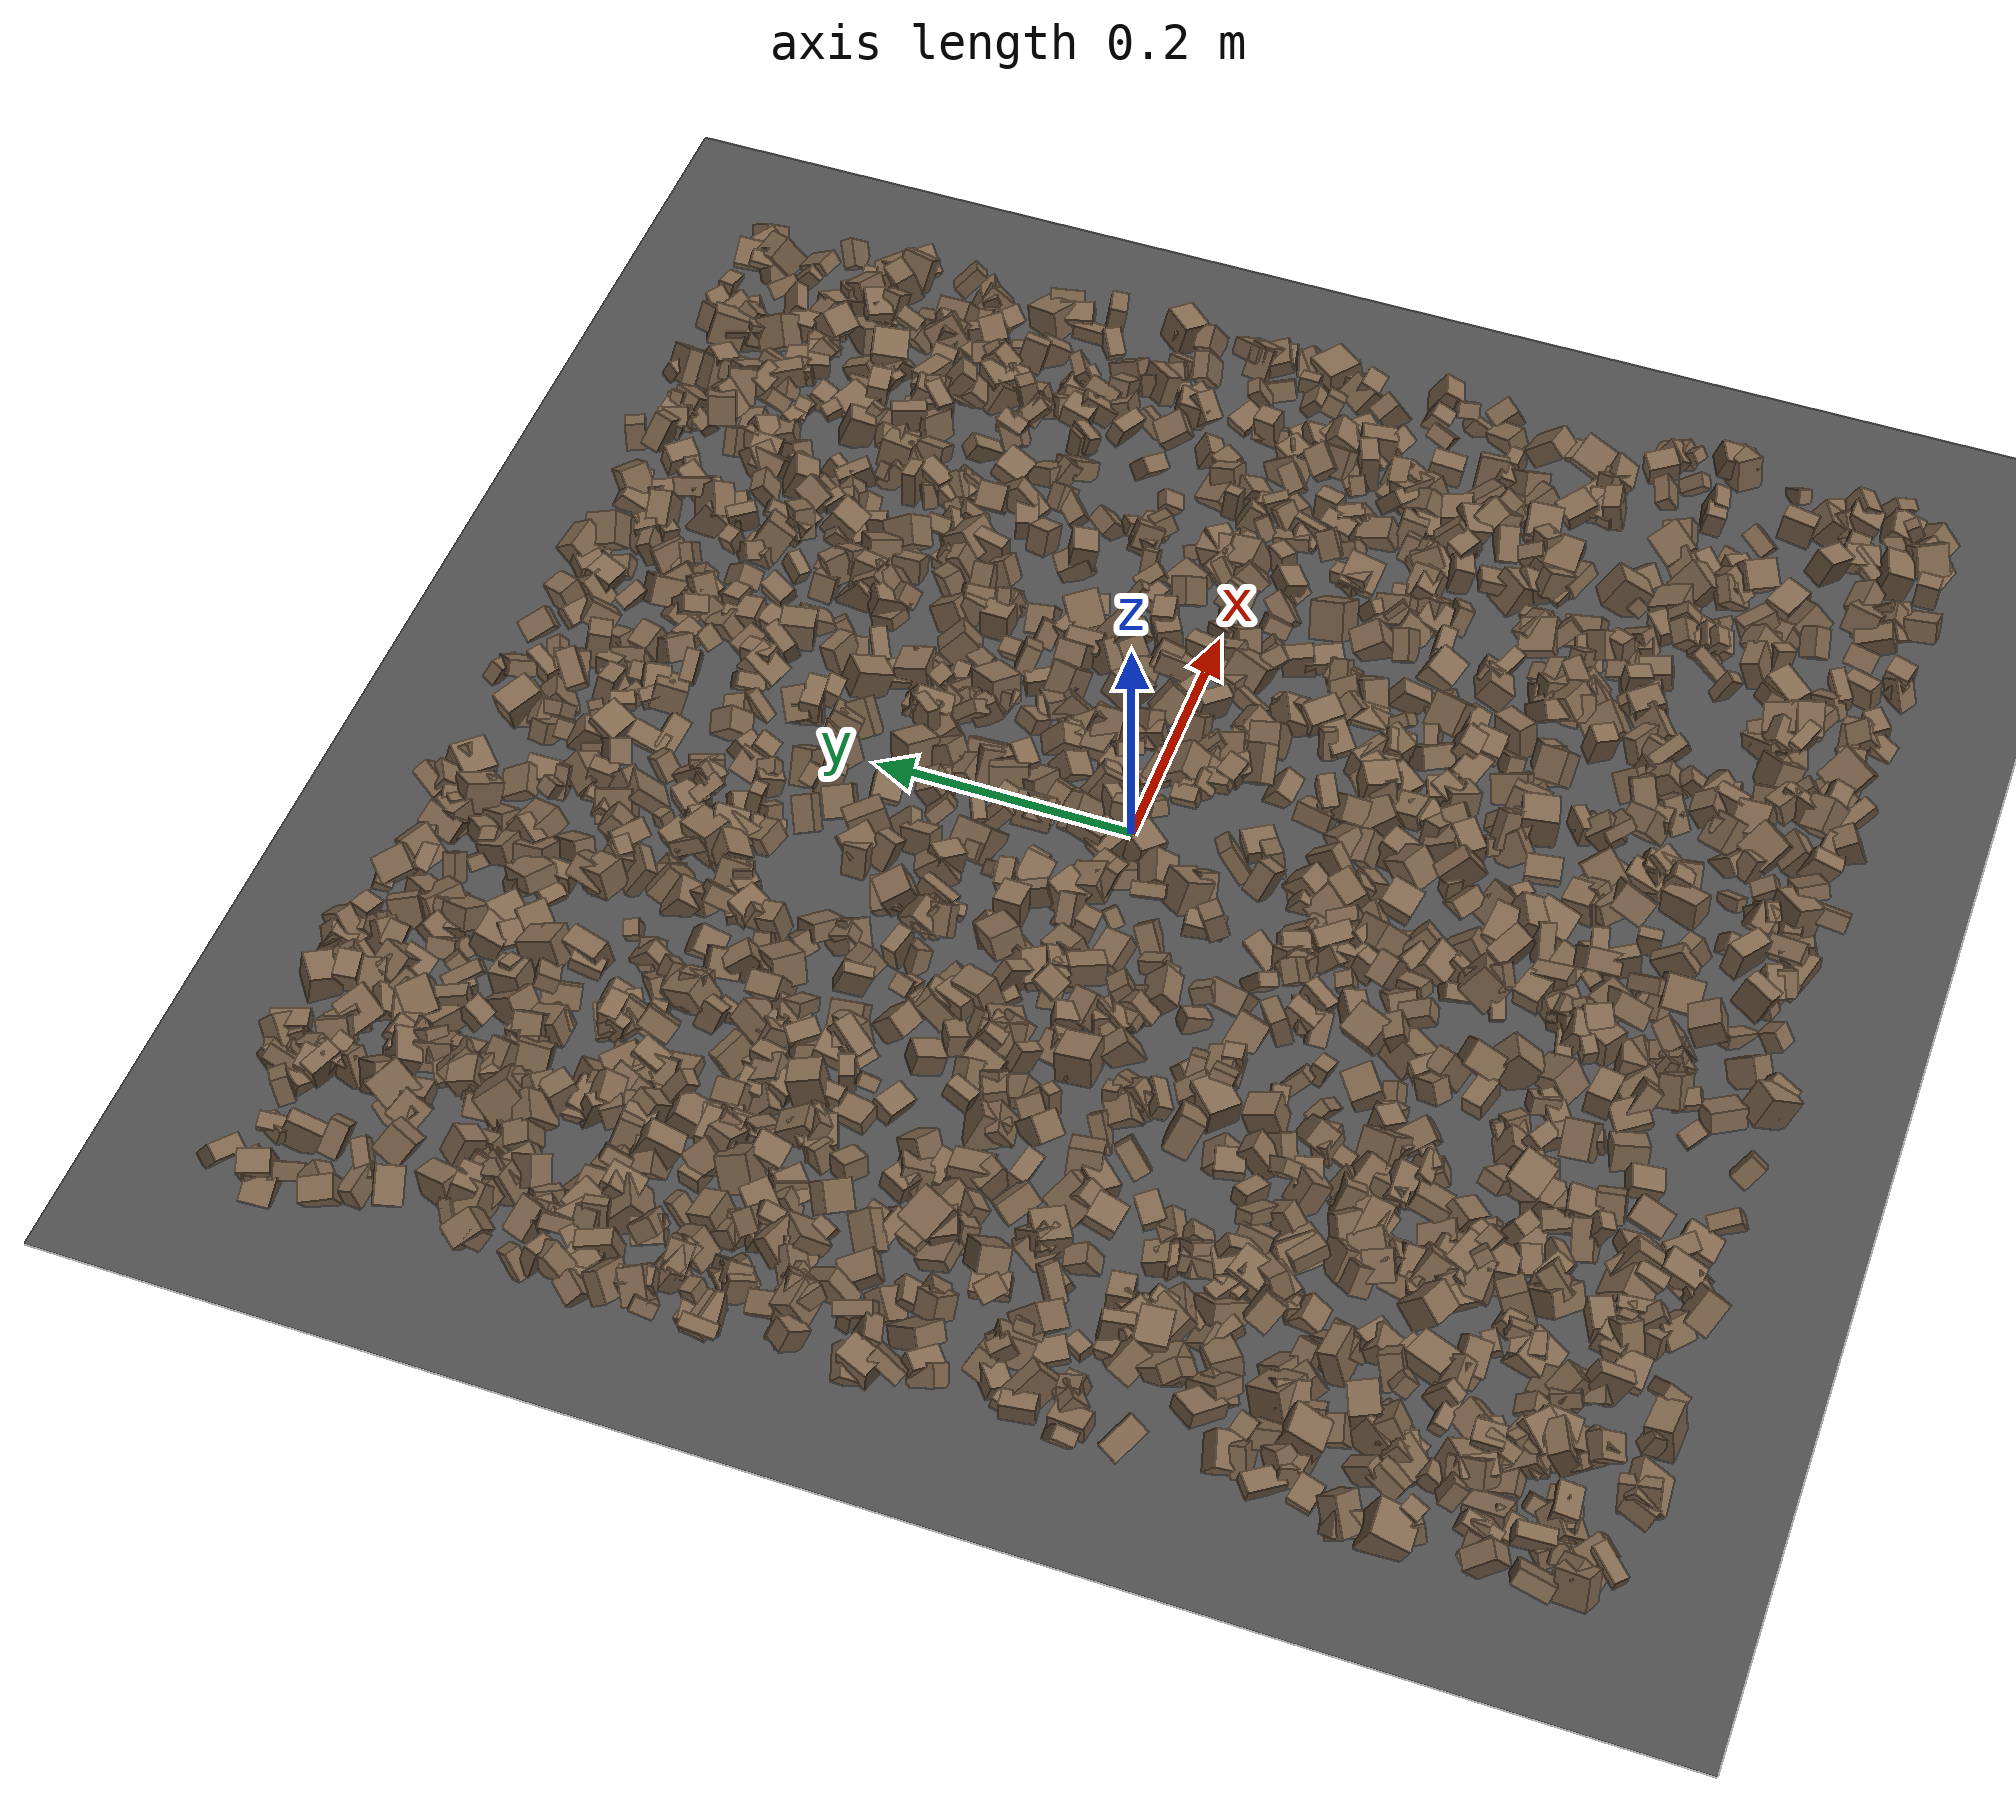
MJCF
<mujoco model="rocky_terrain_scene">
    <compiler angle="radian" inertiafromgeom="true" />
    <option timestep="0.002" gravity="0 0 -9.81" />

    <worldbody>
        <light name="sunlight" pos="5 5 5" dir="-1 -1 -1" diffuse="1 1 1" specular="0.5 0.5 0.5" ambient="0.5 0.5 0.5" />

        <geom name="ground_plane" type="plane" size="50 50 0.1" rgba="0.3 0.3 0.3 1" />

        <body name="rocky_terrain_body">

        <geom name="rock1" type="box" size="0.005774040450092438 0.006012561949136347 0.011568192951829676" pos="0.3284494617178775 0.03367606574777704 0.011731088449476464" quat="0.47708658382299407 0.06346152689467383 0.04667586413602432 0.41277602514630773" rgba="0.5 0.4 0.3 1" /><geom name="rock2" type="box" size="0.0073562797422974955 0.010189866051636434 0.010712164656802862" pos="0.2553233297014773 0.2317361477671066 0.00034139626769414896" quat="0.31862706182412787 0.05357302704241332 0.30229375952584686 0.3255061516076119" rgba="0.5 0.4 0.3 1" /><geom name="rock3" type="box" size="0.008791873792169905 0.014023518533594351 0.012789584408018815" pos="0.15691740077535266 0.09220664887048813 0.005750773815202218" quat="0.015150268906291705 0.8145714696246334 0.0014990355391597688 0.1687792259299152" rgba="0.5 0.4 0.3 1" /><geom name="rock4" type="box" size="0.010579863296184235 0.011517528607565372 0.013565445111636317" pos="-0.15962444718187807 -0.38313768590019026 0.010680427143735155" quat="0.3515812117861777 0.1423032614984994 0.19309027816163543 0.3130252485536875" rgba="0.5 0.4 0.3 1" /><geom name="rock5" type="box" size="0.006962718131278408 0.013851475295292029 0.009129274242990487" pos="0.30051216669928893 -0.30417458495591276 0.00010070661857013219" quat="0.4073523192374017 0.005100735894801643 0.07732246452070923 0.5102244803470875" rgba="0.5 0.4 0.3 1" /><geom name="rock6" type="box" size="0.005466707950500456 0.00911739682639498 0.014696297422664248" pos="0.19411754209131082 -0.35084605219268084 0.012828199519289187" quat="0.3875891982669143 0.2908949396416072 0.09352375866404704 0.22799210342743137" rgba="0.5 0.4 0.3 1" /><geom name="rock7" type="box" size="0.007548162175147239 0.008616707682839855 0.01009228291408313" pos="-0.4972663224908396 0.22198557375005135 0.003461964434299232" quat="0.2646202181500336 0.01600262593878259 0.3603562858120226 0.3590208700991613" rgba="0.5 0.4 0.3 1" /><geom name="rock8" type="box" size="0.008291071634778784 0.005797981721048115 0.009477458693867898" pos="0.367497822795375 0.05082705132298193 0.012863614212373373" quat="0.1616058087910092 0.09279423873823667 0.4058537661032079 0.3397461863675462" rgba="0.5 0.4 0.3 1" /><geom name="rock9" type="box" size="0.00930742989300819 0.011390090538019617 0.00829416809573038" pos="0.1360549511233673 0.3636270924860884 0.003033572116737109" quat="0.18059120583453503 0.27349136879273017 0.11753783941391636 0.4283795859588185" rgba="0.5 0.4 0.3 1" /><geom name="rock10" type="box" size="0.008447034083072198 0.012970310405813788 0.010429734500684018" pos="0.4918762401233576 -0.08908103848338056 0.012891405540614251" quat="0.13275642167473767 0.30020566322349074 0.21883980458354813 0.34819811051822336" rgba="0.5 0.4 0.3 1" /><geom name="rock11" type="box" size="0.012369811514068197 0.005018438340468242 0.01090939564674885" pos="0.1710312684964045 -0.4064575970113855 0.004233341263321442" quat="0.025409142743211086 0.4700813356868245 0.05798988277183731 0.4465196387981271" rgba="0.5 0.4 0.3 1" /><geom name="rock12" type="box" size="0.012904077121978393 0.006979421079263607 0.013944789957093574" pos="0.49258229117864505 0.06876577513530457 0.0112528508506081" quat="0.23864343251302614 0.3880656488126424 0.2799900173207114 0.09330090135362007" rgba="0.5 0.4 0.3 1" /><geom name="rock13" type="box" size="0.014914396999475305 0.006552702631881815 0.00967968539758762" pos="-0.3168104581036828 0.23923450616979725 0.01261523638754891" quat="0.31817314344013226 0.18032519591310742 0.14380239895399602 0.3576992616927642" rgba="0.5 0.4 0.3 1" /><geom name="rock14" type="box" size="0.007089120678761008 0.008866928023623117 0.010782002745441815" pos="-0.15372066007542606 -0.2748113398624866 0.013922762711548235" quat="0.0432696838023127 0.17831088752721455 0.4864956720608863 0.29192375660958647" rgba="0.5 0.4 0.3 1" /><geom name="rock15" type="box" size="0.007916754050506935 0.005002814394094517 0.014221553432896678" pos="-0.48464480312302183 -0.2609513768799202 0.004577128152655758" quat="0.3258274765587626 0.40812841901914254 0.12829662804921438 0.13774747637288046" rgba="0.5 0.4 0.3 1" /><geom name="rock16" type="box" size="0.011840740225932131 0.00900958304791016 0.012250953327257301" pos="0.37750184832358347 -0.15596850844329435 0.014581793798086823" quat="0.11875139966804328 0.11562419958748488 0.5713521296608105 0.1942722710836613" rgba="0.5 0.4 0.3 1" /><geom name="rock17" type="box" size="0.009451866525772542 0.006593800386162404 0.008089758666094543" pos="0.20129275754684695 0.1016010510165376 0.0006279726474575881" quat="0.18590488121986795 0.18069431033788297 0.1815966793943 0.4518041290479491" rgba="0.5 0.4 0.3 1" /><geom name="rock18" type="box" size="0.0069324357118432265 0.006936158179064488 0.011191803431560277" pos="0.03753540623188001 0.030683706004268285 0.008879516698265581" quat="0.3850521817701729 0.022870423667653125 0.41300024229111576 0.17907715227105814" rgba="0.5 0.4 0.3 1" /><geom name="rock19" type="box" size="0.006368910143183975 0.006437817569212221 0.011587724935833819" pos="0.2757978661270749 -0.406538895565135 0.008972502918912143" quat="0.0552063062479746 0.3522343813163464 0.31775861506969033 0.27480069736598883" rgba="0.5 0.4 0.3 1" /><geom name="rock20" type="box" size="0.011241504709289661 0.013515476804277875 0.00834160229614953" pos="-0.3113443286243426 0.24658967061559267 0.011926288382460206" quat="0.2488623174103959 0.31603738797337794 0.15647612075745854 0.2786241738587675" rgba="0.5 0.4 0.3 1" /><geom name="rock21" type="box" size="0.010612914784756504 0.010006625364714 0.0059336914892989855" pos="0.2710554907104584 0.08421980891814829 0.013467834752243255" quat="0.07815448065313792 0.3116168279165278 0.33160264228971004 0.2786260491406242" rgba="0.5 0.4 0.3 1" /><geom name="rock22" type="box" size="0.013187972633989836 0.007730469350929088 0.011352315504159046" pos="-0.1320702656416951 0.34204456122065463 0.012599440842226754" quat="0.07776001006860139 0.18623531442739594 0.5387331941330905 0.19727148137091222" rgba="0.5 0.4 0.3 1" /><geom name="rock23" type="box" size="0.008980553802262285 0.011790711746321694 0.007905866163633656" pos="-0.0919074662642867 0.004284925282648899 0.003467209409754303" quat="0.4194023723430969 0.1414102941592592 0.011196660463263576 0.4279906730343803" rgba="0.5 0.4 0.3 1" /><geom name="rock24" type="box" size="0.013741301520937145 0.007025076008666132 0.008527491282220502" pos="-0.13203511805978263 0.0365838846022728 0.0006847477507359295" quat="0.06828072331313542 0.39078550321110433 0.1958310254187202 0.34510274805704005" rgba="0.5 0.4 0.3 1" /><geom name="rock25" type="box" size="0.01077322523165146 0.011368053057999324 0.007958019619917735" pos="0.3385048051543812 0.46921875367456256 0.012218587328403675" quat="0.059966983798061306 0.17192709002987616 0.3015078864168085 0.46659803975525405" rgba="0.5 0.4 0.3 1" /><geom name="rock26" type="box" size="0.0056024522070335335 0.011042046821712594 0.007688423445619289" pos="0.4464924535004787 0.0509252026644198 0.011196713603987657" quat="0.2838173356683151 0.13331235179617465 0.34338718875687285 0.2394831237786375" rgba="0.5 0.4 0.3 1" /><geom name="rock27" type="box" size="0.008334359617687158 0.008713638757692254 0.009077948118068276" pos="0.07350862603984709 -0.053032293487607296 0.010692675814846286" quat="0.3314396933862214 0.25578110434134094 0.15968050518359886 0.2530986970888387" rgba="0.5 0.4 0.3 1" /><geom name="rock28" type="box" size="0.005184917891042794 0.0055958813095364915 0.0057237001900495126" pos="-0.10378946369427078 0.3261962191621236 0.005337022800249583" quat="0.32456166423822363 0.2852242401723283 0.24787164369245976 0.14234245189698833" rgba="0.5 0.4 0.3 1" /><geom name="rock29" type="box" size="0.008197903432525936 0.009152846661846676 0.012501036102854293" pos="-0.29523010139625894 -0.31570372405959535 0.012903360982672415" quat="0.3201448551182854 0.24784483082467684 0.030499077975306765 0.401511236081731" rgba="0.5 0.4 0.3 1" /><geom name="rock30" type="box" size="0.010224765120739887 0.013931224262590913 0.006243332924282047" pos="0.24307109171520103 -0.27840766431734065 0.00046180147963466756" quat="0.2236075719862117 0.24390307295736915 0.5181951164950493 0.014294238561369806" rgba="0.5 0.4 0.3 1" /><geom name="rock31" type="box" size="0.005872991432871499 0.008579890916292254 0.014057474715535125" pos="0.21342929725341508 -0.2566017913361184 0.004977806330912174" quat="0.20430594913221514 0.6377625449276574 0.10426057843109646 0.05367092750903113" rgba="0.5 0.4 0.3 1" /><geom name="rock32" type="box" size="0.005444871387928335 0.01277218140544709 0.009689727500028118" pos="0.307290799099878 0.2059701542418665 0.0017574842731476192" quat="0.09323369387505047 0.4406978205913908 0.26714460640457044 0.19892387912898823" rgba="0.5 0.4 0.3 1" /><geom name="rock33" type="box" size="0.006227510712371833 0.013366529616786388 0.012684739205224687" pos="0.03916862643315655 -0.33397312049592187 0.00460601922175945" quat="0.03753592094846695 0.08216388896535153 0.5349609578503928 0.34533923223578883" rgba="0.5 0.4 0.3 1" /><geom name="rock34" type="box" size="0.012422086990401631 0.012942769195366539 0.00735874764484679" pos="0.4189480390439636 -0.11172227115661493 0.011436142228793616" quat="0.49831658210613333 0.020733072947955497 0.4331589592555252 0.047791385690385955" rgba="0.5 0.4 0.3 1" /><geom name="rock35" type="box" size="0.006205954820222216 0.0060013081146314175 0.008776615811204836" pos="0.17972718361690176 -0.44478540147194345 0.01391133844698403" quat="0.16355176236797656 0.0987247566200277 0.1739104821926213 0.5638129988193743" rgba="0.5 0.4 0.3 1" /><geom name="rock36" type="box" size="0.01015516655590617 0.0053663976308043594 0.006981084137460132" pos="0.016579179067405247 0.23304581186031736 0.013560438158410248" quat="0.29124474250270416 0.33030635385300056 0.048425692177620876 0.33002321146667435" rgba="0.5 0.4 0.3 1" /><geom name="rock37" type="box" size="0.007026584986662728 0.014574232309943043 0.012466337006741771" pos="-0.42943274411894927 -0.3375135581092663 0.00109874375994249" quat="0.4010724806468088 0.12395487514556477 0.47078533817609297 0.004187306031533455" rgba="0.5 0.4 0.3 1" /><geom name="rock38" type="box" size="0.005188110198267861 0.007953646523904543 0.0097928284184194" pos="0.16668940266072962 -0.1541391221534909 0.0021016263954339092" quat="0.11763045816482913 0.5397017710498838 0.12795352923893974 0.21471424154634736" rgba="0.5 0.4 0.3 1" /><geom name="rock39" type="box" size="0.013349124212958478 0.01006748026413621 0.011760408124242127" pos="-0.23592064107649524 0.027031276199596888 0.007961436843948821" quat="0.33012950805935504 0.26154527110856984 0.12725282146369768 0.28107239936837747" rgba="0.5 0.4 0.3 1" /><geom name="rock40" type="box" size="0.007914571188203786 0.008546250361040633 0.01300927579704433" pos="-0.017591142103142055 -0.10663211730289412 0.012796132487046792" quat="0.4511306788744119 0.1668932388032093 0.06846111520553136 0.31351496711684745" rgba="0.5 0.4 0.3 1" /><geom name="rock41" type="box" size="0.012018050982790754 0.006343043183389927 0.00692170426479916" pos="-0.47492344586428437 -0.021374405003750097 0.008842570724173817" quat="0.12270188088871387 0.17588607162499204 0.2878121224168388 0.4135999250694553" rgba="0.5 0.4 0.3 1" /><geom name="rock42" type="box" size="0.010494820030070469 0.0115308740117309 0.005880240478121664" pos="-0.3587983699960068 -0.42996328933377614 0.012382468349251927" quat="0.35285495973602926 0.04623415991267992 0.1621889123862035 0.43872196796508733" rgba="0.5 0.4 0.3 1" /><geom name="rock43" type="box" size="0.008898989457107317 0.007218692720700768 0.010678700618852725" pos="-0.4384245811465878 0.1918321439708054 0.011451080537999191" quat="0.24472860009024988 0.21247929110758126 0.43469426168552294 0.108097847116646" rgba="0.5 0.4 0.3 1" /><geom name="rock44" type="box" size="0.007475106450428469 0.012636731931795483 0.007269281256453172" pos="0.19017165875310338 -0.10007169060728771 0.010427017835274213" quat="0.2712029278950328 0.0560142137803434 0.5938861012053522 0.07889675711927163" rgba="0.5 0.4 0.3 1" /><geom name="rock45" type="box" size="0.0140860281972604 0.014726037828288109 0.007402968828492697" pos="0.019280317436224048 -0.272217392063428 0.005316532449406399" quat="0.2177741053020987 0.5172455384645203 0.2580905064047581 0.006889849828622967" rgba="0.5 0.4 0.3 1" /><geom name="rock46" type="box" size="0.014908689020884665 0.01103952949453571 0.012188251801823476" pos="0.40523730568411753 0.39710346107261874 0.013161049202468874" quat="0.38958392872998826 0.23730945484155774 0.36134535979719223 0.011761256631261773" rgba="0.5 0.4 0.3 1" /><geom name="rock47" type="box" size="0.010135872491804662 0.0062363227474716764 0.009755113827684785" pos="0.08546234418591836 -0.19610240732948414 0.0073398956097087496" quat="0.1315158907345803 0.15811549437682598 0.31526911428020626 0.39509950060838744" rgba="0.5 0.4 0.3 1" /><geom name="rock48" type="box" size="0.009362977637021694 0.0066863146060106154 0.013351472196590511" pos="-0.24661469795076185 0.12411464117070525 0.0077278834457471255" quat="0.0946560797967236 0.347746606747718 0.4298881038797594 0.127709209575799" rgba="0.5 0.4 0.3 1" /><geom name="rock49" type="box" size="0.012775939039846002 0.013076232700194812 0.008827993351720811" pos="0.062394540809378674 -0.23546142588525365 0.014547223012663117" quat="0.36361145036016956 0.3752635949595595 0.08573110371139162 0.1753938509688793" rgba="0.5 0.4 0.3 1" /><geom name="rock50" type="box" size="0.009685738107271295 0.00814564871716333 0.006430615050009133" pos="0.07398549212424577 0.10422950910262874 0.005549769074276125" quat="0.4945989214334267 0.139808923143959 0.0971077273518701 0.26848442807074413" rgba="0.5 0.4 0.3 1" /><geom name="rock51" type="box" size="0.011141872559810927 0.010221174567520088 0.009210714864220903" pos="0.27127045037165665 0.21054318907257097 0.012412681018219528" quat="0.11158192928703586 0.37041090708023305 0.3812523853642308 0.13675477826850033" rgba="0.5 0.4 0.3 1" /><geom name="rock52" type="box" size="0.010246734583033053 0.005407989364085628 0.005739501088959486" pos="0.16767727499874918 0.30499200723246556 0.003365249658711333" quat="0.3801050365537819 0.20107905820460095 0.10524937229370332 0.3135665329479138" rgba="0.5 0.4 0.3 1" /><geom name="rock53" type="box" size="0.014985167423005322 0.007929698293276121 0.007438789648852074" pos="-0.4373205609509295 -0.4525652221115647 0.004637183147328635" quat="0.06277586146633433 0.45830724996170963 0.11644549406842887 0.3624713945035272" rgba="0.5 0.4 0.3 1" /><geom name="rock54" type="box" size="0.01077293190410904 0.012144106067767876 0.009211818506758132" pos="0.31085476893810293 -0.349307888059027 0.005791375568922486" quat="0.3319467063565668 0.3249264749710088 0.136159486652352 0.20696733202007242" rgba="0.5 0.4 0.3 1" /><geom name="rock55" type="box" size="0.008851796711124717 0.012774727712458042 0.013045413761392496" pos="-0.4286644194446392 -0.3207510818306061 0.00422483851677818" quat="0.023447032553786194 0.17035758123967798 0.31249149919813957 0.49370388700839635" rgba="0.5 0.4 0.3 1" /><geom name="rock56" type="box" size="0.006925626738899609 0.012709008850791442 0.011562869555033745" pos="-0.2780707326711217 -0.40001752615878217 0.013985081647741749" quat="0.22196353081118458 0.19733259761859276 0.4899551241770618 0.09074874739316094" rgba="0.5 0.4 0.3 1" /><geom name="rock57" type="box" size="0.007218811822092032 0.01026534664746479 0.006508972862302662" pos="0.01892382656574987 -0.4825987112562624 0.009863268281571011" quat="0.09489314855141556 0.28952654105998366 0.4228706808819335 0.19270962950666734" rgba="0.5 0.4 0.3 1" /><geom name="rock58" type="box" size="0.007803284271034796 0.009914535664355819 0.012507230483026951" pos="-0.14460069041597323 -0.3073038461043246 0.005464902450660298" quat="0.29826854913690604 0.27139178824626264 0.20885514537030475 0.2214845172465266" rgba="0.5 0.4 0.3 1" /><geom name="rock59" type="box" size="0.009953880142278215 0.011706322666912215 0.007499962147211672" pos="-0.4381604451219583 0.19241634820859022 0.005007359837345467" quat="0.007117962374468514 0.6643563432549083 0.12778084056759556 0.20074485380302753" rgba="0.5 0.4 0.3 1" /><geom name="rock60" type="box" size="0.014660811466895036 0.014182858219173589 0.006657582145638252" pos="0.17155596590556854 -0.3538201512872331 0.006250613771058605" quat="0.3374459003047031 0.14995640144645445 0.33122410372981126 0.18137359451903118" rgba="0.5 0.4 0.3 1" /><geom name="rock61" type="box" size="0.008790372227476414 0.012390291646600646 0.005790106059438383" pos="-0.2094616175731755 -0.12036371097839438 0.012377307735234438" quat="0.1632774906575284 0.6512658890949217 0.1678352008239024 0.017621419423647505" rgba="0.5 0.4 0.3 1" /><geom name="rock62" type="box" size="0.011974805629776066 0.011978997723994831 0.013934782408609129" pos="0.360014072338644 0.4072569825086939 0.0037679309921656644" quat="0.252358073061762 0.20416861616461468 0.27362543216864216 0.2698478786049811" rgba="0.5 0.4 0.3 1" /><geom name="rock63" type="box" size="0.009015249706828375 0.012604340999193739 0.006820017600400218" pos="0.2859023709080477 -0.02085235771707772 0.0074977751924665175" quat="0.3393008403716909 0.34114973356191575 0.1824953073944676 0.13705411867192574" rgba="0.5 0.4 0.3 1" /><geom name="rock64" type="box" size="0.006159791112591608 0.00894846873348791 0.011320948217321804" pos="-0.33373878079827535 0.24384362139919213 0.00020994028184302904" quat="0.3760378183373965 0.22070327772478654 0.10661792177991468 0.29664098215790224" rgba="0.5 0.4 0.3 1" /><geom name="rock65" type="box" size="0.012465854583537621 0.010474246219811913 0.009044473555561611" pos="0.06594044103481933 -0.15129367822887585 2.860548415040631e-05" quat="0.17130073125873202 0.18872151214085042 0.259315279043736 0.3806624775566815" rgba="0.5 0.4 0.3 1" /><geom name="rock66" type="box" size="0.009707567182763877 0.010228928082810125 0.007503347052906177" pos="0.07360936489538827 0.15713665760756212 0.006110701215104641" quat="0.4493572194387379 0.0028705026975980948 0.14288826594514348 0.4048840119185206" rgba="0.5 0.4 0.3 1" /><geom name="rock67" type="box" size="0.006321869726002009 0.01023485982647122 0.00596820609378013" pos="0.02767837958798447 -0.23316803654030438 0.001603521668173362" quat="0.10958012185360598 0.19488678801344847 0.3597504954114598 0.3357825947214857" rgba="0.5 0.4 0.3 1" /><geom name="rock68" type="box" size="0.008370573811737933 0.012362249106483474 0.007626111037737899" pos="0.15362968355793638 0.24056164988900397 0.011531855543925352" quat="0.18992703721373 0.296376094318743 0.06455223892612603 0.449144629541401" rgba="0.5 0.4 0.3 1" /><geom name="rock69" type="box" size="0.013760872043540765 0.01129232614541105 0.007901337288191758" pos="-0.10321770804614272 -0.4696704578317401 0.006488219080384227" quat="0.27193015891302835 0.09275916558330427 0.11778849834693655 0.5175221771567308" rgba="0.5 0.4 0.3 1" /><geom name="rock70" type="box" size="0.011377322639206345 0.014054312948661246 0.006576991339771996" pos="-0.14128724015193184 0.2564542114167624 0.009993133885487575" quat="0.10539638438521766 0.3400827306251188 0.3391347983817984 0.2153860866078651" rgba="0.5 0.4 0.3 1" /><geom name="rock71" type="box" size="0.008190031566913922 0.013084560004718523 0.007769072992019474" pos="0.369911995308118 -0.20604365976956185 0.0012512363590197633" quat="0.47049930350611274 0.2637732222598917 0.2576535942445691 0.008073879989426611" rgba="0.5 0.4 0.3 1" /><geom name="rock72" type="box" size="0.01145907613953269 0.010200669375080568 0.007740424828313491" pos="-0.2848108741184837 -0.4480306215318687 0.004830542701349189" quat="0.28728102744646583 0.13042605301317897 0.27247159383381414 0.30982132570654103" rgba="0.5 0.4 0.3 1" /><geom name="rock73" type="box" size="0.012503527338146837 0.009577781553708024 0.010839556074496305" pos="-0.28035192539195963 -0.3587534235699442 0.0032543079333598257" quat="0.17888694176083297 0.23509581433094515 0.3552426622742419 0.23077458163398" rgba="0.5 0.4 0.3 1" /><geom name="rock74" type="box" size="0.005397657622362543 0.010346451863192836 0.013435409833554183" pos="-0.030700398988444455 0.1374071040031527 0.009079692391305176" quat="0.041823606909489434 0.4579253274456908 0.25125720079414454 0.24899386485067518" rgba="0.5 0.4 0.3 1" /><geom name="rock75" type="box" size="0.00986877762129705 0.009525325294719958 0.005549822168845613" pos="0.33544611904640464 -0.0006572094507815152 0.012742222421767901" quat="0.20590942575188137 0.1662049764648852 0.3473090530059546 0.2805765447772789" rgba="0.5 0.4 0.3 1" /><geom name="rock76" type="box" size="0.010247880289901748 0.013229767513871574 0.010044718357496079" pos="-0.3715163927764147 0.11540847620024663 0.0014891144275592121" quat="0.053067336486853744 0.2189345130852242 0.5700797372352371 0.15791841319268501" rgba="0.5 0.4 0.3 1" /><geom name="rock77" type="box" size="0.01420357078885508 0.005195264085950229 0.006469168707917862" pos="-0.38137974307173084 0.4526116163387207 0.01462258349253223" quat="0.10848695612837736 0.35078155329678024 0.3330012711291829 0.20773021944565948" rgba="0.5 0.4 0.3 1" /><geom name="rock78" type="box" size="0.010549829478844152 0.009671661397226264 0.014167628161267477" pos="0.33060523536551556 0.47090162959692583 0.006445568123067188" quat="0.4944847188712504 0.09791449572596231 0.1645407647421317 0.24306002066065566" rgba="0.5 0.4 0.3 1" /><geom name="rock79" type="box" size="0.006487654832033477 0.007650173074247073 0.008413061486592708" pos="0.17183582532626085 0.09496381061099113 0.0024356073659232784" quat="0.197948446956461 0.26449655742960576 0.2787560859884031 0.25879890962553015" rgba="0.5 0.4 0.3 1" /><geom name="rock80" type="box" size="0.008989592266014831 0.012850987088315804 0.006296702444552239" pos="-0.04302602524744392 -0.26294716697299425 0.0001158892576717746" quat="0.3277159587398061 0.14566183117669856 0.4524150492898108 0.07420716079368452" rgba="0.5 0.4 0.3 1" /><geom name="rock81" type="box" size="0.007287674038733713 0.01143717989144728 0.00921626987404745" pos="-0.16918293102792592 0.3509545940194181 0.0038873067994495717" quat="0.30069160391419686 0.26930079521927325 0.34598422392825473 0.0840233769382751" rgba="0.5 0.4 0.3 1" /><geom name="rock82" type="box" size="0.010192346902293198 0.009073110390843481 0.012897071806439772" pos="0.2879110233100328 0.3921794880971373 0.002137736710072161" quat="0.21762387885575338 0.20050718270838372 0.3509055937085373 0.23096334472732555" rgba="0.5 0.4 0.3 1" /><geom name="rock83" type="box" size="0.01228057411286999 0.007486058303986197 0.01466806758133301" pos="0.2693285147300889 0.4767905102540859 0.0076676024565459815" quat="0.1117107594239616 0.3404846895550443 0.4411178407777953 0.10668671024319884" rgba="0.5 0.4 0.3 1" /><geom name="rock84" type="box" size="0.013259370405344362 0.006099253577032983 0.014312206998252409" pos="-0.24456793506621743 -0.3023435278370499 0.013817524662205425" quat="0.13678400564973822 0.36222662870596345 0.2748853599381141 0.22610400570618422" rgba="0.5 0.4 0.3 1" /><geom name="rock85" type="box" size="0.009996402372682182 0.01267529583519758 0.013243527823900734" pos="0.17339370152836642 -0.47305008471271903 0.012479301358556663" quat="0.39239912755243317 0.17090389402357578 0.2116104917225394 0.2250864867014517" rgba="0.5 0.4 0.3 1" /><geom name="rock86" type="box" size="0.014621818831889604 0.009543615128173165 0.014473736521844562" pos="0.4692771136397266 -0.4123101937996707 0.003766371165635553" quat="0.2530373064417218 0.28781138736020007 0.3779871007097407 0.08116420548833742" rgba="0.5 0.4 0.3 1" /><geom name="rock87" type="box" size="0.00824726812591506 0.0064836755349992016 0.011318065629239262" pos="-0.09793440993092639 0.24613050297372963 0.009282292537892218" quat="0.13728038561320136 0.4258720219294233 0.0274962229172391 0.4093513695401363" rgba="0.5 0.4 0.3 1" /><geom name="rock88" type="box" size="0.0069683835570448875 0.007961702395032069 0.006660093596411362" pos="0.2681657984559964 -0.2931051929690166 0.0027385495790070912" quat="0.05252995375822829 0.336122785104758 0.09254764637502977 0.5187996147619839" rgba="0.5 0.4 0.3 1" /><geom name="rock89" type="box" size="0.0091853126837961 0.009479195565123184 0.009563695176747447" pos="0.25993038962658743 -0.4814027353666509 0.009894512840971878" quat="0.04443525373152729 0.32879160639426647 0.17840101062374608 0.44837212925046016" rgba="0.5 0.4 0.3 1" /><geom name="rock90" type="box" size="0.005825413438208189 0.010838217208601057 0.005731396458622655" pos="0.46885416882171016 -0.29797835591871624 0.008928123859298764" quat="0.19685598628754322 0.5750913919498888 0.07351374933638721 0.15453887242618078" rgba="0.5 0.4 0.3 1" /><geom name="rock91" type="box" size="0.014933401281577087 0.013845302437429593 0.008703064556243442" pos="0.20276510030724992 -0.07990637007833334 0.001514834139631958" quat="0.20398955516045839 0.17546277334380297 0.2731204369091908 0.3474272345865479" rgba="0.5 0.4 0.3 1" /><geom name="rock92" type="box" size="0.008311330738170027 0.012240748263255191 0.008123805962648913" pos="0.4004211773740505 -0.10612984234629963 0.0018896882508028362" quat="0.36876007317270365 0.26373895573858563 0.22747088228882248 0.1400300887998883" rgba="0.5 0.4 0.3 1" /><geom name="rock93" type="box" size="0.00687312533343729 0.006826309216461248 0.008376958524623083" pos="0.23875801508326433 0.30223205724228475 0.0028209380687457958" quat="0.14268354720202242 0.28388341719699034 0.13948151876204357 0.4339515168389437" rgba="0.5 0.4 0.3 1" /><geom name="rock94" type="box" size="0.011165156122102326 0.00765260695162325 0.013703541724918375" pos="0.17126101022728613 -0.11045299279346721 0.008191769438851942" quat="0.30908334084760164 0.10568745760721548 0.3062578934087165 0.2789713081364664" rgba="0.5 0.4 0.3 1" /><geom name="rock95" type="box" size="0.010339114322326232 0.008144482085632307 0.005238112448372681" pos="0.15560819682692106 0.32786248679770313 0.008031242398321101" quat="0.2787045143208698 0.40207280148752533 0.11796495969949915 0.20125772449210577" rgba="0.5 0.4 0.3 1" /><geom name="rock96" type="box" size="0.012097527573631445 0.012960927884946162 0.011102196336674745" pos="0.27070964838207756 0.2424823630092049 0.0009502472153690594" quat="0.08747467382984143 0.0757681540794474 0.3583276576813373 0.47842951440937387" rgba="0.5 0.4 0.3 1" /><geom name="rock97" type="box" size="0.013190927773067858 0.010956803065230336 0.01248477676374005" pos="-0.3242194940338269 -0.32403705859120024 0.01295829117081034" quat="0.343506444969486 0.2203745807970637 0.3766733648966784 0.059445609336771885" rgba="0.5 0.4 0.3 1" /><geom name="rock98" type="box" size="0.010007643507420805 0.00567328416557361 0.007023879052322027" pos="0.062429964813400685 0.31816248191001584 0.0019441168263058767" quat="0.30674599923787654 0.015630996143080896 0.2911263158229848 0.38649668879605775" rgba="0.5 0.4 0.3 1" /><geom name="rock99" type="box" size="0.013677944437340151 0.010137399353603227 0.008266825995619226" pos="0.3462929914407381 -0.05900832371816289 0.008171395240540696" quat="0.3725073008130196 0.1768920135448492 0.27063241505052593 0.17996827059160528" rgba="0.5 0.4 0.3 1" /><geom name="rock100" type="box" size="0.01266090332420056 0.008823437496555342 0.011866042220054357" pos="-0.4087780153795547 -0.14659533032423477 0.006741973030743457" quat="0.1992297165553469 0.429017670535718 0.05964294841095349 0.31210966449798155" rgba="0.5 0.4 0.3 1" /><geom name="rock101" type="box" size="0.014727353246018565 0.005083985729489887 0.00640347446780579" pos="-0.38961026459153647 -0.08071890559725425 0.00935650677223932" quat="0.25444023353156064 0.45435422163558076 0.010063259511093861 0.28114228532176483" rgba="0.5 0.4 0.3 1" /><geom name="rock102" type="box" size="0.005492821783866274 0.006248068375147017 0.005419426203359624" pos="0.23572184643830763 0.31687286772498924 0.01039562496742915" quat="0.0009534710343723036 0.3983545264605056 0.1300304744537251 0.47066152805139705" rgba="0.5 0.4 0.3 1" /><geom name="rock103" type="box" size="0.010367257207667357 0.009986754238710968 0.009501989329445565" pos="-0.23936420269545367 -0.07842077980582274 0.0055076725842863865" quat="0.006076387542234501 0.3257713221942686 0.17764312365003726 0.49050916661345967" rgba="0.5 0.4 0.3 1" /><geom name="rock104" type="box" size="0.005404281730491568 0.013260759600664584 0.005240729124108794" pos="0.17164909845465992 -0.21381325076278357 0.00359014315339582" quat="0.4927205640090254 0.18023374191835498 0.1653753905653878 0.1616703035072317" rgba="0.5 0.4 0.3 1" /><geom name="rock105" type="box" size="0.010119565929571665 0.01013257618989856 0.00770916690957391" pos="-0.06660303541629509 -0.08488768229924148 0.014894442757933462" quat="0.4317083058644811 0.3329197733735796 0.15781612740268447 0.0775557933592548" rgba="0.5 0.4 0.3 1" /><geom name="rock106" type="box" size="0.011239033237017956 0.008229973197077368 0.01460654298741407" pos="-0.49453618182630266 -0.3174127776503276 0.012437570387666179" quat="0.09776501734619833 0.18745389946314095 0.17429756351071551 0.5404835196799451" rgba="0.5 0.4 0.3 1" /><geom name="rock107" type="box" size="0.012759701294867754 0.009451956419639472 0.009070198645038701" pos="-0.48548653974185074 0.4151439890906925 0.008212504801757576" quat="0.27483246686712276 0.13283706554576138 0.2659117131271905 0.32641875445992535" rgba="0.5 0.4 0.3 1" /><geom name="rock108" type="box" size="0.005824611180660494 0.0077668585135793776 0.011449389821650807" pos="-0.26583697834820474 0.25940262819478643 0.0012113816993464099" quat="0.05786957495256508 0.4067766065412465 0.4262910330887244 0.10906278541746402" rgba="0.5 0.4 0.3 1" /><geom name="rock109" type="box" size="0.007983482291304241 0.008007316840864588 0.01436344171085907" pos="0.08618334452409537 0.1401523426572968 0.00020773526518344854" quat="0.3247499734896044 0.23819176557488345 0.21015563252106012 0.226902628414452" rgba="0.5 0.4 0.3 1" /><geom name="rock110" type="box" size="0.013826369211479516 0.006293239632220301 0.00839535279522596" pos="0.3867994032086096 -0.1655581438544832 0.0060332757101661805" quat="0.0710621872478488 0.27763009369749714 0.3714453598581527 0.2798623591965014" rgba="0.5 0.4 0.3 1" /><geom name="rock111" type="box" size="0.012097931059473661 0.008788134596850558 0.014547227677428495" pos="-0.3587302838364106 -0.337355483219849 0.005171583587115887" quat="0.05001614353021648 0.09780008744784077 0.41319247688306754 0.4389912921388752" rgba="0.5 0.4 0.3 1" /><geom name="rock112" type="box" size="0.006512035930503146 0.013855246933777661 0.0073351026572502295" pos="0.08370251080185465 0.179602356400259 0.012231523857381046" quat="0.34698607609222226 0.29076036683981016 0.1099197298153531 0.2523338272526145" rgba="0.5 0.4 0.3 1" /><geom name="rock113" type="box" size="0.012534916954274548 0.005769896307853879 0.012047546121470562" pos="0.49515637020064374 0.3563673434143285 0.012694549562776505" quat="0.322284509840108 0.3974914521632157 0.041674653563030906 0.2385493844336455" rgba="0.5 0.4 0.3 1" /><geom name="rock114" type="box" size="0.012230416344957841 0.01355484981156549 0.01218458900466218" pos="0.3816342518494571 0.43529758059718504 0.013219546425844097" quat="0.2344646606836351 0.3054850358885705 0.40076947224300785 0.059280831184786505" rgba="0.5 0.4 0.3 1" /><geom name="rock115" type="box" size="0.012143500262661904 0.014501498257638908 0.010269164019377618" pos="0.26823386313902275 0.4806921041633303 0.006018658609641335" quat="0.22560526837089712 0.2913972876192109 0.19017683990003414 0.2928206041098578" rgba="0.5 0.4 0.3 1" /><geom name="rock116" type="box" size="0.012369952425228883 0.012198013087665724 0.01494071771971531" pos="-0.2136869393979246 -0.13579372044134452 0.011264090816435483" quat="0.137035484064741 0.15182402154157762 0.334074012663312 0.3770664817303694" rgba="0.5 0.4 0.3 1" /><geom name="rock117" type="box" size="0.013713692298952754 0.010669583191391165 0.006328333471214956" pos="-0.4994024787722984 -0.44744762997820076 0.012055029560063596" quat="0.33888969549227743 0.20781609136009463 0.07552838912249163 0.37776582402513637" rgba="0.5 0.4 0.3 1" /><geom name="rock118" type="box" size="0.006185339349260511 0.008085227139602748 0.008414720719268071" pos="0.09419615424615035 0.03081567307156008 0.0007243367714893672" quat="0.5030649102994292 0.053313871290567576 0.07115698459932618 0.3724642338106771" rgba="0.5 0.4 0.3 1" /><geom name="rock119" type="box" size="0.010941684950722019 0.008683148210370074 0.011772048906892813" pos="-0.16666727419146588 -0.33555603770897424 0.003538774548951606" quat="0.251751446378114 0.09204803170948049 0.2127640106208849 0.4434365112915206" rgba="0.5 0.4 0.3 1" /><geom name="rock120" type="box" size="0.013280365868652274 0.011640644826890348 0.010663053726173646" pos="-0.12538552868433606 -0.40956041726207615 0.0045823999844683445" quat="0.23819456287208216 0.12037419769606267 0.2842207972353085 0.3572104421965465" rgba="0.5 0.4 0.3 1" /><geom name="rock121" type="box" size="0.00794247617816158 0.013898468248278513 0.008778234803740903" pos="0.4623724382320651 0.27175176849633464 0.006121638072343953" quat="0.25624819923701453 0.40485726963036045 0.06911448145375275 0.26978004967887226" rgba="0.5 0.4 0.3 1" /><geom name="rock122" type="box" size="0.010043851911540114 0.012149062609169184 0.01497141297031504" pos="0.43716726123080096 0.27071441414006914 0.010208423582147434" quat="0.21208414707582599 0.1484545054968768 0.33437056868733617 0.30509077873996104" rgba="0.5 0.4 0.3 1" /><geom name="rock123" type="box" size="0.006938567072857759 0.010509382642481815 0.013791448579110303" pos="-0.3111169278121476 0.3983005154054797 0.010549856651725562" quat="0.46461032967911886 0.39244497037103937 0.1186976553396857 0.024247044610156133" rgba="0.5 0.4 0.3 1" /><geom name="rock124" type="box" size="0.008263908581755451 0.014320788299212552 0.00985984011083716" pos="-0.023307431221493813 0.24604191816971688 0.0054632533859485756" quat="0.20038064764447946 0.3437337025064506 0.3469767079426328 0.10890894190643713" rgba="0.5 0.4 0.3 1" /><geom name="rock125" type="box" size="0.010703477727816844 0.01267933949545329 0.013655462934720912" pos="-0.3014065938824938 -0.2590909004327254 0.001976939558143782" quat="0.02816031332308814 0.31073270698989747 0.3581408074931679 0.3029661721938464" rgba="0.5 0.4 0.3 1" /><geom name="rock126" type="box" size="0.00932758359513799 0.011481295291951087 0.011900287608281122" pos="0.39513024740117664 -0.017579157545305035 0.007800093564439748" quat="0.2764587220398524 0.06375414539870557 0.3097590621899087 0.35002807037153333" rgba="0.5 0.4 0.3 1" /><geom name="rock127" type="box" size="0.008509100506760785 0.005804389088920254 0.012310175823973361" pos="0.02550650840185209 -0.3815265326649325 0.0015011868916337385" quat="0.4315730913440158 0.058149474054832714 0.03133222803427275 0.4789452065668788" rgba="0.5 0.4 0.3 1" /><geom name="rock128" type="box" size="0.009646012674082844 0.014220636767650525 0.009432902517952153" pos="-0.3383822325390594 -0.15194709698598885 0.001937354340951342" quat="0.634964649490017 0.03433787197651831 0.022424611024808475 0.3082728675086563" rgba="0.5 0.4 0.3 1" /><geom name="rock129" type="box" size="0.008021660934294269 0.012657033693288862 0.009120083410483" pos="-0.4690504330552109 -0.12241278716899384 0.008368077754843944" quat="0.17758969327674987 0.272877106959922 0.35474490305022577 0.19478829671310238" rgba="0.5 0.4 0.3 1" /><geom name="rock130" type="box" size="0.0054099314842215975 0.013911001571723425 0.013777979686354781" pos="-0.3599171723686807 -0.2911052888262795 0.0045807823654580105" quat="0.22734940947269328 0.3972566804461077 0.18674955812526314 0.1886443519559358" rgba="0.5 0.4 0.3 1" /><geom name="rock131" type="box" size="0.009251046862580263 0.012622357226340086 0.007236278857115031" pos="-0.2870267507178976 -0.21315746000194802 0.005780216387564374" quat="0.3374160440082508 0.22261756992271356 0.32468537337474307 0.11528101269429251" rgba="0.5 0.4 0.3 1" /><geom name="rock132" type="box" size="0.006979210686084466 0.006330914120283808 0.01241853234229174" pos="-0.26718880544256585 0.2852515031357671 0.005080500512506136" quat="0.36366235040328987 0.4204401393599492 0.08380832497240441 0.13208918526435656" rgba="0.5 0.4 0.3 1" /><geom name="rock133" type="box" size="0.0056103071607900845 0.010430570009479114 0.009783570561789485" pos="-0.36359810051076347 0.3248451833698862 0.014421962273263639" quat="0.052375655597556484 0.27298037219795096 0.4103014796689475 0.26434249253554504" rgba="0.5 0.4 0.3 1" /><geom name="rock134" type="box" size="0.007725480088744463 0.0075042734851052395 0.005253542937552839" pos="-0.4083209047284393 0.15613565123200446 0.004511894119299284" quat="0.22625341681209954 0.33137915688720027 0.2019565004052911 0.2404109258954091" rgba="0.5 0.4 0.3 1" /><geom name="rock135" type="box" size="0.00841996929012189 0.008646212613028458 0.01461743727633693" pos="-0.3543039924011049 0.25535979333665104 0.009333477128587536" quat="0.17421276271151895 0.1920445354487228 0.38176607727377454 0.2519766245659838" rgba="0.5 0.4 0.3 1" /><geom name="rock136" type="box" size="0.014922823259618363 0.007315488023344919 0.014342867239806312" pos="-0.2903623329406039 -0.34466415387265503 0.007813619345779975" quat="0.3342191091249942 0.19132304706471823 0.20767606452393592 0.26678177928635166" rgba="0.5 0.4 0.3 1" /><geom name="rock137" type="box" size="0.009514523454364035 0.013527691742973986 0.014393302689076234" pos="-0.24822558157021657 -0.3230887747432327 0.0062730921863635245" quat="0.4998500665784792 0.1903132814411957 0.044570756817131206 0.2652658951631939" rgba="0.5 0.4 0.3 1" /><geom name="rock138" type="box" size="0.010327670095683467 0.006111050853912689 0.012985763993787761" pos="-0.34562610612183287 0.14712607991230808 0.0025199104559550183" quat="0.1829455973845666 0.2074415938941018 0.4145932844683055 0.19501952425302613" rgba="0.5 0.4 0.3 1" /><geom name="rock139" type="box" size="0.012716992071401742 0.005091633862662058 0.011291835056884676" pos="0.3191165487941021 -0.029127782453096107 0.00834082499077489" quat="0.46384227228576985 0.12009062573208854 0.018262127171881498 0.3978049748102602" rgba="0.5 0.4 0.3 1" /><geom name="rock140" type="box" size="0.011121153251168619 0.013637521939136206 0.007536336843420647" pos="-0.18975334674493594 -0.059271969706248706 0.003994476030938867" quat="0.2432734026857776 0.09528761263602999 0.3975043925681751 0.2639345921100173" rgba="0.5 0.4 0.3 1" /><geom name="rock141" type="box" size="0.007436678073043093 0.014150081052378149 0.014378255470497123" pos="0.03479707600385562 -0.45009707881026495 0.009144788031385263" quat="0.29631974226548113 0.35239314095538116 0.17380158452720681 0.17748553225193095" rgba="0.5 0.4 0.3 1" /><geom name="rock142" type="box" size="0.010403950517988609 0.006507271242140515 0.01152895774602927" pos="0.4351278404876361 -0.23004186115390635 0.0038699225575421735" quat="0.1280906570701871 0.11760575168352057 0.38210777725492334 0.3721958139913689" rgba="0.5 0.4 0.3 1" /><geom name="rock143" type="box" size="0.009193884119380807 0.00926244167562582 0.007232259831183391" pos="-0.48371412264585345 0.30345630465574613 0.0108806592381317" quat="0.4426806356456575 0.19770968068920589 0.17056909365198814 0.1890405900131485" rgba="0.5 0.4 0.3 1" /><geom name="rock144" type="box" size="0.0056844469775683285 0.009000570447940384 0.010121002879273623" pos="-0.3897304967308932 0.4961186875043896 0.0036400256999487277" quat="0.3549497941098945 0.19295529870154304 0.4451626825310741 0.0069322246574882816" rgba="0.5 0.4 0.3 1" /><geom name="rock145" type="box" size="0.0118879071266158 0.006278606985968017 0.005269741746461637" pos="0.4436058280621572 0.3279692841297709 0.0068643121982932525" quat="0.37231983117138107 0.20590497507038394 0.25293143148472896 0.168843762273506" rgba="0.5 0.4 0.3 1" /><geom name="rock146" type="box" size="0.010106922496573637 0.012292234272222993 0.00587883178974811" pos="0.42932902586240185 0.34089728518704254 0.014716152239328373" quat="0.3020428240734274 0.26053958725996573 0.10109281617307106 0.33632477249353576" rgba="0.5 0.4 0.3 1" /><geom name="rock147" type="box" size="0.014002615923251402 0.014125171516812834 0.008752716502488883" pos="-0.4539474542193418 0.3387208009169198 0.00669049607372728" quat="0.2985370184863622 0.28635276169390234 0.26800276383328414 0.14710745598645134" rgba="0.5 0.4 0.3 1" /><geom name="rock148" type="box" size="0.011845101253438524 0.009296012642146984 0.006541321846079815" pos="-0.1561044537796431 0.4112168548205454 0.013046691037101392" quat="0.2042849209564156 0.41990207112412165 0.16721048810144146 0.20860251981802128" rgba="0.5 0.4 0.3 1" /><geom name="rock149" type="box" size="0.014774576672996434 0.008091147190211916 0.013996075511001856" pos="-0.23722891385323142 0.3262155519166243 0.009493146870074801" quat="0.03841118248134477 0.5312169695873948 0.3999936845651076 0.030378163366152778" rgba="0.5 0.4 0.3 1" /><geom name="rock150" type="box" size="0.010329276877787043 0.006858924137929689 0.006531053320634944" pos="0.3505967659881376 -0.20166790219356467 0.014692447465960193" quat="0.30706439687598547 0.13794149518352578 0.30001302327437296 0.25498108466611585" rgba="0.5 0.4 0.3 1" /><geom name="rock151" type="box" size="0.007299049617918416 0.006960656046188108 0.013131858134876835" pos="-0.48242896538731495 0.18063419364003686 0.013587674713760232" quat="0.4839537172614451 0.43095018001094554 0.022869287603513585 0.062226815124095815" rgba="0.5 0.4 0.3 1" /><geom name="rock152" type="box" size="0.0136197579735944 0.00724552574826853 0.008126861454228022" pos="-0.28290848208489816 0.18044923026576754 0.002912688884988772" quat="0.26924189163483025 0.27178173387176124 0.25118436379968656 0.20779201069372197" rgba="0.5 0.4 0.3 1" /><geom name="rock153" type="box" size="0.008708498829231958 0.010643850227497347 0.012613731303736603" pos="-0.44100482772538085 -0.4514653033640168 0.011652685259713268" quat="0.2031759284578284 0.2737790982126483 0.23029667758452946 0.29274829574499395" rgba="0.5 0.4 0.3 1" /><geom name="rock154" type="box" size="0.013625656353217122 0.012963552839785824 0.007086359947734705" pos="0.08812671865332578 0.018146039236408562 0.0015264882072475354" quat="0.24856168745360208 0.21375151375755488 0.3099865187630864 0.22770028002575665" rgba="0.5 0.4 0.3 1" /><geom name="rock155" type="box" size="0.008382570017877225 0.007925938863828141 0.006873018847803944" pos="0.26524279022279384 -0.03692561426639851 0.0008389283732930036" quat="0.12925265734676408 0.039791652598610096 0.19788024116386854 0.6330754488907573" rgba="0.5 0.4 0.3 1" /><geom name="rock156" type="box" size="0.011883843508290108 0.006754011831054084 0.012635239555038175" pos="-0.2464438789670078 -0.2708539175886028 0.008359707304130336" quat="0.4275585989089335 0.12683144666157475 0.07505168613487583 0.370558268294616" rgba="0.5 0.4 0.3 1" /><geom name="rock157" type="box" size="0.013723000466941623 0.00767265717187131 0.014002125934215646" pos="-0.3993738207025116 -0.43824262573375816 0.013699163338302872" quat="0.1393166517551279 0.7058762044242346 0.14727299718769984 0.007534146632937646" rgba="0.5 0.4 0.3 1" /><geom name="rock158" type="box" size="0.005594487782596567 0.006504726746994925 0.006849127106206037" pos="0.2734181809661558 0.2993668566134795 0.00670294264111203" quat="0.2032921652328575 0.43144667211578086 0.30787696196287717 0.05738420068848454" rgba="0.5 0.4 0.3 1" /><geom name="rock159" type="box" size="0.006833197351356548 0.005897901938137118 0.011549678935966982" pos="-0.25570646219312443 0.15412415960500847 0.014784088019245988" quat="0.3511602216487095 0.3818563857168463 0.06080627731288551 0.2061771153215586" rgba="0.5 0.4 0.3 1" /><geom name="rock160" type="box" size="0.01114790271869371 0.006931351353347834 0.013909338251537135" pos="0.25083562121970704 -0.3118252436758997 0.0016753488419854717" quat="0.4079570572670008 0.05841626525388102 0.2319896624895404 0.3016370149895777" rgba="0.5 0.4 0.3 1" /><geom name="rock161" type="box" size="0.00735744430986049 0.01021982629528851 0.005870472203019378" pos="-0.14718373199385282 0.3382401124959208 0.014454449728535943" quat="0.3485004319543177 0.3812522445141206 0.0728586134837021 0.1973887100478595" rgba="0.5 0.4 0.3 1" /><geom name="rock162" type="box" size="0.007504271877215788 0.007866403782667553 0.009089493840977259" pos="0.33342958384849186 0.3784575165850177 0.00638409063171618" quat="0.23311019059795296 0.3165431671159593 0.171521869678716 0.2788247726073717" rgba="0.5 0.4 0.3 1" /><geom name="rock163" type="box" size="0.009531856224100825 0.008805856076057907 0.01329587026538467" pos="-0.4857803486236998 0.1797953373831147 0.012327425593332284" quat="0.31856556408508846 0.08027268622854081 0.23886077537314224 0.36230097431322855" rgba="0.5 0.4 0.3 1" /><geom name="rock164" type="box" size="0.007895529886669243 0.012207113889165995 0.009396720445301068" pos="-0.16942263523474899 0.21194856577424936 0.00982982025345389" quat="0.2782950873837049 0.23030501456143096 0.28246683240813836 0.20893306564672579" rgba="0.5 0.4 0.3 1" /><geom name="rock165" type="box" size="0.00914523082746212 0.007628670187694732 0.009396780910954413" pos="0.3612419343823584 -0.28675692531601205 0.007625823380611345" quat="0.29038481961517626 0.40532930905570014 0.016442387059385888 0.28784348426973777" rgba="0.5 0.4 0.3 1" /><geom name="rock166" type="box" size="0.010016945520539281 0.00761581028516704 0.005729530320204172" pos="-0.18873877863929334 -0.36470576452511616 0.006005889574461288" quat="0.25131400705985224 0.3009365944188422 0.3092715268417881 0.13847787167951756" rgba="0.5 0.4 0.3 1" /><geom name="rock167" type="box" size="0.010489529581978282 0.0131645517529991 0.006690412962849927" pos="-0.38634835606862705 0.017588008140022704 0.0005497640152434185" quat="0.35021389794288577 0.2639722982229894 0.20827500354089587 0.17753880029322908" rgba="0.5 0.4 0.3 1" /><geom name="rock168" type="box" size="0.011024545725352285 0.007555767918700999 0.005151575713266829" pos="-0.32332362613990095 -0.38859026424611476 0.012682937901947744" quat="0.3351414421901199 0.18878220014558603 0.038627199986709125 0.43744915767758497" rgba="0.5 0.4 0.3 1" /><geom name="rock169" type="box" size="0.014409744180520444 0.00976698561207863 0.011996714240159042" pos="-0.12978261512413747 0.05402877337988621 0.014416200119322656" quat="0.38991031446633767 0.3069642635057582 0.21972489785782207 0.08340052417008202" rgba="0.5 0.4 0.3 1" /><geom name="rock170" type="box" size="0.01011326555642214 0.013908810111165779 0.008772896964302926" pos="-0.15349419954802068 0.007822934002908899 0.010155545734463194" quat="0.29652481793650154 0.3015509433034962 0.07954145715637077 0.32238278160363143" rgba="0.5 0.4 0.3 1" /><geom name="rock171" type="box" size="0.010782262384632951 0.012516473559317096 0.0069261227659426616" pos="0.38992170043711927 -0.32705252767034565 0.004570316897564888" quat="0.32590118683482583 0.3742554616795823 0.09363153665268739 0.20621181483290452" rgba="0.5 0.4 0.3 1" /><geom name="rock172" type="box" size="0.008063915112484759 0.014692297584398904 0.009157439302564106" pos="0.1882884547520295 -0.30007341713424307 0.011003335621701197" quat="0.3516562707421121 0.4163563742729721 0.09941624922793316 0.13257110575698267" rgba="0.5 0.4 0.3 1" /><geom name="rock173" type="box" size="0.014809533524840667 0.006381652941242707 0.009875731499039284" pos="-0.4693874884141189 0.3940399169780665 0.002522937736033584" quat="0.011310230513219159 0.03456659011553238 0.15527705632505473 0.7988461230461937" rgba="0.5 0.4 0.3 1" /><geom name="rock174" type="box" size="0.012943532254245101 0.006947201444183367 0.008827168730079257" pos="0.13750833920320737 -0.1622492662473387 0.0124987278611992" quat="0.08092792123266183 0.6020508781896059 0.2788267731674846 0.03819442741024767" rgba="0.5 0.4 0.3 1" /><geom name="rock175" type="box" size="0.009642179039789834 0.012856323816190143 0.009551193293184487" pos="0.3259474188752227 -0.3376987763204192 0.0008101459520628895" quat="0.3345904751322382 0.2771825193760888 0.2017026727256006 0.1865243327660725" rgba="0.5 0.4 0.3 1" /><geom name="rock176" type="box" size="0.011966687720273886 0.008279575028804085 0.01110379689843673" pos="-0.1725175727835787 0.424817460247093 0.010499458827734245" quat="0.27110784028972035 0.2580349475523697 0.3168269067907061 0.15403030536720375" rgba="0.5 0.4 0.3 1" /><geom name="rock177" type="box" size="0.01164942428602885 0.011098373299529027 0.007852869617340242" pos="-0.4865119013039676 0.2420993222341976 0.013215069329327289" quat="0.17551229814403202 0.37450455681343353 0.07223172788382262 0.3777514171587118" rgba="0.5 0.4 0.3 1" /><geom name="rock178" type="box" size="0.0069374168544202915 0.011800711821698128 0.010881509547837901" pos="0.43237146287291417 -0.3604653503243205 0.0025285785193372282" quat="0.20831173461496894 0.19437008838198477 0.5517602726158842 0.045557904387162076" rgba="0.5 0.4 0.3 1" /><geom name="rock179" type="box" size="0.006784705691010736 0.014348908712592569 0.0052500792871040735" pos="-0.08403651753902375 -0.3669244585553436 0.009411721385211782" quat="0.39128364518437153 0.3991126527096734 0.03945066509085624 0.17015303701509887" rgba="0.5 0.4 0.3 1" /><geom name="rock180" type="box" size="0.010717011465925033 0.014836772761174295 0.013780618510700948" pos="0.1723183978200966 0.06753244367188604 0.010133648741081974" quat="0.22080102090085355 0.5224708377966303 0.171963322646459 0.08476481865605721" rgba="0.5 0.4 0.3 1" /><geom name="rock181" type="box" size="0.0130140724700958 0.014809087019758489 0.010085506824557978" pos="-0.4913425712542867 0.016656129792973262 0.012010196856860523" quat="0.29246260994795314 0.2938956800346035 0.16882161529381434 0.244820094723629" rgba="0.5 0.4 0.3 1" /><geom name="rock182" type="box" size="0.013287235446272905 0.014549439692214956 0.014293146143390896" pos="0.11253828497568208 -0.06538347845503178 0.0059459514233860585" quat="0.06632218265406217 0.6659135380443167 0.0433387892507247 0.22442549005089635" rgba="0.5 0.4 0.3 1" /><geom name="rock183" type="box" size="0.008408689071870552 0.012808055422287665 0.007271766290292868" pos="0.11069970740005386 -0.04926620874448473 0.0005707820329026908" quat="0.23108073005609253 0.21720789099018875 0.28084051264231996 0.2708708663113987" rgba="0.5 0.4 0.3 1" /><geom name="rock184" type="box" size="0.01132608282533452 0.008576700254772664 0.007138080456070896" pos="-0.05990930715596088 0.39710579910324517 0.003521172536865863" quat="0.19548964659438964 0.2752098359683406 0.3729345568621167 0.15636596057515306" rgba="0.5 0.4 0.3 1" /><geom name="rock185" type="box" size="0.008883156649736807 0.005387819423462626 0.006863562285061762" pos="0.3111710512883984 0.07882188629799514 0.013508578770617901" quat="0.1204402398445496 0.26864509805291753 0.19148218921977986 0.4194324728827529" rgba="0.5 0.4 0.3 1" /><geom name="rock186" type="box" size="0.01246351412516013 0.011830058942955305 0.012159206333321147" pos="0.22135490221264598 -0.16857226919670198 0.006372766692376242" quat="0.4384925100793197 0.14088540311276257 0.37490958398267005 0.045712502825247726" rgba="0.5 0.4 0.3 1" /><geom name="rock187" type="box" size="0.005126307725879258 0.009747053447383894 0.005041220679478549" pos="-0.3136915040274799 -0.32866204440793245 0.00030086680343509417" quat="0.06010728334845499 0.469645912356968 0.2504434061313686 0.21980339816320837" rgba="0.5 0.4 0.3 1" /><geom name="rock188" type="box" size="0.006117696956512864 0.014611468511159811 0.013470477988462261" pos="0.3297772966236965 0.2819961336723149 0.005761099151530228" quat="0.3157371944180928 0.31816162036163237 0.265679714920615 0.10042147029965992" rgba="0.5 0.4 0.3 1" /><geom name="rock189" type="box" size="0.013341745774405098 0.010074377213164488 0.01270796773680773" pos="0.1255517798799325 0.04730604805585559 0.007183620149275858" quat="0.22570964699764273 0.38681750152002914 0.212995100797317 0.1744777506850111" rgba="0.5 0.4 0.3 1" /><geom name="rock190" type="box" size="0.006620669008917016 0.005767302224336529 0.010551374792227421" pos="0.11542619714883995 -0.3121185221496069 0.0023198902658791874" quat="0.33759776499751015 0.29398494617293774 0.026124615870161638 0.3422926729593905" rgba="0.5 0.4 0.3 1" /><geom name="rock191" type="box" size="0.012997414337919278 0.00584325029092057 0.010217348911658972" pos="-0.37422476616895384 0.002157910311165745 0.014291846544799413" quat="0.4590281489815745 0.3791498601903488 0.0924561434454449 0.06936584738263182" rgba="0.5 0.4 0.3 1" /><geom name="rock192" type="box" size="0.005233524907878469 0.014929772112818242 0.007712714811521283" pos="-0.07252705338725918 0.26700048738698634 0.010663227564397422" quat="0.18523619666692004 0.299880020403191 0.26663058494828495 0.24825319798160395" rgba="0.5 0.4 0.3 1" /><geom name="rock193" type="box" size="0.009349898672338128 0.012970471707196424 0.0089446618320944" pos="-0.25923485853848327 -0.018214338454128565 0.005562535871329735" quat="0.13879286686314213 0.22813675293826752 0.45809356743804686 0.1749768127605435" rgba="0.5 0.4 0.3 1" /><geom name="rock194" type="box" size="0.014380394938096876 0.010533925682811779 0.007836329534299318" pos="-0.3105288799373864 -0.31790814354063557 0.0019420803365130612" quat="0.15044686567161766 0.240468340398787 0.31928306414311286 0.2898017297864824" rgba="0.5 0.4 0.3 1" /><geom name="rock195" type="box" size="0.005957465331123239 0.013950155145211085 0.009023868837300072" pos="-0.16503556936348274 -0.3378126872552012 0.005233489817809184" quat="0.348440496100907 0.34393415368419505 0.24963094356332216 0.05799440665157574" rgba="0.5 0.4 0.3 1" /><geom name="rock196" type="box" size="0.011160325307670752 0.00869095612487748 0.009889671302396943" pos="-0.2458794256308413 0.06539830975605121 0.013460289103800491" quat="0.10252139564105983 0.24499363271539978 0.32145584090318463 0.33102913074035584" rgba="0.5 0.4 0.3 1" /><geom name="rock197" type="box" size="0.00859651246168637 0.009199739467946996 0.010489017545167921" pos="-0.3519846798934294 -0.24993632204288008 0.0018964488060344174" quat="0.3788866376547096 0.15075508643411623 0.3586892074674343 0.11166906844373982" rgba="0.5 0.4 0.3 1" /><geom name="rock198" type="box" size="0.010707411401321955 0.011414571359006554 0.011248665219628879" pos="-0.021872753117583854 0.1841155646942646 0.001906510412418792" quat="0.22835361571625556 0.22920304039089381 0.19438398699187567 0.348059356900975" rgba="0.5 0.4 0.3 1" /><geom name="rock199" type="box" size="0.013649912458807797 0.01169327568920358 0.005760213213566036" pos="0.13098640344811197 -0.48096073393091465 0.00867966458456633" quat="0.4274645283487882 0.07613265270677239 0.3897265130666059 0.10667630587783354" rgba="0.5 0.4 0.3 1" /><geom name="rock200" type="box" size="0.0073619196735712385 0.0064063311952139825 0.006777691407555327" pos="-0.17096933929448188 -0.1357880705517024 0.009781097768770019" quat="0.23583679659829354 0.23403341820520449 0.27074865637632445 0.2593811288201776" rgba="0.5 0.4 0.3 1" /><geom name="rock201" type="box" size="0.007154422437550446 0.012105152130867176 0.014504041149121093" pos="-0.16410839886895268 0.39918722892989467 0.007877026250253697" quat="0.056877595333181964 0.6047667355365522 0.008368691603829127 0.3299869775264367" rgba="0.5 0.4 0.3 1" /><geom name="rock202" type="box" size="0.011365650156795002 0.014446359058132536 0.011508691891095053" pos="0.06891922625575408 0.23459481144804417 0.010533113946604047" quat="0.5915316706559866 0.11778467014381336 0.08073443031269809 0.209949228887502" rgba="0.5 0.4 0.3 1" /><geom name="rock203" type="box" size="0.010293930770801473 0.014664044882542863 0.009117202430500963" pos="-0.4054667989969559 -0.3880408936016658 0.0018389029195921846" quat="0.28289818720262955 0.4778696184465923 0.14743645558135846 0.09179573876941963" rgba="0.5 0.4 0.3 1" /><geom name="rock204" type="box" size="0.008804562948584555 0.01038577607441489 0.010760110020498051" pos="-0.33809775955784993 0.15277245248252702 0.0019814029913366275" quat="0.2863034044969659 0.37212766372943923 0.2679870232536865 0.07358190851990846" rgba="0.5 0.4 0.3 1" /><geom name="rock205" type="box" size="0.012281986264857266 0.00517171976679437 0.007341486186293187" pos="-0.38388495059141536 0.3203993283299992 0.004474674671977467" quat="0.2984562612661649 0.21040977626299273 0.248734568192943 0.2423993942778994" rgba="0.5 0.4 0.3 1" /><geom name="rock206" type="box" size="0.013370841250679014 0.012067827378478384 0.0050170250379406355" pos="0.010296100008160503 -0.40470122242245077 0.00965322860743756" quat="0.308630004972453 0.16969443912520332 0.35560703415274125 0.16606852174960243" rgba="0.5 0.4 0.3 1" /><geom name="rock207" type="box" size="0.014776148822334686 0.008497990653501396 0.0056955781786539915" pos="-0.28019073442245335 -0.4562526776479132 0.008355865690807755" quat="0.19429408067344558 0.2559143876809334 0.2731955052929399 0.2765960263526812" rgba="0.5 0.4 0.3 1" /><geom name="rock208" type="box" size="0.008979064603105786 0.0110569237546846 0.010243706702805652" pos="0.1944483282888445 -0.02121108270209715 0.013285187419938768" quat="0.06310379874341406 0.2560215660198286 0.43724203971488196 0.2436325955218754" rgba="0.5 0.4 0.3 1" /><geom name="rock209" type="box" size="0.010182475950134362 0.0063939491904042136 0.013515165783249936" pos="0.37061344707168964 0.35269680522950253 0.004022776358036741" quat="0.4153732934586615 0.2709277403256364 0.06879037782541403 0.244908588390288" rgba="0.5 0.4 0.3 1" /><geom name="rock210" type="box" size="0.008440910110428539 0.010283824808571701 0.010468923763808206" pos="-0.017761934175563043 -0.13884511036519276 0.003795741107691998" quat="0.17775362218129706 0.30286446179547155 0.17949914917302143 0.3398827668502099" rgba="0.5 0.4 0.3 1" /><geom name="rock211" type="box" size="0.013942892483297876 0.010826188735286367 0.006670564745170411" pos="-0.2272606116046214 -0.084863811938646 0.007802802603033749" quat="0.181299057113446 0.41999960960278143 0.08060296801192754 0.31809836527184504" rgba="0.5 0.4 0.3 1" /><geom name="rock212" type="box" size="0.01478082669265134 0.006249726803105656 0.01314616676890001" pos="0.2481450840825804 0.04336566499815586 0.0005789273391914329" quat="0.38258760388116564 0.27009991689692014 0.18821969669832211 0.15909278252359213" rgba="0.5 0.4 0.3 1" /><geom name="rock213" type="box" size="0.006398685239533104 0.009382875314959172 0.012293362670529294" pos="-0.3538766194855889 0.2762619632600095 0.010205936526632514" quat="0.4526194104606072 0.1124872521512582 0.3448290691281871 0.09006426825994748" rgba="0.5 0.4 0.3 1" /><geom name="rock214" type="box" size="0.011918299249526762 0.014721637853579574 0.007592960892006856" pos="0.26246604577190813 -0.48821357609125937 0.00013830478933905043" quat="0.42687826015367797 0.15733825185503722 0.32572814631276686 0.09005534167851789" rgba="0.5 0.4 0.3 1" /><geom name="rock215" type="box" size="0.01372938171014914 0.01396488338070621 0.00649317368354739" pos="0.03758104357171943 -0.2374218370845378 0.013794527459170352" quat="0.2574511031522234 0.07618312601640069 0.3886277033936669 0.27773806743770896" rgba="0.5 0.4 0.3 1" /><geom name="rock216" type="box" size="0.011913446175968307 0.009985570906356841 0.005006345321603232" pos="0.49651294587794204 -0.452799073936606 0.008252900532414634" quat="0.07828271180409589 0.2186319359757718 0.22611890966084897 0.4769664425592833" rgba="0.5 0.4 0.3 1" /><geom name="rock217" type="box" size="0.008696426844364304 0.006157818447015877 0.011126093005436816" pos="0.4822834565470002 -0.411134327135255 0.0013906409768332055" quat="0.24259229074081942 0.1670564117776584 0.24351724581129258 0.34683405167022957" rgba="0.5 0.4 0.3 1" /><geom name="rock218" type="box" size="0.005075023194990602 0.010785917914879765 0.006846114948153478" pos="0.19483347535137696 0.10752137322235766 0.00038966525023904794" quat="0.5741439921169514 0.30143297652560525 0.11714949877344548 0.007273532583997874" rgba="0.5 0.4 0.3 1" /><geom name="rock219" type="box" size="0.005913784996030502 0.008795133272052575 0.005785345623584196" pos="0.312666319982964 0.3885943329514744 0.007942401966117844" quat="0.002555681343123848 0.41338713043778635 0.4286656629996638 0.155391525219426" rgba="0.5 0.4 0.3 1" /><geom name="rock220" type="box" size="0.011938308660074445 0.012645904468921165 0.009378951578022427" pos="0.12382253844752689 -0.35244470384394455 0.013261319922502717" quat="0.16619401408860668 0.31101178149667214 0.02424274151130595 0.4985514629034152" rgba="0.5 0.4 0.3 1" /><geom name="rock221" type="box" size="0.01380027888898909 0.01355911035383785 0.013808135868553256" pos="-0.44789432615105673 -0.27509152830580186 0.011921201117189143" quat="0.17287613115026532 0.32705081351382825 0.21655765263351956 0.28351540270238684" rgba="0.5 0.4 0.3 1" /><geom name="rock222" type="box" size="0.009180586094028687 0.01453369303017131 0.013401139945392899" pos="-0.2817599084858503 0.4993356849881999 0.006342680029978314" quat="0.15050238713762154 0.3291388538343666 0.21720328039460615 0.3031554786334058" rgba="0.5 0.4 0.3 1" /><geom name="rock223" type="box" size="0.012142347424661129 0.013211457613695056 0.0060178175643507414" pos="-0.3426197869097347 0.40578124299070006 0.003552671850822864" quat="0.17261789994636526 0.043453638987656494 0.5402737210248942 0.2436547400410839" rgba="0.5 0.4 0.3 1" /><geom name="rock224" type="box" size="0.011707348355844766 0.010732694928435604 0.007885501027802411" pos="0.10942674520688778 -0.3256237584371996 0.009483616931413707" quat="0.04176458115122707 0.36330723682023514 0.1936380504707245 0.40129013155781323" rgba="0.5 0.4 0.3 1" /><geom name="rock225" type="box" size="0.006787118469600985 0.013437328833133599 0.007520048576345169" pos="-0.38464232870213033 -0.422102488083708 0.002834726050225149" quat="0.12007068094965963 0.3067147563315763 0.27294904301492035 0.3002655197038438" rgba="0.5 0.4 0.3 1" /><geom name="rock226" type="box" size="0.011478769478418919 0.011182446102487604 0.013369529323466155" pos="-0.04253821792139101 0.3955533256320344 0.014154585650147076" quat="0.23084002980386173 0.34674106340097455 0.16234957074706088 0.26006933604810284" rgba="0.5 0.4 0.3 1" /><geom name="rock227" type="box" size="0.011346368956171903 0.01387103120752355 0.014297039610076279" pos="0.276751344230467 -0.14420378711384174 0.0008984872325239312" quat="0.21520490675137943 0.3850266666956218 0.30807384445996294 0.09169458209303583" rgba="0.5 0.4 0.3 1" /><geom name="rock228" type="box" size="0.007838505600907042 0.013637084057585354 0.010722062291221073" pos="0.15960723567965462 0.023181022970962473 0.00970100504117479" quat="0.33496359655192554 0.01905654217469431 0.524612867513056 0.12136699376032406" rgba="0.5 0.4 0.3 1" /><geom name="rock229" type="box" size="0.0054657073738371585 0.012972545117219906 0.0124766127866521" pos="0.2401333530455727 -0.4404710078826861 0.009872601356336571" quat="0.2986778116210258 0.2976393962841699 0.15614987110027376 0.24753292099453053" rgba="0.5 0.4 0.3 1" /><geom name="rock230" type="box" size="0.013303329446516427 0.008802885576956205 0.013497510883862328" pos="-0.4728143281714978 -0.23276031970791977 0.0050643535560762854" quat="0.30119456338241 0.5530038990181514 0.03173902463286525 0.11406251296657324" rgba="0.5 0.4 0.3 1" /><geom name="rock231" type="box" size="0.006008961675877314 0.011703858082328121 0.013625713930755567" pos="-0.42175250837691547 0.10360084353032173 0.011877587016373599" quat="0.3228438118001547 0.2170073745067089 0.36213662288342746 0.09801219080970887" rgba="0.5 0.4 0.3 1" /><geom name="rock232" type="box" size="0.007001215520747537 0.014946289008488375 0.0140965651831726" pos="0.40150790061296093 -0.05314333985091024 0.012776690088063137" quat="0.18411192592860834 0.22560684470923345 0.31279511324378784 0.2774861161183703" rgba="0.5 0.4 0.3 1" /><geom name="rock233" type="box" size="0.005694994897812732 0.007990608303476488 0.008615394459516736" pos="0.32735556034074376 0.3134389697959783 0.002596191967545274" quat="0.7224039478260581 0.1980315150219482 0.06231795186443276 0.01724658528756088" rgba="0.5 0.4 0.3 1" /><geom name="rock234" type="box" size="0.014272352027201545 0.014212506316600561 0.011470606536162735" pos="-0.11237477449588118 -0.32273286614288355 0.009915707873472436" quat="0.2988470982401385 0.08804293985331244 0.4103410950664139 0.20276886684013515" rgba="0.5 0.4 0.3 1" /><geom name="rock235" type="box" size="0.007934828582699272 0.00515353369636546 0.01074469334625921" pos="0.05561185549718395 0.4667001674555443 0.009232537640836888" quat="0.23994777756419725 0.39128101569934054 0.09927248977217824 0.26949871696428407" rgba="0.5 0.4 0.3 1" /><geom name="rock236" type="box" size="0.005758009206381729 0.007518759498706071 0.010870792582009358" pos="0.32686455137242365 0.4989790419944107 0.002914508886673196" quat="0.22824949650963966 0.3947539028681562 0.15289810543607055 0.22409849518613362" rgba="0.5 0.4 0.3 1" /><geom name="rock237" type="box" size="0.014168600860271233 0.014367776126513722 0.013943584507275626" pos="-0.0733916264554132 -0.4228501741481927 0.00330131748426548" quat="0.23036641086624537 0.23219114013775502 0.36408592632926656 0.17335652266673302" rgba="0.5 0.4 0.3 1" /><geom name="rock238" type="box" size="0.011279010381881668 0.006982428017011085 0.005924574759531005" pos="0.23358934486395055 0.06787704680389972 0.010392361574192162" quat="0.24923936796416926 0.041593980679986625 0.324491273379891 0.3846753779759532" rgba="0.5 0.4 0.3 1" /><geom name="rock239" type="box" size="0.009263740618476329 0.013620508425168407 0.00961828911899019" pos="0.18022314659003147 0.035108123225183197 0.010507175849275345" quat="0.4131475377126008 0.385155078307809 0.13326674588853574 0.0684306380910545" rgba="0.5 0.4 0.3 1" /><geom name="rock240" type="box" size="0.014628412075541171 0.006919034432339484 0.008739992279937452" pos="-0.1623270072800581 0.25433269180558427 0.011208383595990105" quat="0.013446330356528782 0.36591380818460084 0.36040071968899506 0.26023914176987517" rgba="0.5 0.4 0.3 1" /><geom name="rock241" type="box" size="0.012821589558967984 0.005103791248914459 0.011284551317419966" pos="-0.09265376457233598 0.40966596487776064 0.001545329357385774" quat="0.005181659720841474 0.6770152162454658 0.01203298456113363 0.30577013947255904" rgba="0.5 0.4 0.3 1" /><geom name="rock242" type="box" size="0.005515907513323786 0.007946363542611561 0.011300000038738205" pos="-0.24522211344534883 0.27187933797862207 0.00311003179242045" quat="0.07741898834117432 0.2245678925245204 0.46501528454235486 0.2329978345919504" rgba="0.5 0.4 0.3 1" /><geom name="rock243" type="box" size="0.013687108883462359 0.011342603626653985 0.008249546503228285" pos="0.17326080890709017 0.18812374767012396 0.008177649116617938" quat="0.5409100311709083 0.04392635126265975 0.2661029182386014 0.1490606993278306" rgba="0.5 0.4 0.3 1" /><geom name="rock244" type="box" size="0.009860615550026932 0.0052406756221398286 0.014604386017680746" pos="-0.32291183414777724 0.11753733651136045 0.01031022471472778" quat="0.2720829998616073 0.024368830174841916 0.4965238016942581 0.20702436826929274" rgba="0.5 0.4 0.3 1" /><geom name="rock245" type="box" size="0.013902067492740616 0.007095312149255728 0.011310391859968405" pos="0.09508170899814727 0.09112708244765888 0.009038627514431985" quat="0.4115097969354232 0.3549756058370235 0.19622985240892118 0.037284744818632094" rgba="0.5 0.4 0.3 1" /><geom name="rock246" type="box" size="0.013492367284352502 0.007281455323889711 0.01041396370322645" pos="-0.34272641753799526 0.04321489255461186 0.007139331186096823" quat="0.044305291029324685 0.13590366847248758 0.3814461235376516 0.4383449169605361" rgba="0.5 0.4 0.3 1" /><geom name="rock247" type="box" size="0.014674885809224495 0.00868595172758982 0.006165404839929178" pos="0.04850349479215299 0.16588869463633082 0.003880109974635685" quat="0.14180971887876884 0.6071643119466444 0.2380978079219616 0.012928161252625097" rgba="0.5 0.4 0.3 1" /><geom name="rock248" type="box" size="0.012093157886123165 0.01429522143798967 0.011323210457782895" pos="-0.2953732230431658 0.13348067733870128 0.014730352685263534" quat="0.22239263117313193 0.20354981293789146 0.32868504351047395 0.2453725123785026" rgba="0.5 0.4 0.3 1" /><geom name="rock249" type="box" size="0.011997049047960041 0.013281808030369442 0.005800252839862381" pos="-0.45348163734161806 0.2548940914575726 0.01003055841072641" quat="0.27280430947179135 0.1996592283304434 0.08624547144654288 0.44129099075122247" rgba="0.5 0.4 0.3 1" /><geom name="rock250" type="box" size="0.005733228504603069 0.013666606026354187 0.01036562711758935" pos="0.17889289556791432 -0.01462998120790815 0.012992871921759947" quat="0.0687095166640196 0.055170669285488 0.13270204460019214 0.7434177694503002" rgba="0.5 0.4 0.3 1" /><geom name="rock251" type="box" size="0.008245498561770894 0.014541425322059608 0.007710748553976705" pos="-0.3013582760038017 0.15065192272983685 0.005378830249880948" quat="0.07320592660504173 0.0540615679756237 0.3806731117990754 0.4920593936202591" rgba="0.5 0.4 0.3 1" /><geom name="rock252" type="box" size="0.009288592588153254 0.00950755933644548 0.014411754907172211" pos="-0.11547839306703067 -0.38763737992225533 0.009730850099740552" quat="0.23531474092905252 0.29201360382886177 0.25208294889291233 0.22058870634917335" rgba="0.5 0.4 0.3 1" /><geom name="rock253" type="box" size="0.014164860176804146 0.011721397472280645 0.014319230861566272" pos="0.3950211209410244 0.25182884482671086 0.005696270239331629" quat="0.6662296112709564 0.03853213176779058 0.016559045229912993 0.2786792117313399" rgba="0.5 0.4 0.3 1" /><geom name="rock254" type="box" size="0.006021713811006365 0.009928428719606256 0.013118090259147019" pos="-0.1891635803645031 -0.11433931926631935 0.010952131564982492" quat="0.11896687125691843 0.3437592075743219 0.3572087126168484 0.1800652085519113" rgba="0.5 0.4 0.3 1" /><geom name="rock255" type="box" size="0.005514192643582276 0.008696257372638311 0.0056737747249483725" pos="-0.29080425802033827 0.396618295648574 0.000768896105623117" quat="0.12471154995243264 0.17030423906382117 0.3470170355164507 0.3579671754672955" rgba="0.5 0.4 0.3 1" /><geom name="rock256" type="box" size="0.009968085145164897 0.009806739923550349 0.010973918526089489" pos="-0.03512737613785277 0.28842129364924507 0.003971155895177214" quat="0.3031116194900839 0.25259432309889257 0.09705987914683666 0.34723417826418684" rgba="0.5 0.4 0.3 1" /><geom name="rock257" type="box" size="0.011520017364120935 0.010439438651115091 0.005615889631590035" pos="0.18760421955195217 0.385990798333789 0.011159130184549908" quat="0.18528850764655627 0.15713785069727862 0.3159355851796993 0.3416380564764658" rgba="0.5 0.4 0.3 1" /><geom name="rock258" type="box" size="0.009445128507440188 0.010287887914624545 0.005042268676251694" pos="-0.2230198254510788 0.0017622223930165992 0.012610045378266469" quat="0.03503233014117703 0.23614797715378713 0.3311465779569786 0.3976731147480572" rgba="0.5 0.4 0.3 1" /><geom name="rock259" type="box" size="0.00555829345458712 0.006092858488802132 0.011271930530582463" pos="0.12409315442871383 0.4104064220978684 0.0017471837978702241" quat="0.2607290384172742 0.11105082939610045 0.3018112616178044 0.32640887056882084" rgba="0.5 0.4 0.3 1" /><geom name="rock260" type="box" size="0.014023934910543063 0.008714375971804692 0.00610045120430579" pos="-0.1333855454047177 0.0011284388355993213 0.005404139600068363" quat="0.2862157622140169 0.0824638444547623 0.08955855282977006 0.5417618405014507" rgba="0.5 0.4 0.3 1" /><geom name="rock261" type="box" size="0.011797653986140556 0.006675378591655694 0.014548376549341137" pos="0.44424027664804977 0.45743344379508655 0.0007615001272201222" quat="0.15032602061077285 0.2036514631392334 0.47909505142795955 0.1669274648220342" rgba="0.5 0.4 0.3 1" /><geom name="rock262" type="box" size="0.00890998078603766 0.00684878095659051 0.007307260483507665" pos="0.4466967263303535 0.12213051301781219 0.012042674361530897" quat="0.30765165543723216 0.10077770067318677 0.22073661856595153 0.37083402532362947" rgba="0.5 0.4 0.3 1" /><geom name="rock263" type="box" size="0.011747365273901876 0.013389297598555092 0.01014305885636828" pos="-0.3018115686973686 -0.3780923670903401 0.011946285162825473" quat="0.46782668491628987 0.33932648841429813 0.1797468604907195 0.01309996617869246" rgba="0.5 0.4 0.3 1" /><geom name="rock264" type="box" size="0.008204462490887588 0.01004553052771098 0.011206842353974428" pos="0.15347751521640318 -0.39116821889178643 0.013869142553104119" quat="0.10086801844521233 0.40990808571039494 0.13459104596829938 0.35463284987609334" rgba="0.5 0.4 0.3 1" /><geom name="rock265" type="box" size="0.006086783406166351 0.011232135369856382 0.009016499948353646" pos="0.42139157120534454 -0.0529939628744881 0.004387359846693279" quat="0.359622606256503 0.17688425728440438 0.3532362196909448 0.11025691676814779" rgba="0.5 0.4 0.3 1" /><geom name="rock266" type="box" size="0.009706604299861206 0.011802999044038993 0.010094972118831508" pos="-0.35733873554864204 0.170406007346379 0.013766422425685118" quat="0.4475453194162757 0.14203499803651923 0.07448881069194949 0.33593087185525566" rgba="0.5 0.4 0.3 1" /><geom name="rock267" type="box" size="0.01458909223334734 0.011738985121649961 0.01221430085644571" pos="-0.37032999653815235 -0.1935999693251137 0.001098518282541598" quat="0.002229785437594909 0.2677922701066536 0.4364527909500129 0.2935251535057386" rgba="0.5 0.4 0.3 1" /><geom name="rock268" type="box" size="0.006071857382412335 0.009364789449098857 0.011127684118623972" pos="0.07660049025574378 -0.34062068743909313 0.005044889444466739" quat="0.3559649925769245 0.09538712682270671 0.38543207594530393 0.16321580465506486" rgba="0.5 0.4 0.3 1" /><geom name="rock269" type="box" size="0.010351892648267379 0.006865108098667929 0.006430869293045012" pos="-0.26788744676073273 0.030719611846836137 0.014560870165120513" quat="0.23353446204459713 0.3389826131960334 0.20223650724804917 0.22524641751132038" rgba="0.5 0.4 0.3 1" /><geom name="rock270" type="box" size="0.007308556883933104 0.013159235492403065 0.007285243504299195" pos="-0.443623792789944 0.42290357016930724 0.01182043894419849" quat="0.11170845717566322 0.37741227767298463 0.3237602072190379 0.18711905793231431" rgba="0.5 0.4 0.3 1" /><geom name="rock271" type="box" size="0.008010765011035599 0.014348675478316478 0.009093008038190308" pos="0.4429825353323086 -0.43147692667025705 0.005860595174807727" quat="0.06944132358321299 0.380318589432602 0.38333687126922533 0.16690321571495964" rgba="0.5 0.4 0.3 1" /><geom name="rock272" type="box" size="0.00857061594636525 0.005832786558402258 0.01366190159197973" pos="0.009777623584744433 0.4138247173924121 0.0009710799161759581" quat="0.2254581201143164 0.08133732974098036 0.3509676717397246 0.34223687840497863" rgba="0.5 0.4 0.3 1" /><geom name="rock273" type="box" size="0.014211909046807636 0.009131325927413524 0.005413558072820115" pos="0.397684728037205 0.12226213929444008 0.00028917253722492874" quat="0.42962737490670977 0.23105752690902026 0.012765147875186914 0.32654995030908296" rgba="0.5 0.4 0.3 1" /><geom name="rock274" type="box" size="0.01263412803017527 0.010928447005260246 0.013114753768484661" pos="-0.17758640756555355 -0.13209090249857725 8.660840573642469e-05" quat="0.058816581694418446 0.4161134119991259 0.09563868927370571 0.42943131703274984" rgba="0.5 0.4 0.3 1" /><geom name="rock275" type="box" size="0.012028542176458806 0.009702202919085395 0.014081136374826091" pos="0.12016301444300004 0.4904761494229637 0.011015968227119921" quat="0.14921839569374634 0.3752545235433031 0.1028909238800085 0.3726361568829421" rgba="0.5 0.4 0.3 1" /><geom name="rock276" type="box" size="0.013717260976287466 0.009086090094826898 0.008582601698356156" pos="0.3221897933265966 -0.38915273680589824 0.012238528650074828" quat="0.16964998165847062 0.3330497477997999 0.09583781241994442 0.401462458121785" rgba="0.5 0.4 0.3 1" /><geom name="rock277" type="box" size="0.012627247738483543 0.013644880358698427 0.011533878157032138" pos="-0.26172605714918595 -0.44535216848074377 0.004103048380776516" quat="0.377954885152852 0.15756783358736853 0.31834164069122634 0.14613564056855313" rgba="0.5 0.4 0.3 1" /><geom name="rock278" type="box" size="0.006292656119147349 0.014146344353460776 0.012601042292144534" pos="0.1178825301348898 -0.1525096879563601 0.0014504591080397172" quat="0.01265583647294822 0.20651599052135558 0.40593029963592575 0.37489787336977043" rgba="0.5 0.4 0.3 1" /><geom name="rock279" type="box" size="0.007310296560279055 0.013211236829640711 0.007185077165759928" pos="-0.47828955153518726 -0.3575370485958468 0.0042662099590409465" quat="0.2350155335473673 0.3443774969806471 0.19141219766344947 0.22919477180853615" rgba="0.5 0.4 0.3 1" /><geom name="rock280" type="box" size="0.005771474661060627 0.007701019634642106 0.010351996619861525" pos="0.32967917364539445 -0.10886193443885617 0.010436379446749047" quat="0.3627948624287078 0.17403964622859516 0.07477359272238722 0.3883918986203098" rgba="0.5 0.4 0.3 1" /><geom name="rock281" type="box" size="0.007713225836979476 0.01188622222066308 0.011942960052904919" pos="0.13639809350755627 -0.45990172229974025 0.008155824042443654" quat="0.02799746133249292 0.330313674332232 0.25770454710256263 0.3839843172327123" rgba="0.5 0.4 0.3 1" /><geom name="rock282" type="box" size="0.014533042973984403 0.012040375653657554 0.011433071617429073" pos="0.493491638688742 -0.0021832354319450964 0.0008479524968071872" quat="0.17097708925060884 0.22322262468836868 0.3135384242159418 0.2922618618450807" rgba="0.5 0.4 0.3 1" /><geom name="rock283" type="box" size="0.014734373174155078 0.009754807420783477 0.009612706574427816" pos="-0.04892793154987152 -0.2850637760998752 0.012969513716946796" quat="0.2223328280391661 0.2970032998428369 0.40016105882948966 0.08050281328850736" rgba="0.5 0.4 0.3 1" /><geom name="rock284" type="box" size="0.010573620185855559 0.009943749620060432 0.0062214999832933444" pos="-0.48036537314603867 0.07622221809269702 0.0004381394282086104" quat="0.16690919392248488 0.33765992190667904 0.25215660175558247 0.24327428241525362" rgba="0.5 0.4 0.3 1" /><geom name="rock285" type="box" size="0.010099004286706872 0.011794529606462729 0.008589976313866505" pos="-0.31547197585105624 0.1812411682150329 0.006108572943179476" quat="0.07277622078916932 0.33996896097365265 0.0404002119296466 0.5468546063075314" rgba="0.5 0.4 0.3 1" /><geom name="rock286" type="box" size="0.009377535447304922 0.007969993307185166 0.008902943386485687" pos="0.22397451628383014 -0.435553754771392 0.005257517225015446" quat="0.33202969055447357 0.3346878365986468 0.3034913323478411 0.029791140499038516" rgba="0.5 0.4 0.3 1" /><geom name="rock287" type="box" size="0.012023448106378341 0.014500298052251403 0.008608880169813656" pos="-0.03456318203109443 -0.2315219602438925 0.006958676103225476" quat="0.08636310021018599 0.430877275581051 0.22334028012411405 0.2594193440846489" rgba="0.5 0.4 0.3 1" /><geom name="rock288" type="box" size="0.012084980198928376 0.013372335493955893 0.006899426286182422" pos="-0.2764277742440938 0.49809711274602997 0.012839884598395359" quat="0.3583994036879664 0.2403711713279543 0.3299478289664753 0.07128159601760393" rgba="0.5 0.4 0.3 1" /><geom name="rock289" type="box" size="0.014167803107633797 0.0067510412370456 0.010282845138513533" pos="-0.1164969519349609 -0.414710319535735 0.012791768430378735" quat="0.24036745012569757 0.07042535407674752 0.5635343239668752 0.12567287183067966" rgba="0.5 0.4 0.3 1" /><geom name="rock290" type="box" size="0.007216594220519704 0.01471097558336449 0.01293219839005887" pos="-0.014633942227704977 -0.16237728626773196 0.004415202725903061" quat="0.10623670781534121 0.41263874264311196 0.28541020066559575 0.19571434887595107" rgba="0.5 0.4 0.3 1" /><geom name="rock291" type="box" size="0.007557880786945121 0.009173104282073002 0.014998179184943665" pos="-0.13518433438961464 -0.28063992754554 0.014449257248790218" quat="0.14730775636942633 0.511955450745223 0.335075715064589 0.005661077820761616" rgba="0.5 0.4 0.3 1" /><geom name="rock292" type="box" size="0.006158730077595613 0.007371849652918064 0.01469639844380825" pos="0.23009770366429927 -0.20312481474695954 0.010238779339113204" quat="0.2844940352740585 0.08244901298637065 0.5356037075208833 0.09745324421868751" rgba="0.5 0.4 0.3 1" /><geom name="rock293" type="box" size="0.005463871901393519 0.014371776062808136 0.011306993045979052" pos="0.26446874241659446 0.2743051770554351 0.012971764273389239" quat="0.22745180057219083 0.2666132024279714 0.2847320679087017 0.2212029290911361" rgba="0.5 0.4 0.3 1" /><geom name="rock294" type="box" size="0.012872766625692866 0.010192035543942997 0.006267586403370927" pos="0.37905641426389325 0.1397957211117683 0.009252791179934487" quat="0.0769910147651265 0.10157951025077554 0.3366259880846231 0.4848034868994749" rgba="0.5 0.4 0.3 1" /><geom name="rock295" type="box" size="0.009825571776757507 0.008559618789043663 0.014170694739820893" pos="0.2230871390549085 -0.2721410073206998 0.001970451831828663" quat="0.08466043343967222 0.2666612173050804 0.031498943842620634 0.6171794054126268" rgba="0.5 0.4 0.3 1" /><geom name="rock296" type="box" size="0.012683588294584793 0.00604144465131211 0.01112568447652916" pos="-0.2363163849332719 0.36291179349778835 0.002137423910660449" quat="0.5470459324840823 0.10071657554585303 0.31016967978624926 0.0420678121838153" rgba="0.5 0.4 0.3 1" /><geom name="rock297" type="box" size="0.013561320480670606 0.012685694515893312 0.013700301449132351" pos="-0.21058778646756338 -0.03524078264615893 0.011784613531189167" quat="0.23665617565539332 0.26354606557603044 0.29148597172129115 0.20831178704728506" rgba="0.5 0.4 0.3 1" /><geom name="rock298" type="box" size="0.010738941693159563 0.014940090611665534 0.009334096353876619" pos="0.158621794584206 0.262419867555272 0.010551624158704188" quat="0.3189608744648144 0.16244642919011154 0.32938211622247365 0.18921058012260034" rgba="0.5 0.4 0.3 1" /><geom name="rock299" type="box" size="0.014837338856383251 0.007094331727932689 0.00956831907136408" pos="0.4942308337352189 0.055475628660577314 0.010873807174299883" quat="0.027528177640707106 0.2538174377358 0.38802758764843626 0.3306267969750567" rgba="0.5 0.4 0.3 1" /><geom name="rock300" type="box" size="0.01257835720055018 0.0065340415071848835 0.010171574390426399" pos="-0.30026058469241557 0.09710998073459731 0.001954940820533061" quat="0.28614515840397753 0.27035648416915264 0.2394262389133157 0.20407211851355414" rgba="0.5 0.4 0.3 1" /><geom name="rock301" type="box" size="0.006167916804580197 0.014870032378122105 0.008303709666423773" pos="-0.009693995127476818 -0.17248742783667037 0.012401853478960535" quat="0.07127957077886914 0.3233368156868177 0.2709012137142848 0.33448239982002836" rgba="0.5 0.4 0.3 1" /><geom name="rock302" type="box" size="0.014347583942070374 0.005130580213473729 0.009474109839922848" pos="0.4190000238325202 0.43621899272704345 0.012372967374152638" quat="0.6360957150465792 0.20132824405691804 0.04577171261349412 0.1168043282830086" rgba="0.5 0.4 0.3 1" /><geom name="rock303" type="box" size="0.006236651281927153 0.014162118805327781 0.014744911862632524" pos="0.32929553244623766 0.4949433850771341 0.00779610336728547" quat="0.001954925200726893 0.302475144268299 0.3963486822195742 0.2992212483113998" rgba="0.5 0.4 0.3 1" /><geom name="rock304" type="box" size="0.006339373365618196 0.008686683658915922 0.00575749573343874" pos="0.060619170778552056 -0.12650344296398586 0.0050873953484300224" quat="0.30972386947043035 0.4403286867705048 0.04553783464747692 0.20440960911158787" rgba="0.5 0.4 0.3 1" /><geom name="rock305" type="box" size="0.013133666063651059 0.008348961564951967 0.012509072743253516" pos="-0.2955461311219931 -0.2750770860967029 0.012878616348517957" quat="0.2813503723501758 0.11035661670636142 0.3109347513210399 0.2973582596224228" rgba="0.5 0.4 0.3 1" /><geom name="rock306" type="box" size="0.007182321072005891 0.014756090594905236 0.013480298900080338" pos="-0.05621030513112968 -0.4221747118246745 0.0076862713330912045" quat="0.25476651457510674 0.08303540318588479 0.36945263261835637 0.2927454496206521" rgba="0.5 0.4 0.3 1" /><geom name="rock307" type="box" size="0.007793644867700611 0.007667388289224003 0.008205891647666516" pos="0.1109680188017722 -0.21127516761034015 0.006578617232529232" quat="0.33500999975767537 0.19872312357909278 0.20801444952752327 0.2582524271357086" rgba="0.5 0.4 0.3 1" /><geom name="rock308" type="box" size="0.006689486799093901 0.007543357643068763 0.005661924016704958" pos="-0.023186563600243737 -0.35478465280643134 0.007908749090552602" quat="0.42077771233197486 0.29137800491541826 0.10834937953926765 0.17949490321333925" rgba="0.5 0.4 0.3 1" /><geom name="rock309" type="box" size="0.0074742924098392715 0.014881462052434655 0.009448548616169202" pos="0.44075080029670577 0.3609969921258074 0.010240609491986631" quat="0.1844306154743875 0.36311758926369075 0.29751384525119245 0.15493795001072927" rgba="0.5 0.4 0.3 1" /><geom name="rock310" type="box" size="0.00915361983059961 0.009501464261104292 0.007565598089326449" pos="0.37126520026832177 -0.45846136160883044 0.005548080086363378" quat="0.16121562196236336 0.34047273482197393 0.28252875034081015 0.21578289287485256" rgba="0.5 0.4 0.3 1" /><geom name="rock311" type="box" size="0.012197554941340654 0.011077170110374637 0.009617632113233313" pos="0.2504640214289272 0.39744568587479534 0.009131089933992533" quat="0.24193343390856237 0.42562183713625806 0.051000370018456725 0.28144435893672276" rgba="0.5 0.4 0.3 1" /><geom name="rock312" type="box" size="0.00937407485318631 0.005052125031044245 0.0054108274948043026" pos="0.08538560095479442 -0.4274870403141342 2.061862733676312e-05" quat="0.2735275508180354 0.3610442425170533 0.28698005201540805 0.0784481546495031" rgba="0.5 0.4 0.3 1" /><geom name="rock313" type="box" size="0.01476721218133406 0.0077400169511459595 0.01283421290592613" pos="-0.45487794940000836 -0.008682970418883218 0.006011996624909928" quat="0.2994039492821731 0.31350861888975456 0.3455255604378043 0.04156187139026786" rgba="0.5 0.4 0.3 1" /><geom name="rock314" type="box" size="0.011085706067803378 0.008670886103187034 0.005476738252194625" pos="-0.25197509728828005 -0.19877283976746196 0.0142780937761286" quat="0.43170778234994023 0.11688803738897548 0.2636077616361218 0.18779641862496244" rgba="0.5 0.4 0.3 1" /><geom name="rock315" type="box" size="0.00542710569049059 0.006545850506568651 0.008988931327346527" pos="0.0003019286199987814 0.3920148915445629 0.001787874051178429" quat="0.11048787079501614 0.5666138801989488 0.30293335410142275 0.019964894904612476" rgba="0.5 0.4 0.3 1" /><geom name="rock316" type="box" size="0.007868345145639194 0.010276463769816406 0.014756176184666424" pos="0.031815666903375006 0.09622543938574712 0.011041526038109385" quat="0.05098142450405432 0.26431244018375527 0.5848415724921618 0.09986456282002863" rgba="0.5 0.4 0.3 1" /><geom name="rock317" type="box" size="0.013568373703711806 0.011378462953645828 0.008824938251456606" pos="-0.36103386294157036 -0.06049955035730736 0.005325060950400624" quat="0.18727177176528845 0.1368418599589141 0.5092627678275516 0.16662360044824584" rgba="0.5 0.4 0.3 1" /><geom name="rock318" type="box" size="0.01335660300190392 0.014545799538521503 0.010271651565210049" pos="0.1835989592861239 0.10323485414880684 0.011071100510635147" quat="0.11325699152505955 0.2652929579818488 0.4996555323319153 0.12179451816117634" rgba="0.5 0.4 0.3 1" /><geom name="rock319" type="box" size="0.009005491348647443 0.013441759116440414 0.0069070086660688364" pos="0.3841163096272975 0.22366968833288803 0.01378627053529303" quat="0.4120195054810461 0.3521260462872314 0.16074933677897127 0.07510511145275127" rgba="0.5 0.4 0.3 1" /><geom name="rock320" type="box" size="0.014404296326294495 0.0149629874412428 0.014346187827977815" pos="0.34346125218149637 -0.31736529698367333 0.001309933113513771" quat="0.290638783849538 0.21581625455723363 0.3261788934387596 0.16736606815446875" rgba="0.5 0.4 0.3 1" /><geom name="rock321" type="box" size="0.00929003804789015 0.010472140906576942 0.00653353325990392" pos="-0.3429972467192569 0.04136876947147161 0.004704736301087305" quat="0.3486766400844045 0.2452098955005166 0.20511220560669163 0.20100125880838723" rgba="0.5 0.4 0.3 1" /><geom name="rock322" type="box" size="0.012091281321067227 0.006569145518961528 0.014332449815970916" pos="-0.4874314255541883 0.20117256907567282 0.008296571725094268" quat="0.14022555242300147 0.4977535472202781 0.09468823610570776 0.2673326642510126" rgba="0.5 0.4 0.3 1" /><geom name="rock323" type="box" size="0.009647215205464294 0.008097024993298889 0.00797016193976874" pos="-0.2479418808165591 0.4222957603079184 0.00908405449236388" quat="0.48186735185592067 0.44758173813202456 0.06445617526730486 0.006094734744749818" rgba="0.5 0.4 0.3 1" /><geom name="rock324" type="box" size="0.013570133000536205 0.005482111611082359 0.009856020392603852" pos="-0.224055280673224 0.1324022978588737 0.003657820589194693" quat="0.35800031317284847 0.13519679850530888 0.20927638749174404 0.2975265008300986" rgba="0.5 0.4 0.3 1" /><geom name="rock325" type="box" size="0.007720820612598915 0.009357516802664898 0.010869257442946548" pos="0.12835782904318238 0.3313444375261416 0.008876640597474781" quat="0.16090942327207705 0.025604725267847735 0.35816253713717383 0.4553233143229014" rgba="0.5 0.4 0.3 1" /><geom name="rock326" type="box" size="0.010978498593449263 0.01185186875292435 0.012850415862866699" pos="0.2900845623389309 0.4458760121297739 0.014038058193440438" quat="0.14250957693448157 0.2626340003600857 0.3722718520462869 0.22258457065914583" rgba="0.5 0.4 0.3 1" /><geom name="rock327" type="box" size="0.01105414556153856 0.006249413969365588 0.006573176819114485" pos="0.18146502076290638 0.1596417945297205 0.0021383700936025" quat="0.2714546442615419 0.5108938740450748 0.17830152962414908 0.03934995206923421" rgba="0.5 0.4 0.3 1" /><geom name="rock328" type="box" size="0.010227374787084888 0.013790994380139303 0.0135778558130219" pos="0.35462535409311513 -0.10284937679498007 0.0002514056476274107" quat="0.3770117072745478 0.14343564535418724 0.061209863603086626 0.4183427837681783" rgba="0.5 0.4 0.3 1" /><geom name="rock329" type="box" size="0.006152272982774991 0.013070818125221772 0.009672772393598282" pos="-0.449246242668204 -0.37815977860398164 0.008830573517405632" quat="0.3419272772210894 0.22030648253463658 0.0048715001120995865 0.43289474013217444" rgba="0.5 0.4 0.3 1" /><geom name="rock330" type="box" size="0.012993859469168801 0.012222728101470695 0.009877028351831067" pos="0.0719077140818376 0.17010665246201018 0.003505448428516753" quat="0.39827152864166687 0.24503596047771045 0.09754144037550277 0.2591510705051198" rgba="0.5 0.4 0.3 1" /><geom name="rock331" type="box" size="0.008885400753819661 0.010023291742549316 0.00555913819519716" pos="0.09307785212406139 -0.2666619638488201 0.0141909275017251" quat="0.149711428000273 0.3670605644154239 0.31618841076765986 0.1670395968166432" rgba="0.5 0.4 0.3 1" /><geom name="rock332" type="box" size="0.012312800201534694 0.00599297170379663 0.01478762999453433" pos="-0.11998739815104553 0.27136493171584375 0.002614202673876675" quat="0.11069476288650587 0.1383293344212637 0.4624472477877005 0.2885286549045299" rgba="0.5 0.4 0.3 1" /><geom name="rock333" type="box" size="0.006383111147186872 0.009987119976193164 0.01035910041533165" pos="0.2243295774230022 0.3820132322921307 0.009468655881825126" quat="0.29395187434515174 0.13920765384415976 0.3499754051113361 0.21686506669935246" rgba="0.5 0.4 0.3 1" /><geom name="rock334" type="box" size="0.005334894145883894 0.009909808709551193 0.01392993062465666" pos="0.4262555898348309 0.2343454726093641 0.014904785485792065" quat="0.7562749584952204 0.08542989296244416 0.13099132660129606 0.0273038219410394" rgba="0.5 0.4 0.3 1" /><geom name="rock335" type="box" size="0.013281885472023386 0.008568774669273686 0.006033941799279626" pos="-0.38043107519923935 0.34291531010017806 0.0016084134880854856" quat="0.07318954516421357 0.3316536696027417 0.3843041023706291 0.21085268286241565" rgba="0.5 0.4 0.3 1" /><geom name="rock336" type="box" size="0.009075789804907558 0.012782897290586629 0.005742224024284965" pos="-0.09423253890270056 0.17862763947851756 0.007574811984342898" quat="0.20239625612585338 0.29931947032833 0.3032502175832558 0.1950340559625608" rgba="0.5 0.4 0.3 1" /><geom name="rock337" type="box" size="0.005808785757017293 0.011447081129138519 0.006753045777811678" pos="0.3127226067117921 -0.34942421024422954 0.005662656100702923" quat="0.053978625575633196 0.2659090859047031 0.1359893533454312 0.5441229351742326" rgba="0.5 0.4 0.3 1" /><geom name="rock338" type="box" size="0.013007695718814997 0.011358165993718344 0.014788452072544051" pos="-0.024792318342283237 -0.1615902485280818 0.005042232856061142" quat="0.24024659248838423 0.021178944981212464 0.3971520330410019 0.3414224294894014" rgba="0.5 0.4 0.3 1" /><geom name="rock339" type="box" size="0.011714420349857233 0.007259060789857938 0.01148738018926894" pos="0.3135115468418125 0.18062777945050013 0.007131568005790368" quat="0.2665357142777269 0.32616149887800416 0.30954263418656075 0.09776015265770818" rgba="0.5 0.4 0.3 1" /><geom name="rock340" type="box" size="0.006596686787331972 0.010837232438253661 0.00912853831795062" pos="0.153046349034477 0.2640042826795017 0.0028245991213223767" quat="0.28238999283540145 0.2672802831689038 0.26069830156486296 0.1896314224308318" rgba="0.5 0.4 0.3 1" /><geom name="rock341" type="box" size="0.0051216117710457 0.010675268672336832 0.013789488692239223" pos="0.1770130587477945 -0.45190997350813067 0.014284299706227091" quat="0.0025346256369380353 0.11179712003915654 0.3856739303907379 0.49999432393316756" rgba="0.5 0.4 0.3 1" /><geom name="rock342" type="box" size="0.00792264334574626 0.012251418853773215 0.01290905583139134" pos="-0.4149425585122303 -0.32964973017196775 0.001996657442517775" quat="0.2534355302953057 0.0906191780165507 0.4370562040861966 0.21888908760194692" rgba="0.5 0.4 0.3 1" /><geom name="rock343" type="box" size="0.005618839259408635 0.00876084960621385 0.008210419341971009" pos="-0.33273613415795467 -0.37173547854693234 7.771009337144474e-05" quat="0.22930048157872307 0.14296369228360659 0.313492830050124 0.31424299608754624" rgba="0.5 0.4 0.3 1" /><geom name="rock344" type="box" size="0.009827603527071184 0.006159058454346036 0.013948272267546517" pos="-0.23803013284789865 -0.27979296956416644 0.014828684729734583" quat="0.2077391267464156 0.2772328572566476 0.15784662305394517 0.35718139294299156" rgba="0.5 0.4 0.3 1" /><geom name="rock345" type="box" size="0.005720680186172849 0.0068774996926731025 0.007734092672962562" pos="-0.18081386032979774 -0.1337851685645155 0.004142386140092889" quat="0.4530046279445065 0.20557078851263838 0.19711327611168855 0.14431130743116655" rgba="0.5 0.4 0.3 1" /><geom name="rock346" type="box" size="0.01087148757743191 0.011918240591734346 0.007962068906382203" pos="-0.371542148288462 0.11827711051138878 0.0021812612734240506" quat="0.6175453858111091 0.03842978193999112 0.16421000146623274 0.17981483078266708" rgba="0.5 0.4 0.3 1" /><geom name="rock347" type="box" size="0.013442254593879592 0.007758218814561863 0.01381482967177643" pos="-0.0498589142335325 -0.18061185262505874 0.006896839645929962" quat="0.22046506412336814 0.2628348154150787 0.2396701095966454 0.27703001086490775" rgba="0.5 0.4 0.3 1" /><geom name="rock348" type="box" size="0.008575297277683207 0.011203018350945003 0.009770260971387747" pos="-0.4627423655850238 -0.4166294232028338 0.0016693434015680757" quat="0.43618230423191007 0.10305806962075681 0.35033567658852144 0.11042394955881164" rgba="0.5 0.4 0.3 1" /><geom name="rock349" type="box" size="0.008078722122576897 0.01259766471507198 0.008941108187651078" pos="0.49859174726886035 0.04549529198072155 0.0023240747210929035" quat="0.2588969025203589 0.19318043992883732 0.23448783181668603 0.3134348257341178" rgba="0.5 0.4 0.3 1" /><geom name="rock350" type="box" size="0.009197625937641743 0.005326667147419332 0.013850183125259027" pos="0.1467819155976522 -0.09509329176811632 0.0034984477274043572" quat="0.01370303902590437 0.11049847618891949 0.5195590775204508 0.35623940726472536" rgba="0.5 0.4 0.3 1" /><geom name="rock351" type="box" size="0.010840333462562707 0.006233594519064585 0.014957643884396955" pos="-0.20880219583438842 0.016413656428570067 0.012692451180741011" quat="0.21861313330634016 0.28762457631760385 0.03509025445406014 0.4586720359219959" rgba="0.5 0.4 0.3 1" /><geom name="rock352" type="box" size="0.012551119761814864 0.010906951908565665 0.010311793226508777" pos="-0.20028380328198814 0.2508492559240485 0.004909843233440495" quat="0.46710437103988517 0.09680272911680082 0.3183881519082211 0.11770474793509288" rgba="0.5 0.4 0.3 1" /><geom name="rock353" type="box" size="0.012030380634829026 0.0119560237507657 0.005522358209309101" pos="-0.39150027701144563 -0.00036914925799858 0.008252522064588524" quat="0.01585458856602007 0.03259811821977918 0.15133814454857417 0.8002091486656265" rgba="0.5 0.4 0.3 1" /><geom name="rock354" type="box" size="0.006270014371747049 0.005830531155815949 0.012212197275876087" pos="-0.1982249654353988 0.474710496669539 0.007080349575840519" quat="0.40229499916121414 0.0940257830148179 0.37383739223781265 0.12984182558615529" rgba="0.5 0.4 0.3 1" /><geom name="rock355" type="box" size="0.009360998747708293 0.012447547750097493 0.013134354482354827" pos="0.1098075572868692 -0.14474818936279576 0.006907459667373643" quat="0.08975243987471948 0.15068847176213956 0.3487549903414304 0.4108040980217105" rgba="0.5 0.4 0.3 1" /><geom name="rock356" type="box" size="0.010767376091849728 0.008539245860670657 0.009796489107200934" pos="-0.41105407566686203 -0.39090165389121334 0.012608080312811706" quat="0.2083821034932544 0.26932544609003994 0.26890050855197367 0.25339194186473196" rgba="0.5 0.4 0.3 1" /><geom name="rock357" type="box" size="0.014707360360170587 0.005197196131419435 0.007053364962474793" pos="0.2843368798021708 -0.07616899969022162 0.01241623676814439" quat="0.2665213508396377 0.27777222241026756 0.25730019959721306 0.19840622715288178" rgba="0.5 0.4 0.3 1" /><geom name="rock358" type="box" size="0.011050781594583652 0.008456408433120434 0.011144878564065337" pos="-0.4647817605804454 0.09446772843983997 0.0005252622837196886" quat="0.15056883340073612 0.4002205242941917 0.42454978853521325 0.024660853769858944" rgba="0.5 0.4 0.3 1" /><geom name="rock359" type="box" size="0.005681006175189828 0.010521356974677855 0.0122254130907401" pos="0.016982084489145843 0.020834937304045176 0.010288214292305035" quat="0.11142958213190551 0.14778365762059564 0.31260888818500887 0.4281778720624899" rgba="0.5 0.4 0.3 1" /><geom name="rock360" type="box" size="0.005970932696362778 0.0143475327996784 0.009423745644253832" pos="-0.13755948306343624 -0.26796761023350646 0.01481166595259918" quat="0.0024070303325372964 0.6650734544022099 0.23707711953507637 0.09544239573017645" rgba="0.5 0.4 0.3 1" /><geom name="rock361" type="box" size="0.006220176838332276 0.014187246195871299 0.012752964661654858" pos="0.07131964807756963 -0.12562682001772107 0.014137304920859486" quat="0.23394562678354963 0.1403687027572691 0.24837238398418965 0.3773132864749916" rgba="0.5 0.4 0.3 1" /><geom name="rock362" type="box" size="0.008732771184847783 0.013197881716412896 0.008616870607962204" pos="-0.4518070229440462 0.26159580382162495 0.0066726038522163895" quat="0.42451786844162964 0.3580203711604679 0.08143847333556546 0.13602328706233704" rgba="0.5 0.4 0.3 1" /><geom name="rock363" type="box" size="0.012572161582805354 0.006061779646527039 0.014996685786049183" pos="-0.31319440069774107 0.16473426451911732 0.0001455551411866074" quat="0.5502605835589642 0.2459570878574219 0.037334882199876865 0.16644744638373696" rgba="0.5 0.4 0.3 1" /><geom name="rock364" type="box" size="0.010947627017440113 0.012467040193996193 0.006322916337192843" pos="-0.35590739161522955 -0.19075589658317138 0.0034292758072821516" quat="0.12401997588977312 0.10740351530103025 0.39244703409288745 0.3761294747163092" rgba="0.5 0.4 0.3 1" /><geom name="rock365" type="box" size="0.005251644284517508 0.013296924094394313 0.008417636087671954" pos="-0.1226541240881237 -0.16944881543613377 0.011859962263364075" quat="0.3124189137248018 0.10218023195506645 0.06880724251146475 0.5165936118086669" rgba="0.5 0.4 0.3 1" /><geom name="rock366" type="box" size="0.007681508996125894 0.006369976649345415 0.011847408455079223" pos="-0.16481019979322142 -0.022989276551381277 0.001979944030421455" quat="0.2665173825932238 0.30503391411718506 0.2103271460016218 0.2181215572879694" rgba="0.5 0.4 0.3 1" /><geom name="rock367" type="box" size="0.009081403724435184 0.005458567395286229 0.0058377863933777785" pos="-0.44062059651714847 -0.4352933211895049 0.0009426401460030554" quat="0.2961908974065135 0.24280840941311252 0.08871125822225967 0.37228943495811423" rgba="0.5 0.4 0.3 1" /><geom name="rock368" type="box" size="0.012585609582009737 0.01171256120788838 0.01474852187787376" pos="0.38120123994045174 -0.47529071711985815 0.004251659581913724" quat="0.4298336418881924 0.011134142925891877 0.27920605017185907 0.27982616501405666" rgba="0.5 0.4 0.3 1" /><geom name="rock369" type="box" size="0.010023850417715866 0.007638222240817701 0.009921966322629294" pos="0.47836850718695423 0.4836055609290305 0.008741386421583017" quat="0.3645441298739813 0.3165482003055124 0.1259109621665434 0.1929967076539629" rgba="0.5 0.4 0.3 1" /><geom name="rock370" type="box" size="0.00912796427417897 0.009605818288718194 0.01253634501024177" pos="0.12823470097851475 -0.11484735990869199 0.00865335996216279" quat="0.1932945883979426 0.12088507555902589 0.2687034429383153 0.4171168931047163" rgba="0.5 0.4 0.3 1" /><geom name="rock371" type="box" size="0.005437907826640157 0.007391394807679719 0.007523406933007454" pos="-0.08558713786419192 -0.015728590897746697 0.01134524463348198" quat="0.13387727325952611 0.20866280657508687 0.49717933692297345 0.16028058324241357" rgba="0.5 0.4 0.3 1" /><geom name="rock372" type="box" size="0.013301100537243298 0.007040956447106692 0.011835055018501128" pos="0.1942839127810555 0.2597456018454225 0.0017214759840873982" quat="0.15493032822892397 0.28602523691550663 0.17130812988801605 0.38773630496755335" rgba="0.5 0.4 0.3 1" /><geom name="rock373" type="box" size="0.013205142496863484 0.014245752168467608 0.0066200675885818155" pos="0.484959877250717 0.3568884269828577 0.014132639120567158" quat="0.1774064488384796 0.3668795851195802 0.29510722540449413 0.16060674063744598" rgba="0.5 0.4 0.3 1" /><geom name="rock374" type="box" size="0.0121142091380183 0.008993456775035633 0.011140965221958782" pos="-0.347523215571365 0.26423149846327243 0.014187500531634733" quat="0.40390041484243855 0.0994404239739999 0.32020549991963604 0.1764536612639255" rgba="0.5 0.4 0.3 1" /><geom name="rock375" type="box" size="0.0057368791840405565 0.010498654416613032 0.013251375514118112" pos="0.32857566402323235 -0.2247489523553282 0.013335975558555369" quat="0.26748912397773644 0.4379331543914834 0.2307318379453982 0.06384588368538201" rgba="0.5 0.4 0.3 1" /><geom name="rock376" type="box" size="0.01237377482437383 0.008559953159636069 0.009793235684773648" pos="0.26664110370900707 -0.32092918010898375 0.013419572853018999" quat="0.24088106977565704 0.20292299825403606 0.29931182616962954 0.2568841058006773" rgba="0.5 0.4 0.3 1" /><geom name="rock377" type="box" size="0.013072027093852131 0.008924269067117222 0.013462691306741048" pos="0.38986491033889414 -0.19849795267165105 0.008023311021986236" quat="0.25464588067130184 0.20431867394224493 0.1953702950911111 0.34566515029534217" rgba="0.5 0.4 0.3 1" /><geom name="rock378" type="box" size="0.010679752601529098 0.011602397780633907 0.011243574177018371" pos="-0.17263605305647767 0.34247164275558806 0.01260669775291266" quat="0.3070675762414832 0.2753377419453962 0.2646131711259012 0.15298151068721944" rgba="0.5 0.4 0.3 1" /><geom name="rock379" type="box" size="0.005845981840345328 0.006824328548651556 0.01155019049309856" pos="-0.49499302514672405 0.2648457830723392 0.010494874134606159" quat="0.16008664676746515 0.0443254077896731 0.1921636762879477 0.6034242691549141" rgba="0.5 0.4 0.3 1" /><geom name="rock380" type="box" size="0.008499318005710688 0.011968285374167846 0.009039587414989966" pos="0.16199063266672586 0.2973139924959005 0.013860716957689352" quat="0.3947756493032723 0.3021948972166059 0.20934856320241926 0.09368089027770239" rgba="0.5 0.4 0.3 1" /><geom name="rock381" type="box" size="0.011864437143809687 0.01260862285018896 0.007894167419139278" pos="-0.30485660535806525 0.25985677803235974 0.00024674288948492104" quat="0.4302636808117232 0.12427380731009609 0.2089477542938838 0.23651475758429696" rgba="0.5 0.4 0.3 1" /><geom name="rock382" type="box" size="0.012923954287743927 0.007457210439596207 0.014766625559462739" pos="-0.1892100965371465 0.3919544042997769 0.014118561330067149" quat="0.05677856492233055 0.1590789755503563 0.46636426622567406 0.31777819330163914" rgba="0.5 0.4 0.3 1" /><geom name="rock383" type="box" size="0.008686414208486128 0.006489326731843798 0.006413950430811405" pos="-0.1297790284801411 -0.45471625711256813 0.010214048376658657" quat="0.21462017285284796 0.042110978135501076 0.33180469134333496 0.41146415766831596" rgba="0.5 0.4 0.3 1" /><geom name="rock384" type="box" size="0.014651796084157936 0.005717899312463598 0.012617378066784504" pos="0.4246559742621918 -0.021078566553549005 0.007096581489993572" quat="0.20759616606595255 0.053829252027350394 0.33349050008821557 0.40508408181848155" rgba="0.5 0.4 0.3 1" /><geom name="rock385" type="box" size="0.011131668002954034 0.010472509435212374 0.009952351619162067" pos="-0.17558670365655082 0.0688440066491468 0.005474407346537341" quat="0.21980789477284055 0.05316544317529779 0.4219599364652802 0.3050667255865814" rgba="0.5 0.4 0.3 1" /><geom name="rock386" type="box" size="0.00974017221086796 0.006861568523298798 0.014475289538299619" pos="-0.45673425766966147 -0.2786980039736867 0.0067307688467735565" quat="0.3221747324520157 0.22560967912282687 0.21771672941150996 0.2344988590136474" rgba="0.5 0.4 0.3 1" /><geom name="rock387" type="box" size="0.010908499429408984 0.013828618590095366 0.012455633362081175" pos="0.2069680577286076 -0.43106810290083575 0.005944443131293467" quat="0.24825314643491958 0.2035095889979579 0.05230953346010136 0.4959277311070212" rgba="0.5 0.4 0.3 1" /><geom name="rock388" type="box" size="0.008207366256021543 0.01490803629949004 0.005463505338199863" pos="-0.48335382676462946 -0.16454402683272684 0.003174060017508258" quat="0.0025834559259236833 0.4977928829117716 0.3131622880971698 0.18646137306513488" rgba="0.5 0.4 0.3 1" /><geom name="rock389" type="box" size="0.012590445727835624 0.009811469212632309 0.009952655112416338" pos="-0.3868105525377057 -0.4320153340660997 0.010969580808999216" quat="0.217930325563992 0.27739555647692477 0.21494334142744473 0.2897307765316385" rgba="0.5 0.4 0.3 1" /><geom name="rock390" type="box" size="0.006614677744511105 0.005702053980999478 0.013483374447776152" pos="0.43959395761138853 0.2800406259478684 0.013821147153038414" quat="0.47264598044184936 0.39964717956871354 0.108497260871304 0.019209579118133" rgba="0.5 0.4 0.3 1" /><geom name="rock391" type="box" size="0.009761209789742566 0.011112225070126054 0.007279409043498136" pos="0.27238728455803274 0.08545430138548049 0.007352457449053393" quat="0.4665975275929786 0.0906046838264104 0.012442631585902595 0.43035515699470844" rgba="0.5 0.4 0.3 1" /><geom name="rock392" type="box" size="0.005759928499807747 0.007732589065160708 0.009620985133063531" pos="-0.13533180951962975 0.006789370347783263 0.006686392169302157" quat="0.3233814104360374 0.045351377058000825 0.2874500630473096 0.34381714945865216" rgba="0.5 0.4 0.3 1" /><geom name="rock393" type="box" size="0.009278604793074421 0.007892724923556528 0.009596605138013678" pos="-0.02593856880849532 0.29229682773261056 0.009520043091129077" quat="0.20265652457463076 0.38378823028830017 0.16854257024251745 0.24501267489455159" rgba="0.5 0.4 0.3 1" /><geom name="rock394" type="box" size="0.0068030764206328306 0.005585298052367837 0.00906663169960302" pos="0.18378856676141697 -0.04878973409935394 0.01497710990519757" quat="0.4144137445494217 0.31008709659485356 0.023181986230071505 0.2523171726256532" rgba="0.5 0.4 0.3 1" /><geom name="rock395" type="box" size="0.00718136489460044 0.01027939769406769 0.0071267485469933695" pos="-0.06238781099528412 0.3421254848704859 0.011631894985770913" quat="0.08410587719863286 0.13827881296882497 0.5142079074849321 0.2634074023476102" rgba="0.5 0.4 0.3 1" /><geom name="rock396" type="box" size="0.007884456667767733 0.011695740613246183 0.012939914173356316" pos="-0.28111634448911604 -0.34599813143770763 0.0009441103766425401" quat="0.2372142686689751 0.2844392587386242 0.25861125605814395 0.21973521653425676" rgba="0.5 0.4 0.3 1" /><geom name="rock397" type="box" size="0.012153392053754514 0.006764294338531865 0.005840740572427593" pos="-0.248965268037467 0.21213948970620433 7.323503135249543e-05" quat="0.14291280081479035 0.3474114378048381 0.2068271285908289 0.30284863278954277" rgba="0.5 0.4 0.3 1" /><geom name="rock398" type="box" size="0.010996432813777863 0.013670247144822664 0.01428172107436626" pos="-0.3611899812965397 0.3562397034760765 0.005062505094345699" quat="0.16897207275203888 0.39886915352252067 0.06447595198862573 0.3676828217368147" rgba="0.5 0.4 0.3 1" /><geom name="rock399" type="box" size="0.009681441677670509 0.006419042159003232 0.014206719730815685" pos="-0.4338321706000292 0.08917941250697214 0.005979535406044017" quat="0.057164183444768764 0.2601317077864385 0.19462339424695632 0.4880807145218364" rgba="0.5 0.4 0.3 1" /><geom name="rock400" type="box" size="0.007175462740369566 0.007469183996383516 0.011824236955389256" pos="-0.46976158154279724 -0.45095265735709933 0.0019363730621835384" quat="0.3883786325857213 0.3384523098488705 0.2152878991748276 0.05788115839058057" rgba="0.5 0.4 0.3 1" /><geom name="rock401" type="box" size="0.008790873903390502 0.014392425672369504 0.00893656137190544" pos="-4.798061153388211e-06 0.22466490466326827 0.001150923811615097" quat="0.35451023985172603 0.30258932109996706 0.252730001165678 0.09017043788262885" rgba="0.5 0.4 0.3 1" /><geom name="rock402" type="box" size="0.006937547136989362 0.011606842480802623 0.013278398932697659" pos="-0.08031668931832125 -0.42577795760173975 0.006213865353808097" quat="0.25310097684417293 0.4925314100145972 0.2087587680855818 0.04560884505564803" rgba="0.5 0.4 0.3 1" /><geom name="rock403" type="box" size="0.006694540880719186 0.009869071465412188 0.012735027959985212" pos="0.18401787100259215 -0.15427890408790146 0.011316543407544077" quat="0.2835908842981177 0.5581867342433424 0.0874297291120015 0.0707926523465385" rgba="0.5 0.4 0.3 1" /><geom name="rock404" type="box" size="0.012244022893119027 0.0059125249353087625 0.007927320426011897" pos="0.039153507202195126 -0.206108876621248 0.007629692923081343" quat="0.10308345842892339 0.36162881682274367 0.31615871069844287 0.21912901404989008" rgba="0.5 0.4 0.3 1" /><geom name="rock405" type="box" size="0.009134936706918787 0.009304734461540697 0.013374419407568106" pos="0.4283544913146169 -0.17617413899169332 0.007719166181943222" quat="0.272160341904039 0.3768417816509932 0.3186891655600953 0.03230871088487254" rgba="0.5 0.4 0.3 1" /><geom name="rock406" type="box" size="0.006160895872352451 0.011149418618855073 0.01103108658343312" pos="-0.022503993647571385 -0.3897539963366564 0.001984091400985375" quat="0.017263726784181966 0.41757793101025087 0.3423881648256979 0.22277017737986926" rgba="0.5 0.4 0.3 1" /><geom name="rock407" type="box" size="0.012718693413732718 0.010837357533652002 0.012924169143736435" pos="0.09078500513821697 0.3940000806317897 0.0008740671964009472" quat="0.4563653499404564 0.17327611411552646 0.27766013030089254 0.09269840564312469" rgba="0.5 0.4 0.3 1" /><geom name="rock408" type="box" size="0.006424415796924865 0.006874765753290527 0.007533821094709929" pos="0.4608693054935178 0.47726236152355317 0.007217983665327498" quat="0.052473526922021736 0.18079161659208587 0.015345191812831862 0.7513896646730605" rgba="0.5 0.4 0.3 1" /><geom name="rock409" type="box" size="0.008976797953848134 0.012264686927771244 0.007627335770329327" pos="-0.34736316485541796 0.3691070653243189 0.008655346715678419" quat="0.011177382420190706 0.590268825062377 0.011603385726512814 0.3869504067909195" rgba="0.5 0.4 0.3 1" /><geom name="rock410" type="box" size="0.006107620111242284 0.008787864609943359 0.010200612080047218" pos="-0.32240367853482355 0.2586040801156442 0.0021229760402965464" quat="0.21615069837325784 0.33417585832508756 0.12239865767585884 0.3272747856257958" rgba="0.5 0.4 0.3 1" /><geom name="rock411" type="box" size="0.013701274911379804 0.006901281650718017 0.014723050530731606" pos="0.3242905893443885 0.3014646790299309 0.014555911412228647" quat="0.36003202117175265 0.04583626278894073 0.026653555331022125 0.5674781607082845" rgba="0.5 0.4 0.3 1" /><geom name="rock412" type="box" size="0.013346293396316551 0.006951603113879297 0.008091053775329753" pos="-0.07786107603396986 0.3983452725442762 0.000677722095500804" quat="0.26101032601277613 0.33748039680337144 0.31653789947935385 0.0849713777044986" rgba="0.5 0.4 0.3 1" /><geom name="rock413" type="box" size="0.010334044062237358 0.00781802923274374 0.010827397056689694" pos="-0.31489313750403447 -0.27122354495356815 0.006771473858643339" quat="0.5182447288080447 0.11041883224726681 0.19739109275356032 0.17394534619112814" rgba="0.5 0.4 0.3 1" /><geom name="rock414" type="box" size="0.007923902226046225 0.005574913533423176 0.011525931719883621" pos="0.31372369371801345 -0.04936689328822552 0.009138090764551587" quat="0.3493521617195254 0.033621805273332334 0.2152669433552071 0.4017590896519352" rgba="0.5 0.4 0.3 1" /><geom name="rock415" type="box" size="0.013901685871363968 0.008259061683867802 0.011053666908235376" pos="-0.3193374372812553 0.2615434563122504 0.009687576527549317" quat="0.23499835352295376 0.09009921803176682 0.3190308148968417 0.3558716135484377" rgba="0.5 0.4 0.3 1" /><geom name="rock416" type="box" size="0.010000621851038536 0.014733053466745912 0.011982091304011353" pos="0.21861351400488038 -0.26649148519888277 0.014181903610149347" quat="0.21094825630531122 0.3923637399209728 0.04100972662380286 0.3556782771499131" rgba="0.5 0.4 0.3 1" /><geom name="rock417" type="box" size="0.00585021610276831 0.009090295762477931 0.009788954588178524" pos="-0.04863898758823326 0.26653344146263813 0.005542810423440222" quat="0.3330751246817773 0.4488310066763134 0.16149544451889533 0.05659842412301399" rgba="0.5 0.4 0.3 1" /><geom name="rock418" type="box" size="0.011620518613821802 0.0126341492740966 0.007216746802542233" pos="0.16759033987960692 0.3619714780386115 0.0029989308353310772" quat="0.06677021004073204 0.010250227432769266 0.11140259845664255 0.8115769640698561" rgba="0.5 0.4 0.3 1" /><geom name="rock419" type="box" size="0.013001381935249787 0.011632093874467423 0.009227846005302593" pos="-0.09258634411060251 0.4276875197737906 0.0015551774878863865" quat="0.2500499753039 0.22425063294753608 0.21362305153584737 0.3120763402127166" rgba="0.5 0.4 0.3 1" /><geom name="rock420" type="box" size="0.014352156315878044 0.00865743788171599 0.014457424158800365" pos="-0.16934265370387303 0.353144117649106 0.008957788942412467" quat="0.10223476158663515 0.398988905314413 0.31048661005172834 0.1882897230472235" rgba="0.5 0.4 0.3 1" /><geom name="rock421" type="box" size="0.012373561506335113 0.005466865104827044 0.01393572735989716" pos="-0.0030620725575063457 -0.20512161787072547 0.012599324429746489" quat="0.21615072013314515 0.31533760003019695 0.21310741965112917 0.25540426018552875" rgba="0.5 0.4 0.3 1" /><geom name="rock422" type="box" size="0.011336003718121834 0.011218810629002691 0.014078250216610688" pos="0.08985807806949275 -0.39189769733232094 0.004171172252187034" quat="0.3232387605089388 0.13772275353024346 0.16517759704379129 0.37386088891702657" rgba="0.5 0.4 0.3 1" /><geom name="rock423" type="box" size="0.013074104007025723 0.0087396543007258 0.011048977792676128" pos="0.1129306414093435 0.4072325855805353 0.009280182819570213" quat="0.17134114118818675 0.1782359123470243 0.4931324135769875 0.15729053288780154" rgba="0.5 0.4 0.3 1" /><geom name="rock424" type="box" size="0.013676627917550411 0.00961808408228056 0.011003745550690025" pos="0.44899095775714926 0.3091205567049311 0.012732792977476558" quat="0.36626374846694804 0.16086236447606464 0.18614079373099768 0.2867330933259897" rgba="0.5 0.4 0.3 1" /><geom name="rock425" type="box" size="0.008051177123726303 0.007019152193267558 0.011928609694132758" pos="-0.042478568752703505 0.46488944300518853 0.00014202668332597646" quat="0.15646652828758212 0.2683280210436624 0.39333060838552036 0.18187484228323506" rgba="0.5 0.4 0.3 1" /><geom name="rock426" type="box" size="0.009039953347208512 0.013249541695308144 0.010042832472344762" pos="0.437302333972051 -0.4689377693225809 0.0009453566544298586" quat="0.1932971429478707 0.2364659327201777 0.3069575822593175 0.263279342072634" rgba="0.5 0.4 0.3 1" /><geom name="rock427" type="box" size="0.01444298346090003 0.013408324921689103 0.011287496895330738" pos="0.13444060708490124 -0.2509509362049338 0.000340028377274616" quat="0.3660005399888776 0.08408957171291206 0.2097955167046656 0.34011437159354474" rgba="0.5 0.4 0.3 1" /><geom name="rock428" type="box" size="0.010670738917075857 0.00613929626854792 0.009620675075919089" pos="0.448662891812708 0.2815526588835304 0.009202402488514725" quat="0.10839980960599507 0.721925283310722 0.017966346518806946 0.15170856056447607" rgba="0.5 0.4 0.3 1" /><geom name="rock429" type="box" size="0.005829741660607806 0.012121491256331003 0.006123197432591776" pos="0.44564967742788186 0.38483913981007767 0.009971385742108346" quat="0.5982930589514321 0.026363192232738322 0.33431240092761616 0.04103134788821337" rgba="0.5 0.4 0.3 1" /><geom name="rock430" type="box" size="0.01201549103929617 0.011935058823182378 0.010242963545338163" pos="0.42391061751689807 -0.2378762301297631 0.0010230193127549858" quat="0.0460092634960006 0.5283007032157565 0.4051679346823224 0.020522098605920473" rgba="0.5 0.4 0.3 1" /><geom name="rock431" type="box" size="0.005324396961483496 0.013794690096077391 0.012499520433865034" pos="-0.2786165632435519 -0.003504530338563794 0.006061374563819003" quat="0.2986950125009364 0.14532940286630272 0.3126342308467794 0.24334135378598146" rgba="0.5 0.4 0.3 1" /><geom name="rock432" type="box" size="0.007207189228756228 0.014515775963913662 0.01022748359751269" pos="0.39876143857844737 -0.07854117752190415 0.01305537250652462" quat="0.2795138575130579 0.1876245887489439 0.18191515511444264 0.35094639862355564" rgba="0.5 0.4 0.3 1" /><geom name="rock433" type="box" size="0.008041062072685878 0.011970869664605106 0.008130347688605127" pos="-0.2503760565731248 -0.3408255132011222 0.00276271408624166" quat="0.09373238957647215 0.6588971381671062 0.10933312149566979 0.13803735076075194" rgba="0.5 0.4 0.3 1" /><geom name="rock434" type="box" size="0.009611930645003878 0.011835801525653531 0.008003010100477178" pos="0.17619999078368498 0.06565415392854235 0.001584312109433385" quat="0.12677247932792368 0.4239015513106973 0.29768914286706255 0.15163682649431642" rgba="0.5 0.4 0.3 1" /><geom name="rock435" type="box" size="0.009420744085034918 0.011478928686720211 0.013753372848136505" pos="0.21627597279360278 -0.21012609214073308 0.009868443297813839" quat="0.31197136377485035 0.08059038501376717 0.45124919545472475 0.15618905575665773" rgba="0.5 0.4 0.3 1" /><geom name="rock436" type="box" size="0.012937229635249035 0.01335543882557285 0.01208224222181453" pos="-0.04664090854511671 -0.057505225115302094 0.013804050356286086" quat="0.2704464692873521 0.4189857357129068 0.2424270015291581 0.06814079347058292" rgba="0.5 0.4 0.3 1" /><geom name="rock437" type="box" size="0.006819955984739093 0.009581776681081493 0.010850549390009708" pos="0.3470491585244875 0.1085580253329641 0.007384587697501746" quat="0.23068002477267702 0.45009213653362456 0.08069148378686399 0.2385363549068344" rgba="0.5 0.4 0.3 1" /><geom name="rock438" type="box" size="0.009821871719520332 0.014395398308204788 0.014446853873979159" pos="-0.3627026380203108 -0.49796579282294073 0.010593721715736096" quat="0.25840509717650606 0.25671041797684285 0.2841839982352814 0.20070048661136972" rgba="0.5 0.4 0.3 1" /><geom name="rock439" type="box" size="0.006923851209679743 0.00644269538937289 0.00945947428901776" pos="-0.3821383033513226 -0.32366056866665094 0.0063532378765290476" quat="0.23337098971084233 0.060219517392530945 0.4956694626992558 0.21074003019737098" rgba="0.5 0.4 0.3 1" /><geom name="rock440" type="box" size="0.012807230658573334 0.008776519235419679 0.007630805766874103" pos="-0.07363681693423041 -0.15098262236404691 0.0015847978831215381" quat="0.42950971485720696 0.07754147146536508 0.15307655631261557 0.33987225736481236" rgba="0.5 0.4 0.3 1" /><geom name="rock441" type="box" size="0.010887997482537631 0.0064006661886158835 0.007495962263064233" pos="-0.4310312847027262 -0.2756872233975656 0.013507817269535968" quat="0.35779641628378744 0.09703437022270354 0.12640735662261152 0.4187618568708974" rgba="0.5 0.4 0.3 1" /><geom name="rock442" type="box" size="0.01344385112633907 0.012942072384929108 0.008660371880427625" pos="-0.23850382163809813 0.42218737688802277 0.0147871389335806" quat="0.44322303242632816 0.09124606586373878 0.15568505552814743 0.30984584618178557" rgba="0.5 0.4 0.3 1" /><geom name="rock443" type="box" size="0.00665760432827657 0.007043804711187199 0.007563452075870607" pos="-0.05238578347062128 0.42725134609291227 0.009073501383639257" quat="0.1016535067827098 0.3503865157378885 0.36176404856562205 0.1861959289137797" rgba="0.5 0.4 0.3 1" /><geom name="rock444" type="box" size="0.006327582954428311 0.005367091760566032 0.010177308390685619" pos="0.28563896583022885 0.09759985860935105 0.005086909713293286" quat="0.2998257530233718 0.43688875081096384 0.19684737761703547 0.06643811854862887" rgba="0.5 0.4 0.3 1" /><geom name="rock445" type="box" size="0.010630332170497143 0.014187800644091933 0.010894649730370007" pos="0.04159744765661366 -0.3279022885323949 0.0071521214655952915" quat="0.038244203013219 0.026874855166933952 0.500752171610013 0.434128770209834" rgba="0.5 0.4 0.3 1" /><geom name="rock446" type="box" size="0.013933415581176264 0.014430954757780938 0.005789328242326855" pos="0.00044283025090197103 0.46919558370872283 0.00114604530917147" quat="0.31104043064406667 0.3319995548077007 0.16108491854337673 0.19587509600485578" rgba="0.5 0.4 0.3 1" /><geom name="rock447" type="box" size="0.006812532302347316 0.005188605784454517 0.009167939353855742" pos="0.1318449995796065 -0.3625031436702323 0.01326890682338878" quat="0.24000721004178113 0.2683874920432262 0.2823262034597435 0.20927909445524925" rgba="0.5 0.4 0.3 1" /><geom name="rock448" type="box" size="0.008640934103909832 0.014063497539048928 0.012691130452148041" pos="0.4717433243703104 0.3632899814091719 0.01080903156503265" quat="0.18279481259384148 0.1041721802303637 0.3909591289841686 0.32207387819162625" rgba="0.5 0.4 0.3 1" /><geom name="rock449" type="box" size="0.010697310477911323 0.010078893157864576 0.010615860622733312" pos="-0.3668709539739423 0.3596154790748618 0.013902768777039769" quat="0.27170150803005927 0.16932462899700618 0.2910104467079588 0.26796341626497583" rgba="0.5 0.4 0.3 1" /><geom name="rock450" type="box" size="0.012149090747438222 0.009975598262815293 0.01250196799322979" pos="-0.4223027549505216 -0.2566240415549018 0.014393724267106169" quat="0.014489188711962952 0.3165105269187691 0.4675408265600399 0.20145945780922805" rgba="0.5 0.4 0.3 1" /><geom name="rock451" type="box" size="0.00606688543573961 0.005458647780056396 0.014687362244573787" pos="0.18614007508794939 -0.4944984911513587 0.006846243688370932" quat="0.3643926030333635 0.29103300978642105 0.15230536274719725 0.19226902443301822" rgba="0.5 0.4 0.3 1" /><geom name="rock452" type="box" size="0.006097684963150083 0.007280397557733632 0.005786437635713524" pos="0.17602881205467957 -0.39243693336860264 0.003019510134205049" quat="0.37991421019304966 0.0718423305608008 0.37315901511505384 0.1750844441310957" rgba="0.5 0.4 0.3 1" /><geom name="rock453" type="box" size="0.011490787906738555 0.009725554638367523 0.008166755175848063" pos="-0.2696549236700506 0.48887959228889 0.007429237599774879" quat="0.029928507086625835 0.39497281987999705 0.09363570093008884 0.4814629721032883" rgba="0.5 0.4 0.3 1" /><geom name="rock454" type="box" size="0.013922128174711147 0.005895477412738022 0.01257719172634331" pos="-0.42822761281432564 -0.20890539348831894 0.008228346808217659" quat="0.2930621118949925 0.32258675414594856 0.3201811389610017 0.06416999499805719" rgba="0.5 0.4 0.3 1" /><geom name="rock455" type="box" size="0.011297467775484241 0.005883253975749114 0.00721641084892182" pos="-0.4409801164870276 0.07952457640822719 0.005055483974953253" quat="0.1592096873074363 0.3903310477226518 0.09400645782180718 0.35645280714810473" rgba="0.5 0.4 0.3 1" /><geom name="rock456" type="box" size="0.0078043613802301175 0.009357279236411133 0.007470932289579317" pos="0.37665968923427884 -0.19883510639906743 0.005530920196957419" quat="0.2615863225363598 0.3701951877020388 0.02940851252948409 0.3388099772321172" rgba="0.5 0.4 0.3 1" /><geom name="rock457" type="box" size="0.01357935480026496 0.011845320705462042 0.009943642012359089" pos="-0.30720737601321746 -0.30406486742706385 0.00016122478597273615" quat="0.38395116766698023 0.19186408828810086 0.18943602140796398 0.23474872263695495" rgba="0.5 0.4 0.3 1" /><geom name="rock458" type="box" size="0.008767057049831446 0.011478975814019021 0.009013388201836992" pos="-0.19241212668930496 -0.25401614749208 0.011755144149192445" quat="0.12278323284917447 0.19502096087671839 0.32383667593908627 0.35835913033502076" rgba="0.5 0.4 0.3 1" /><geom name="rock459" type="box" size="0.005866604422168941 0.010280939101071009 0.01371362003631392" pos="-0.15049707355779818 0.3004316008999306 0.002507332677007562" quat="0.16911365134582332 0.32774475011137294 0.40023358151786104 0.10290801702494277" rgba="0.5 0.4 0.3 1" /><geom name="rock460" type="box" size="0.014432657305122755 0.008863737798659187 0.014236120370415484" pos="0.3374845132394897 0.35253743091753176 0.0008607306354090593" quat="0.11514047936979485 0.06921832138666176 0.39281588756635116 0.42282531167719234" rgba="0.5 0.4 0.3 1" /><geom name="rock461" type="box" size="0.00974693635519035 0.011464058182905183 0.012912909781122764" pos="-0.05147893331131481 -0.3379249649135122 0.007056685597896932" quat="0.4099854274718598 0.2883982780430804 0.2991932487873867 0.002423045697673052" rgba="0.5 0.4 0.3 1" /><geom name="rock462" type="box" size="0.012651365162054323 0.011979086197624934 0.007550280098002163" pos="-0.2708717763102231 -0.3943147242464172 0.00571024595828239" quat="0.08814327477889651 0.0937835478306208 0.38026788817752394 0.43780528921295864" rgba="0.5 0.4 0.3 1" /><geom name="rock463" type="box" size="0.011368783410933048 0.010592423437607308 0.007979523090657121" pos="0.0908147338228451 -0.3707762427031883 0.01242163141454775" quat="0.027188922957722673 0.1454798716072269 0.30503988289787926 0.5222913225371711" rgba="0.5 0.4 0.3 1" /><geom name="rock464" type="box" size="0.010196583430657824 0.007472335309633225 0.006182856218355499" pos="0.277569540114903 0.45745093941633697 0.004471858173255203" quat="0.3902058076023103 0.2743941979270444 0.109177789814467 0.2262222046561783" rgba="0.5 0.4 0.3 1" /><geom name="rock465" type="box" size="0.012380911290972466 0.006488442576918621 0.014843394900275954" pos="-0.02380933366533633 -0.3975640204984078 0.006215092481118438" quat="0.4050674322594598 0.129884577059168 0.2318388016814777 0.2332091889998945" rgba="0.5 0.4 0.3 1" /><geom name="rock466" type="box" size="0.011923993725274199 0.00855225843035641 0.013455815949526103" pos="0.38761921192371174 -0.08441403018891469 0.003992205442097557" quat="0.38213683189295833 0.2509115103262128 0.1655246182975186 0.20142703948331034" rgba="0.5 0.4 0.3 1" /><geom name="rock467" type="box" size="0.012359462357009866 0.007734792179155264 0.011862540763971901" pos="0.3044962009396639 0.20595603843758814 0.013239672594292764" quat="0.058944335795843954 0.039728642865731086 0.3631859104041509 0.5381411109342741" rgba="0.5 0.4 0.3 1" /><geom name="rock468" type="box" size="0.007231013237546501 0.012177256190165436 0.013355918574437207" pos="0.299584513072471 -0.38989128532815254 0.014244911588413988" quat="0.28379940373712553 0.21217324483388433 0.30474741019817264 0.1992799412308174" rgba="0.5 0.4 0.3 1" /><geom name="rock469" type="box" size="0.006472912234057069 0.011167840376899527 0.014911064308217651" pos="0.4854836236214026 0.29120999849307105 0.0038911030827804742" quat="0.2401578844499109 0.14274793220537155 0.35372102034733993 0.2633731629973777" rgba="0.5 0.4 0.3 1" /><geom name="rock470" type="box" size="0.006395148584768388 0.00579096933798815 0.009012637367516885" pos="-0.09153869401067394 0.01854696189107119 0.006604100246687583" quat="0.20213499701649248 0.32496273441395845 0.2175892061014103 0.2553130624681387" rgba="0.5 0.4 0.3 1" /><geom name="rock471" type="box" size="0.011939211908195059 0.007466591723767906 0.006704158083764228" pos="0.1202505521536148 0.16245265256732078 0.0022784475334601127" quat="0.3882294649151541 0.24609906395983078 0.15057842080500536 0.21509305032000967" rgba="0.5 0.4 0.3 1" /><geom name="rock472" type="box" size="0.005107499620091843 0.008363072196504836 0.010637671556041275" pos="0.45355279519598646 0.008521639794424662 0.011578239945215417" quat="0.1105931485019906 0.37057350500751135 0.1770415114094867 0.3417918350810114" rgba="0.5 0.4 0.3 1" /><geom name="rock473" type="box" size="0.014050888510605042 0.009225043307459959 0.01293325145621051" pos="-0.33959422165707287 0.1803067925514028 0.0011200306254722581" quat="0.41431781138755647 0.027223946680969304 0.007130706100330693 0.5513275358311435" rgba="0.5 0.4 0.3 1" /><geom name="rock474" type="box" size="0.011749300963461894 0.012036245560763742 0.005454736011171784" pos="0.3268498313283932 -0.32670900412074455 0.011275895486675753" quat="0.33202723228429004 0.11970530260256955 0.34833105285807253 0.19993641225506786" rgba="0.5 0.4 0.3 1" /><geom name="rock475" type="box" size="0.01426402682037061 0.014493337833304181 0.0109525015278287" pos="0.3392610983663542 -0.2771050668296441 0.012043579855906244" quat="0.31363962781115884 0.04838051086377503 0.4383769390782305 0.19960292224683557" rgba="0.5 0.4 0.3 1" /><geom name="rock476" type="box" size="0.0053978553489359826 0.010105068365745805 0.008634160806584345" pos="-0.4138421188424871 0.12224827040040276 0.00723269132835939" quat="0.24201749941269074 0.21935339423133046 0.031896841913404264 0.5067322644425746" rgba="0.5 0.4 0.3 1" /><geom name="rock477" type="box" size="0.009544213942371971 0.013427931023563124 0.010833523960431258" pos="-0.2755560195690002 -0.3383589385124173 0.009000687189891984" quat="0.04210111395099341 0.5407881081923157 0.35848910759804004 0.05862167025865089" rgba="0.5 0.4 0.3 1" /><geom name="rock478" type="box" size="0.006569820803815348 0.009816903473413182 0.013224179576805356" pos="-0.27503159168770597 -0.3478335009836 0.011629792672361907" quat="0.17394664867350165 0.17963954510223293 0.47433227669208466 0.17208152953218067" rgba="0.5 0.4 0.3 1" /><geom name="rock479" type="box" size="0.006875111774272852 0.007759281619321981 0.009467026630424539" pos="-0.34337912256998326 0.17442271914119567 0.013979651882116861" quat="0.0175714570945966 0.4024649693247489 0.3129263638054762 0.2670372097751783" rgba="0.5 0.4 0.3 1" /><geom name="rock480" type="box" size="0.013554382522579653 0.005447773187487395 0.006955474528260216" pos="0.47476131527464893 0.20314195407397295 0.004204956348193732" quat="0.20333341416349265 0.2937934720833997 0.2830672225720353 0.2198058911810724" rgba="0.5 0.4 0.3 1" /><geom name="rock481" type="box" size="0.011973534554178742 0.012670426943024046 0.012261640338634638" pos="0.2893471745965204 0.28607657100681083 0.0046463666066864215" quat="0.3088860258903164 0.04293969023821111 0.30806257963832673 0.34011170423314585" rgba="0.5 0.4 0.3 1" /><geom name="rock482" type="box" size="0.014744779222002131 0.010610448599077806 0.009801574221907902" pos="0.012789183981911312 0.10013699137914256 0.013452183283005388" quat="0.3303287905683583 0.09036059779926292 0.12871883720023744 0.4505917744321414" rgba="0.5 0.4 0.3 1" /><geom name="rock483" type="box" size="0.011592878811694128 0.00782816185683409 0.007117074781046211" pos="0.17927395266399115 -0.20659877373419766 0.006772615793201865" quat="0.746160380121574 0.18791657443294343 0.04266086458464995 0.023262180860832572" rgba="0.5 0.4 0.3 1" /><geom name="rock484" type="box" size="0.01020710500240303 0.013488913291745508 0.013958431553970276" pos="-0.361195528902557 -0.30115464172531603 0.0004971636526669298" quat="0.6735675949268997 0.2766654320522185 0.026656803656012116 0.023110169364869846" rgba="0.5 0.4 0.3 1" /><geom name="rock485" type="box" size="0.005096120373140368 0.013205220675475745 0.011881165852399806" pos="0.04605097152909621 0.1787707333766655 0.013933593156026847" quat="0.10932679229273873 0.16075720473401986 0.37607924534038406 0.3538367576328573" rgba="0.5 0.4 0.3 1" /><geom name="rock486" type="box" size="0.014218871301348194 0.0072443929452448465 0.01261668899164835" pos="0.4673775296080491 -0.21766588835378264 0.012323080384035975" quat="0.31175024232975057 0.25977113328095536 0.10899657747126555 0.3194820469180285" rgba="0.5 0.4 0.3 1" /><geom name="rock487" type="box" size="0.014161481560142623 0.009439447157236968 0.013792189334087327" pos="-0.40988808723183334 0.09243705422258952 0.005410119023800114" quat="0.002356745779070398 0.321698384135457 0.3090381102751978 0.36690675981027493" rgba="0.5 0.4 0.3 1" /><geom name="rock488" type="box" size="0.006711657465246364 0.0116568419789829 0.013138942229387697" pos="0.46826025217680933 0.18361160956596423 0.0005584728017950519" quat="0.039300594888761926 0.28187830806515896 0.5324358603400334 0.14638523670604578" rgba="0.5 0.4 0.3 1" /><geom name="rock489" type="box" size="0.011648354998614864 0.007342491916139079 0.0098616809992411" pos="0.019909803697866435 -0.2466995404121981 0.000702971724775982" quat="0.09384403768378785 0.16441344061793609 0.5518860718688839 0.18985644982939215" rgba="0.5 0.4 0.3 1" /><geom name="rock490" type="box" size="0.00812814923754875 0.011252200055259374 0.014726781986039418" pos="0.1610079481511152 -0.27305102693204975 0.005209445336953866" quat="0.33005580704914883 0.0998804914372232 0.20122315687953343 0.36884054463409455" rgba="0.5 0.4 0.3 1" /><geom name="rock491" type="box" size="0.009861484607848518 0.009925561721172097 0.011495260370385372" pos="-0.4571898530317253 0.12093099955385422 0.005044353485646872" quat="0.07340485269461425 0.26104399792389715 0.34339062916706997 0.32216052021441854" rgba="0.5 0.4 0.3 1" /><geom name="rock492" type="box" size="0.0075874219442208955 0.006203440500667224 0.010408984043186431" pos="-0.21669202668041898 -0.2975468371758746 0.005945774928625716" quat="0.22400080487757873 0.18505746754132815 0.4021036676731773 0.18883805990791586" rgba="0.5 0.4 0.3 1" /><geom name="rock493" type="box" size="0.006301430040297856 0.009611848142318219 0.006031257154796454" pos="0.2700248548329143 0.4124153909325732 0.007135552638790532" quat="0.17465858099941062 0.32415018781918553 0.2746234825841055 0.22656774859729834" rgba="0.5 0.4 0.3 1" /><geom name="rock494" type="box" size="0.00823125974016728 0.009592848642389695 0.008081053938441505" pos="-0.37698071454962667 0.05015149294060173 0.0020365312753751552" quat="0.10525946092963269 0.49418864593171885 0.3493306346537399 0.05122125848490858" rgba="0.5 0.4 0.3 1" /><geom name="rock495" type="box" size="0.008200589181017461 0.012324715260073693 0.007742126152749409" pos="0.343211811848796 -0.07061709951564787 0.004057874106007522" quat="0.31991947281490607 0.050323691303323405 0.28455291242967906 0.3452039234520915" rgba="0.5 0.4 0.3 1" /><geom name="rock496" type="box" size="0.007104879302078851 0.006906004428984926 0.009969876438496256" pos="0.2732312124014421 -0.487685101493884 0.011591880026741962" quat="0.1806249057052994 0.1526775860335186 0.321714864275992 0.34498264398518996" rgba="0.5 0.4 0.3 1" /><geom name="rock497" type="box" size="0.005293383312294545 0.006087311026673365 0.005091690282026321" pos="0.20190021006996028 -0.48762208615890235 0.004059051405227748" quat="0.4094045756968352 0.23265388729562703 0.1163767782586016 0.2415647587489362" rgba="0.5 0.4 0.3 1" /><geom name="rock498" type="box" size="0.005960677201786888 0.014103298867124626 0.01041099079807635" pos="0.09560040565021422 -0.04204729438894361 0.008283136557890028" quat="0.02532178943039191 0.2967727208384948 0.10297389413487777 0.5749315955962355" rgba="0.5 0.4 0.3 1" /><geom name="rock499" type="box" size="0.00944052317325487 0.012192138707642838 0.014836493025773945" pos="0.2780136242492879 -0.2658192506681839 0.0007538167910579313" quat="0.2613339293448261 0.13763370821007015 0.2071561730739419 0.39387618937116187" rgba="0.5 0.4 0.3 1" /><geom name="rock500" type="box" size="0.010956009570068589 0.014851412797971787 0.008852403341276481" pos="0.4017700689172137 0.4227386598963023 0.0020355384319481976" quat="0.24022919850126623 0.2550978950686093 0.24751609069838817 0.2571568157317364" rgba="0.5 0.4 0.3 1" /><geom name="rock501" type="box" size="0.009874603535617001 0.013306646332473866 0.007777870726906056" pos="-0.3821522952157993 0.4425262192196858 0.005858233439404582" quat="0.2951456770747058 0.2696554331861444 0.32118087343589846 0.11401801630325134" rgba="0.5 0.4 0.3 1" /><geom name="rock502" type="box" size="0.009039902417389407 0.011891742067362078 0.01117216137483916" pos="-0.22231470972613399 0.09609956669609498 0.00966832911009747" quat="0.1993683581778367 0.393111220336195 0.11269847526831417 0.294821946217654" rgba="0.5 0.4 0.3 1" /><geom name="rock503" type="box" size="0.005658207296957718 0.011313119718721662 0.014235139670604746" pos="-0.1591297181702208 0.032751889282025104 0.012738724812595904" quat="0.21611395626902985 0.4549970062031012 0.20527493209334471 0.12361410543452418" rgba="0.5 0.4 0.3 1" /><geom name="rock504" type="box" size="0.011636988604767898 0.011811481652117454 0.012129944223396354" pos="-0.04815861075735495 0.20989932092302332 0.007000539930186479" quat="0.28214495899758146 0.11132498318834017 0.21741900206454748 0.3891110557495308" rgba="0.5 0.4 0.3 1" /><geom name="rock505" type="box" size="0.008083330083567368 0.014352382837970835 0.01352553386648785" pos="0.3763185326424341 0.3972042347278937 0.006113434625593786" quat="0.3745078680133555 0.2537791235769645 0.02094579922909059 0.35076720918058935" rgba="0.5 0.4 0.3 1" /><geom name="rock506" type="box" size="0.010786753341727467 0.006240569129782397 0.005007075777804313" pos="-0.42993669846821814 -0.0803643612525734 0.013762337156391942" quat="0.3446797499208007 0.15773182615551304 0.11925050278036169 0.3783379211433245" rgba="0.5 0.4 0.3 1" /><geom name="rock507" type="box" size="0.008526400011491563 0.006497090899059405 0.007408727717192624" pos="-0.12379911085493123 -0.09812579509205199 0.007920963390697859" quat="0.23899080237461887 0.24694461652045535 0.3697739842651751 0.1442905968397507" rgba="0.5 0.4 0.3 1" /><geom name="rock508" type="box" size="0.014461771827590151 0.01390233594267552 0.013255525254687952" pos="0.31909390821536443 -0.19885427272847955 0.0029719655382925295" quat="0.017388437148648076 0.24674999973341857 0.326007840767655 0.40985372235027834" rgba="0.5 0.4 0.3 1" /><geom name="rock509" type="box" size="0.01422976041230211 0.012647292164070074 0.009299306201229849" pos="-0.3524382093463082 0.17420506327105367 8.827352084128326e-05" quat="0.3293163647612363 0.12259458319015712 0.29370668672594225 0.25438236532266434" rgba="0.5 0.4 0.3 1" /><geom name="rock510" type="box" size="0.005663685216375029 0.00554572356634565 0.009636124670246188" pos="-0.02887437730615372 0.4124002161411848 0.009001547006482796" quat="0.14284175417850634 0.2131966646538542 0.40184231769316087 0.2421192634744787" rgba="0.5 0.4 0.3 1" /><geom name="rock511" type="box" size="0.007701590242419411 0.011165769858111173 0.0066554771250483605" pos="0.3239879090455532 0.01677245292629126 0.004472072615767236" quat="0.10766464654038375 0.33649031263089835 0.2615552815462509 0.2942897592824671" rgba="0.5 0.4 0.3 1" /><geom name="rock512" type="box" size="0.012236005894178604 0.013820643481343726 0.014022706001568741" pos="-0.33252979100700697 -0.40069770345950184 0.0005168626298762285" quat="0.4050165748920121 0.16117580322153874 0.38034576835357187 0.05346185353287732" rgba="0.5 0.4 0.3 1" /><geom name="rock513" type="box" size="0.010080495922478066 0.005795958718511801 0.010878602073017298" pos="-0.44974374406206874 0.26131868818099824 0.010245697330364175" quat="0.19930949758798724 0.4218774036433983 0.37030159622832176 0.00851150254029268" rgba="0.5 0.4 0.3 1" /><geom name="rock514" type="box" size="0.014771911405245235 0.0113167941139571 0.010848174772325355" pos="0.19550339974136288 0.48057187423445347 0.012794632954293669" quat="0.4094882242907315 0.2913751471757085 0.2711937630554238 0.02794286547813621" rgba="0.5 0.4 0.3 1" /><geom name="rock515" type="box" size="0.0071022719055884795 0.010106366598590225 0.014826936329490767" pos="0.2595682382061114 -0.3214604684863983 0.006373773528366259" quat="0.2742312459238317 0.14438365836022424 0.2684505485278084 0.31293454718813574" rgba="0.5 0.4 0.3 1" /><geom name="rock516" type="box" size="0.006015507212075916 0.00600589247703299 0.00878088210137382" pos="-0.21353231809084705 -0.2680657091089602 0.013943743271199996" quat="0.4728113263915848 0.16956606391186463 0.06045568943237077 0.2971669202641798" rgba="0.5 0.4 0.3 1" /><geom name="rock517" type="box" size="0.013034490924862786 0.008374013859232705 0.010047435641997159" pos="0.1507835445587512 0.4548763786756149 0.004080302414029628" quat="0.5375436859347199 0.18373824698645422 0.011012789585670962 0.2677052774931549" rgba="0.5 0.4 0.3 1" /><geom name="rock518" type="box" size="0.01216353422811069 0.009960288432706313 0.013295231129657335" pos="0.258689675144416 -0.4383042675297637 0.013240501106883957" quat="0.27933333937275273 0.16058224236822602 0.20228174344502725 0.357802674813994" rgba="0.5 0.4 0.3 1" /><geom name="rock519" type="box" size="0.009779578035148853 0.008829502580945288 0.005977715076648495" pos="0.019303477967051452 0.42273347309203513 0.004738723926861979" quat="0.25193714030551106 0.2910719011333394 0.26063026020709024 0.1963606983540593" rgba="0.5 0.4 0.3 1" /><geom name="rock520" type="box" size="0.010939530815025255 0.013742523239586604 0.009074971611630716" pos="0.11907631902739757 -0.056061529186428594 0.009375783919182784" quat="0.11094475997603144 0.07697929465569507 0.5846729282313867 0.2274030171368868" rgba="0.5 0.4 0.3 1" /><geom name="rock521" type="box" size="0.014024292462189204 0.011249192710080166 0.007871806241649175" pos="0.32252097166848637 -0.1518975408756711 0.006621874010947466" quat="0.37880656341788616 0.4875888847274658 0.11350810826641135 0.020096443588236642" rgba="0.5 0.4 0.3 1" /><geom name="rock522" type="box" size="0.011375289608498183 0.01496234647571815 0.01403629179627134" pos="0.0657859276931142 -0.016349852181704483 0.009419633849222392" quat="0.14455045332075478 0.33516645607097517 0.12461056491931903 0.3956725256889509" rgba="0.5 0.4 0.3 1" /><geom name="rock523" type="box" size="0.007995541080925915 0.01311227990184163 0.01229769354462897" pos="-0.37330145989341523 0.4984039276211032 0.008152683698171615" quat="0.27695639201848327 0.2669745290423596 0.4360672796573132 0.02000179928184399" rgba="0.5 0.4 0.3 1" /><geom name="rock524" type="box" size="0.0072629355029995984 0.014143862118034253 0.005100147666595077" pos="-0.38677654321937316 -0.35436497191567173 0.011636411424539866" quat="0.21355562976026154 0.3722640774388043 0.13259794214582493 0.2815823506551092" rgba="0.5 0.4 0.3 1" /><geom name="rock525" type="box" size="0.005975558505509547 0.0057253969515001744 0.00767913591424573" pos="0.22616188949149607 0.44580828073838286 0.012810019711209859" quat="0.07664253714472234 0.23363428663653618 0.45822916155319754 0.23149401466554387" rgba="0.5 0.4 0.3 1" /><geom name="rock526" type="box" size="0.013283098768314013 0.0123582525461041 0.01346033064783208" pos="-0.15611553200751938 0.2986735464129504 0.002849243024286549" quat="0.23549361740698152 0.07441938952246639 0.4966727515272811 0.193414241543271" rgba="0.5 0.4 0.3 1" /><geom name="rock527" type="box" size="0.012111345190393454 0.014549216569582624 0.006939974876309041" pos="0.4231289310113806 -0.24598357042475616 0.008432912590772987" quat="0.5061524185825983 0.42562428168110217 0.03581588815248089 0.0324074115838186" rgba="0.5 0.4 0.3 1" /><geom name="rock528" type="box" size="0.005130303934951041 0.006565899602480763 0.007682622671919633" pos="-0.35113990077164703 -0.23676036114812904 0.001709063523763859" quat="0.1195232948216672 0.24772003745949098 0.343907374225629 0.2888492934932129" rgba="0.5 0.4 0.3 1" /><geom name="rock529" type="box" size="0.005924066506497576 0.01067380227568147 0.013620692860330415" pos="0.26853024260397607 -0.10432410917862867 0.0018187162245022475" quat="0.25293020434507324 0.4533332896464288 0.08615992489866969 0.20757658110982827" rgba="0.5 0.4 0.3 1" /><geom name="rock530" type="box" size="0.008747664904690368 0.0067918030365578565 0.012420377875773807" pos="-0.43831163655311733 -0.09690966260276845 0.004346263696171186" quat="0.39525617597111545 0.39383109280706596 0.051128372587424344 0.15978435863439427" rgba="0.5 0.4 0.3 1" /><geom name="rock531" type="box" size="0.009555069798821966 0.011175870962173713 0.011016777418111932" pos="0.28093689147863976 -0.27457266305769557 0.01199212948346789" quat="0.11998073560319378 0.22199669459258328 0.13003061463514715 0.5279919551690758" rgba="0.5 0.4 0.3 1" /><geom name="rock532" type="box" size="0.005531145750032947 0.013274991475364796 0.011338412088910354" pos="-0.4710745343295445 -0.24391554273272265 0.004169525822984739" quat="0.3627929722493052 0.07838786205708496 0.19001578521883666 0.3688033804747731" rgba="0.5 0.4 0.3 1" /><geom name="rock533" type="box" size="0.01053127419247979 0.014753994626835156 0.014755334381895753" pos="0.05616570248631303 0.31390934070040266 0.0036412604411042515" quat="0.12414710203631037 0.028162444411372566 0.3128195048916118 0.5348709486607053" rgba="0.5 0.4 0.3 1" /><geom name="rock534" type="box" size="0.01475309445307528 0.008810707290191393 0.01482202113996153" pos="-0.14103990764602592 0.4096504816956882 0.007150392851692575" quat="0.3626669059055176 0.2425693269770718 0.2558500824808893 0.13891368463652137" rgba="0.5 0.4 0.3 1" /><geom name="rock535" type="box" size="0.012103187813676902 0.014740286737279406 0.009105000345215705" pos="0.17463398275062592 -0.3958688249498361 0.004743469838287896" quat="0.11995509440657608 0.15300495420617832 0.5453736437099775 0.181666307677268" rgba="0.5 0.4 0.3 1" /><geom name="rock536" type="box" size="0.007783366830487437 0.008083497205274017 0.012422564042946014" pos="0.39663677609769565 0.4913715194252747 0.012817892491273691" quat="0.19887958842177672 0.07734895221754622 0.30915996420331204 0.41461149515736506" rgba="0.5 0.4 0.3 1" /><geom name="rock537" type="box" size="0.013962399516075138 0.009469708815852226 0.011538604292930908" pos="-0.42244589224442297 -0.17272021994616538 0.0066799827577669335" quat="0.2909719861908932 0.2025254823878024 0.3237806258675957 0.1827219055537086" rgba="0.5 0.4 0.3 1" /><geom name="rock538" type="box" size="0.008869719175174802 0.011048780920503222 0.012725597983270252" pos="-0.12053525818664013 0.2653668424638608 0.014270743673030122" quat="0.33770380766447466 0.004431892537684266 0.40809642523269585 0.24976787456514513" rgba="0.5 0.4 0.3 1" /><geom name="rock539" type="box" size="0.005314720749076588 0.010272121978437434 0.011172700543227188" pos="-0.4874400092662776 0.2527703020534965 0.013778840271643842" quat="0.4854084872574591 0.12025181629843983 0.0329459713933671 0.36139372505073386" rgba="0.5 0.4 0.3 1" /><geom name="rock540" type="box" size="0.014014123452334892 0.007392863541983462 0.010279776918007518" pos="0.05925808039621727 -0.12228760848220221 0.004034317696571196" quat="0.1921244718346679 0.3564183608559777 0.29107781907048896 0.16037934823886543" rgba="0.5 0.4 0.3 1" /><geom name="rock541" type="box" size="0.0072664219160581914 0.013748631509906052 0.010736586970702674" pos="-0.43539767485125425 -0.3424523355970436 0.004933671800904251" quat="0.27903926089516906 0.13273791474722788 0.4499827231868237 0.1382401011707794" rgba="0.5 0.4 0.3 1" /><geom name="rock542" type="box" size="0.01216506335352182 0.012490731073988503 0.011724032331464821" pos="0.20787452139452245 0.30825518036680666 0.013038744101371659" quat="0.19823629240602836 0.3461751691350194 0.1673967217062884 0.28819181675266387" rgba="0.5 0.4 0.3 1" /><geom name="rock543" type="box" size="0.01290923960129849 0.006126044191496729 0.00520932435189207" pos="-0.05364643622569443 -0.03185824991978825 0.011469974687508218" quat="0.3034123540717938 0.15764465955825516 0.196769135400755 0.34217385096919595" rgba="0.5 0.4 0.3 1" /><geom name="rock544" type="box" size="0.007074484991270586 0.008492937288337986 0.005776019505135505" pos="-0.45694005218106415 -0.12248951153896104 0.00589922768035812" quat="0.30299896166627616 0.2379858452459536 0.22929341939833517 0.22972177368943503" rgba="0.5 0.4 0.3 1" /><geom name="rock545" type="box" size="0.00607895943352999 0.010198630909406401 0.008702689204127097" pos="-0.15833672111975172 -0.19531737811584393 9.313663236195091e-05" quat="0.20449557050574188 0.352141139728094 0.23842450229319476 0.20493878747296942" rgba="0.5 0.4 0.3 1" /><geom name="rock546" type="box" size="0.005605636709368438 0.01043446090647443 0.007232578929466657" pos="0.4410656548722153 -0.16095494376035968 0.01305670545859123" quat="0.2989110905165111 0.22767972748137222 0.21539360306320046 0.2580155789389162" rgba="0.5 0.4 0.3 1" /><geom name="rock547" type="box" size="0.011519498804361532 0.006165999945499209 0.011823094505977641" pos="0.2829118710599595 -0.2943745826787283 0.0002599698230954428" quat="0.31585481595217474 0.16024028296048587 0.30468161726599935 0.21922328382134015" rgba="0.5 0.4 0.3 1" /><geom name="rock548" type="box" size="0.014652540334182458 0.005519595112474772 0.009994945127899106" pos="0.2340956277393852 0.2306221646400558 0.0057093623863666305" quat="0.6112022864188447 0.1790271957522567 0.06098697097043649 0.14878354685846215" rgba="0.5 0.4 0.3 1" /><geom name="rock549" type="box" size="0.005979685714171822 0.014380704632532725 0.011839844438708218" pos="-0.2977949310807141 0.4535074171875404 0.0016719639780296424" quat="0.2795585778333538 0.34505390516235385 0.19168432092027063 0.18370319608402166" rgba="0.5 0.4 0.3 1" /><geom name="rock550" type="box" size="0.009959347540447408 0.006708294045496395 0.005463847415613277" pos="-0.2645833753533484 0.11649436192844831 0.00903545455521772" quat="0.44076396012647884 0.3188713658388438 0.1951368523064775 0.04522782172819996" rgba="0.5 0.4 0.3 1" /><geom name="rock551" type="box" size="0.008340632671718376 0.0060694099961412454 0.01006839777752776" pos="-0.04610122961477181 -0.2274978912639527 0.009382608545110688" quat="0.4506517104323066 0.206437431094762 0.3256033993976167 0.017307459075314703" rgba="0.5 0.4 0.3 1" /><geom name="rock552" type="box" size="0.009558219051432329 0.00843732763256518 0.014055512737416679" pos="0.4115577174946755 0.19430964355438296 0.004438777584157715" quat="0.3952435031366652 0.12500991168256823 0.3932592105873326 0.08648737459343396" rgba="0.5 0.4 0.3 1" /><geom name="rock553" type="box" size="0.006718768889273504 0.01484067631431911 0.01291431011704328" pos="-0.3910393534077786 0.4591091597636926 0.01054142468372498" quat="0.3066521442376941 0.30290528283232226 0.15326280089372898 0.2371797720362547" rgba="0.5 0.4 0.3 1" /><geom name="rock554" type="box" size="0.006589102408805945 0.007781478315216648 0.006266338483030722" pos="-0.20263550008874487 0.08334562301273452 0.013928441863780673" quat="0.41096937094501446 0.2825809158603509 0.12742121904111495 0.17902849415351968" rgba="0.5 0.4 0.3 1" /><geom name="rock555" type="box" size="0.009496989221892125 0.008504720841745975 0.00963148269148575" pos="-0.06257147002761876 0.3813703235295858 0.013054674227360003" quat="0.5114235546050746 0.021195739496910487 0.2566085578582673 0.21077214803974767" rgba="0.5 0.4 0.3 1" /><geom name="rock556" type="box" size="0.006605226066451344 0.00934323829336183 0.005181978074896541" pos="-0.16704747447515367 0.034160378351137166 0.004484259959687117" quat="0.10913310922143205 0.266981634501667 0.5805561405765182 0.0433291157003828" rgba="0.5 0.4 0.3 1" /><geom name="rock557" type="box" size="0.007042589402634445 0.011355801248166843 0.013867024385594045" pos="0.44491728757467797 -0.2380327188556719 0.004335807454138264" quat="0.4788725666933524 0.08302574484566122 0.1519870849813111 0.2861146034796753" rgba="0.5 0.4 0.3 1" /><geom name="rock558" type="box" size="0.013942324214615564 0.008153023455479509 0.007090225616699476" pos="-0.07121766254584994 0.22652287640579916 0.0137214413797835" quat="0.08418803032331444 0.5915957200783662 0.09149079329276469 0.23272545630555455" rgba="0.5 0.4 0.3 1" /><geom name="rock559" type="box" size="0.007612644926561664 0.008868813903128396 0.013328118660053633" pos="-0.0383907472721573 -0.06649263132971062 0.009797763768897676" quat="0.1867058859409995 0.18864512672322356 0.11393573633581829 0.5107132509999587" rgba="0.5 0.4 0.3 1" /><geom name="rock560" type="box" size="0.007250634726099521 0.012058580325120331 0.005376722763034914" pos="0.3695167585683935 -0.0013384548869087576 0.008493984543528309" quat="0.1717131398625538 0.27560183372926733 0.5269797953075667 0.025705231100612128" rgba="0.5 0.4 0.3 1" /><geom name="rock561" type="box" size="0.0068855679316888905 0.014325011718928238 0.010352029853532098" pos="0.360720555415608 -0.20973401098530486 0.014995831382558139" quat="0.10626229026501051 0.18622150770276957 0.39938347238249167 0.30813272964972827" rgba="0.5 0.4 0.3 1" /><geom name="rock562" type="box" size="0.008382253390653923 0.007481226057927327 0.005594319541625301" pos="-0.031708943364069375 0.4651076746903904 0.010222301383137617" quat="0.40359043647651366 0.21289053556710041 0.36763729798524225 0.015881729971143704" rgba="0.5 0.4 0.3 1" /><geom name="rock563" type="box" size="0.009260821596176135 0.011035941491825236 0.008568838072409435" pos="-0.3851393337213137 -0.45842191449863556 0.00016963632679946715" quat="0.10813100427726366 0.3102418630862686 0.23955480964951378 0.342072322986954" rgba="0.5 0.4 0.3 1" /><geom name="rock564" type="box" size="0.0058744053631536374 0.005268289906511099 0.009495439134178048" pos="-0.01362947028314676 0.39814927655561017 0.009402817491591739" quat="0.3980103246982428 0.42705442704832974 0.05302452266071172 0.12191072559271567" rgba="0.5 0.4 0.3 1" /><geom name="rock565" type="box" size="0.012893444063333585 0.009956743201305627 0.00793226124800637" pos="-0.060267930594351427 0.14154782283360712 0.00674808857452209" quat="0.24692642287338962 0.30455956225684144 0.29941067186493164 0.14910334300483735" rgba="0.5 0.4 0.3 1" /><geom name="rock566" type="box" size="0.010132884161703697 0.00991687016666433 0.012956338560484719" pos="-0.060965707358182186 -0.3662973626991842 0.01363171318736132" quat="0.04718535106911709 0.3273691634783534 0.5168200324515159 0.10862545300101364" rgba="0.5 0.4 0.3 1" /><geom name="rock567" type="box" size="0.011257004846536519 0.00964981603246287 0.006025140466878954" pos="0.3206103161737439 0.4149375112752539 0.003381554611001623" quat="0.47260381056391065 0.15853223748575018 0.23327266667264077 0.1355912852776984" rgba="0.5 0.4 0.3 1" /><geom name="rock568" type="box" size="0.009669576507558087 0.013447209409915378 0.01044366941898155" pos="-0.46571631308652084 0.07649046258481984 0.0009384435285587417" quat="0.4549883099080615 0.398882204278555 0.14387198089515985 0.002257504918223619" rgba="0.5 0.4 0.3 1" /><geom name="rock569" type="box" size="0.006784203275792382 0.011999530008691535 0.006029701442277131" pos="-0.16825196882702453 0.4316638740328147 0.008431267528362162" quat="0.27782283657173995 0.19135625021716476 0.28023975831603215 0.2505811548950631" rgba="0.5 0.4 0.3 1" /><geom name="rock570" type="box" size="0.014573802721544127 0.011415169527895798 0.014911062808770331" pos="-0.27926775655801883 0.008436644437951113 0.002662552890843388" quat="0.2974522289388123 0.023534815879862024 0.5031741982480431 0.17583875693328255" rgba="0.5 0.4 0.3 1" /><geom name="rock571" type="box" size="0.010267488948109848 0.011723996785351557 0.014577290226730707" pos="-0.0715724642143265 -0.37297931091243164 0.010646830967453946" quat="0.09253911606717924 0.1294949689158606 0.40045518699848015 0.37751072801847996" rgba="0.5 0.4 0.3 1" /><geom name="rock572" type="box" size="0.01054734492574716 0.012171296356451339 0.013213570936027277" pos="-0.33951376465251704 0.2770402958706194 0.006230862913942662" quat="0.24396627143116284 0.22502737765736197 0.05293057659701798 0.47807577431445725" rgba="0.5 0.4 0.3 1" /><geom name="rock573" type="box" size="0.006221953754938899 0.009732479480668108 0.008456094682195813" pos="0.1851125535806747 0.39063073609444365 0.004159590064104714" quat="0.4991261412033661 0.14426606604513673 0.06140096103560942 0.29520683171588774" rgba="0.5 0.4 0.3 1" /><geom name="rock574" type="box" size="0.011454342663876016 0.007359290490042328 0.01181165210177662" pos="-0.03488567460754077 -0.3721409658504852 0.007242847588418126" quat="0.16880951089867413 0.09565254183518843 0.4335233057668563 0.3020146414992812" rgba="0.5 0.4 0.3 1" /><geom name="rock575" type="box" size="0.012991954091537621 0.008698963855129875 0.014686975941758097" pos="0.13781844597969994 -0.18380478018439783 0.006858215681482659" quat="0.3309781059521104 0.3391787439776165 0.3212609456450739 0.008582204425199167" rgba="0.5 0.4 0.3 1" /><geom name="rock576" type="box" size="0.005004246985057844 0.011922064555864002 0.009281622378934925" pos="0.12188711332004531 0.00753087064682656 0.000984802449622315" quat="0.12682042675739755 0.3078934352772049 0.5223036757114101 0.04298246225398735" rgba="0.5 0.4 0.3 1" /><geom name="rock577" type="box" size="0.014116790894195229 0.00896969188588873 0.008203334630769141" pos="-0.3362512604282111 -0.227160389136009 0.003297441493925298" quat="0.38029242733086893 0.3048689990454682 0.1457986983622885 0.16903987526137432" rgba="0.5 0.4 0.3 1" /><geom name="rock578" type="box" size="0.010525407482924565 0.007154211549615742 0.008989255305397795" pos="0.2844531050275295 0.23555765583764054 0.0055555926786108" quat="0.05190621849281689 0.37861567562267456 0.26892067083915955 0.30055743504534904" rgba="0.5 0.4 0.3 1" /><geom name="rock579" type="box" size="0.00828768304069303 0.009396105351028704 0.010948079353718299" pos="0.17506690779975764 -0.44325594738217833 0.014664845074298341" quat="0.3736486607667338 0.2800179697657476 0.20586185664665962 0.14047151282085893" rgba="0.5 0.4 0.3 1" /><geom name="rock580" type="box" size="0.00536487809989246 0.012363917038631997 0.014298994369251423" pos="0.03253448435228434 0.3625380869070881 0.011354732389459773" quat="0.06926178413579478 0.370106864180575 0.4084123558869208 0.1522189957967094" rgba="0.5 0.4 0.3 1" /><geom name="rock581" type="box" size="0.014540790105932889 0.005200000857986451 0.007046929318172735" pos="-0.2864634789277519 -0.46420961113752424 0.010657640049128538" quat="0.2555669501216741 0.11857591076116814 0.3896446087988553 0.23621253031830244" rgba="0.5 0.4 0.3 1" /><geom name="rock582" type="box" size="0.009303955429915998 0.0128937324398316 0.007705596858131266" pos="-0.3259639762773173 -0.1580002124715243 0.00548585895866776" quat="0.08162264574409525 0.33916249321146813 0.2514027239466793 0.3278121370977574" rgba="0.5 0.4 0.3 1" /><geom name="rock583" type="box" size="0.005208331206593813 0.006300184750910899 0.0074183191478349435" pos="-0.32171877829933626 0.04174806682567067 0.00024213965850990337" quat="0.2638426360970781 0.12480144340609041 0.2829163412980253 0.32843957919880623" rgba="0.5 0.4 0.3 1" /><geom name="rock584" type="box" size="0.013929868750768216 0.009420451868460758 0.01033262449790804" pos="0.14564343390508372 0.2477289449537582 0.009283544855789775" quat="0.10633550587705068 0.2561100053198073 0.2921352069535443 0.3454192818495978" rgba="0.5 0.4 0.3 1" /><geom name="rock585" type="box" size="0.011396596738817226 0.00694676846113224 0.013129238195557308" pos="-0.2184435591755255 -0.4704580452832394 0.0035669043299933916" quat="0.09904902285829259 0.26769596468610374 0.546416498117855 0.08683851433774865" rgba="0.5 0.4 0.3 1" /><geom name="rock586" type="box" size="0.011593924580049039 0.007952456809683164 0.00822965934346088" pos="-0.05447237978831032 0.4407741617709834 0.004195915536977022" quat="0.11619339387048806 0.21836156398771428 0.029474115917196453 0.6359709262246012" rgba="0.5 0.4 0.3 1" /><geom name="rock587" type="box" size="0.008379370202559515 0.01435846677222585 0.00522839083997782" pos="0.41762809598969797 0.032603424746636356 0.0018300677666164083" quat="0.6791941301418012 0.005714702431347066 0.2347835290694523 0.08030763835739958" rgba="0.5 0.4 0.3 1" /><geom name="rock588" type="box" size="0.011379483161926496 0.013559471087546918 0.005830924530263099" pos="-0.41190231396959653 -0.13409423195214343 0.012090563628927546" quat="0.17123256556079072 0.25789065482884965 0.29412394213913734 0.27675283747122226" rgba="0.5 0.4 0.3 1" /><geom name="rock589" type="box" size="0.007129367329717147 0.011838112540691378 0.013768795963182829" pos="-0.39766818520360614 -0.41999792454366947 0.00918678068661238" quat="0.2281077878857108 0.006672689532598456 0.4389557505417458 0.32626377203994494" rgba="0.5 0.4 0.3 1" /><geom name="rock590" type="box" size="0.009904673509234109 0.008010560253629033 0.00914374299756777" pos="-0.42377046123046025 -0.009894786587307247 0.007035133251664252" quat="0.5682991496772254 0.15735018886679036 0.18377880150363343 0.09057185995235076" rgba="0.5 0.4 0.3 1" /><geom name="rock591" type="box" size="0.011817274597164107 0.0075327992854526595 0.011725782158933891" pos="0.4179062555651275 -0.3002145825876299 0.001989607693453159" quat="0.3224245977975615 0.13002793387978104 0.26201035559029046 0.2855371127323671" rgba="0.5 0.4 0.3 1" /><geom name="rock592" type="box" size="0.010358019552285495 0.007289729008172896 0.013533297121243855" pos="-0.25022208457928363 0.030849923869383344 0.009208114002005913" quat="0.14607601275100174 0.25709248529476486 0.1145333115803878 0.4822981903738456" rgba="0.5 0.4 0.3 1" /><geom name="rock593" type="box" size="0.008642616963431583 0.007160543853068806 0.012820378425444572" pos="-0.08000931440354497 0.16174460207285957 0.008120503363352127" quat="0.44765918548284916 0.1522458341525787 0.06428885096899675 0.33580612939557536" rgba="0.5 0.4 0.3 1" /><geom name="rock594" type="box" size="0.01208857881617225 0.014407565069552184 0.011107137848334815" pos="-0.3066434971015285 0.46119314682519863 0.0044252890247237645" quat="0.1301180922197936 0.35111747131746146 0.42324786163705747 0.09551657482568741" rgba="0.5 0.4 0.3 1" /><geom name="rock595" type="box" size="0.009407490546857921 0.011438848587822762 0.014301102959172921" pos="0.16475157987283628 0.030831993201856922 0.007978449872724112" quat="0.06187993591209488 0.38386135938966787 0.34663624339756527 0.20762246130067194" rgba="0.5 0.4 0.3 1" /><geom name="rock596" type="box" size="0.007203174592816306 0.005069685962502706 0.012171548489893352" pos="0.18528808797569052 -0.09964566957207599 0.014422760488168483" quat="0.3764815999320979 0.10552177091736109 0.19833300022751216 0.31966362892302885" rgba="0.5 0.4 0.3 1" /><geom name="rock597" type="box" size="0.005237023203165071 0.008453792447485103 0.01437598521242298" pos="0.19869935482038725 -0.002621352567184654 0.00627587774948357" quat="0.035189277546660284 0.23566050018287168 0.4191197318527544 0.3100304904177137" rgba="0.5 0.4 0.3 1" /><geom name="rock598" type="box" size="0.011728174196495373 0.005860543734689372 0.00610772239549121" pos="0.3686106341541743 0.3348556995540263 0.004746038788598625" quat="0.3896262305686757 0.1687663861454322 0.44068007361896216 0.0009273096669299376" rgba="0.5 0.4 0.3 1" /><geom name="rock599" type="box" size="0.010165364307523194 0.0056655052686528365 0.006395304557096169" pos="0.20611694763089916 0.2978616224266677 0.008164153541183595" quat="0.32622957252642903 0.4210977281830564 0.02852720130253576 0.22414549798797886" rgba="0.5 0.4 0.3 1" /><geom name="rock600" type="box" size="0.008624040437332298 0.005015828786456959 0.014418283422104463" pos="-0.36570921063591744 0.49703829071795214 0.01220168051117693" quat="0.4387314500372392 0.4219825716285817 0.09439092017980825 0.04489505815437093" rgba="0.5 0.4 0.3 1" /><geom name="rock601" type="box" size="0.013012285132345928 0.006087328537132718 0.009494429196121016" pos="0.4650705468672708 0.4337037010856195 0.014557780654132053" quat="0.34762611887103245 0.21729272469832378 0.30580582270239914 0.1292753337282447" rgba="0.5 0.4 0.3 1" /><geom name="rock602" type="box" size="0.009150016384946995 0.013540712451270025 0.005677070343218588" pos="0.3377110634558186 -0.35001637105274175 0.0006696230713284795" quat="0.37180239933032794 0.02264972644413646 0.25624585250184595 0.34930202172368974" rgba="0.5 0.4 0.3 1" /><geom name="rock603" type="box" size="0.013818597459085886 0.009993099074651714 0.009254293951759633" pos="0.4362258752994326 0.37703677776519606 0.006318057335131416" quat="0.28532137994124956 0.2977098943424811 0.31092534405753286 0.1060433816587364" rgba="0.5 0.4 0.3 1" /><geom name="rock604" type="box" size="0.010097146296636954 0.007887929069457997 0.010704102138308767" pos="-0.10079384484075582 0.27735186125022504 0.007738558999507002" quat="0.3084358297830455 0.3413923228526774 0.11941797673398732 0.23075387063028985" rgba="0.5 0.4 0.3 1" /><geom name="rock605" type="box" size="0.013385089376812511 0.006206635617444844 0.0105932611160202" pos="0.4132831553066576 -0.218714948358672 0.009524208862304368" quat="0.17398935648770725 0.1076414158767351 0.3641368672245339 0.3542323604110238" rgba="0.5 0.4 0.3 1" /><geom name="rock606" type="box" size="0.01445905309582569 0.007179981685008491 0.008959044895941772" pos="0.09025501606184627 -0.3743123968248532 0.01215861131648426" quat="0.0052971762295322975 0.4171690719200303 0.43201204487693123 0.1455217069735062" rgba="0.5 0.4 0.3 1" /><geom name="rock607" type="box" size="0.010847954002711453 0.007233833013627056 0.009814422008408954" pos="0.2898934916996948 -0.13040129343220097 0.0050204711043809825" quat="0.19333606981527574 0.22157762892489483 0.2981914653376237 0.2868948359222057" rgba="0.5 0.4 0.3 1" /><geom name="rock608" type="box" size="0.005523636794687391 0.009755215345580269 0.011227871096902937" pos="0.4012984959152296 -0.1798037667692559 0.002953885260366515" quat="0.3263397655316072 0.01869657163786918 0.34631719853225706 0.3086464642982664" rgba="0.5 0.4 0.3 1" /><geom name="rock609" type="box" size="0.012378296911292913 0.014978417531464162 0.006975913859553227" pos="0.37068702121930885 0.356669920092039 0.00046260080793928516" quat="0.30213431979888483 0.21608142505978453 0.3257678234424446 0.15601643169888613" rgba="0.5 0.4 0.3 1" /><geom name="rock610" type="box" size="0.005385108862605486 0.009938683384021551 0.010748142950443872" pos="0.49837062600621784 0.021246909300658867 0.008244374314664337" quat="0.2913908295859976 0.055412538689752246 0.29984749882632533 0.3533491328979248" rgba="0.5 0.4 0.3 1" /><geom name="rock611" type="box" size="0.006833346495075173 0.01141394719290491 0.010287265536873" pos="0.08956551918200961 0.38748464674534433 0.011441143300388259" quat="0.27354375779773 0.5236326117960315 0.007662325248322891 0.19516130515791572" rgba="0.5 0.4 0.3 1" /><geom name="rock612" type="box" size="0.009641261971356044 0.008927321968395043 0.013019668482099005" pos="0.4832455888882946 0.06206723922303681 0.009189306715084465" quat="0.39445654155141924 0.1430779732254438 0.10863800285286326 0.35382748237027384" rgba="0.5 0.4 0.3 1" /><geom name="rock613" type="box" size="0.013325035293194717 0.012693109422800972 0.014542295444725274" pos="0.34276729906045433 0.04624237177432855 0.0014863062144068256" quat="0.14698560051677179 0.3609254918868672 0.037592868751765776 0.4544960388445953" rgba="0.5 0.4 0.3 1" /><geom name="rock614" type="box" size="0.012702941537819427 0.014161755465069707 0.013914378452409438" pos="-0.20285035315222222 -0.3578521033920693 0.011509391041633107" quat="0.2705466880384299 0.29382853794160685 0.14862276990153306 0.28700200411843024" rgba="0.5 0.4 0.3 1" /><geom name="rock615" type="box" size="0.0052890259524834265 0.005952910347690268 0.012933609249695104" pos="-0.06190815204841027 -0.29446868308254903 0.004004767991004325" quat="0.22587422330289061 0.1798881955871642 0.21955498342240545 0.3746825976875398" rgba="0.5 0.4 0.3 1" /><geom name="rock616" type="box" size="0.011133894724582729 0.007474728442021591 0.0067979590480422925" pos="-0.34523689159021187 -0.23222363088488096 0.0010713665993414788" quat="0.35334776556111863 0.21342937467939116 0.17516117391069097 0.2580616858487992" rgba="0.5 0.4 0.3 1" /><geom name="rock617" type="box" size="0.010601299603408092 0.014506535594092186 0.007928596357792455" pos="0.4853507164853291 -0.42490942575726853 0.007690450187182528" quat="0.26443735981897654 0.5043938712696295 0.13599251273097093 0.09517625618042296" rgba="0.5 0.4 0.3 1" /><geom name="rock618" type="box" size="0.006404159998313045 0.010931356379988624 0.005134022442862314" pos="-0.40626740994357224 -0.41157511931959667 0.010046358675008278" quat="0.07687845652998225 0.16699586684339687 0.4399660467263688 0.31615962990025204" rgba="0.5 0.4 0.3 1" /><geom name="rock619" type="box" size="0.006149497565406212 0.007800829565390003 0.006885875707073565" pos="0.4713326526813135 0.017411904536390743 0.012535844756663219" quat="0.412024817528984 0.004289898298264775 0.5605789027881217 0.02310638138462943" rgba="0.5 0.4 0.3 1" /><geom name="rock620" type="box" size="0.006160060413380995 0.013560560899481888 0.00701526553901871" pos="-0.22912912949507802 -0.41388215595550726 0.013224374479419558" quat="0.120021762677306 0.26311883205202774 0.25145949256266625 0.365399912708" rgba="0.5 0.4 0.3 1" /><geom name="rock621" type="box" size="0.013306927871646397 0.008642408810093538 0.013222564204923518" pos="0.06250728922597315 -0.2927084514903663 0.0051884786455420676" quat="0.07224862266762028 0.38107126658048757 0.4516937026333233 0.09498640811856887" rgba="0.5 0.4 0.3 1" /><geom name="rock622" type="box" size="0.01014617046190201 0.006815990025425169 0.007461081503982198" pos="-0.14522727327330565 -0.09748064755777086 0.0012702667155747127" quat="0.08021623214733058 0.26149183035330664 0.3377806006322016 0.32051133686716105" rgba="0.5 0.4 0.3 1" /><geom name="rock623" type="box" size="0.007892792390218775 0.014889952537230727 0.012281384450491019" pos="-0.2325508680577173 -0.4089183121820832 0.002433448627744239" quat="0.16111054907369018 0.3555736355696342 0.41832903071235333 0.06498678464432227" rgba="0.5 0.4 0.3 1" /><geom name="rock624" type="box" size="0.0058948982043725605 0.008163594129860832 0.012435890567778881" pos="-0.09965980572323119 0.48217573845330786 0.012209287281361201" quat="0.21851085496560904 0.2449264215840411 0.4138927919861565 0.12266993146419344" rgba="0.5 0.4 0.3 1" /><geom name="rock625" type="box" size="0.014283507667988696 0.0105162489568076 0.009933759624537013" pos="0.09830696803644468 -0.1532100418487704 0.0030070949151474982" quat="0.5001534803092853 0.2649130585055852 0.020237139757812425 0.21469632142731707" rgba="0.5 0.4 0.3 1" /><geom name="rock626" type="box" size="0.011395861314813625 0.01405345326459912 0.007315240699860698" pos="-0.449938437610761 -0.2559282108996487 0.008184963645063681" quat="0.3616483909823562 0.08924788218015604 0.16193816495530067 0.38716556188218715" rgba="0.5 0.4 0.3 1" /><geom name="rock627" type="box" size="0.011091150195425507 0.011320332315480752 0.00920215721035143" pos="-0.010831703147987537 0.3109448869678948 0.014566437889101667" quat="0.3779137871604637 0.08902108738563505 0.29193456742015217 0.24113055803374908" rgba="0.5 0.4 0.3 1" /><geom name="rock628" type="box" size="0.0058779886919686115 0.006750395690747278 0.0056168321407063515" pos="-0.23158960621303648 -0.06779780229379284 0.014254967137818592" quat="0.43000658596974084 0.039544374316042914 0.10306686867461888 0.42738217103959736" rgba="0.5 0.4 0.3 1" /><geom name="rock629" type="box" size="0.012954257173240925 0.013188271805710004 0.005591957681862338" pos="-0.48691386624526367 -0.001441877252499335 0.013203154429538282" quat="0.34207169863075215 0.2659620449074761 0.061824983604763656 0.33014127285700806" rgba="0.5 0.4 0.3 1" /><geom name="rock630" type="box" size="0.012073720943356701 0.009248570993726174 0.011720314190877447" pos="-0.16770996470695787 0.28463180408257516 0.00420216344172174" quat="0.354979250060263 0.08100073215104335 0.3821688607561164 0.18185115703257726" rgba="0.5 0.4 0.3 1" /><geom name="rock631" type="box" size="0.005838151702190237 0.011744334707923278 0.005565118148363587" pos="0.12099869279982423 -0.1103481380149196 0.011774181339308215" quat="0.3857628650969783 0.38491753227469155 0.20769907995248021 0.021620522675849883" rgba="0.5 0.4 0.3 1" /><geom name="rock632" type="box" size="0.008157288594139682 0.007173439098561579 0.013467483553329752" pos="-0.37651733229404927 -0.31607240897056577 0.008094252491755561" quat="0.34224395531851404 0.05643572066176155 0.17772178454781706 0.42359853947190734" rgba="0.5 0.4 0.3 1" /><geom name="rock633" type="box" size="0.009492268403995339 0.012865822523305717 0.0071392427600846554" pos="-0.22724017803604946 0.4579518509461439 0.010308910681307697" quat="0.18824976132656082 0.17527747202867225 0.03612764258814534 0.6003451240566215" rgba="0.5 0.4 0.3 1" /><geom name="rock634" type="box" size="0.011113908731974497 0.013214100015547185 0.0059065620650579085" pos="-0.16192200001705115 0.11893095021992506 0.011696489599437105" quat="0.08864963043662091 0.03100109915109886 0.4376768009972784 0.44267246941500193" rgba="0.5 0.4 0.3 1" /><geom name="rock635" type="box" size="0.005227086127010104 0.008628491605548237 0.012495124082794226" pos="0.11181088322639288 -0.3074286261691975 0.007042540935677898" quat="0.13037168975589367 0.21637559408926768 0.32634146906783135 0.3269112470870072" rgba="0.5 0.4 0.3 1" /><geom name="rock636" type="box" size="0.008852839055592643 0.014192271783806276 0.0131464157205094" pos="-0.23502440459296914 -0.25215106330584536 0.009460403903365304" quat="0.27528610505838474 0.28160343929802 0.08786768004792574 0.3552427755956695" rgba="0.5 0.4 0.3 1" /><geom name="rock637" type="box" size="0.011931491103164132 0.013883900530854709 0.006249907449121469" pos="-0.12643332657194695 -0.17136643624700842 0.013888131845453995" quat="0.2804060492569592 0.3035633272972813 0.15149395274974742 0.2645366706960121" rgba="0.5 0.4 0.3 1" /><geom name="rock638" type="box" size="0.010931219335627164 0.014944640917385649 0.014651303452589099" pos="0.08173208004899357 -0.47412838375015776 0.008385771489354798" quat="0.06866828574845933 0.22080526800456599 0.3615829084195127 0.3489435378274619" rgba="0.5 0.4 0.3 1" /><geom name="rock639" type="box" size="0.009668725567508703 0.01468570293062832 0.014391098441515305" pos="0.06615373596871688 -0.39709239968080545 0.0017723621671288197" quat="0.13148099285322368 0.1047693809657793 0.036093455809898756 0.7276561703710983" rgba="0.5 0.4 0.3 1" /><geom name="rock640" type="box" size="0.014907183437752321 0.0051050767391495385 0.006538943280330108" pos="-0.03150633721495655 -0.46167282927236175 0.0006485420045366175" quat="0.011850488769285374 0.23435825917225733 0.4021231100013963 0.351668142057061" rgba="0.5 0.4 0.3 1" /><geom name="rock641" type="box" size="0.011063756234687777 0.010731241867257732 0.011540102047326087" pos="0.17308661623409582 0.1334533569559907 0.0006707361494051483" quat="0.024427152269198317 0.7085378096666827 0.04239357009212524 0.22464146797199377" rgba="0.5 0.4 0.3 1" /><geom name="rock642" type="box" size="0.007026523967602326 0.007046534575731546 0.010902291266229876" pos="0.15670795937952742 -0.2401767289238833 0.00047411113096677" quat="0.04151631619799737 0.29841271333122743 0.3841152885207535 0.2759556819500218" rgba="0.5 0.4 0.3 1" /><geom name="rock643" type="box" size="0.008972707226245541 0.013358079272956905 0.009712646919310838" pos="-0.45120675239573627 0.32076852367043596 0.014263630290574947" quat="0.4204037674087807 0.11531322251493173 0.0035739559207980244 0.4607090541554895" rgba="0.5 0.4 0.3 1" /><geom name="rock644" type="box" size="0.006119499716073644 0.006208841704896391 0.00523283715033377" pos="-0.18693332155093167 0.09994063373908602 0.005923168437616567" quat="0.4594879848918759 0.11240040618297874 0.07305426558850488 0.3550573433366406" rgba="0.5 0.4 0.3 1" /><geom name="rock645" type="box" size="0.006306217690656124 0.011287489721909945 0.007322808817795038" pos="-0.138377424297756 0.24823128956679763 0.008154208062163474" quat="0.43515714624029606 0.42538606050785294 0.12896937983966866 0.01048741341218222" rgba="0.5 0.4 0.3 1" /><geom name="rock646" type="box" size="0.012559052116918334 0.00965798989159954 0.014788885641558776" pos="-0.35236570581804094 -0.06569065132128193 0.009910152176049224" quat="0.15508775168357103 0.20788027985807403 0.3303682952621395 0.30666367319621535" rgba="0.5 0.4 0.3 1" /><geom name="rock647" type="box" size="0.014396809648770686 0.006626961796053051 0.007395261977237506" pos="-0.4773573993101359 0.07671933072030057 0.0009151886274619291" quat="0.3210438133397774 0.48878701146700887 0.10091191413507582 0.08925726105813803" rgba="0.5 0.4 0.3 1" /><geom name="rock648" type="box" size="0.012191984942503202 0.011795475337013042 0.011668366872379037" pos="0.4760992886390236 -0.4862735762372348 0.0007808254503836015" quat="0.4058992769988001 0.2092246254324161 0.29696990641387283 0.08790619115491104" rgba="0.5 0.4 0.3 1" /><geom name="rock649" type="box" size="0.013551873375490332 0.005752160749821922 0.01101218268483179" pos="0.2675507234820347 -0.44372573912363633 0.006510896015707124" quat="0.06046973911063678 0.10804592194354663 0.49656505222666375 0.3349192867191529" rgba="0.5 0.4 0.3 1" /><geom name="rock650" type="box" size="0.008495558915288682 0.010904129974366385 0.01002123110064793" pos="0.24556834166849195 0.15940226330088203 0.01110064821919375" quat="0.22958675130097292 0.3338886695841 0.2754188825278552 0.16110569658707194" rgba="0.5 0.4 0.3 1" /><geom name="rock651" type="box" size="0.008871960933655276 0.009694971448610014 0.007703844752364807" pos="0.27671189679222064 0.17807863777583632 0.0028857589530926543" quat="0.1846886684804296 0.03879139844403061 0.3176087125839772 0.4589112204915625" rgba="0.5 0.4 0.3 1" /><geom name="rock652" type="box" size="0.009357132083791849 0.010967410858423128 0.008328226479804624" pos="0.4951712799683583 -0.1374200639119748 0.0030298544325580855" quat="0.13070106442973428 0.5982438551700746 0.23506517744414115 0.03598990295604989" rgba="0.5 0.4 0.3 1" /><geom name="rock653" type="box" size="0.011062651192421787 0.012550789093287346 0.013217078588423484" pos="-0.3955371568363979 -0.42203196633543316 0.011786546952233036" quat="0.1280238720696095 0.13857287963461826 0.29351201307047187 0.43989123522530044" rgba="0.5 0.4 0.3 1" /><geom name="rock654" type="box" size="0.00628962418096745 0.011158847472571079 0.00926814706004241" pos="-0.08970353122739338 -0.153605084973781 0.014064292351790748" quat="0.3334471546928637 0.0729111054971782 0.25844502186025137 0.3351967179497068" rgba="0.5 0.4 0.3 1" /><geom name="rock655" type="box" size="0.008250627106090421 0.01062923811389492 0.014275501812629324" pos="-0.13715956346201819 -0.07071704408258617 0.013818413645964473" quat="0.104870090658077 0.3539278386226644 0.18557649182083086 0.3556255788984278" rgba="0.5 0.4 0.3 1" /><geom name="rock656" type="box" size="0.012851065533401151 0.008056895655034597 0.011296266891425637" pos="0.45075191938732684 -0.3850345874072426 0.010245997666498308" quat="0.4855429188456894 0.060205917891496145 0.01061429745141183 0.44363686581140266" rgba="0.5 0.4 0.3 1" /><geom name="rock657" type="box" size="0.014818645856058469 0.007399019767225231 0.009729949113023575" pos="0.35547968157661547 -0.46789033432774363 0.011073034691820818" quat="0.2519013850176741 0.1905239492261925 0.33548647952936117 0.22208818622677226" rgba="0.5 0.4 0.3 1" /><geom name="rock658" type="box" size="0.007847071149824782 0.007076680897974015 0.008722577841094013" pos="0.2873136645652007 0.0767640716640009 0.013810780312190046" quat="0.15802469963210666 0.15723048192090203 0.43682277663885416 0.24792204180813715" rgba="0.5 0.4 0.3 1" /><geom name="rock659" type="box" size="0.013459554830953048 0.008827214688497056 0.007913725100068533" pos="0.2753749294399511 0.26040700042635323 0.012725704074047698" quat="0.2960043577598004 0.3395282762303671 0.1651632012610359 0.19930416474879667" rgba="0.5 0.4 0.3 1" /><geom name="rock660" type="box" size="0.00680786214848907 0.011376887767996956 0.012134904771141389" pos="-0.12061943879878156 0.06696958105790174 8.835732098962378e-06" quat="0.10902985410994044 0.2653088026781411 0.23890779996513464 0.3867535432467838" rgba="0.5 0.4 0.3 1" /><geom name="rock661" type="box" size="0.013594953458389066 0.01287263595747597 0.010709988376469031" pos="0.4983296932398542 -0.32712464412996967 0.009097228407415805" quat="0.35654037652221593 0.3510488742608483 0.21079113519348322 0.0816196140234526" rgba="0.5 0.4 0.3 1" /><geom name="rock662" type="box" size="0.014615734121268941 0.005757909030496817 0.009148684257804499" pos="0.3888541806450223 -0.09206702432070435 0.014337808286467869" quat="0.05315590552371565 0.17292669633448082 0.4294423512355584 0.3444750469062451" rgba="0.5 0.4 0.3 1" /><geom name="rock663" type="box" size="0.013159337070139044 0.014281211707774685 0.007488186998519733" pos="0.12068751156365065 -0.42027990529237036 0.0006783762309355013" quat="0.14922418593655273 0.11209092474651626 0.21819144592547227 0.5204934433914589" rgba="0.5 0.4 0.3 1" /><geom name="rock664" type="box" size="0.005693143416645786 0.010155685822779103 0.00834540656445083" pos="-0.3025967968744555 0.48065673136700615 0.014639523569396191" quat="0.493124354114921 0.3006629991505818 0.169357016225227 0.036855630509270175" rgba="0.5 0.4 0.3 1" /><geom name="rock665" type="box" size="0.012589576833566176 0.011270254417628276 0.012485304857378714" pos="0.25208051134580756 -0.42201270651339073 0.01144819000252478" quat="0.29898468407269013 0.1602845409237349 0.2658976867545698 0.27483308824900515" rgba="0.5 0.4 0.3 1" /><geom name="rock666" type="box" size="0.013953079189986325 0.009605882567362924 0.0076456988134785825" pos="0.19368002649792349 -0.04037039961361999 0.002327911216224725" quat="0.24494465893705855 0.1104622987514541 0.4552947270464214 0.189298315265066" rgba="0.5 0.4 0.3 1" /><geom name="rock667" type="box" size="0.008735674700989002 0.011760316255293416 0.011362766901435523" pos="-0.19083279520943075 0.398415382067722 0.002794570237852366" quat="0.29297389169720117 0.46086826824195737 0.1807398172730931 0.06541802278774839" rgba="0.5 0.4 0.3 1" /><geom name="rock668" type="box" size="0.011738270573688342 0.005865851116111273 0.012041529348106459" pos="-0.35874376499460936 0.31454808109966814 0.012554970590042836" quat="0.26140928431089705 0.25948794758515564 0.4404545198244235 0.03864824827952371" rgba="0.5 0.4 0.3 1" /><geom name="rock669" type="box" size="0.0094987176081971 0.010387138356128556 0.006873897411180692" pos="0.25407648178938036 -0.30952247603331673 0.014525918203366902" quat="0.1644609575701728 0.20861160798640146 0.30248553212360807 0.3244419023198176" rgba="0.5 0.4 0.3 1" /><geom name="rock670" type="box" size="0.005721554942022855 0.005100513682128133 0.012280371509944349" pos="0.2426130114447913 0.07188126363122382 0.014825813902908852" quat="0.3894769682953677 0.1160741640254196 0.11647168562390142 0.37797718205531117" rgba="0.5 0.4 0.3 1" /><geom name="rock671" type="box" size="0.005750207997175122 0.01193752053221802 0.013587245812143801" pos="0.1479071629549643 0.042635671115690776 0.002226060829222848" quat="0.2462814130659522 0.31618817355364404 0.41329001320119385 0.024240400179209948" rgba="0.5 0.4 0.3 1" /><geom name="rock672" type="box" size="0.007791392303614334 0.014092916069202377 0.005828766986077422" pos="-0.4755667423286277 -0.40452977796455836 0.010867445358677931" quat="0.43489054854063486 0.11060102226808313 0.3961246547696161 0.05838377442166592" rgba="0.5 0.4 0.3 1" /><geom name="rock673" type="box" size="0.011645743962634321 0.012137910389137687 0.007266659375568271" pos="0.44033426653140306 0.22494948204114718 0.003998699860528589" quat="0.05774900278703675 0.2999084683306311 0.29234167723700766 0.3500008516453244" rgba="0.5 0.4 0.3 1" /><geom name="rock674" type="box" size="0.006082312182149278 0.01349365658272697 0.0050362256050223535" pos="0.22997053669426115 -0.4831707407593052 0.009652044507718845" quat="0.11346837390424944 0.38263627605806627 0.41107001114265085 0.09282533889503339" rgba="0.5 0.4 0.3 1" /><geom name="rock675" type="box" size="0.008149214136289998 0.012082661468841405 0.010913589688585804" pos="0.48498977312062075 -0.02755782535283635 0.007763267350886012" quat="0.20127144647270745 0.31734891726687864 0.20054272561010228 0.2808369106503116" rgba="0.5 0.4 0.3 1" /><geom name="rock676" type="box" size="0.008793530006835668 0.014437049847695428 0.008158014276639447" pos="0.4147676850341617 0.03284475568981349 0.011644724011577888" quat="0.28756836537669833 0.2580388693554692 0.22448939846530686 0.22990336680252552" rgba="0.5 0.4 0.3 1" /><geom name="rock677" type="box" size="0.007422890559918608 0.014051305977094801 0.011150274955138272" pos="-0.11671995917437694 -0.23880985735628035 0.009989251327076535" quat="0.24610231950763564 0.15591693870852055 0.3430590625734486 0.25492167921039527" rgba="0.5 0.4 0.3 1" /><geom name="rock678" type="box" size="0.012479691090950585 0.0059961538895628875 0.008769286565714088" pos="0.03774766881615543 0.4906607378634933 0.005660790701680873" quat="0.2702679742976907 0.02277322220462728 0.30068006158610755 0.4062787419115745" rgba="0.5 0.4 0.3 1" /><geom name="rock679" type="box" size="0.010531302468912897 0.013199461292786641 0.0052433533462696216" pos="-0.4995539398229838 0.12932782173728818 0.009029679256657309" quat="0.5389140273567574 0.06087804479380779 0.3342313195073457 0.06597660834208909" rgba="0.5 0.4 0.3 1" /><geom name="rock680" type="box" size="0.007158790667995127 0.011199249149247314 0.011787248331987618" pos="0.4133876333060509 0.3967952603419922 0.00498601863185964" quat="0.21544519616915095 0.22196614948193966 0.25827792923097 0.30431072511793933" rgba="0.5 0.4 0.3 1" /><geom name="rock681" type="box" size="0.013353281098747172 0.0060713944612733614 0.0087832203769766" pos="-0.38808204851101546 -0.1492546226007001 0.003955204407057932" quat="0.2115341578546092 0.31769716868286285 0.10641381287798042 0.36435486058454747" rgba="0.5 0.4 0.3 1" /><geom name="rock682" type="box" size="0.006661289303111643 0.014393226377759995 0.014780646042023966" pos="0.4919713256869266 0.18772055070119276 0.011052067008642023" quat="0.16530099014644556 0.2707712223524339 0.2980227344883137 0.26590505301280687" rgba="0.5 0.4 0.3 1" /><geom name="rock683" type="box" size="0.01098406181549252 0.009806549535000318 0.011424222878543673" pos="0.09579140859699364 0.46190923980899146 0.009830137124588143" quat="0.22441595673584394 0.33122414153198654 0.20152584138096932 0.24283406035120025" rgba="0.5 0.4 0.3 1" /><geom name="rock684" type="box" size="0.012803166341287371 0.0056889805057869745 0.008780382783060953" pos="0.3772708834404864 0.272445007115646 0.0013204954918978828" quat="0.04764078498767487 0.34482708033122994 0.32708830239544484 0.2804438322856504" rgba="0.5 0.4 0.3 1" /><geom name="rock685" type="box" size="0.0074422305028029635 0.014206004696281676 0.01302418703799118" pos="-0.3410321645776033 0.2023501313209055 0.005556819834027656" quat="0.35234097021687405 0.08384022013350727 0.43311640131476126 0.1307024083348574" rgba="0.5 0.4 0.3 1" /><geom name="rock686" type="box" size="0.01059275806887039 0.01195462361468264 0.006382719675581028" pos="0.34137917514153593 -0.05815897033208817 0.011229199985517534" quat="0.21412239753300913 0.18326037963916092 0.30443495459628445 0.29818226823154553" rgba="0.5 0.4 0.3 1" /><geom name="rock687" type="box" size="0.010493678919068829 0.005054228922383283 0.010024055780085443" pos="-0.2849870219514651 0.27720144292205384 0.007571713079791958" quat="0.33404294377516136 0.01419356852264837 0.3238887554715212 0.32787473223066904" rgba="0.5 0.4 0.3 1" /><geom name="rock688" type="box" size="0.007215254429618748 0.008826853999398278 0.00832894699019285" pos="-0.17618526698878412 0.18618057291161427 0.005946683547591162" quat="0.21999225567877556 0.03733844017659607 0.22416004409688875 0.5185092600477397" rgba="0.5 0.4 0.3 1" /><geom name="rock689" type="box" size="0.011300695157463559 0.009469550448813688 0.007521109779921956" pos="0.07086151861266077 0.141665157174391 0.0067379032527504325" quat="0.21463267298579292 0.13080173096991282 0.37720293326468485 0.27736266277960936" rgba="0.5 0.4 0.3 1" /><geom name="rock690" type="box" size="0.005284115956464564 0.00943393766235941 0.0074260861955090535" pos="0.3128932757251741 -0.029336079338475485 0.009706721926239946" quat="0.4516842688642382 0.0972089878861038 0.32705624569771025 0.12405049755194782" rgba="0.5 0.4 0.3 1" /><geom name="rock691" type="box" size="0.013833703060595021 0.014914697215985578 0.009041588498026968" pos="-0.08189431760459676 0.3944038642965292 0.004381990231839696" quat="0.49465295410373056 0.22981351835827565 0.01287099047097544 0.2626625370670184" rgba="0.5 0.4 0.3 1" /><geom name="rock692" type="box" size="0.014307086933958615 0.012019819477117185 0.01104169956889008" pos="-0.24722535885922603 0.2422750812991895 0.011908696569240023" quat="0.33876166899664945 0.21384301580517354 0.2819121233908396 0.16548319180733745" rgba="0.5 0.4 0.3 1" /><geom name="rock693" type="box" size="0.010203705453260716 0.009772161790557583 0.006223514730405277" pos="-0.32273763039646086 0.2387824962960884 0.0009446989340520822" quat="0.3383185829478391 0.26209713001156637 0.36883952360238903 0.03074476343820551" rgba="0.5 0.4 0.3 1" /><geom name="rock694" type="box" size="0.006310411214931938 0.008080935879020788 0.014496386722553555" pos="0.386478143691804 0.1669551380072023 0.013877970248765649" quat="0.28996953841867495 0.5619498557043725 0.13696730466046375 0.011113301216488645" rgba="0.5 0.4 0.3 1" /><geom name="rock695" type="box" size="0.010990784636950579 0.008451837253929194 0.011093642237541095" pos="0.4248774369309045 -0.025440509224699426 0.011503714551666874" quat="0.1558589926685345 0.3178513218635872 0.1632530665099855 0.36303661895789274" rgba="0.5 0.4 0.3 1" /><geom name="rock696" type="box" size="0.013719304770678929 0.013621809603620794 0.00729000380063137" pos="-0.3402804613726539 -0.22102540214447952 0.0115737035516975" quat="0.39265470204856173 0.3053103244673731 0.2263634778169605 0.07567149566710472" rgba="0.5 0.4 0.3 1" /><geom name="rock697" type="box" size="0.014320625475001764 0.0066368572145317625 0.014198299584973359" pos="0.014441623423858463 -0.31377828765972926 0.012436850640979916" quat="0.03217464215464133 0.039572629499481225 0.392262566789758 0.5359901615561194" rgba="0.5 0.4 0.3 1" /><geom name="rock698" type="box" size="0.009024946176929172 0.013826065306932894 0.00970998232454304" pos="-0.21397117352299877 -0.2107775101213728 0.008179369190640882" quat="0.27208373207506936 0.2891560626681848 0.06588637726932846 0.3728738279874174" rgba="0.5 0.4 0.3 1" /><geom name="rock699" type="box" size="0.010674973543128862 0.00850584896602865 0.007883876993582756" pos="-0.4676200762420789 0.163075477342578 0.005620476750233695" quat="0.005592011424539116 0.3010622286828874 0.2995779265996589 0.39376783329291465" rgba="0.5 0.4 0.3 1" /><geom name="rock700" type="box" size="0.012110513110678142 0.01225864320751177 0.014034976334197362" pos="-0.3185621514965 0.4967119738644372 0.006030186137014379" quat="0.11817344358277114 0.20719819119787747 0.3271370732292076 0.3474912919901438" rgba="0.5 0.4 0.3 1" /><geom name="rock701" type="box" size="0.006217959292764756 0.009310084662372983 0.011454867324603091" pos="0.23928745619393788 -0.2512400771407657 0.0127123494621361" quat="0.29836102356329774 0.212897821424226 0.2848701612763727 0.20387099373610357" rgba="0.5 0.4 0.3 1" /><geom name="rock702" type="box" size="0.011007218380866435 0.008579819546829409 0.007895108717860047" pos="-0.3172327009427378 -0.08275000103650543 0.011116501245060646" quat="0.23166363481170002 0.3268019248214747 0.10285062840797017 0.33868381195885516" rgba="0.5 0.4 0.3 1" /><geom name="rock703" type="box" size="0.009708393045799154 0.00830379619494237 0.008031984932711298" pos="-0.2948554317018539 -0.2944831793295014 0.010837639014280628" quat="0.06369642045496977 0.3183050885813258 0.26371291788689716 0.35428557307680736" rgba="0.5 0.4 0.3 1" /><geom name="rock704" type="box" size="0.00903333679580563 0.014810498821243221 0.006539980458691391" pos="-0.4769596919808242 0.4511112600546704 0.0033642045404529974" quat="0.3930013172571371 0.09004447106374995 0.23874768217962963 0.2782065294994833" rgba="0.5 0.4 0.3 1" /><geom name="rock705" type="box" size="0.007219382411763961 0.008773847096795868 0.010683081396934626" pos="0.09728431597256193 -0.06633576654509388 0.006678567804026637" quat="0.10843007191415402 0.3114360910746264 0.33764515274613566 0.24248868426508394" rgba="0.5 0.4 0.3 1" /><geom name="rock706" type="box" size="0.006634427253371553 0.007837691602510613 0.005398752449813722" pos="0.1060865895801415 -0.059817074773217516 0.0026244010255943627" quat="0.3123172590792702 0.20046354966639987 0.22213259662966642 0.2650865946246636" rgba="0.5 0.4 0.3 1" /><geom name="rock707" type="box" size="0.01050608209178378 0.013799461211742952 0.014401157549518304" pos="-0.39180149763185235 -0.4404927075057017 0.00012442484532382557" quat="0.56261078976527 0.22452934210624065 0.05050395131200703 0.16235591681648226" rgba="0.5 0.4 0.3 1" /><geom name="rock708" type="box" size="0.013818278274309936 0.008340310513220678 0.010738144413300166" pos="0.37866756754833175 -0.39528084189102874 0.0027977945710832243" quat="0.11083864222629732 0.06453003345863705 0.39325514887607693 0.43137617543898876" rgba="0.5 0.4 0.3 1" /><geom name="rock709" type="box" size="0.013567392308780419 0.005424270533379953 0.008236197640043883" pos="0.41789999820713064 0.268922668436244 0.012954081300152673" quat="0.298695775227382 0.11412903411698357 0.18326838294880238 0.4039068077068321" rgba="0.5 0.4 0.3 1" /><geom name="rock710" type="box" size="0.014383932255519531 0.005840560881568999 0.010975921447044679" pos="-0.12921261467225087 0.48149455609449554 0.014417101435834016" quat="0.048237676937601295 0.3204262202899944 0.2582631178688265 0.37307298490357793" rgba="0.5 0.4 0.3 1" /><geom name="rock711" type="box" size="0.0054365803730373604 0.009795588257493056 0.011857880616388188" pos="-0.19182882133349122 0.07670438641442345 0.011066162331605007" quat="0.3234394372845159 0.09274339597148917 0.48428885951225853 0.09952830723173645" rgba="0.5 0.4 0.3 1" /><geom name="rock712" type="box" size="0.008133874093263303 0.007334461200709443 0.010811671892313673" pos="-0.3882294380731677 0.3871633654355535 0.004382972390956147" quat="0.20589249748358512 0.2700182691049089 0.30893427441716237 0.2151549589943436" rgba="0.5 0.4 0.3 1" /><geom name="rock713" type="box" size="0.013647382376572242 0.005467708224871973 0.005321242846049373" pos="0.13730477867026014 -0.04434958028597358 0.011968879600147352" quat="0.18169516361379923 0.4120005697949314 0.23019008099147684 0.1761141855997925" rgba="0.5 0.4 0.3 1" /><geom name="rock714" type="box" size="0.01093148744668715 0.007184763943018537 0.01397959252809814" pos="0.1056203903606252 0.47869910601620647 0.007337030725847852" quat="0.1084732196289973 0.20573164310671296 0.3487200119429499 0.33707512532133993" rgba="0.5 0.4 0.3 1" /><geom name="rock715" type="box" size="0.01265060865325636 0.013300371578990222 0.008174753636363729" pos="-0.4508170745360942 -0.45355108153878176 0.0036501521352931107" quat="0.5457089552050747 0.23259969241639414 0.044986590704246474 0.17670476167428462" rgba="0.5 0.4 0.3 1" /><geom name="rock716" type="box" size="0.014183736701841188 0.00973902924052935 0.011210647065027099" pos="0.37486107836222693 0.4639260322779939 0.010592736917545326" quat="0.18197646274064377 0.21478435757632686 0.30751077791599923 0.2957284017670301" rgba="0.5 0.4 0.3 1" /><geom name="rock717" type="box" size="0.011132456926461523 0.011060429591493004 0.008506533531636688" pos="-0.07701546168327444 0.11562907364783581 0.013739489763907384" quat="0.09617838767567614 0.1911744572426995 0.340808891432839 0.37183826364878536" rgba="0.5 0.4 0.3 1" /><geom name="rock718" type="box" size="0.006619363319058354 0.006656049103025176 0.0059663604412850514" pos="-0.12964945168679953 0.0040572631828023065 0.014361081832406733" quat="0.27788056663912575 0.4073215826105386 0.2634631031645059 0.05133474758582989" rgba="0.5 0.4 0.3 1" /><geom name="rock719" type="box" size="0.006423817784869609 0.0130310218908706 0.01167572464234194" pos="-0.1879275166630373 0.2117076586950467 0.0005298724035349012" quat="0.13732145406613291 0.3283732019838952 0.40082920556769347 0.13347613838227837" rgba="0.5 0.4 0.3 1" /><geom name="rock720" type="box" size="0.014680416071209748 0.013267878991587614 0.014968992912339087" pos="0.22088072369857992 -0.4791867389647989 0.009924061213548087" quat="0.40312035133257546 0.2516398753513361 0.05889917619596308 0.28634059712012544" rgba="0.5 0.4 0.3 1" /><geom name="rock721" type="box" size="0.012061277166192128 0.007291032854805129 0.013842150943968866" pos="-0.4743501821301863 0.2248059205286913 0.002837454809936696" quat="0.2534689417384486 0.2573707586624495 0.21840838677691854 0.2707519128221833" rgba="0.5 0.4 0.3 1" /><geom name="rock722" type="box" size="0.00750097849356284 0.011631538011249765 0.014943730232212751" pos="0.30201371932388266 0.4468305977666618 0.008929305295594504" quat="0.10745684263723701 0.05773710161331667 0.2449339730860628 0.5898720826633835" rgba="0.5 0.4 0.3 1" /><geom name="rock723" type="box" size="0.013830256990963657 0.014184427076186508 0.008814722673821149" pos="-0.3786399580038786 0.21061091801074405 0.014477070151926475" quat="0.1468377880440887 0.31486561112295364 0.21933321741535278 0.31896338341760483" rgba="0.5 0.4 0.3 1" /><geom name="rock724" type="box" size="0.007952407447443669 0.009454956982881988 0.005966889083343169" pos="-0.404346274246712 0.11614078451535614 0.01410464502801268" quat="0.45824424899034855 0.10708394338313043 0.3314619288344598 0.1032098787920613" rgba="0.5 0.4 0.3 1" /><geom name="rock725" type="box" size="0.014019137978536371 0.01328704540264276 0.012576709467834703" pos="0.38614147975910307 0.24667013684364825 0.0015269309801700336" quat="0.01470979389268699 0.2860434522718629 0.31831563137037955 0.3809311224650705" rgba="0.5 0.4 0.3 1" /><geom name="rock726" type="box" size="0.013668293208978177 0.014149682170775727 0.008624405851233528" pos="0.33988548427655507 -0.38249115570063963 0.007602327237618744" quat="0.16013570387619122 0.14894351082412838 0.42246310311151264 0.2684576821881677" rgba="0.5 0.4 0.3 1" /><geom name="rock727" type="box" size="0.010424610333576475 0.011208986312909872 0.007005105984735726" pos="0.20089830225325267 0.3965073339843991 0.007071811445972617" quat="0.25091232617637255 0.14044621449615347 0.26158045565212235 0.3470610036753517" rgba="0.5 0.4 0.3 1" /><geom name="rock728" type="box" size="0.011315442307754529 0.006053790057433827 0.008700099544402077" pos="0.4293380953211978 0.09481602667965428 0.006931273844013854" quat="0.3338754310107287 0.3303988234162703 0.07579233915553472 0.2599334064174663" rgba="0.5 0.4 0.3 1" /><geom name="rock729" type="box" size="0.006717378814779018 0.007860740156100096 0.008490895861676251" pos="-0.3470637694133021 0.4214163076662819 0.013220986895658846" quat="0.20749043071462217 0.3194496404456534 0.1373935537115303 0.33566637512819403" rgba="0.5 0.4 0.3 1" /><geom name="rock730" type="box" size="0.007962257765351807 0.005000958434266477 0.005616572447783015" pos="0.201410186558993 -0.46400859579979825 0.0076984279774223695" quat="0.018029216735580545 0.10877113335884558 0.5581213058499235 0.3150783440556504" rgba="0.5 0.4 0.3 1" /><geom name="rock731" type="box" size="0.01346893760990761 0.007894620675302541 0.008728570453495328" pos="-0.15004417690806304 0.37655276683541505 0.005190708978211555" quat="0.30448897086907967 0.3233341510414616 0.3046575290271466 0.06751934906231209" rgba="0.5 0.4 0.3 1" /><geom name="rock732" type="box" size="0.012287511333544644 0.007420773096624253 0.013885067224809373" pos="0.2897644058243747 -0.1325733186968684 0.013437432049934847" quat="0.39446067435107274 0.08773509924158103 0.44362705688138976 0.07417716952595643" rgba="0.5 0.4 0.3 1" /><geom name="rock733" type="box" size="0.010031402108997408 0.008214601996540078 0.010846070286384214" pos="-0.20298519438827367 -0.4170932695787811 0.0077380575901385635" quat="0.35161711090021264 0.10600060306662318 0.15348528836488565 0.38889699766827845" rgba="0.5 0.4 0.3 1" /><geom name="rock734" type="box" size="0.012835262875645372 0.01241272446265914 0.014120538776744584" pos="0.22509733860151793 0.21178158058688645 0.010712161720678268" quat="0.3418527058487918 0.2220189658627278 0.3389730229677559 0.09715530532072449" rgba="0.5 0.4 0.3 1" /><geom name="rock735" type="box" size="0.01305274905316255 0.009786954426908395 0.011956939055315422" pos="-0.058259823241929576 0.010909973200057488 0.008718984171363294" quat="0.30000483595841404 0.2060765540334273 0.29542123287315414 0.19849737713500448" rgba="0.5 0.4 0.3 1" /><geom name="rock736" type="box" size="0.00691867595237711 0.006564761906820061 0.005445302263162268" pos="0.25188948227633634 -0.41820132939467247 0.0023739332494109337" quat="0.538997428743874 0.28223706767703083 0.061923170397569234 0.11684233318152602" rgba="0.5 0.4 0.3 1" /><geom name="rock737" type="box" size="0.013891082278732675 0.008308457173126334 0.008599791240656284" pos="-0.1543977265851687 0.33613979143196904 0.009006605917565939" quat="0.017991965769007245 0.28282725167335904 0.32160703045534295 0.37757375210229066" rgba="0.5 0.4 0.3 1" /><geom name="rock738" type="box" size="0.0060583737374647895 0.005730602477613005 0.011198120425603232" pos="0.09023026542417034 0.43647171290991926 0.002675292134111403" quat="0.36134486326988835 0.2836901647502685 0.10342738897054646 0.25153758300929663" rgba="0.5 0.4 0.3 1" /><geom name="rock739" type="box" size="0.011094575289951052 0.014054201612908636 0.014344763687102979" pos="0.287193670938657 0.473647262381369 0.006056332820325546" quat="0.15371955039268562 0.41559900272951605 0.2820544503948433 0.14862699648295502" rgba="0.5 0.4 0.3 1" /><geom name="rock740" type="box" size="0.0059574571715678435 0.011166679910349246 0.014867717319525901" pos="0.3454004891236272 -0.23502228983798967 0.005257207095091581" quat="0.1790330030217949 0.3978826028868811 0.019361667095472646 0.4037227269958514" rgba="0.5 0.4 0.3 1" /><geom name="rock741" type="box" size="0.005524830942101043 0.007692740905857774 0.009782707225899356" pos="-0.479159375722534 -0.08221720107645036 0.0009435381805383136" quat="0.4259557135891892 0.09852204316043293 0.464052273379328 0.011469969871049868" rgba="0.5 0.4 0.3 1" /><geom name="rock742" type="box" size="0.007857525952768892 0.011942668917913069 0.0071125266404011055" pos="-0.4280844433416954 -0.18302390780928013 0.011605482225632327" quat="0.3132437510049452 0.04017017667150822 0.32147349236668316 0.32511257995686343" rgba="0.5 0.4 0.3 1" /><geom name="rock743" type="box" size="0.011337092106819381 0.009464070392809436 0.007175248573132476" pos="0.2811288651047592 0.11895315858999655 0.004076635071631885" quat="0.4655069703064675 0.2200554334962951 0.11366322505396989 0.20077437114326754" rgba="0.5 0.4 0.3 1" /><geom name="rock744" type="box" size="0.012521885067390453 0.009940273497714674 0.005850623970376447" pos="0.40477673580907647 0.4732939335830728 0.004955789157201853" quat="0.237938992816705 0.15884460244901458 0.29431215849638886 0.30890424623789153" rgba="0.5 0.4 0.3 1" /><geom name="rock745" type="box" size="0.005537091301307452 0.008586260982947387 0.012862420295722696" pos="0.05040105222359281 -0.023687016325106613 0.0013373735531914705" quat="0.048735111876395884 0.4466551337098576 0.3607478904672528 0.1438618639464937" rgba="0.5 0.4 0.3 1" /><geom name="rock746" type="box" size="0.012204795285167925 0.009178210647689217 0.011858903256130914" pos="-0.46287037158679745 0.07389080247945568 0.012406113730277479" quat="0.12129203717963866 0.3991673995518778 0.08569933543940073 0.39384122782908276" rgba="0.5 0.4 0.3 1" /><geom name="rock747" type="box" size="0.011797772725338766 0.014629118101416393 0.014989627133184746" pos="-0.08482090965337885 -0.40024101867440165 0.0026203775193969748" quat="0.15505198804947365 0.29696786247790996 0.3030467832586034 0.24493336621401302" rgba="0.5 0.4 0.3 1" /><geom name="rock748" type="box" size="0.012850826917488685 0.010431845876667813 0.011696684811202543" pos="-0.3391987898241724 -0.2033094449402959 0.013049286113640333" quat="0.262229833202742 0.30244877260631375 0.16385052310715947 0.2714708710837848" rgba="0.5 0.4 0.3 1" /><geom name="rock749" type="box" size="0.0077345473437699565 0.012344455097960762 0.010365912126801297" pos="-0.33607824435145917 0.16799719878808483 0.0007604308465574872" quat="0.4625167255153021 0.09853969412720998 0.2760440780177033 0.1628995023397846" rgba="0.5 0.4 0.3 1" /><geom name="rock750" type="box" size="0.012968658744848687 0.014749592983490982 0.010801193100972906" pos="0.09461558734892939 -0.15730387428109927 0.01378524432262021" quat="0.17258852014154263 0.19588875239446824 0.28795659266010154 0.34356613480388765" rgba="0.5 0.4 0.3 1" /><geom name="rock751" type="box" size="0.011855505519128832 0.009034346164191156 0.012806574392681291" pos="0.15394453391284135 -0.275469032791805 0.013833622110997756" quat="0.40279669149086234 0.14376828471289002 0.19007839305413707 0.26335663074211063" rgba="0.5 0.4 0.3 1" /><geom name="rock752" type="box" size="0.007159491488374654 0.005428311515232341 0.008434494714850213" pos="0.06931080404749956 0.3635494520941871 0.005220820539848325" quat="0.21955563519750526 0.011126863076668853 0.276126209642655 0.4931912920831709" rgba="0.5 0.4 0.3 1" /><geom name="rock753" type="box" size="0.013095319251803239 0.014172421489978156 0.014203412751990739" pos="-0.3877611857558295 0.40815905744182857 0.008228752703548772" quat="0.4646826165808245 0.2151601963498007 0.2786166610610558 0.0415405260083189" rgba="0.5 0.4 0.3 1" /><geom name="rock754" type="box" size="0.007578533617457038 0.009958908114966643 0.013019261299650156" pos="-0.4339724106375915 -0.38984030165384875 0.014308785016280398" quat="0.3609508378675883 0.43744514678865304 0.029404654983377285 0.17219936036038144" rgba="0.5 0.4 0.3 1" /><geom name="rock755" type="box" size="0.006903460263349756 0.01108889532395914 0.007302937785128464" pos="-0.24820158469356868 -0.24248291425038926 0.008426318959939918" quat="0.027090637000761794 0.3570788112153477 0.2936616324831722 0.3221689193007184" rgba="0.5 0.4 0.3 1" /><geom name="rock756" type="box" size="0.006138130314184171 0.006762630276578188 0.008023419123919094" pos="0.1614728769177619 0.3835536897261912 0.013698100285740108" quat="0.06147552860642632 0.5131044391695897 0.3844970941736587 0.04092293805032531" rgba="0.5 0.4 0.3 1" /><geom name="rock757" type="box" size="0.008483307588370181 0.010079979474764694 0.010421449727167399" pos="-0.4701032226697497 -0.06881106442829521 0.000803242866989734" quat="0.11599769814634409 0.19974510247833693 0.3063493635793646 0.37790783579595427" rgba="0.5 0.4 0.3 1" /><geom name="rock758" type="box" size="0.01407955211723877 0.012350062974590613 0.005628162024220145" pos="-0.4159489815327574 -0.4948479594435955 0.009997812083676961" quat="0.19871141605157094 0.2676948763217812 0.32239840458207497 0.21119530304457285" rgba="0.5 0.4 0.3 1" /><geom name="rock759" type="box" size="0.01238272232912798 0.012389684493943724 0.01297009067902927" pos="-0.21024173364243093 -0.37102475177329797 0.00022961482729816796" quat="0.11333697508393861 0.2962289568491358 0.24680193515470397 0.3436321329122216" rgba="0.5 0.4 0.3 1" /><geom name="rock760" type="box" size="0.008529996761399022 0.01306571750188287 0.007073133372452236" pos="0.41879103530227024 -0.49383201840518 0.008783076403302907" quat="0.24384484317994148 0.25677410133498163 0.24766602457166706 0.25171503091340985" rgba="0.5 0.4 0.3 1" /><geom name="rock761" type="box" size="0.0096154918964978 0.007963554937046473 0.01373561681324588" pos="-0.29960809701885793 -0.08110550391350047 0.0066960418614189915" quat="0.09395648622317113 0.185079710447056 0.3390386041554018 0.381925199174371" rgba="0.5 0.4 0.3 1" /><geom name="rock762" type="box" size="0.007224311059646236 0.009818325766097162 0.014162483455669776" pos="0.49212810425373776 0.10758438718507846 0.00856617840563913" quat="0.1530351139523301 0.40463577401692763 0.39754394152867023 0.04478517050207213" rgba="0.5 0.4 0.3 1" /><geom name="rock763" type="box" size="0.007070324765890852 0.009579684498332172 0.00893165137883324" pos="0.2821393993734208 -0.2884492615983174 0.014678734324075623" quat="0.06360799021713796 0.13136062377563232 0.43250448026708166 0.3725269057401481" rgba="0.5 0.4 0.3 1" /><geom name="rock764" type="box" size="0.009587492791025238 0.009230635727764367 0.0069331639020325615" pos="-0.18026763185336425 0.3733383486724233 0.008055909379732636" quat="0.25410911643685513 0.2591225353599369 0.2325225602180101 0.2542457879851978" rgba="0.5 0.4 0.3 1" /><geom name="rock765" type="box" size="0.01234138986606901 0.00556375242959549 0.013325075685201995" pos="0.17298538187931334 0.16051468311839645 0.007049785649085616" quat="0.01990493715979172 0.29196973256418135 0.08349229469923171 0.6046330355767952" rgba="0.5 0.4 0.3 1" /><geom name="rock766" type="box" size="0.0108175674239007 0.006478674157226791 0.006780933113401779" pos="-0.3610348382497798 0.34919513925715884 0.01218574795310548" quat="0.13828725373230666 0.2097896850096815 0.34599089516514236 0.30593216609286944" rgba="0.5 0.4 0.3 1" /><geom name="rock767" type="box" size="0.013001454202267157 0.014499288401507944 0.006088625106871299" pos="0.07878300079010325 0.30740410871093926 0.009748720884978515" quat="0.3503051873567182 0.3079955698469314 0.11073741958989587 0.23096182320645461" rgba="0.5 0.4 0.3 1" /><geom name="rock768" type="box" size="0.008662827039418885 0.011270506750483505 0.007720007874159096" pos="-0.3455202773335492 0.15031890852176 0.0020492635999574908" quat="0.1542292243937844 0.29544986608331375 0.2863639712566972 0.26395693826620464" rgba="0.5 0.4 0.3 1" /><geom name="rock769" type="box" size="0.010784708990429511 0.007377558772839091 0.006547337703837677" pos="0.41878616395823454 0.32937940966002976 0.0064306744645979495" quat="0.16683625135183575 0.3489559642146941 0.010681179846554572 0.4735266045869156" rgba="0.5 0.4 0.3 1" /><geom name="rock770" type="box" size="0.014883318854844674 0.01275712653454155 0.005427499095365253" pos="0.36712946307789573 -0.1167839882462991 0.000885874772696602" quat="0.6524441408656004 0.11352027256883247 0.0036809477521886646 0.23035463881337845" rgba="0.5 0.4 0.3 1" /><geom name="rock771" type="box" size="0.010945685919278112 0.011274205962466685 0.013012986282024047" pos="-0.07926455528545517 0.31503421369135864 0.0008384576349874012" quat="0.040632524255452544 0.24160862364710767 0.6678633773520801 0.049895474745359596" rgba="0.5 0.4 0.3 1" /><geom name="rock772" type="box" size="0.011231209410466993 0.010887729020216695 0.00974766083961966" pos="0.135346073381318 -0.15817195682256535 0.008893058342423784" quat="0.1511489174335065 0.26696107527599805 0.20927218757271587 0.3726178197177795" rgba="0.5 0.4 0.3 1" /><geom name="rock773" type="box" size="0.007562028959563305 0.013709543973958974 0.008048651369365872" pos="-0.3419504699409682 0.10537873071429915 0.0015218229023391578" quat="0.33994963674273 0.29111616740142326 0.25220355449513376 0.11673064136071289" rgba="0.5 0.4 0.3 1" /><geom name="rock774" type="box" size="0.013450968988505934 0.01376655481943332 0.012124763692472812" pos="-0.45724317497879674 0.31462294414139236 0.006803893148064255" quat="0.1505889830343339 0.4271200394179566 0.3699147398275881 0.05237623772012132" rgba="0.5 0.4 0.3 1" /><geom name="rock775" type="box" size="0.00897358909728451 0.00787725923617059 0.012412751528263754" pos="-0.4761409513181749 0.42112092382103283 0.0019465503610228874" quat="0.30151567642983723 0.007786308387277775 0.38617551100285336 0.30452250418003163" rgba="0.5 0.4 0.3 1" /><geom name="rock776" type="box" size="0.012074108930616854 0.008185399161807338 0.007116424344417994" pos="0.3463308499072032 -0.01364355813633622 0.00013724212857309793" quat="0.39672326731179025 0.3171187670105706 0.18705545517965083 0.09910251049798828" rgba="0.5 0.4 0.3 1" /><geom name="rock777" type="box" size="0.008314256234472815 0.006855093419563419 0.008609612465822423" pos="-0.26450547717857353 0.2919320965863297 0.00738187125967509" quat="0.1950486979701174 0.30674669443793995 0.15447066584540434 0.3437339417465384" rgba="0.5 0.4 0.3 1" /><geom name="rock778" type="box" size="0.01182479681869222 0.009716012347801783 0.010332406056456566" pos="-0.11801056301957757 0.3065731701192047 0.003832219686695516" quat="0.044723061191629325 0.5747239471281999 0.323232857365442 0.0573201343147288" rgba="0.5 0.4 0.3 1" /><geom name="rock779" type="box" size="0.01415629970786442 0.012913524222766266 0.006194989140213739" pos="-0.4424376714332765 0.05589977631296128 0.010410850035315118" quat="0.1583146442926689 0.37238015648783684 0.09740865202262547 0.3718965471968687" rgba="0.5 0.4 0.3 1" /><geom name="rock780" type="box" size="0.011070237014037297 0.010759211333659672 0.009633153779021157" pos="0.06559756709127917 -0.1440089677854266 0.011898003330074623" quat="0.2015497167680616 0.23493777808459898 0.10390420659555513 0.45960829855178426" rgba="0.5 0.4 0.3 1" /><geom name="rock781" type="box" size="0.013794920969943194 0.010342021947826976 0.00984478007084618" pos="0.4277676787833933 -0.05285524725394464 0.010755186095898851" quat="0.1667499814117271 0.2581987961987306 0.30162865944387457 0.27342256294566775" rgba="0.5 0.4 0.3 1" /><geom name="rock782" type="box" size="0.011655311400812916 0.009660944353673942 0.0081023624430335" pos="0.18747834758579374 0.24737304741626032 0.005207403837892531" quat="0.21006061404327991 0.30358754679451994 0.30935570692398606 0.17699613223821403" rgba="0.5 0.4 0.3 1" /><geom name="rock783" type="box" size="0.01019631096379086 0.01203158086800303 0.009514315968367135" pos="-0.4539480727205346 0.07651445631734732 0.012838753090644979" quat="0.051036568826511586 0.3564928117388497 0.3702391942814504 0.22223142515318814" rgba="0.5 0.4 0.3 1" /><geom name="rock784" type="box" size="0.00926900273846459 0.00730529742174116 0.01161568908089966" pos="0.3397241703756747 -0.42539452096565455 0.009148664245856038" quat="0.12389612810076116 0.24589022237924119 0.11779835012009846 0.5124152993998992" rgba="0.5 0.4 0.3 1" /><geom name="rock785" type="box" size="0.013486168252090171 0.009541124946172808 0.012319013601502633" pos="0.04800622136212607 0.3855374878428717 0.008499281594802446" quat="0.3123221859489874 0.3136143376365372 0.3249382399624086 0.04912523645206677" rgba="0.5 0.4 0.3 1" /><geom name="rock786" type="box" size="0.0074737983193882435 0.008408338799455479 0.012334225196119295" pos="-0.41763734031453603 0.1424029944004619 0.0008770777421425335" quat="0.26206004394119026 0.2233161451959591 0.3497992466377863 0.16482456422506434" rgba="0.5 0.4 0.3 1" /><geom name="rock787" type="box" size="0.010618995883360422 0.01259278209319404 0.00810131673973683" pos="-0.27850049950108713 0.25411179523261296 0.009015021232196746" quat="0.5537249050400322 0.1465780268756273 0.25815079894946796 0.0415462691348726" rgba="0.5 0.4 0.3 1" /><geom name="rock788" type="box" size="0.010472823610253468 0.013475812228639819 0.010538408697988152" pos="-0.02192027830281451 -0.2600244456346401 0.0005865839873597389" quat="0.10502856338652095 0.4561238085710966 0.1510067319884623 0.28784089605392027" rgba="0.5 0.4 0.3 1" /><geom name="rock789" type="box" size="0.010407438067032607 0.0066171285029927845 0.012745557802700744" pos="-0.0015400708468039648 0.41416823890797205 0.010327232086145175" quat="0.37599779214741447 0.042340881958582634 0.538601741555551 0.04305958433845198" rgba="0.5 0.4 0.3 1" /><geom name="rock790" type="box" size="0.012049108385516991 0.012364647276007631 0.007828205116603005" pos="0.07635647708377646 -0.2650966783380143 0.0040816114121310825" quat="0.1137702135414562 0.4956718286906143 0.138250109638369 0.2523078481295605" rgba="0.5 0.4 0.3 1" /><geom name="rock791" type="box" size="0.006071080395852729 0.013084507938091496 0.013553443917494943" pos="0.3778467337857201 -0.0867948410713113 0.00984243607989355" quat="0.23087174764941235 0.4256297434603957 0.09287808476637668 0.25062042412381524" rgba="0.5 0.4 0.3 1" /><geom name="rock792" type="box" size="0.005374141771676235 0.014077782564684841 0.014938066785823725" pos="0.036648652906412726 0.4098665397747274 0.0038455122931931626" quat="0.06251114954522637 0.6308071399221161 0.0534956330240633 0.25318607750859423" rgba="0.5 0.4 0.3 1" /><geom name="rock793" type="box" size="0.011794271185230635 0.008645637263548635 0.01356894276032966" pos="-0.48406596935791935 0.462903694782679 0.013164115235470166" quat="0.061456153087156504 0.3566576578109242 0.5021173599446824 0.07976882915723699" rgba="0.5 0.4 0.3 1" /><geom name="rock794" type="box" size="0.009542884418407246 0.009139668880751201 0.008701254579738811" pos="-0.4084490836241891 -0.26589144745234616 0.011581658791795891" quat="0.19438996756897856 0.09536160693866698 0.43436044813512364 0.27588797735723075" rgba="0.5 0.4 0.3 1" /><geom name="rock795" type="box" size="0.012747703810730801 0.014667530930403 0.014378433078375146" pos="-0.3757960312059183 0.3285243383237142 0.01475197741158004" quat="0.03196757171865152 0.46051724151912854 0.2288521306792703 0.2786630560829496" rgba="0.5 0.4 0.3 1" /><geom name="rock796" type="box" size="0.009501075505535701 0.0064992619402258174 0.014602682329394118" pos="-0.2605677318352153 -0.3499083029796525 0.011502050730092646" quat="0.19683573268661497 0.17552647148206418 0.6187995731876953 0.00883822264362553" rgba="0.5 0.4 0.3 1" /><geom name="rock797" type="box" size="0.014156234799587171 0.013294202667709164 0.01058685412213865" pos="0.2912173047371429 -0.08209900189790453 0.00877229417889041" quat="0.03426767861817325 0.4269255658393766 0.3987982856965268 0.14000846984592338" rgba="0.5 0.4 0.3 1" /><geom name="rock798" type="box" size="0.012909253690499226 0.007996335384798409 0.0055767401902257745" pos="0.11081136887946053 0.40845083044831243 0.002633781947993492" quat="0.005792864192718958 0.2325738920863151 0.41870661996863484 0.34292662375233113" rgba="0.5 0.4 0.3 1" /><geom name="rock799" type="box" size="0.011514771811355344 0.007218915563564 0.010036603154280226" pos="0.17496402124634436 -0.33913452836580027 0.004397600733915733" quat="0.28346996310803274 0.01506339347057342 0.5248460874064573 0.17662055601493656" rgba="0.5 0.4 0.3 1" /><geom name="rock800" type="box" size="0.005320620380956279 0.008036048884826723 0.01213340555713778" pos="0.23627109400974555 -0.25816699457795944 0.0029310367532230886" quat="0.07254750864516626 0.3664028464271306 0.003890710215067135 0.557158934712636" rgba="0.5 0.4 0.3 1" /><geom name="rock801" type="box" size="0.009162171168160342 0.007463867391590004 0.01365280541385792" pos="-0.41944524491374047 -0.3288683656311663 0.012661123763754863" quat="0.07436048118530758 0.4780171228288269 0.16899610454130096 0.2786262914445646" rgba="0.5 0.4 0.3 1" /><geom name="rock802" type="box" size="0.009578348854963926 0.011567360013272925 0.0070479253403644025" pos="0.34845862559700114 -0.038288448739337455 0.012983449924864728" quat="0.2622839024582112 0.29394078709548493 0.23263941080100653 0.21113589964529741" rgba="0.5 0.4 0.3 1" /><geom name="rock803" type="box" size="0.005192217824085374 0.006467820101067433 0.005261386602004039" pos="0.4748736300492167 0.3948196384032846 0.005262039641473377" quat="0.43506045479173466 0.4808453382363762 0.04847454635063406 0.035619660621255086" rgba="0.5 0.4 0.3 1" /><geom name="rock804" type="box" size="0.005742512598160186 0.008535003966415563 0.008302397412131264" pos="-0.03293523767533124 0.23675799077413529 0.009634894272340662" quat="0.3515829640090129 0.21267063624350702 0.12114751889611165 0.3145988808513685" rgba="0.5 0.4 0.3 1" /><geom name="rock805" type="box" size="0.01134849325214981 0.012447094640651564 0.008840593910444616" pos="-0.06208597802235727 0.3122018809999302 0.010926874596173806" quat="0.0732688104201205 0.1351230260621071 0.2795692510573067 0.5120389124604658" rgba="0.5 0.4 0.3 1" /><geom name="rock806" type="box" size="0.00785504351709478 0.012889086324003846 0.01406965523870378" pos="0.4310673601055097 0.29812925286232184 0.0033474649497754866" quat="0.409600897239347 0.18920110229351567 0.17618410703637796 0.22501389343075937" rgba="0.5 0.4 0.3 1" /><geom name="rock807" type="box" size="0.012275446009973604 0.008410674280234873 0.009337993785669824" pos="0.08264063332743421 -0.37875349906363653 0.0008184888626980808" quat="0.39338721641327 0.32711244571370807 0.012732359709947983 0.266767978163074" rgba="0.5 0.4 0.3 1" /><geom name="rock808" type="box" size="0.013767439939653587 0.008486121470562515 0.006246953044269909" pos="0.4840312634075774 -0.10741196103570172 0.012479127230018337" quat="0.612775519990857 0.006503381333312161 0.2484348141186588 0.13228628455717203" rgba="0.5 0.4 0.3 1" /><geom name="rock809" type="box" size="0.01113644221750833 0.008493961334630967 0.011153460417756604" pos="-0.31135737726425317 -0.12353000944852444 0.007127928458888639" quat="0.017361368044974606 0.655088761961709 0.20802531535133376 0.11952455464198272" rgba="0.5 0.4 0.3 1" /><geom name="rock810" type="box" size="0.012170032319748218 0.008481412745259466 0.006656718942138243" pos="0.1638878966167009 -0.40471889925401217 0.014483582660946251" quat="0.24885238734695725 0.316241121368287 0.22903938424840722 0.20586710703634853" rgba="0.5 0.4 0.3 1" /><geom name="rock811" type="box" size="0.006366434045896199 0.014537737850831959 0.0075839435989424" pos="0.2783174614513234 -0.24380354798910564 0.014575450598092338" quat="0.060827526866498755 0.4547751467985587 0.22944786266115227 0.25494946367379023" rgba="0.5 0.4 0.3 1" /><geom name="rock812" type="box" size="0.01205916327830863 0.014236781618618927 0.009358126146538599" pos="-0.24786116108147416 -0.0058638252895311105 0.0026254501330591207" quat="0.3344982207564938 0.1631977890307312 0.2858013812163353 0.21650260899643972" rgba="0.5 0.4 0.3 1" /><geom name="rock813" type="box" size="0.006485883819752588 0.007843086238524652 0.0053962084165711565" pos="-0.03979567992486244 0.2690578366245808 0.011780431337804681" quat="0.1364373337562931 0.6699010160408881 0.07647734938386533 0.11718430081895342" rgba="0.5 0.4 0.3 1" /><geom name="rock814" type="box" size="0.014097892853031164 0.005075288861394094 0.010820065007112706" pos="0.3083371013293177 -0.021177451749623932 0.009438909055501132" quat="0.1822344589514669 0.2695306573641403 0.3390337664988515 0.20920111718554138" rgba="0.5 0.4 0.3 1" /><geom name="rock815" type="box" size="0.011931911993116674 0.007626095706036635 0.009563278030061299" pos="0.22698583342642753 -0.2544733087042722 0.013981343974833613" quat="0.0747305874923978 0.2656475260975391 0.3696808322433546 0.28994105416670846" rgba="0.5 0.4 0.3 1" /><geom name="rock816" type="box" size="0.008958275994901267 0.006239078385749726 0.008859108523078283" pos="0.320466065654055 -0.06452171983300192 0.0018254256221029623" quat="0.23672164648152505 0.29865443760479005 0.39320785486381565 0.07141606104986922" rgba="0.5 0.4 0.3 1" /><geom name="rock817" type="box" size="0.013942961878960866 0.005750499500590447 0.005975592212519774" pos="0.009756823484490806 0.4608327828395372 0.011795584221599122" quat="0.5169357356843319 0.3084607067103594 0.02407041305280202 0.15053314455250658" rgba="0.5 0.4 0.3 1" /><geom name="rock818" type="box" size="0.009157164763456772 0.009334714067721971 0.013912120931075213" pos="0.19002111346830186 -0.17905221791476855 0.001138557731295134" quat="0.07741476140746882 0.483472887056117 0.12465644671520808 0.3144559048212061" rgba="0.5 0.4 0.3 1" /><geom name="rock819" type="box" size="0.013976408455250444 0.01467563941405509 0.013563204285549423" pos="0.10352201321883225 -0.2771725739870605 0.00886817385737006" quat="0.4294496177359587 0.4638722693715403 0.07804420465180473 0.02863390824069624" rgba="0.5 0.4 0.3 1" /><geom name="rock820" type="box" size="0.01347940912293186 0.006795596619254741 0.010604057855050298" pos="-0.27429736989446085 -0.09758945107212424 0.007340797809738124" quat="0.027235150140481838 0.5140670581568726 0.2350602627028039 0.2236375289998417" rgba="0.5 0.4 0.3 1" /><geom name="rock821" type="box" size="0.007460040364815641 0.008620092811599863 0.009622212429368674" pos="0.4324967991235694 0.1338354581431881 0.008220792450565576" quat="0.25959160478384435 0.30984596782797197 0.3428017193566217 0.0877607080315619" rgba="0.5 0.4 0.3 1" /><geom name="rock822" type="box" size="0.011309807720720435 0.014261164907395662 0.013078576435019106" pos="0.4935522162992688 0.13026656046723473 0.014244456229056974" quat="0.08989784656373905 0.16423324531965253 0.33977898875678836 0.4060899193598202" rgba="0.5 0.4 0.3 1" /><geom name="rock823" type="box" size="0.011887760688278907 0.012730567033877097 0.005087877151543331" pos="-0.32674215958226915 0.005339267619320909 0.0019092869114762418" quat="0.1497809174588889 0.17254031229256914 0.3933322057768037 0.28434656447173834" rgba="0.5 0.4 0.3 1" /><geom name="rock824" type="box" size="0.007995629680831867 0.013583582215872088 0.005396508385420658" pos="-0.10147200236330267 -0.13114277341137548 0.004617984484449085" quat="0.15420009220567962 0.20202091003012296 0.20431325728604918 0.4394657404781483" rgba="0.5 0.4 0.3 1" /><geom name="rock825" type="box" size="0.009215802284877127 0.011116979937968714 0.014503354930312188" pos="0.2833062912957235 0.01778464156374049 0.005429405886238994" quat="0.23713780928384975 0.1485706440578141 0.22921981381811188 0.38507173284022433" rgba="0.5 0.4 0.3 1" /><geom name="rock826" type="box" size="0.007590665903314211 0.00710895100103372 0.010064243499939224" pos="0.42577537086691764 -0.15435679494216237 0.01326587523112078" quat="0.39006578143413395 0.03562077106277608 0.3649575737940942 0.20935587370899575" rgba="0.5 0.4 0.3 1" /><geom name="rock827" type="box" size="0.007514374958746339 0.01470759645770544 0.007321617540806922" pos="0.16276074631205928 0.3702698909677796 0.004372786253634895" quat="0.20206667898761616 0.14929347181057848 0.16891449863991326 0.4797253505618921" rgba="0.5 0.4 0.3 1" /><geom name="rock828" type="box" size="0.006782355444368012 0.012573065226019756 0.014913594891156848" pos="0.011789718002404026 -0.14869077739565129 0.010116923658102127" quat="0.0499327269933831 0.11305066083404926 0.2225711340100339 0.6144454781625337" rgba="0.5 0.4 0.3 1" /><geom name="rock829" type="box" size="0.006950630166450837 0.006612566867603002 0.008678657040766717" pos="-0.3173256150754977 -0.37875963103515164 0.011291954898846214" quat="0.2035025833841056 0.34976094941279545 0.16582928305241698 0.2809071841506819" rgba="0.5 0.4 0.3 1" /><geom name="rock830" type="box" size="0.013608002147311647 0.008593961508264157 0.009338829871865496" pos="-0.1359108640393435 -0.013310801964361962 0.013340353583729663" quat="0.33110029974566185 0.06690679300894797 0.04603005436783447 0.5559628528775558" rgba="0.5 0.4 0.3 1" /><geom name="rock831" type="box" size="0.010807133727726102 0.010514230665380906 0.008872502548563383" pos="-0.3469384104305716 -0.4452545996879689 0.010886850896794337" quat="0.08980768842699978 0.6580588176033463 0.05070016720656814 0.20143332676308578" rgba="0.5 0.4 0.3 1" /><geom name="rock832" type="box" size="0.012871995444009774 0.014668503988492693 0.005491337118549565" pos="-0.40880484402805584 -0.400452318845104 0.006374277272783071" quat="0.32493121424199645 0.256395318067598 0.13012987237841686 0.2885435953119886" rgba="0.5 0.4 0.3 1" /><geom name="rock833" type="box" size="0.008526661159914684 0.01278691351737882 0.008302634600653535" pos="-0.2561024573345667 0.009623843900821605 0.010882571033305765" quat="0.3441228617102758 0.03414061910532445 0.1055850389922228 0.516151480192177" rgba="0.5 0.4 0.3 1" /><geom name="rock834" type="box" size="0.01321270906280701 0.013393646890752217 0.011811731778186285" pos="-0.05342948434498351 -0.28269433431225777 0.011715062803021554" quat="0.2667425725405914 0.1219786963523677 0.4684175906270695 0.14286114047997134" rgba="0.5 0.4 0.3 1" /><geom name="rock835" type="box" size="0.009546330292585442 0.014603884083137775 0.007482525921837439" pos="0.09434863313986086 -0.03582920195206474 0.0003309761884008727" quat="0.24304361876192862 0.09061313811456535 0.4304423675692343 0.23590087555427167" rgba="0.5 0.4 0.3 1" /><geom name="rock836" type="box" size="0.011683588590467144 0.008565188811998567 0.01232912518208212" pos="0.01908693098879266 -0.09161986275936984 0.0013924939145695536" quat="0.37887209319404214 0.3928759495708976 0.11277619872588535 0.1154757585091749" rgba="0.5 0.4 0.3 1" /><geom name="rock837" type="box" size="0.012178059279835866 0.008961051145332674 0.0069277488710671725" pos="0.019441428162914942 0.3921301268692733 0.006073802359253661" quat="0.31193881756514324 0.1785035182175126 0.18838281901469978 0.32117484520264433" rgba="0.5 0.4 0.3 1" /><geom name="rock838" type="box" size="0.014970507188230092 0.013255477586341734 0.012706982788322104" pos="-0.4268035372441904 0.213089387422581 0.006595503366290777" quat="0.2094320176732335 0.6146479570996984 0.1682604697936776 0.007659555433390374" rgba="0.5 0.4 0.3 1" /><geom name="rock839" type="box" size="0.011991967261022675 0.013317578727375871 0.012397011150705094" pos="-0.018505510241721534 0.012202665326553452 0.005318596337339863" quat="0.3517445459913543 0.2862279991674809 0.15082714957894477 0.21120030526221997" rgba="0.5 0.4 0.3 1" /><geom name="rock840" type="box" size="0.007115237085334034 0.006760484627598203 0.005010914096401174" pos="-0.273679447273929 0.09846305275544032 0.004601957410087437" quat="0.27063739764537437 0.22926629394455972 0.11143463756626514 0.38866167084380077" rgba="0.5 0.4 0.3 1" /><geom name="rock841" type="box" size="0.007343828950802106 0.01017372384066994 0.0067229141728020825" pos="0.15733581932790142 0.12390059465337855 0.006270273292697323" quat="0.06795059768702466 0.358927882969022 0.34431279886282923 0.22880872048112416" rgba="0.5 0.4 0.3 1" /><geom name="rock842" type="box" size="0.0059406658517310385 0.014702642624632278 0.005641922911696424" pos="-0.45212545496268375 0.39860454358614417 0.008527984116552" quat="0.12192862525697151 0.3053993497612332 0.5145888393142357 0.058083185667559545" rgba="0.5 0.4 0.3 1" /><geom name="rock843" type="box" size="0.013324519935872477 0.005848415833062778 0.013414464168415779" pos="-0.3043307432902588 -0.229955692667003 0.005977526313612118" quat="0.13946752182629327 0.14969270602066764 0.4108470832522883 0.29999268890075076" rgba="0.5 0.4 0.3 1" /><geom name="rock844" type="box" size="0.008240393177049794 0.005125994455608152 0.008785817201427504" pos="0.13766626346667055 0.4081481075924899 0.013584063255188485" quat="0.05066199383035904 0.5948801917340757 0.1081776907048828 0.24628012373068242" rgba="0.5 0.4 0.3 1" /><geom name="rock845" type="box" size="0.009126301803040988 0.014885660171130233 0.007453418077927716" pos="0.35295850307491916 0.16702712445835544 0.0028913258859493006" quat="0.06506382884343033 0.1857247527980623 0.3735067438829758 0.3757046744755317" rgba="0.5 0.4 0.3 1" /><geom name="rock846" type="box" size="0.010122431594916066 0.00609404450314383 0.011207493509398567" pos="0.45705764260430914 -0.097264676891191 0.004231635795180307" quat="0.11598523948609274 0.42664775943242045 0.28495940141494175 0.1724075996665451" rgba="0.5 0.4 0.3 1" /><geom name="rock847" type="box" size="0.007727491196460441 0.0112088087423674 0.009138076550059018" pos="0.3908713044052422 0.465516687571923 0.01183713055176918" quat="0.1404869300981149 0.45669542317963946 0.23682119223451117 0.16599645448773453" rgba="0.5 0.4 0.3 1" /><geom name="rock848" type="box" size="0.005373520134960256 0.009668572508110818 0.01349077546430738" pos="0.08693165244116818 -0.029070245031983633 0.0029340331991613497" quat="0.15440338991237623 0.32152312152856943 0.065486994673671 0.45858649388538325" rgba="0.5 0.4 0.3 1" /><geom name="rock849" type="box" size="0.014418920337902198 0.009208150577765799 0.01385844429798527" pos="0.1933986526442525 0.4116032468528854 0.012118834248173086" quat="0.4331170051234701 0.03319719664306064 0.2910165608508881 0.24266923738258112" rgba="0.5 0.4 0.3 1" /><geom name="rock850" type="box" size="0.009793479643742983 0.007913221465403401 0.008715925869723355" pos="-0.34315346735624275 0.08444423788098998 0.005625225070636624" quat="0.05637283067966988 0.17684417376751224 0.4228234025007113 0.34395959305210655" rgba="0.5 0.4 0.3 1" /><geom name="rock851" type="box" size="0.010417418606441117 0.011649677737111647 0.013156966619282714" pos="0.43146564152101397 0.3101594829200953 0.009616856549937351" quat="0.10862975284632118 0.2699808809653917 0.2569660053746596 0.3644233608136274" rgba="0.5 0.4 0.3 1" /><geom name="rock852" type="box" size="0.006408692060960143 0.010353886512880335 0.0067044782026470795" pos="-0.20282335650297978 0.08408621166835195 0.012844185487629212" quat="0.2747309547522119 0.30976040518868597 0.1321112383602422 0.28339740169885996" rgba="0.5 0.4 0.3 1" /><geom name="rock853" type="box" size="0.00807379106682508 0.014152173124392726 0.005583463866660204" pos="0.3997771145294724 -0.16872317128740566 0.014540044918736077" quat="0.3382972253297859 0.2682001053504492 0.048324760853721394 0.34517790846604357" rgba="0.5 0.4 0.3 1" /><geom name="rock854" type="box" size="0.011876488128438875 0.007918564531824613 0.0068500306038062845" pos="0.1881161597058264 -0.10319649236125605 0.0030331457607428412" quat="0.44867963341389583 0.003268639411590461 0.13128796579058089 0.41676376138393273" rgba="0.5 0.4 0.3 1" /><geom name="rock855" type="box" size="0.01381825524096593 0.009295734920036082 0.011840839439113411" pos="-0.30378829623529346 -0.3357442903236594 0.0010140212290078398" quat="0.1545855698389202 0.17871452663384965 0.29644181311732 0.37025809040991015" rgba="0.5 0.4 0.3 1" /><geom name="rock856" type="box" size="0.009525631924886518 0.011609151359398837 0.005780525329467576" pos="0.2629261807546779 -0.12478767446728445 0.00721945477323145" quat="0.25712177223347144 0.12997079553097743 0.45044389644920535 0.16246353578634584" rgba="0.5 0.4 0.3 1" /><geom name="rock857" type="box" size="0.01187650296481215 0.01479189552098932 0.012117294492397334" pos="-0.11003872631886069 -0.3534033076267362 0.003450985098883755" quat="0.2054879119492492 0.3996894782718773 0.027041956531741178 0.3677806532471324" rgba="0.5 0.4 0.3 1" /><geom name="rock858" type="box" size="0.007085805315611614 0.014271440782811333 0.008233966943179507" pos="0.38105587882638914 -0.469835620239741 0.01063754306001923" quat="0.12239330146347231 0.3334112427075625 0.126772430801758 0.41742302502720724" rgba="0.5 0.4 0.3 1" /><geom name="rock859" type="box" size="0.007445123257730909 0.010589479913979953 0.013945614581993379" pos="-0.052188297665069716 -0.16966417806751644 0.013379901594833024" quat="0.36298235893278036 0.38182778621408897 0.06458140476988047 0.19060845008325025" rgba="0.5 0.4 0.3 1" /><geom name="rock860" type="box" size="0.0051672397219163415 0.011577364811808835 0.01369745602223539" pos="0.4226566998824801 0.19062347427526394 0.011647176388464827" quat="0.24316430097225608 0.11972748697754962 0.3718901817049411 0.2652180303452533" rgba="0.5 0.4 0.3 1" /><geom name="rock861" type="box" size="0.007183300485377044 0.009663441654675961 0.006339282953803689" pos="0.4106599969417549 0.30476008302468116 0.004966896274335165" quat="0.5646673938585289 0.04669237037872233 0.34058008352259045 0.048060152240158416" rgba="0.5 0.4 0.3 1" /><geom name="rock862" type="box" size="0.006478583077994069 0.011834740809126415 0.012302636400574656" pos="0.3764708576339162 0.21519949601519095 0.0079696581376681" quat="0.2888486244977586 0.2542583383243931 0.020730658955551172 0.43616237822229714" rgba="0.5 0.4 0.3 1" /><geom name="rock863" type="box" size="0.005223450550620233 0.01419295313290754 0.010010021066706978" pos="-0.05093914571643032 0.1590385422552958 0.0020587085439933137" quat="0.09662965090514646 0.3016546369669347 0.20087481337252772 0.4008408987553911" rgba="0.5 0.4 0.3 1" /><geom name="rock864" type="box" size="0.013461507157571002 0.012260566566962287 0.009447654220052237" pos="0.008483956378381063 0.004668491454869361 0.010640585026067713" quat="0.18889453827291963 0.30287748353257127 0.3031962852065372 0.2050316929879719" rgba="0.5 0.4 0.3 1" /><geom name="rock865" type="box" size="0.012258530803148518 0.00801659595741969 0.005440281033299746" pos="-0.2472756108046965 0.322602775432976 0.008541738286539185" quat="0.22571805449104337 0.27186366368472203 0.19940551647187255 0.303012765352362" rgba="0.5 0.4 0.3 1" /><geom name="rock866" type="box" size="0.01171163606356614 0.01260334519303927 0.009076526765275423" pos="0.2759455177075294 0.028589269450590593 0.012003454962013905" quat="0.05104992186209953 0.43304217967681796 0.025216049002547158 0.49069184945853533" rgba="0.5 0.4 0.3 1" /><geom name="rock867" type="box" size="0.011506794934378286 0.005065462765295961 0.005476657334264765" pos="0.14044721409613115 -0.2627162003836043 0.0024569795496931827" quat="0.4048992757409183 0.25445086537635864 0.22695989452028328 0.11368996436243968" rgba="0.5 0.4 0.3 1" /><geom name="rock868" type="box" size="0.01104085012965576 0.007551060675850164 0.013201638923240874" pos="0.11132118647728206 0.38996635458453965 0.010751927804678573" quat="0.3165985785452377 0.12617211335372766 0.32825093216865725 0.22897837593237744" rgba="0.5 0.4 0.3 1" /><geom name="rock869" type="box" size="0.006376705492403632 0.007859312070406698 0.009919656372892022" pos="0.1944236042349149 -0.09664290275361598 0.0012154621413761502" quat="0.49730391921156225 0.43255466329295433 0.050793415519061774 0.01934800197642163" rgba="0.5 0.4 0.3 1" /><geom name="rock870" type="box" size="0.007098454650739177 0.012012614686160647 0.0098075539345759" pos="0.31152554237374364 -0.33304644053576915 0.013657098233596938" quat="0.347442732988407 0.06664887261456705 0.3151674794099492 0.2707409149870767" rgba="0.5 0.4 0.3 1" /><geom name="rock871" type="box" size="0.012894557631895138 0.008870242800803379 0.014420539771774234" pos="-0.48850523639749155 0.13238520182411273 0.0030612261577853215" quat="0.11160167045091467 0.4222206814395617 0.04561308419600229 0.4205645639135214" rgba="0.5 0.4 0.3 1" /><geom name="rock872" type="box" size="0.007868329420416374 0.010759521409895839 0.01016288590057424" pos="0.24285507276323604 0.49957134152853766 0.012379910343354734" quat="0.1527544599439649 0.23568063631670846 0.3687929770870453 0.24277192665228137" rgba="0.5 0.4 0.3 1" /><geom name="rock873" type="box" size="0.011719702145390498 0.014230396083040959 0.01119332444647249" pos="-0.40568005778503524 -0.15872659773585973 0.012288128071129828" quat="0.0032979302209074066 0.45373271076131333 0.5136253856386331 0.02934397337914602" rgba="0.5 0.4 0.3 1" /><geom name="rock874" type="box" size="0.012728620723475557 0.008493951249991326 0.012789879974252884" pos="-0.02306648917462173 0.44585415838696374 0.0021519512956128975" quat="0.03996721623713354 0.3855663954808891 0.2312404574036154 0.34322593087836195" rgba="0.5 0.4 0.3 1" /><geom name="rock875" type="box" size="0.012699303550756784 0.013773131662774767 0.012559890773916768" pos="-0.33638033744314655 -0.18970190784491514 0.0039035110496527543" quat="0.18487866047863186 0.19459084943636917 0.32214686797010705 0.2983836221148919" rgba="0.5 0.4 0.3 1" /><geom name="rock876" type="box" size="0.009867225940555564 0.011935376445695395 0.012995821369075268" pos="0.4184589264121479 0.09781440040924949 0.00738675185808911" quat="0.3913606763824853 0.012560320392401873 0.48742959805730224 0.10864940516781063" rgba="0.5 0.4 0.3 1" /><geom name="rock877" type="box" size="0.006904141764425993 0.010772724441434022 0.011097889779167761" pos="0.008874099024510418 0.060324125236317694 0.009232042998113754" quat="0.09708138502981734 0.41060613822682135 0.3101207940580903 0.18219168268527103" rgba="0.5 0.4 0.3 1" /><geom name="rock878" type="box" size="0.014438192748475326 0.008772315914618573 0.007530452209123752" pos="-0.38668072274873255 -0.1919109197412574 0.0005435049536121822" quat="0.05935897976888113 0.010979255996320363 0.2342954200905252 0.6953663441442732" rgba="0.5 0.4 0.3 1" /><geom name="rock879" type="box" size="0.011681443220944474 0.010587988272378526 0.01129250040375893" pos="-0.22172955605905686 0.3761239755133343 0.006303766717812496" quat="0.29239140959276455 0.39837118266469596 0.035343486423611695 0.2738939213189278" rgba="0.5 0.4 0.3 1" /><geom name="rock880" type="box" size="0.011573661156549054 0.01109265887251695 0.0062306298767081675" pos="0.19321010454150034 -0.3421453650608668 0.009474291953272495" quat="0.16206363069329627 0.36819005971358143 0.2699002801782151 0.19984602941490717" rgba="0.5 0.4 0.3 1" /><geom name="rock881" type="box" size="0.013713668363446917 0.010015415991087528 0.009921742536430663" pos="-0.4154169351639808 0.22147038843429312 0.011867478213913634" quat="0.20915751039219913 0.3020562182155105 0.20364184366296215 0.28514442772932824" rgba="0.5 0.4 0.3 1" /><geom name="rock882" type="box" size="0.006956965568538181 0.006581180335485935 0.007338926789798431" pos="0.42875537649288475 0.24636033954331882 0.01178858401104543" quat="0.4384428295257474 0.4012252661554879 0.15055329560213548 0.009778608716629198" rgba="0.5 0.4 0.3 1" /><geom name="rock883" type="box" size="0.014529412106579216 0.012693115537795258 0.006550929912692607" pos="-0.22096677198822 -0.08047577423213248 0.00846412559463085" quat="0.37931581529150377 0.19286011741918346 0.0931006321094081 0.33472343517990466" rgba="0.5 0.4 0.3 1" /><geom name="rock884" type="box" size="0.011144090801808098 0.01496875030349007 0.010887866708289048" pos="0.18384201714219783 0.4098352641925328 0.003543683687900731" quat="0.15707819384744512 0.3793064829224659 0.1933521658846167 0.2702631573454723" rgba="0.5 0.4 0.3 1" /><geom name="rock885" type="box" size="0.012149631868033643 0.012042788461318586 0.01016477967764252" pos="-0.13889442871415947 0.4765915962173849 0.005829457079717754" quat="0.5273941180336705 0.03469383764209153 0.2782994501147714 0.15961259420946655" rgba="0.5 0.4 0.3 1" /><geom name="rock886" type="box" size="0.006338512043527514 0.013778536075204899 0.011312693760558646" pos="0.12440528481116653 0.1266783126517621 0.013895349597949221" quat="0.33449453618024483 0.18800966042240527 0.06590004839941276 0.4115957549979371" rgba="0.5 0.4 0.3 1" /><geom name="rock887" type="box" size="0.008906350166103706 0.014795672016132428 0.011460109873721525" pos="0.2668059165157982 -0.11820590714838997 0.006554179942966173" quat="0.08206733943675806 0.2992620463652161 0.07645336360318665 0.5422172505948392" rgba="0.5 0.4 0.3 1" /><geom name="rock888" type="box" size="0.007142146762996449 0.008767994289441396 0.01006431021262219" pos="-0.2557123872387107 0.4775689838654029 0.0021874646910659806" quat="0.10108375942919327 0.5732549511253366 0.08369004183709844 0.24197124760837171" rgba="0.5 0.4 0.3 1" /><geom name="rock889" type="box" size="0.00742564633905726 0.014402672031978973 0.00816835225056142" pos="0.24530173526841326 -0.2787037273049392 0.0016777066406354995" quat="0.3432124590256466 0.1724764864739704 0.35124027890372395 0.13307077559665909" rgba="0.5 0.4 0.3 1" /><geom name="rock890" type="box" size="0.008471121184285184 0.007217534419864275 0.0077607391308781495" pos="0.01129943150920043 0.3162521382380522 0.006990270415230476" quat="0.28641619339240565 0.14875017033328064 0.2835535787353663 0.28128005753894747" rgba="0.5 0.4 0.3 1" /><geom name="rock891" type="box" size="0.012679106179550597 0.005692595222483875 0.00566666720979943" pos="-0.1721057206017177 -0.24971129274320958 0.0004106035412159442" quat="0.268301978278955 0.3438811176928071 0.2636055027006241 0.12421140132761375" rgba="0.5 0.4 0.3 1" /><geom name="rock892" type="box" size="0.014241308767491127 0.014257595008475316 0.014104111739460998" pos="0.38978833186124173 0.3437882875627879 0.014066271495178414" quat="0.39647963740583525 0.4765466051841185 0.04029868066700098 0.08667507674304532" rgba="0.5 0.4 0.3 1" /><geom name="rock893" type="box" size="0.009496104498206202 0.008681081098830798 0.007828522897916594" pos="0.28829388335301964 0.08252964746457081 0.007261748010402003" quat="0.30960853492343965 0.2225450221749208 0.27124311181838884 0.19660333108325073" rgba="0.5 0.4 0.3 1" /><geom name="rock894" type="box" size="0.006590331814971029 0.009405475764096297 0.01264404083985711" pos="-0.34995162827239445 -0.36284580883098627 0.007899427773189315" quat="0.477982514439573 0.08120312303212475 0.3075551361517486 0.13325922637655366" rgba="0.5 0.4 0.3 1" /><geom name="rock895" type="box" size="0.010774727052665928 0.00762884853543883 0.007398555307674826" pos="-0.28384121691377184 0.49838830539526136 0.012655132917296886" quat="0.08930396503566397 0.2427367223179339 0.21364713303531033 0.4543121796110918" rgba="0.5 0.4 0.3 1" /><geom name="rock896" type="box" size="0.008983844738359083 0.005909969653338163 0.008551896551995265" pos="0.3697386514390263 0.2931165612978516 0.013857021719693986" quat="0.16373408904534162 0.3724966268080473 0.3946990137107909 0.0690702704358202" rgba="0.5 0.4 0.3 1" /><geom name="rock897" type="box" size="0.011147570260134685 0.007204297854980994 0.009933910258014274" pos="0.286444259873207 0.012082026490232156 0.010508320954960473" quat="0.32996983550753284 0.03488165189261634 0.4645771407072273 0.17057137189262353" rgba="0.5 0.4 0.3 1" /><geom name="rock898" type="box" size="0.010966161053932407 0.009074807639454851 0.0067534477457901945" pos="-0.21187001208726097 0.1940575606305761 0.010808064057243341" quat="0.28297542932546393 0.14389849221232884 0.06704368997337419 0.506082388488833" rgba="0.5 0.4 0.3 1" /><geom name="rock899" type="box" size="0.013046538785267865 0.0052331978293886925 0.010123012181289158" pos="-0.12491948168439326 0.05495920691613698 0.0019505647134177978" quat="0.42600262432114544 0.2879515001389477 0.08038257936264483 0.2056632961772621" rgba="0.5 0.4 0.3 1" /><geom name="rock900" type="box" size="0.005416074766285233 0.01341884027162802 0.008440418998457436" pos="0.16063409006382412 -0.12951122104839674 0.0061451013986837805" quat="0.4914138376911945 0.04737389450937944 0.34508480783380713 0.11612745996561898" rgba="0.5 0.4 0.3 1" /><geom name="rock901" type="box" size="0.011723130477009305 0.01212943353230065 0.006109327014067163" pos="-0.03275174320849927 -0.17367494949976403 0.010277348545146649" quat="0.2745391760904112 0.13300405932790382 0.29798663752435767 0.2944701270573274" rgba="0.5 0.4 0.3 1" /><geom name="rock902" type="box" size="0.009095488683846624 0.008627729000839236 0.009144235744151515" pos="0.17230967601077785 0.28994195152026025 0.014825571606641863" quat="0.4579226515642156 0.07931824060777914 0.14163806283112573 0.32112104499687955" rgba="0.5 0.4 0.3 1" /><geom name="rock903" type="box" size="0.00931893037315253 0.013714691114662246 0.012128131621975497" pos="0.47964026017147177 -0.4614974884484453 0.003458148794154919" quat="0.4171826050892039 0.07476985941866601 0.3764330961389242 0.13161443935320583" rgba="0.5 0.4 0.3 1" /><geom name="rock904" type="box" size="0.008178386133954628 0.006295451611865962 0.005076358443386888" pos="-0.04857655441249542 0.05555191630060252 0.0040882934398767746" quat="0.27745309754881486 0.2962570492666444 0.218377122661925 0.20791273052261564" rgba="0.5 0.4 0.3 1" /><geom name="rock905" type="box" size="0.008077034178183291 0.00606861260653727 0.014094719649164447" pos="-0.22060427803356575 -0.2886831527194579 0.01116683369106412" quat="0.3324083773845194 0.13402062994072952 0.41844061211689476 0.11513038055785631" rgba="0.5 0.4 0.3 1" /><geom name="rock906" type="box" size="0.014375514086663634 0.00655805445320652 0.008802633189802995" pos="0.09687883008839837 0.26072203276543393 0.003806866575802115" quat="0.2800845592791105 0.14620265103478686 0.16946625874862878 0.4042465309374738" rgba="0.5 0.4 0.3 1" /><geom name="rock907" type="box" size="0.008196988526371268 0.014994627830081955 0.008281786666024348" pos="0.056622583118758785 -0.02924405938904695 0.0013042838493898638" quat="0.16368373036017875 0.3298983645413367 0.14110236957171604 0.3653155355267685" rgba="0.5 0.4 0.3 1" /><geom name="rock908" type="box" size="0.012194047614419314 0.00834832102788361 0.014957880590283777" pos="-0.3073234026252353 -0.2258232020984866 0.0006024056617533674" quat="0.29337541052894844 0.42065200536600794 0.014723128101203646 0.27124945600383993" rgba="0.5 0.4 0.3 1" /><geom name="rock909" type="box" size="0.009342563369184712 0.013669356646135514 0.014982604233629813" pos="-0.28515403798732986 -0.4010124268180948 0.004709233066031235" quat="0.21004623998792604 0.5045896497960138 0.006689299909565267 0.27867481030649477" rgba="0.5 0.4 0.3 1" /><geom name="rock910" type="box" size="0.008478945379093503 0.014157239875721338 0.007862699092513687" pos="0.05565707670460096 0.03441039667039192 0.0012758610006296772" quat="0.3164433044412799 0.2755680538003404 0.12647371315035644 0.2815149286080233" rgba="0.5 0.4 0.3 1" /><geom name="rock911" type="box" size="0.008060276531582061 0.005673399069306127 0.014212527562975766" pos="-0.1334698836988938 -0.3565077529973687 0.0011083807161709719" quat="0.14492132734963348 0.15086047215507517 0.2406867944283315 0.4635314060669599" rgba="0.5 0.4 0.3 1" /><geom name="rock912" type="box" size="0.006254173640750854 0.006002690511073636 0.011362595712920462" pos="0.33787336840865057 -0.28617422151633765 0.0041604566806730855" quat="0.030958301262164787 0.39387702399093344 0.27718225876476454 0.2979824159821372" rgba="0.5 0.4 0.3 1" /><geom name="rock913" type="box" size="0.006301952216750199 0.011340069589134992 0.005953273955886669" pos="0.23605332820360503 0.004117002331414543 0.012989327856326562" quat="0.15339797901129087 0.39396177266603993 0.24938170739750776 0.2032585409251615" rgba="0.5 0.4 0.3 1" /><geom name="rock914" type="box" size="0.00562999979246838 0.013234007336391192 0.00740884200782624" pos="-0.4813705189430959 0.13801400878031622 0.011605393699193084" quat="0.2983089377979483 0.24371533076923946 0.28959563694934787 0.16838009448346428" rgba="0.5 0.4 0.3 1" /><geom name="rock915" type="box" size="0.009017953760298212 0.011525107596859905 0.005791067967091315" pos="0.3335356932680523 0.4878287795745282 0.0019521089756910626" quat="0.010693735190088418 0.509855106911385 0.34442609998593093 0.13502505791259553" rgba="0.5 0.4 0.3 1" /><geom name="rock916" type="box" size="0.011717030508359538 0.006223653095196416 0.010179892490498643" pos="0.38769941246947714 0.20328816869576893 0.003715270637296514" quat="0.14161876485115246 0.23404359099178398 0.35431271775023965 0.2700249264068239" rgba="0.5 0.4 0.3 1" /><geom name="rock917" type="box" size="0.010975487642643094 0.007062808694470967 0.007523376506519754" pos="0.3217275264940017 0.3252573365663194 0.012994918604725056" quat="0.3715712653819211 0.21857951611191734 0.017097385732843126 0.3927518327733184" rgba="0.5 0.4 0.3 1" /><geom name="rock918" type="box" size="0.00786040153991878 0.010012180568339878 0.010540493666255396" pos="-0.45943016496499134 -0.057115772980632196 0.004691013080859767" quat="0.09887678771990799 0.41709334421115524 0.28649438093591495 0.19753548713302188" rgba="0.5 0.4 0.3 1" /><geom name="rock919" type="box" size="0.009766811702270138 0.011930434905321228 0.011829127630788961" pos="0.15909888565571084 -0.3334124272170189 0.010298386458762503" quat="0.3633203661849631 0.031407998972533796 0.25290806095554075 0.3523635738869623" rgba="0.5 0.4 0.3 1" /><geom name="rock920" type="box" size="0.010513987047749987 0.013886283285501975 0.014951336149388633" pos="0.42721007903890573 -0.4663009705923016 0.008059462465560207" quat="0.1710266248885889 0.2707140352790393 0.2635221160670037 0.294737223765368" rgba="0.5 0.4 0.3 1" /><geom name="rock921" type="box" size="0.009843914703567207 0.008599973726875706 0.0116949924869707" pos="-0.3964178351181855 0.3042468464051409 0.006801349155515673" quat="0.1584827373138439 0.3349844225460691 0.4965717832500641 0.009961056890022869" rgba="0.5 0.4 0.3 1" /><geom name="rock922" type="box" size="0.011506508503889842 0.007816611226592034 0.007701204274502401" pos="0.46647973199125825 0.03929098481045035 0.0007640809796972969" quat="0.1578056811834456 0.2608789805697063 0.4115536381006039 0.1697617001462442" rgba="0.5 0.4 0.3 1" /><geom name="rock923" type="box" size="0.007841461939106353 0.010168483807392261 0.010339900092977581" pos="-0.046101042891558475 -0.15608870603410607 0.005783480327274213" quat="0.18715833845053356 0.30882291925751765 0.3091643938523732 0.19485434843957558" rgba="0.5 0.4 0.3 1" /><geom name="rock924" type="box" size="0.005912674657438641 0.009956132085044917 0.008227245577691746" pos="-0.3561054350330647 -0.06657023527968498 0.00922841827941935" quat="0.25153412553933774 0.339366665230807 0.1066484358263096 0.30245077340354565" rgba="0.5 0.4 0.3 1" /><geom name="rock925" type="box" size="0.014252857594649972 0.010928781503750571 0.012139383101806005" pos="0.10163874138984585 0.41296361497626066 0.0062745133249529255" quat="0.027459025046367033 0.30632552963338366 0.40588960173868993 0.26032584358155925" rgba="0.5 0.4 0.3 1" /><geom name="rock926" type="box" size="0.012042348635637384 0.01278793749392824 0.010468467977600694" pos="0.3133724514687066 -0.3512753233960363 0.008098375689933313" quat="0.4056007204637392 0.05805140634786823 0.3619024852041525 0.17444538798424003" rgba="0.5 0.4 0.3 1" /><geom name="rock927" type="box" size="0.007613512314654126 0.011744398235027924 0.005142514409741587" pos="0.019116936344507063 -0.48041569698614417 0.003410331950551547" quat="0.4626161707855475 0.10634570911374798 0.40527206723010656 0.02576605287059794" rgba="0.5 0.4 0.3 1" /><geom name="rock928" type="box" size="0.008124545821556266 0.014037764010032826 0.009607090601059954" pos="0.36386284283758696 -0.17627905139003963 0.0025058562993686326" quat="0.04946217804483097 0.32477053644412224 0.4500554698663988 0.17571181564464797" rgba="0.5 0.4 0.3 1" /><geom name="rock929" type="box" size="0.008754667164633027 0.014063694964736192 0.007205317716048687" pos="0.03725322080817817 0.42079820489777464 0.006403454425788594" quat="0.31003182168058946 0.29036371332928035 0.27742141344409316 0.12218305154603702" rgba="0.5 0.4 0.3 1" /><geom name="rock930" type="box" size="0.009130360707967012 0.012427880385179162 0.008248321550417013" pos="-0.23997396324101083 0.3885115445376417 0.004076477442339068" quat="0.27884447811236335 0.43802261744074666 0.059429141518002396 0.22370376292888772" rgba="0.5 0.4 0.3 1" /><geom name="rock931" type="box" size="0.007597262592347043 0.008636163134928182 0.010428918781679506" pos="-0.14573200024089794 -0.04397928163624942 0.014335221350512533" quat="0.21277900104372965 0.14907076412921583 0.41296585042490713 0.22518438440214736" rgba="0.5 0.4 0.3 1" /><geom name="rock932" type="box" size="0.00942733771115712 0.0077708610900086295 0.006597787655775479" pos="0.15836982425412538 0.4385105371945295 0.006266777334013394" quat="0.2934510843909107 0.3913475744571533 0.18460866887092664 0.1305926722810094" rgba="0.5 0.4 0.3 1" /><geom name="rock933" type="box" size="0.013244781016053479 0.0076763601354138174 0.011491283701824886" pos="0.018883546390782602 0.1542823426914668 0.011961168988653952" quat="0.27361900149152957 0.26138972034842606 0.35880564681797644 0.10618563134206786" rgba="0.5 0.4 0.3 1" /><geom name="rock934" type="box" size="0.011571535916570227 0.005469082119130417 0.009896975028246763" pos="0.10731101152632527 -0.2033738268964681 0.011046343766504615" quat="0.2136172716765068 0.18975696176719495 0.2852274263462975 0.31139834021000073" rgba="0.5 0.4 0.3 1" /><geom name="rock935" type="box" size="0.009165306877809493 0.013258870930608027 0.005520848906788964" pos="0.023946666398224625 0.2732230244788094 0.013842690811926359" quat="0.15278233533993574 0.2840722767630639 0.4467609366098816 0.11638445128711877" rgba="0.5 0.4 0.3 1" /><geom name="rock936" type="box" size="0.008072056427267108 0.012518859166785462 0.005896129677815907" pos="-0.142201984189939 0.47337355364829903 0.01241026421793723" quat="0.26701577515190605 0.09818295711733996 0.05308748703878015 0.5817137806919739" rgba="0.5 0.4 0.3 1" /><geom name="rock937" type="box" size="0.0103836034366145 0.011886298389491163 0.012865057161019301" pos="-0.09751196768314618 0.057222272771349725 0.009283959452979485" quat="0.4599495675839634 0.0416556731439677 0.042692084433935316 0.4557026748381337" rgba="0.5 0.4 0.3 1" /><geom name="rock938" type="box" size="0.012435053343140764 0.00625693736099022 0.011624634806665469" pos="0.43984655648108695 -0.038490922899915514 0.0052540528014872485" quat="0.22288188063128148 0.41897291164267614 0.14588806950219776 0.21225713822384457" rgba="0.5 0.4 0.3 1" /><geom name="rock939" type="box" size="0.014004052065671322 0.009199205797104603 0.01174585538702472" pos="0.49998835714678036 -0.32273346066273245 0.011726889283132053" quat="0.14035234948752884 0.26920008621348623 0.2646381557904287 0.3258094085085563" rgba="0.5 0.4 0.3 1" /><geom name="rock940" type="box" size="0.01189652615936216 0.005298737183283378 0.01170930638719239" pos="0.49417312330967567 0.41456587130132583 0.004613598705014312" quat="0.028748968860222022 0.25556393226963303 0.1632558908956598 0.5524312079744852" rgba="0.5 0.4 0.3 1" /><geom name="rock941" type="box" size="0.0102390096105109 0.013898457331449676 0.012950436586850522" pos="0.1378614564288435 0.4769369354849132 0.013787845779763259" quat="0.04642568279326734 0.2944857856397262 0.11585206527474416 0.5432364662922622" rgba="0.5 0.4 0.3 1" /><geom name="rock942" type="box" size="0.005605387534432281 0.012379813198434722 0.012372537736075839" pos="0.45523857929732636 -0.478765419184341 0.011832861714290602" quat="0.29927224374086636 0.3651688025002206 0.04213966506816032 0.2934192886907527" rgba="0.5 0.4 0.3 1" /><geom name="rock943" type="box" size="0.010983567880773416 0.013351150327347905 0.009249451900587836" pos="0.08251854413232174 0.4655676885309734 0.005368594287723682" quat="0.3548034029668597 0.20468707469168573 0.33087921942772514 0.10963030291372948" rgba="0.5 0.4 0.3 1" /><geom name="rock944" type="box" size="0.011672255242992528 0.014691200938486061 0.007586470356322386" pos="-0.3223886370934206 0.002405689694558233 0.011622400420591589" quat="0.8198968874770467 0.005432041783974636 0.13006675545860386 0.04460431528037476" rgba="0.5 0.4 0.3 1" /><geom name="rock945" type="box" size="0.011253738297409114 0.00933905024305419 0.005285768803132996" pos="-0.2534777025912396 -0.4567517245987174 0.011970918430393876" quat="0.24198489745183596 0.28900877107926526 0.1617415204588649 0.30726481101003383" rgba="0.5 0.4 0.3 1" /><geom name="rock946" type="box" size="0.011490554388819588 0.0062591321756919165 0.006042738085964729" pos="0.14940190147558607 -0.20102321190671046 3.511543984138221e-06" quat="0.24752183699710775 0.027272774528443844 0.36794340873690545 0.35726197973754287" rgba="0.5 0.4 0.3 1" /><geom name="rock947" type="box" size="0.014011015694919488 0.005085865883386685 0.010357060984248927" pos="-0.3574840225134428 0.37235532129132 0.01415336660244749" quat="0.20825261008628193 0.11351909391732459 0.48904115297250544 0.18918714302388812" rgba="0.5 0.4 0.3 1" /><geom name="rock948" type="box" size="0.012955454606806555 0.00919587377056782 0.009058841427217235" pos="0.06338263644636155 0.07782795390591823 0.004043184140535086" quat="0.38092363849065913 0.04147026347026722 0.3425660890346267 0.23504000900444694" rgba="0.5 0.4 0.3 1" /><geom name="rock949" type="box" size="0.010974273163682458 0.014267168663790679 0.010977441004785406" pos="-0.3016777559295747 0.32864217138215057 0.0017696994714846664" quat="0.08659357835334959 0.45281933761350407 0.06975465373937274 0.3908324302937736" rgba="0.5 0.4 0.3 1" /><geom name="rock950" type="box" size="0.01164776150986891 0.010349625751837285 0.009467362236582604" pos="-0.3610092358685353 0.4634628261591517 0.010709250152743939" quat="0.16078647643216598 0.27685160712164775 0.40978478305462657 0.1525771333915596" rgba="0.5 0.4 0.3 1" /><geom name="rock951" type="box" size="0.010608213742762225 0.011494357649840848 0.012924077935995926" pos="0.2938900148404434 -0.1325834826483232 0.012734376429193475" quat="0.3556004263715294 0.1902990738693962 0.18348993883183481 0.2706105609272396" rgba="0.5 0.4 0.3 1" /><geom name="rock952" type="box" size="0.009232333472026719 0.005931655509042804 0.011415951815185683" pos="0.4940603117628296 0.4897523960655682 0.006093437049187049" quat="0.25989477285249624 0.3550251209633507 0.35127932261401457 0.03380078357013846" rgba="0.5 0.4 0.3 1" /><geom name="rock953" type="box" size="0.01102074663872016 0.010991805751693427 0.00805817826871419" pos="-0.3610911527141972 0.2337324232416731 0.007955613986122208" quat="0.19985296644276593 0.2771271913626999 0.24743332348849964 0.27558651870603457" rgba="0.5 0.4 0.3 1" /><geom name="rock954" type="box" size="0.012295657395235405 0.010976812364638532 0.005964590893975631" pos="0.45764818342244207 -0.27968208571588926 0.0009049214428848822" quat="0.5468059969749032 0.3245824308728485 0.026156213442151195 0.10245535871009717" rgba="0.5 0.4 0.3 1" /><geom name="rock955" type="box" size="0.006960243909817048 0.013286867937003063 0.012126591005705512" pos="-0.0025416268167658407 -0.4669147503768587 0.013508447075920364" quat="0.0398212163400401 0.13083393924594108 0.3539814807167947 0.47536336369722404" rgba="0.5 0.4 0.3 1" /><geom name="rock956" type="box" size="0.007331271345033987 0.011579662619812853 0.009471684568652883" pos="0.10132813281745023 0.3257477302778843 0.0012892249329080007" quat="0.27645060201041555 0.28751576262385825 0.20752993959429256 0.22850369577143373" rgba="0.5 0.4 0.3 1" /><geom name="rock957" type="box" size="0.007757578242547396 0.005839311847379337 0.006588123051645092" pos="-0.42710813662351743 -0.11366298908991246 0.003477370589362814" quat="0.016921948494413593 0.606704846334529 0.3468021234208844 0.02957108175017288" rgba="0.5 0.4 0.3 1" /><geom name="rock958" type="box" size="0.008007430694852373 0.01318833517352383 0.011411795801782977" pos="-0.0658932415141058 -0.21531860558529048 0.0120680294396906" quat="0.38366694607497903 0.20699382037699443 0.1462196378160414 0.26311959573198507" rgba="0.5 0.4 0.3 1" /><geom name="rock959" type="box" size="0.005063755546225864 0.014955658496023483 0.011432366693046678" pos="0.2845521837762951 0.4797431168191014 0.010513475305714996" quat="0.3677252443555198 0.1507149615492721 0.12009679098397887 0.36146300311122925" rgba="0.5 0.4 0.3 1" /><geom name="rock960" type="box" size="0.014360320706854422 0.012574222434268301 0.0060341830865249645" pos="0.0033809513099791744 -0.35044399348529576 0.005917739679753125" quat="0.44296485846667655 0.4638052694651141 0.034271418466949595 0.05895845360125982" rgba="0.5 0.4 0.3 1" /><geom name="rock961" type="box" size="0.01464643824604411 0.007736220544103828 0.011987623183716763" pos="0.07233638103418061 -0.02852491949385627 0.0030449988118287264" quat="0.3583250410734703 0.2523603580342043 0.18213515479044595 0.2071794461018794" rgba="0.5 0.4 0.3 1" /><geom name="rock962" type="box" size="0.011582215114495673 0.014004412592490256 0.010848959864539508" pos="0.46495643491341465 0.4670338952587111 0.014807840541602597" quat="0.41363401636385555 0.2118553855878939 0.2043094904943894 0.17020110755386123" rgba="0.5 0.4 0.3 1" /><geom name="rock963" type="box" size="0.014294132454273554 0.00905416912211425 0.014971784796349696" pos="0.07270452862901045 -0.16429121963962068 0.005200106219326691" quat="0.2448288755408819 0.10335467152000838 0.36259094941519343 0.28922550352391635" rgba="0.5 0.4 0.3 1" /><geom name="rock964" type="box" size="0.01305725130449098 0.007342093013336005 0.011445594776759924" pos="-0.3248465640512608 0.4478291108732978 0.0018206952664916569" quat="0.37700752640714125 0.027143923047345364 0.36584002372920604 0.23000852681630737" rgba="0.5 0.4 0.3 1" /><geom name="rock965" type="box" size="0.009318719910468546 0.006326809648261363 0.008514013519443081" pos="-0.3119862634349537 0.3790322475820007 0.007342325345345368" quat="0.18306330326594436 0.3779988983130312 0.1588014427121165 0.280136355708908" rgba="0.5 0.4 0.3 1" /><geom name="rock966" type="box" size="0.005827062613917956 0.009134444788768663 0.011801503402294734" pos="-0.18902808238431834 -0.4946977772758864 0.005591178093043759" quat="0.4739505593068288 0.3414984562080473 0.020788943774994816 0.16376204071012904" rgba="0.5 0.4 0.3 1" /><geom name="rock967" type="box" size="0.011275099062659695 0.006448727264373122 0.009191336804493848" pos="0.3007770742577872 0.27072699742179873 0.014745397541639504" quat="0.20148638591062526 0.34249002594651756 0.3013872029191424 0.15463638522371478" rgba="0.5 0.4 0.3 1" /><geom name="rock968" type="box" size="0.013675438874258851 0.006433813322262739 0.010809770398890892" pos="-0.4242318282208818 0.04371168042969631 0.010598258989414472" quat="0.24475303355568054 0.12561640801779428 0.3407404899310624 0.2888900684954628" rgba="0.5 0.4 0.3 1" /><geom name="rock969" type="box" size="0.00871241193642921 0.008338923899917649 0.008590281802116713" pos="0.1741485691310154 0.1613573312210712 0.0077432803122372915" quat="0.33022531975212105 0.22673504137098002 0.23629645262242344 0.20674318625447546" rgba="0.5 0.4 0.3 1" /><geom name="rock970" type="box" size="0.012346092085729133 0.008868244755078447 0.009083292979627025" pos="-0.3306639910067867 -0.3959594108169181 0.007956044042269858" quat="0.055410982432706854 0.4180072966081524 0.5064510198525732 0.020130701106567468" rgba="0.5 0.4 0.3 1" /><geom name="rock971" type="box" size="0.005333983505559613 0.014310562897782826 0.010100011164759875" pos="0.2562783023393832 0.014046579055989938 0.013349844362758684" quat="0.29793110753700597 0.018384121576310933 0.2938159711557052 0.3898687997309778" rgba="0.5 0.4 0.3 1" /><geom name="rock972" type="box" size="0.012417730506503705 0.01224504823304263 0.009310720987655775" pos="-0.4821094089799858 0.3061094794453427 0.012496097488191691" quat="0.2537918768098542 0.02065716409597127 0.32107401227389026 0.4044769468202841" rgba="0.5 0.4 0.3 1" /><geom name="rock973" type="box" size="0.013570159337896109 0.005307130475334823 0.011219397663335648" pos="-0.2106579341972934 -0.48161473639344554 0.003428550240291539" quat="0.21315088314714517 0.3211255058564142 0.1965761216170064 0.2691474893794343" rgba="0.5 0.4 0.3 1" /><geom name="rock974" type="box" size="0.005374488925148651 0.014799976940401048 0.014943842137400697" pos="0.15065318696113827 -0.18307284634847887 0.001145212740767033" quat="0.2932038091717392 0.14438972940905392 0.23295657578180384 0.32944988563740296" rgba="0.5 0.4 0.3 1" /><geom name="rock975" type="box" size="0.008550616252560518 0.011476049523921256 0.011276758074788704" pos="-0.012263008659476604 0.1493833180498626 0.00727290227751589" quat="0.2963918893371433 0.15899470283531542 0.3310430252910979 0.2135703825364435" rgba="0.5 0.4 0.3 1" /><geom name="rock976" type="box" size="0.008222661264898932 0.012575988197672262 0.008592620648911708" pos="-0.4678595746469222 -0.2709644360979053 0.0009247353540601705" quat="0.301476307931774 0.13755820550955244 0.05004187415156016 0.5109236124071134" rgba="0.5 0.4 0.3 1" /><geom name="rock977" type="box" size="0.011053411635941323 0.005945664058346231 0.01001648401451283" pos="0.03919170632318825 0.3190725199042378 0.0036057182914273115" quat="0.005191083917117488 0.34053158348768725 0.4590915760446503 0.19518575655054513" rgba="0.5 0.4 0.3 1" /><geom name="rock978" type="box" size="0.011833240690828077 0.0074778984627354855 0.009250295129564264" pos="-0.18069856441281873 -0.434204588010911 0.013327817232588246" quat="0.19023039934283373 0.2395599431458099 0.23948856954480768 0.33072108796654875" rgba="0.5 0.4 0.3 1" /><geom name="rock979" type="box" size="0.008404632703327457 0.01335945609933683 0.006373549478862244" pos="0.47002921616882376 -0.08992577004944524 0.009246484533822957" quat="0.24278908961033813 0.283995241363044 0.1463092876790981 0.32690638134751976" rgba="0.5 0.4 0.3 1" /><geom name="rock980" type="box" size="0.008855925216394576 0.013739161964355033 0.00536995721311127" pos="-0.4463539180690015 0.22733094635360496 0.014771932138377061" quat="0.16798823588578518 0.2761763069275467 0.3293214148899227 0.22651404229674538" rgba="0.5 0.4 0.3 1" /><geom name="rock981" type="box" size="0.014692499542945728 0.014593115427893072 0.005440190116672413" pos="-0.10586114668659752 0.11469357250502665 3.460602267468249e-05" quat="0.1955663435905828 0.367944776154042 0.22346638840996477 0.21302249184541036" rgba="0.5 0.4 0.3 1" /><geom name="rock982" type="box" size="0.008184779769262494 0.010604244531751805 0.012355426725157641" pos="-0.29303032549315533 -0.4347360464818715 0.006916027881192157" quat="0.19522603440868272 0.19663193587110525 0.28455867494318315 0.32358335477702893" rgba="0.5 0.4 0.3 1" /><geom name="rock983" type="box" size="0.008787992072927645 0.014944060186850894 0.012449487524652372" pos="-0.03678290243548166 -0.3812647402752507 0.005832538376417581" quat="0.19450014675002184 0.00982893959517605 0.5886503216661992 0.20702059198860281" rgba="0.5 0.4 0.3 1" /><geom name="rock984" type="box" size="0.005039539696006646 0.011019362814635936 0.00508106192958865" pos="0.07725924693189268 -0.37252319961002534 0.006461472703238155" quat="0.29021659212499423 0.3206282409720821 0.2942183830450447 0.094936783857879" rgba="0.5 0.4 0.3 1" /><geom name="rock985" type="box" size="0.010962009465403912 0.005132888604730596 0.010960666226052013" pos="0.31911354039375917 -0.17908893310566376 0.00903261468035436" quat="0.1501736785535663 0.2756994475927109 0.299013880118071 0.27511299373565173" rgba="0.5 0.4 0.3 1" /><geom name="rock986" type="box" size="0.014247759938111323 0.0126860624302172 0.014837049798709305" pos="-0.10176588007948173 0.26960697761758967 0.0026254109678568527" quat="0.5376027388161438 0.1123024926652328 0.31860271729320344 0.03149205122541984" rgba="0.5 0.4 0.3 1" /><geom name="rock987" type="box" size="0.0071207423206532255 0.01059615221810412 0.01104063287536303" pos="0.20595884809396137 0.17666309395543867 0.007245367560952481" quat="0.2459022630134407 0.251313228479516 0.374005340535562 0.12877916797148134" rgba="0.5 0.4 0.3 1" /><geom name="rock988" type="box" size="0.012276998025641748 0.013133151263499506 0.013485397791642633" pos="-0.10243373279565637 0.2772388806321222 0.011077463299299055" quat="0.45125119635577227 0.04114384569930001 0.36011140313556034 0.14749355480936743" rgba="0.5 0.4 0.3 1" /><geom name="rock989" type="box" size="0.006578258554096354 0.007117372075253344 0.008621858669173844" pos="-0.1903273782465017 0.10392976061408421 0.008920527554810138" quat="0.20581500553038987 0.08708811586887895 0.673390449205435 0.033706429395296174" rgba="0.5 0.4 0.3 1" /><geom name="rock990" type="box" size="0.011147646456163004 0.014552034635623934 0.012428192354708784" pos="0.15220525074590474 0.27196738047405844 0.001425959688465091" quat="0.15494974979404766 0.3878451487330643 0.15575130549964122 0.30145379597324673" rgba="0.5 0.4 0.3 1" /><geom name="rock991" type="box" size="0.00995317386349132 0.006315964159335285 0.005773951719726822" pos="0.23172812352341077 0.23937142556825752 0.010214317348374817" quat="0.07474077243788951 0.38468764203483063 0.37985335273553283 0.16071823279174702" rgba="0.5 0.4 0.3 1" /><geom name="rock992" type="box" size="0.013414325871309578 0.01367378935408554 0.010038843503191085" pos="-0.42010703976152786 -0.0825585988249391 0.009747821201183133" quat="0.06403962047958506 0.22410732637357753 0.21286956184914738 0.4989834912976901" rgba="0.5 0.4 0.3 1" /><geom name="rock993" type="box" size="0.010173736698354698 0.012918137437693822 0.01204238370513285" pos="-0.1532690357728944 -0.41573664395525867 0.0005745550819453732" quat="0.6928313971069822 0.010993146385388347 0.1686907882962408 0.12748466821138865" rgba="0.5 0.4 0.3 1" /><geom name="rock994" type="box" size="0.01491822364673549 0.014899580261790824 0.005211838869731655" pos="-0.40796291021753583 -0.49928532214374455 0.009164176135922917" quat="0.69787053648408 0.27048829085822346 0.008514956037190042 0.023126216620506432" rgba="0.5 0.4 0.3 1" /><geom name="rock995" type="box" size="0.010597612425720304 0.011574253484873499 0.014730092014689927" pos="-0.04339268009473496 0.46812291586251087 0.01483254413653871" quat="0.33650634886461556 0.3037401921084494 0.14991186857340277 0.20984159045353235" rgba="0.5 0.4 0.3 1" /><geom name="rock996" type="box" size="0.014757862593546698 0.01468471960536158 0.007420707852168264" pos="-0.3152526021195643 0.42930236312084813 0.0007042181389823882" quat="0.5355100945450149 0.3053366133923371 0.044025762104510625 0.11512752995813742" rgba="0.5 0.4 0.3 1" /><geom name="rock997" type="box" size="0.011202492158345019 0.012080279021313374 0.007518053364847761" pos="0.3365186915138164 0.41472526770047713 0.002580865064903168" quat="0.1651621889861528 0.6253668361451187 0.0165923327140525 0.1928786421546761" rgba="0.5 0.4 0.3 1" /><geom name="rock998" type="box" size="0.008906739105699044 0.012042859420411584 0.0100532569591958" pos="-0.3638566030113455 -0.2227595494483573 0.012397843391820885" quat="0.05308405074290359 0.42836829340945215 0.29914512461527054 0.21940253123237383" rgba="0.5 0.4 0.3 1" /><geom name="rock999" type="box" size="0.007630858269478607 0.013575384214228079 0.014401049177246755" pos="0.0006819111721568794 0.0396796991086118 0.0044031134179675505" quat="0.3970070419200341 0.13864882088316052 0.2412868856231494 0.22305725157365608" rgba="0.5 0.4 0.3 1" /><geom name="rock1000" type="box" size="0.010610424321706825 0.0066529749749278146 0.012888271854714035" pos="-0.2583336117912304 0.17477206469430784 0.0076127669998960965" quat="0.042562602232580356 0.12408560740729634 0.8290650629453383 0.004286727414784947" rgba="0.5 0.4 0.3 1" /><geom name="rock1001" type="box" size="0.008141982165251273 0.013998980654245277 0.009366577886335273" pos="0.34872871184087484 0.22237867334775063 0.005810675873012854" quat="0.21248723648710716 0.273621402386252 0.43812670269847526 0.0757646584281655" rgba="0.5 0.4 0.3 1" /><geom name="rock1002" type="box" size="0.011794863743791743 0.007066939898224287 0.005236194707009188" pos="-0.42376065337831903 -0.49719306757039183 0.005381517367651935" quat="0.1828399095997153 0.3813481755810609 0.2452708276888274 0.19054108713039639" rgba="0.5 0.4 0.3 1" /><geom name="rock1003" type="box" size="0.014189621499178118 0.0054680325603866185 0.008465223578119862" pos="0.30594096887856137 0.30696196157885525 0.009431985192832344" quat="0.132213599540495 0.2645177483504309 0.18065406907517081 0.4226145830339033" rgba="0.5 0.4 0.3 1" /><geom name="rock1004" type="box" size="0.007206878581443604 0.008011949156723661 0.010377978779147538" pos="0.29298487763119363 0.16160950725378076 0.006296405811629217" quat="0.436604293168212 0.13099927244127577 0.2009851947254255 0.23141123966508673" rgba="0.5 0.4 0.3 1" /><geom name="rock1005" type="box" size="0.013689670103914437 0.009752320162709526 0.014411179704349124" pos="0.36409400186011187 -0.3262227923447364 0.010203478879755389" quat="0.49855845354854644 0.2187070861085382 0.0427351628787867 0.2399992974641286" rgba="0.5 0.4 0.3 1" /><geom name="rock1006" type="box" size="0.006046770863871738 0.012711093049487249 0.008654918948297516" pos="0.19911133623610644 0.20764118860410208 0.012952650276741154" quat="0.3165488506255464 0.19963596458138572 0.29556378174537384 0.18825140304769405" rgba="0.5 0.4 0.3 1" /><geom name="rock1007" type="box" size="0.014600100552946634 0.012030861731449474 0.005169129049956086" pos="0.2743602578846135 0.26137332069902475 0.0026949243704522782" quat="0.20930666662730618 0.14128761398724138 0.349763564279269 0.2996421551061833" rgba="0.5 0.4 0.3 1" /><geom name="rock1008" type="box" size="0.011164183713308528 0.014563184347695875 0.005164074031308558" pos="0.42137622060588387 -0.14703459127271146 0.014853673310533992" quat="0.1452234829739993 0.29613693092673654 0.3284804258758144 0.23015916022344968" rgba="0.5 0.4 0.3 1" /><geom name="rock1009" type="box" size="0.008353985363853084 0.014967958563860372 0.008562671877857751" pos="-0.3072055908564365 -0.4561574181456408 0.013832637763171302" quat="0.36604273127717596 0.351438399265133 0.27898573796921605 0.0035331314884751224" rgba="0.5 0.4 0.3 1" /><geom name="rock1010" type="box" size="0.01037448623122915 0.014770519972149825 0.010581478186077554" pos="0.0892519816113897 -0.1655837066586877 0.009348494057144567" quat="0.2046635877536686 0.26963838659766803 0.35835501208745496 0.16734301356120848" rgba="0.5 0.4 0.3 1" /><geom name="rock1011" type="box" size="0.012499131003438644 0.013862198985456712 0.014837199287032244" pos="0.09283633369995037 0.2051005042192413 0.0005636351643315402" quat="0.22572743145964647 0.23855426655419332 0.31640446949032325 0.21931383249583708" rgba="0.5 0.4 0.3 1" /><geom name="rock1012" type="box" size="0.007668168087764426 0.008204871055776119 0.00646038935458876" pos="0.13407839667344845 0.14308141446306089 0.006138401844351109" quat="0.3217951570283174 0.20463046724013728 0.19546851957491662 0.2781058561566286" rgba="0.5 0.4 0.3 1" /><geom name="rock1013" type="box" size="0.006465064214221035 0.011889855822146723 0.01455124067971001" pos="-0.4737864678554454 0.019342129229313998 0.01281597091870705" quat="0.115212603026644 0.32724344849342807 0.28009466285027823 0.2774492856296497" rgba="0.5 0.4 0.3 1" /><geom name="rock1014" type="box" size="0.009950721585078606 0.014546832261443578 0.005004520961244954" pos="0.025998140279764548 0.10824914125453666 0.006025275684033177" quat="0.21161340987214192 0.1686335852783426 0.32565526203450645 0.29409774281500906" rgba="0.5 0.4 0.3 1" /><geom name="rock1015" type="box" size="0.00782015042162015 0.011168523917420386 0.012035254580174598" pos="-0.43913364817729383 0.018626207080363555 0.0017424506160041286" quat="0.37295930008191214 0.010293437673940206 0.3196310247011682 0.2971162375429794" rgba="0.5 0.4 0.3 1" /><geom name="rock1016" type="box" size="0.010191887797944738 0.009067861529064067 0.013661528962412465" pos="0.43525354572219377 0.37236246523006356 0.01370371979397168" quat="0.16944810435815444 0.19308463477417193 0.2712832921202334 0.3661839687474403" rgba="0.5 0.4 0.3 1" /><geom name="rock1017" type="box" size="0.010240963192856193 0.012125398729359749 0.012300759363505765" pos="0.23123420049978294 -0.3238782341417399 0.013788177664605076" quat="0.4105323562166557 0.3579140797967743 0.1075357756849869 0.12401778830158317" rgba="0.5 0.4 0.3 1" /><geom name="rock1018" type="box" size="0.010760646600260734 0.011997475505934467 0.008634247662119057" pos="-0.31161687373833713 0.478048635246754 0.012932000949164078" quat="0.42354889884304137 0.48716825259269064 0.006444246868155744 0.08283860169611229" rgba="0.5 0.4 0.3 1" /><geom name="rock1019" type="box" size="0.007208982300960578 0.014486716224419573 0.012130726066795201" pos="0.08605798856704339 0.2628510185977838 0.005568164586586647" quat="0.3115706366299856 0.26154689955896504 0.26491629578141274 0.1619661680296366" rgba="0.5 0.4 0.3 1" /><geom name="rock1020" type="box" size="0.011583016906658253 0.013436230046757286 0.0115020187905202" pos="-0.34716950562332927 0.008722133616202665 0.0014557805961166815" quat="0.3926240300878386 0.219570271382111 0.30297076228609826 0.08483493624395214" rgba="0.5 0.4 0.3 1" /><geom name="rock1021" type="box" size="0.01362890594846556 0.007581239286629432 0.008356286715241561" pos="-0.2774417711176471 0.26924847375196936 0.009182672574225096" quat="0.3266615600329228 0.24549398822893892 0.06728246377979503 0.36056198795834316" rgba="0.5 0.4 0.3 1" /><geom name="rock1022" type="box" size="0.005212501130458004 0.008376513166371013 0.012380832658703194" pos="-0.19237715026760294 -0.20825185728588402 0.005520515102768021" quat="0.136368269697302 0.47359392405542633 0.22886734267947934 0.1611704635677924" rgba="0.5 0.4 0.3 1" /><geom name="rock1023" type="box" size="0.012286798344799925 0.011387208013256307 0.010432835403817134" pos="0.15216472160438177 0.19797973466613916 0.006339670524657228" quat="0.11873395074299811 0.4737931426945524 0.10072500814353935 0.30674789841891015" rgba="0.5 0.4 0.3 1" /><geom name="rock1024" type="box" size="0.008263414495657479 0.006598663024675394 0.005009955445804915" pos="0.1976260993203559 0.223411062217587 0.007737717582676846" quat="0.31411586829793514 0.28993485915368655 0.19723900276248701 0.19871026978589126" rgba="0.5 0.4 0.3 1" /><geom name="rock1025" type="box" size="0.01042247508071406 0.006068913394769166 0.00735101725438723" pos="-0.3507637793169903 0.38905974256264475 0.0005155618534106132" quat="0.5094265213127449 0.07198941537873621 0.3955058998913232 0.02307816341719573" rgba="0.5 0.4 0.3 1" /><geom name="rock1026" type="box" size="0.005980148770216793 0.011507826243879332 0.0117090720587358" pos="-0.3272859506451087 -0.09678955246008525 0.011614519149294256" quat="0.4456653680628456 0.0863978769939621 0.43407380970563814 0.033862945237554225" rgba="0.5 0.4 0.3 1" /><geom name="rock1027" type="box" size="0.00853235786146491 0.009691519663070372 0.009513838525180016" pos="-0.14358676369185996 -0.058179332329884814 0.0020745062245188565" quat="0.3941041437417991 0.153128546477968 0.2773712516409444 0.17539605813928844" rgba="0.5 0.4 0.3 1" /><geom name="rock1028" type="box" size="0.01071323818450662 0.007379744013200818 0.0075459695018835985" pos="-0.26868123413532874 0.4245008399736373 0.009882962626416046" quat="0.14572811783413742 0.33898503032873856 0.3719903839943178 0.14329646784280628" rgba="0.5 0.4 0.3 1" /><geom name="rock1029" type="box" size="0.006428494149538788 0.01461945098289158 0.007422474474284039" pos="0.08686180268743393 -0.49757611812299074 0.0103077406679318" quat="0.300301890465682 0.03072360803977195 0.6480697678349675 0.020904733659578532" rgba="0.5 0.4 0.3 1" /><geom name="rock1030" type="box" size="0.014998830712442273 0.00838100307711762 0.011803857724728016" pos="0.4654424791706401 -0.18194244686999983 0.014640659559452146" quat="0.34673986034668985 0.19712008022127003 0.350232811349849 0.10590724808219108" rgba="0.5 0.4 0.3 1" /><geom name="rock1031" type="box" size="0.014948844434911276 0.013477553655666288 0.01449140034523783" pos="-0.49351177810548685 -0.34858844057457006 0.006305080230543435" quat="0.1893344072706633 0.2995888694366285 0.20399159112449589 0.30708513216821237" rgba="0.5 0.4 0.3 1" /><geom name="rock1032" type="box" size="0.005955044359559075 0.008560154070867973 0.0071152458107163405" pos="-0.2186227540805019 0.38406814044734294 0.0013035052909716287" quat="0.3756608668320548 0.39244430943428527 0.2141527480444854 0.01774207568917456" rgba="0.5 0.4 0.3 1" /><geom name="rock1033" type="box" size="0.012171380202954274 0.011571212176705262 0.009825598876838038" pos="0.460601348155957 -0.40531165451105244 0.009548395252412172" quat="0.25443229690264496 0.5617366372268812 0.14678281314246475 0.03704825272800913" rgba="0.5 0.4 0.3 1" /><geom name="rock1034" type="box" size="0.012285111200889844 0.012506944540428465 0.011047425351923362" pos="-0.2087933222578665 -0.17222241545847727 0.004932845492296318" quat="0.2671330231933118 0.20977288977188208 0.31870144580863413 0.204392641226172" rgba="0.5 0.4 0.3 1" /><geom name="rock1035" type="box" size="0.014592648437074536 0.006508950180602416 0.013897594395944242" pos="-0.3815199065425223 -0.16350953431681003 0.00563823877189134" quat="0.5296977181001746 0.2794586153223132 0.1210136706696874 0.06982999590782468" rgba="0.5 0.4 0.3 1" /><geom name="rock1036" type="box" size="0.007042196346079266 0.00888429943590543 0.007774135023688669" pos="-0.3701533561121131 -0.41011384649795124 0.0016248130575363584" quat="0.2482191441797141 0.667374381073621 0.027141448310199445 0.057265026436465444" rgba="0.5 0.4 0.3 1" /><geom name="rock1037" type="box" size="0.00882685718468682 0.007523510984525695 0.008513721351960137" pos="-0.4851106271403812 0.4653838978653436 0.014878220705792247" quat="0.4345584820325194 0.32061078511410773 0.1411175734293615 0.10371315942401142" rgba="0.5 0.4 0.3 1" /><geom name="rock1038" type="box" size="0.008492259919367397 0.01064767268005772 0.006673047691359453" pos="-0.06396184000865368 -0.19932179578180287 0.007730148636786197" quat="0.24945065385780024 0.3428691374667469 0.19198521783750996 0.21569499083794283" rgba="0.5 0.4 0.3 1" /><geom name="rock1039" type="box" size="0.006451748731357007 0.009691924490068315 0.009105306471269588" pos="-0.24441289573103253 0.2540298934774451 0.0029117649607718838" quat="0.2773322637249738 0.16352042944981768 0.43939672242246347 0.1197505844027451" rgba="0.5 0.4 0.3 1" /><geom name="rock1040" type="box" size="0.006128807868186787 0.007069704114021271 0.009269615641990234" pos="-0.1664993889615548 0.26677050639571187 0.007914728715208612" quat="0.4949297175041396 0.006197200018541529 0.16556709443824089 0.33330598803907796" rgba="0.5 0.4 0.3 1" /><geom name="rock1041" type="box" size="0.00868538671033978 0.01220201335710652 0.01128390332143987" pos="0.19600655272183176 0.043499257254889345 0.014403714728344195" quat="0.22618805245462406 0.22460121043162304 0.2838244321918286 0.2653863049219243" rgba="0.5 0.4 0.3 1" /><geom name="rock1042" type="box" size="0.013323145499114161 0.012286357541800477 0.007605661433416896" pos="-0.3063723635471697 -0.44892706584406283 0.004723374775741461" quat="0.23687158053826346 0.30268931848511915 0.20431209722836666 0.25612700374825076" rgba="0.5 0.4 0.3 1" /><geom name="rock1043" type="box" size="0.013882612347105854 0.01197248893338215 0.012318770530481644" pos="0.29578978927064337 -0.25914308885384185 0.004058937412068041" quat="0.1553056820939309 0.3551949907165261 0.3960022466492403 0.09349708054030277" rgba="0.5 0.4 0.3 1" /><geom name="rock1044" type="box" size="0.00526232048945455 0.01171986458194646 0.008788293552241078" pos="-0.401189098181734 -0.4458623660927604 0.001909898289097902" quat="0.15214165443049388 0.5382257153342691 0.08077299471541671 0.22885963551982036" rgba="0.5 0.4 0.3 1" /><geom name="rock1045" type="box" size="0.005748030580861806 0.013832694564865224 0.008525193326637181" pos="0.4907083311626024 0.13134359271962093 0.005632828091678041" quat="0.3744007160083467 0.4898450953067281 0.027822155533243347 0.10793203315168182" rgba="0.5 0.4 0.3 1" /><geom name="rock1046" type="box" size="0.009992105203640557 0.010880171310256832 0.012809296467886611" pos="-0.04387791545822828 -0.2448391859865663 0.006449829767113172" quat="0.41231800307691624 0.1616359007430015 0.34311312553269374 0.08293297064738848" rgba="0.5 0.4 0.3 1" /><geom name="rock1047" type="box" size="0.0060377251789693765 0.006654771522346885 0.011737063455837408" pos="0.3149205497931926 0.1675153432069878 0.00960871993320138" quat="0.4796432459055672 0.19619916174734384 0.14561388604674427 0.1785437063003448" rgba="0.5 0.4 0.3 1" /><geom name="rock1048" type="box" size="0.010514692322285482 0.011312671237310085 0.013865424781767936" pos="0.11196067131323628 0.09117130359401016 0.0115425912085972" quat="0.4180156348009631 0.15078651909132174 0.16255664849447257 0.26864119761324257" rgba="0.5 0.4 0.3 1" /><geom name="rock1049" type="box" size="0.006564171009210346 0.010375400278171198 0.013246228379407313" pos="-0.28321867635311604 -0.27830973003637705 0.0021255219147968013" quat="0.07870623377296107 0.12280315174400927 0.3657550313468798 0.4327355831361499" rgba="0.5 0.4 0.3 1" /><geom name="rock1050" type="box" size="0.007332285159056142 0.011736442514176224 0.009171480373732669" pos="-0.49816504858686106 -0.3187881018659512 0.008886533141908742" quat="0.4807948833591902 0.06339457041043657 0.23814795138690895 0.2176625948434643" rgba="0.5 0.4 0.3 1" /><geom name="rock1051" type="box" size="0.008994679792906402 0.014059947599696546 0.007399084748399791" pos="0.45187937483866447 -0.4905010684819312 0.0023558499284762257" quat="0.6657987218506699 0.11949759567660066 0.17384333032174615 0.04086035215098341" rgba="0.5 0.4 0.3 1" /><geom name="rock1052" type="box" size="0.006254391679835637 0.011074163137433528 0.0066328124898830595" pos="-0.2810400386692735 0.40470797831378025 0.009790657111241859" quat="0.47995240768809105 0.22583137322699678 0.24354583734693733 0.05067038173797481" rgba="0.5 0.4 0.3 1" /><geom name="rock1053" type="box" size="0.005920109450961179 0.010666753664300088 0.009179985056558064" pos="-0.038954882047913086 -0.2052687670019825 0.008715855318029968" quat="0.3608880791616093 0.5681937573777854 0.0468022981081362 0.024115865352469068" rgba="0.5 0.4 0.3 1" /><geom name="rock1054" type="box" size="0.006808907225221243 0.014312547008210316 0.005647651463096956" pos="-0.06706624901860703 0.07483456423430246 0.0022333492777642" quat="0.45557741690655656 0.11742324359618855 0.24284328817675846 0.1841560513204965" rgba="0.5 0.4 0.3 1" /><geom name="rock1055" type="box" size="0.014099684632402302 0.014694614504229455 0.00582311461999243" pos="0.22240215674882446 0.1949218814740885 0.007947386083635504" quat="0.2652277208625511 0.28773440151923946 0.22009715474475167 0.22694072287345776" rgba="0.5 0.4 0.3 1" /><geom name="rock1056" type="box" size="0.0066845063458620315 0.011582068423425029 0.008421316578881117" pos="0.04763372559000145 0.25567026535205817 0.00901596628362419" quat="0.2107301558675628 0.28609541320836135 0.18405240406133105 0.3191220268627449" rgba="0.5 0.4 0.3 1" /><geom name="rock1057" type="box" size="0.005053364070992315 0.007008766799193692 0.011378789050178677" pos="-0.0766194235066725 0.2532906522978299 0.0034655460073381304" quat="0.500929264104664 0.04624479542214197 0.16688907917652643 0.2859368612966675" rgba="0.5 0.4 0.3 1" /><geom name="rock1058" type="box" size="0.013803607813006321 0.014254417365458141 0.01070234438257208" pos="0.010118267770871214 0.451988395397261 0.0014107317433117782" quat="0.08718684933378995 0.30492570449207845 0.40671076102495124 0.20117668514918027" rgba="0.5 0.4 0.3 1" /><geom name="rock1059" type="box" size="0.005529669049658422 0.007037154562993222 0.008891547398527398" pos="0.028651978556761826 -0.26883994081443185 0.001676695911510546" quat="0.3064174366974929 0.4203399400744493 0.05815079312246577 0.21509183010559202" rgba="0.5 0.4 0.3 1" /><geom name="rock1060" type="box" size="0.010378481316932933 0.00767711801544132 0.011470133923500929" pos="-0.049751148392926936 -0.3175162273169725 0.013029725533020597" quat="0.2956285480713456 0.27850944485257606 0.21410415861450638 0.21175784846157197" rgba="0.5 0.4 0.3 1" /><geom name="rock1061" type="box" size="0.00808466441848602 0.009298452364020156 0.0055101873763978015" pos="-0.29506552146086096 -0.3382512465532622 0.004415216011219462" quat="0.3574746545480684 0.15938289394770738 0.38986805939308095 0.09327439211114323" rgba="0.5 0.4 0.3 1" /><geom name="rock1062" type="box" size="0.006625210380580568 0.012798510258139767 0.009755673016466371" pos="0.06314611938177794 -0.47711413963408233 0.004861158153453193" quat="0.3831409616934507 0.0794702894207905 0.11882016286644591 0.41856858601931296" rgba="0.5 0.4 0.3 1" /><geom name="rock1063" type="box" size="0.013684827125081431 0.014935736289515646 0.01230596807041399" pos="0.2754248503656347 0.004905134127800359 0.010666717945984401" quat="0.3243699436734395 0.20592690110678663 0.23779913068089892 0.2319040245388749" rgba="0.5 0.4 0.3 1" /><geom name="rock1064" type="box" size="0.00659291136550477 0.011925345471411362 0.005445444890493976" pos="0.2638003070942405 0.26107757877024285 0.0029043642446200625" quat="0.40710449859719505 0.38864781851313185 0.19957642112999271 0.004671261759680475" rgba="0.5 0.4 0.3 1" /><geom name="rock1065" type="box" size="0.009361184260639383 0.011826575230803483 0.014542315676868756" pos="0.2785019896580344 0.4058174487195909 0.0034544168697040055" quat="0.12614980977555587 0.19287876819315847 0.2413731434860543 0.4395982785452314" rgba="0.5 0.4 0.3 1" /><geom name="rock1066" type="box" size="0.014922438252416882 0.005420591303692562 0.007874400277212763" pos="-0.03745066941692565 0.36631859014862933 0.005073615568138706" quat="0.283187858920324 0.25601403337268963 0.16466472304992824 0.2961333846570582" rgba="0.5 0.4 0.3 1" /><geom name="rock1067" type="box" size="0.013649598567658634 0.013525756503598548 0.009991803865068368" pos="-0.12813431381445017 0.11132026906632508 0.008308526409421828" quat="0.22694901584000635 0.31554795643489925 0.10354714955596517 0.3539558781691292" rgba="0.5 0.4 0.3 1" /><geom name="rock1068" type="box" size="0.009296886683915751 0.014855033355049441 0.011937934283575516" pos="-0.2745488736731553 -0.2719361906097525 0.014405452631522713" quat="0.08148371881182509 0.4486999131564681 0.3786760413470578 0.09114032668464904" rgba="0.5 0.4 0.3 1" /><geom name="rock1069" type="box" size="0.012973476272573295 0.011564707694353867 0.009634628440822999" pos="-0.08361566743149984 0.11989410485797247 0.008527032045042841" quat="0.0314789732374638 0.41448769209621783 0.19652056103417934 0.3575127736321391" rgba="0.5 0.4 0.3 1" /><geom name="rock1070" type="box" size="0.009458001005488298 0.012647727745872354 0.013359542246422728" pos="0.4185769699289492 0.40883154238912456 0.003529215076206847" quat="0.425965475659367 0.21751678286107404 0.1856163393446774 0.17090140213488156" rgba="0.5 0.4 0.3 1" /><geom name="rock1071" type="box" size="0.007703270337305324 0.012392416194518845 0.014596014937304239" pos="-0.25021403212809734 0.12217756371103816 0.012282795109237075" quat="0.09729436138170826 0.11041942622190758 0.293191676644231 0.4990945357521531" rgba="0.5 0.4 0.3 1" /><geom name="rock1072" type="box" size="0.010767598520599516 0.013923964352698721 0.012656994853838973" pos="0.10436443243403126 -0.21526543431060263 0.003511657959618538" quat="0.329842096550986 0.4035299229072869 0.21314282307264895 0.05348515746907813" rgba="0.5 0.4 0.3 1" /><geom name="rock1073" type="box" size="0.006701012256059851 0.007403704792930517 0.009569761418572149" pos="0.2023046951142028 0.4170242643298857 0.01312924885482678" quat="0.13786330984116754 0.20816423250048735 0.28885114886227903 0.365121308796066" rgba="0.5 0.4 0.3 1" /><geom name="rock1074" type="box" size="0.011878281842022406 0.013283747371148683 0.006419169368556235" pos="0.27848958962825954 0.1917529606030226 0.011837115540424704" quat="0.15051330713786454 0.3617225031094449 0.1274161341851455 0.360348055567545" rgba="0.5 0.4 0.3 1" /><geom name="rock1075" type="box" size="0.011210468011819893 0.014882474494100031 0.006066056944991703" pos="-0.44904562335781384 -0.20556519874898083 0.013554668599296684" quat="0.5573771382974664 0.07952200285137222 0.08666547549306403 0.2764353833580975" rgba="0.5 0.4 0.3 1" /><geom name="rock1076" type="box" size="0.006360985308259808 0.012434541476697529 0.011141658572272936" pos="-0.17122510277636482 -0.3543917293753709 0.010475432762251964" quat="0.23231723644964386 0.38470027557391456 0.1491371707703911 0.23384531720605042" rgba="0.5 0.4 0.3 1" /><geom name="rock1077" type="box" size="0.014068657011552299 0.007825355971455136 0.013291033944351858" pos="-0.33040930395498636 0.333749072336761 0.0013147940468977509" quat="0.3285505886933666 0.11299959162927703 0.22736451857843562 0.33108530109892065" rgba="0.5 0.4 0.3 1" /><geom name="rock1078" type="box" size="0.010696779723479617 0.012917551124321133 0.013004321761435237" pos="0.14048710585353252 -0.07733940546572449 0.006530828886685925" quat="0.37544059257550955 0.03456002949425456 0.3800725622469578 0.20992681568327806" rgba="0.5 0.4 0.3 1" /><geom name="rock1079" type="box" size="0.007023524624494442 0.013773164930256664 0.005887692888991724" pos="-0.22654301757814932 -0.2353946104546174 0.007660773951521072" quat="0.33119548271740884 0.24438751750826393 0.13024256398420725 0.29417443579012" rgba="0.5 0.4 0.3 1" /><geom name="rock1080" type="box" size="0.013425705497915247 0.00817251709480382 0.012818404364112211" pos="0.28009900254828124 -0.22561638131626505 0.008545633953181845" quat="0.2188203907874543 0.3525168564994481 0.04010454854154949 0.388558204171548" rgba="0.5 0.4 0.3 1" /><geom name="rock1081" type="box" size="0.006543200189404932 0.012492052577315352 0.013831456714929552" pos="-0.1655764756736896 -0.04322680333321016 0.0032332972567817512" quat="0.2877885738747949 0.0912445925727351 0.2946891113435604 0.3262777222089095" rgba="0.5 0.4 0.3 1" /><geom name="rock1082" type="box" size="0.014502250966356493 0.009444170208513344 0.010287769769375909" pos="0.2883796028873835 -0.4164678117377344 0.007085385189521163" quat="0.3083214143951719 0.355890745514497 0.1377206551183975 0.19806718497193349" rgba="0.5 0.4 0.3 1" /><geom name="rock1083" type="box" size="0.005370882399881834 0.014982759868662036 0.008166373762592709" pos="-0.17461308400268516 -0.18025528288979475 0.0006894001920476578" quat="0.10414461103700487 0.4483577580509223 0.20760711517158448 0.23989051574048836" rgba="0.5 0.4 0.3 1" /><geom name="rock1084" type="box" size="0.013613560603318572 0.008585658447422406 0.014335335160000934" pos="-0.4382534512542011 0.30755261896483144 0.010005248281243755" quat="0.1811530690090762 0.07791640156258113 0.4917515660312254 0.2491789633971172" rgba="0.5 0.4 0.3 1" /><geom name="rock1085" type="box" size="0.013373860172952876 0.006855885628015159 0.013558265955357703" pos="-0.340696545364761 0.45542542384398776 0.013858558533663494" quat="0.20464678564299374 0.019842508859827027 0.2955460654434896 0.4799646400536896" rgba="0.5 0.4 0.3 1" /><geom name="rock1086" type="box" size="0.010620560618395641 0.007589020575358372 0.014488958922393633" pos="0.09393634414982532 0.022605035898098813 0.006701085759944472" quat="0.45956311480538414 0.07490271473087673 0.22229524540966283 0.24323892505407627" rgba="0.5 0.4 0.3 1" /><geom name="rock1087" type="box" size="0.014516115809461595 0.007452573963070815 0.009268971179754115" pos="0.13793962990540176 -0.4332767187605826 0.00011319139978368808" quat="0.22829734807576438 0.24030139755065033 0.29756580231342517 0.2338354520601601" rgba="0.5 0.4 0.3 1" /><geom name="rock1088" type="box" size="0.010732884891895382 0.0050305319934114716 0.0050884338646153635" pos="-0.12288323984928473 0.4587766895662112 0.013255164015081443" quat="0.37514821950406035 0.1834809903012089 0.26835903730530486 0.1730117528894259" rgba="0.5 0.4 0.3 1" /><geom name="rock1089" type="box" size="0.009555379735527498 0.014832306131750399 0.012319401541670015" pos="-0.24164499976848497 -0.12407836394252403 0.008617615450396705" quat="0.11479152395410792 0.35448245245550997 0.2919406566199127 0.23878536697046931" rgba="0.5 0.4 0.3 1" /><geom name="rock1090" type="box" size="0.010001224703582619 0.005912215264197123 0.0052483442257081426" pos="0.3387990031289839 0.007476633632833574 0.007981859465547303" quat="0.0599173540851556 0.3992807662725888 0.03490205178474637 0.5058998278575093" rgba="0.5 0.4 0.3 1" /><geom name="rock1091" type="box" size="0.013623226463739611 0.011617539208078882 0.012358834679826174" pos="0.28311718819292575 0.4752287724653965 0.0036629493590123728" quat="0.16874388172195834 0.4241994117104672 0.37968599520497043 0.027370711362603998" rgba="0.5 0.4 0.3 1" /><geom name="rock1092" type="box" size="0.009826855415681433 0.014475609668380959 0.012299015614099365" pos="0.4594685528621878 -0.2362373719046118 0.003666471593436366" quat="0.14654910910472932 0.3292986064111609 0.17383769953533817 0.35031458494877166" rgba="0.5 0.4 0.3 1" /><geom name="rock1093" type="box" size="0.005744486039587557 0.00628001544965389 0.010859841603600349" pos="0.44134384958204464 -0.4986757103153683 0.0036866664477962895" quat="0.21735294908985064 0.35775720339420103 0.10562158926428356 0.31926825825166477" rgba="0.5 0.4 0.3 1" /><geom name="rock1094" type="box" size="0.005991460682211699 0.014522699214469411 0.00941276560280406" pos="-0.2935332520618602 0.4810012267766529 0.004829499490754457" quat="0.31019463126399005 0.19970454702555165 0.4458561142812566 0.0442447074292018" rgba="0.5 0.4 0.3 1" /><geom name="rock1095" type="box" size="0.008236317493059149 0.011031864814387851 0.0067152013514417365" pos="-0.42973447725816283 -0.34069039959170755 0.0051120411611886634" quat="0.17472670757551906 0.2144111657750984 0.29988266280472575 0.31097946384465674" rgba="0.5 0.4 0.3 1" /><geom name="rock1096" type="box" size="0.00658960354008544 0.012736594453664552 0.006951543065887442" pos="-0.13085220720364676 -0.1846779712227642 0.01294812210075323" quat="0.047496070439316036 0.3458007213023499 0.4074185604731879 0.19928464778514618" rgba="0.5 0.4 0.3 1" /><geom name="rock1097" type="box" size="0.01101997767204941 0.011073402589905815 0.0066998983054752746" pos="0.007939688892687924 -0.10470635580067389 0.004784271008271293" quat="0.41186731940719074 0.37067442955091073 0.17873077139687668 0.038727479645021864" rgba="0.5 0.4 0.3 1" /><geom name="rock1098" type="box" size="0.0093320045740297 0.005631524179786324 0.0063117294238411725" pos="0.10016643012411053 -0.4481668785679229 0.006084888376009831" quat="0.2904857339372633 0.10461018635866486 0.3206757979568151 0.28422828174725684" rgba="0.5 0.4 0.3 1" /><geom name="rock1099" type="box" size="0.00860840915644441 0.0137391257411715 0.011615011848367817" pos="0.1968584457371384 0.34257839914988064 0.004996737384559029" quat="0.1971679106916013 0.36571721704305954 0.19356332787093472 0.24355154439440435" rgba="0.5 0.4 0.3 1" /><geom name="rock1100" type="box" size="0.006431187018141051 0.010751681147292651 0.0109183382536171" pos="-0.07522109908090135 0.0690720336198668 0.010290246105813874" quat="0.2722272217192933 0.19312894727957833 0.2501811707554779 0.2844626602456505" rgba="0.5 0.4 0.3 1" /><geom name="rock1101" type="box" size="0.014929742595145727 0.011069814350417654 0.006299544402647555" pos="-0.29360075115014683 -0.3096216201420856 0.010811405469145432" quat="0.029929569769113443 0.36714063293750676 0.4130098140014787 0.18991998329190124" rgba="0.5 0.4 0.3 1" /><geom name="rock1102" type="box" size="0.014547703351243495 0.005624005185964174 0.01280043106282111" pos="-0.21237109729591397 -0.38648627991295514 0.004347309421960275" quat="0.2758955600569194 0.3010878779552613 0.29677445971942346 0.12624210226839594" rgba="0.5 0.4 0.3 1" /><geom name="rock1103" type="box" size="0.006847839411470536 0.011266207798073621 0.009362359476741114" pos="0.26535101882541834 -0.26636895745769373 0.007795667504304532" quat="0.45088559375949977 0.09068937338108808 0.1611144316164146 0.2973106012429975" rgba="0.5 0.4 0.3 1" /><geom name="rock1104" type="box" size="0.013252852628201698 0.012183428681959818 0.010201431892666559" pos="0.37355426759049903 -0.4561843311038356 0.009865237044176965" quat="0.4299483901575855 0.13509896255162962 0.09947323692507515 0.33547941036570983" rgba="0.5 0.4 0.3 1" /><geom name="rock1105" type="box" size="0.013187388478286585 0.011706558055948236 0.005456993516996305" pos="-0.42540225897485406 -0.21376759791091082 0.0006395007384900886" quat="0.5332418569205067 0.23848576208377115 0.023306082013378405 0.2049662989823437" rgba="0.5 0.4 0.3 1" /><geom name="rock1106" type="box" size="0.012391125961818322 0.008536068578566232 0.011261765984289325" pos="0.2486755807484674 0.32408587414246637 0.0018356910764066063" quat="0.3556208684916938 0.07040061620205224 0.2821726956476462 0.2918058196586078" rgba="0.5 0.4 0.3 1" /><geom name="rock1107" type="box" size="0.00984327932462399 0.006472667518006938 0.006275177970639884" pos="0.4788130615998618 -0.11966214398957253 0.0013407452067749203" quat="0.07375058315033602 0.3486114612754354 0.2559700491819254 0.3216679063923032" rgba="0.5 0.4 0.3 1" /><geom name="rock1108" type="box" size="0.006462664013572228 0.011208189572342122 0.012109731331461145" pos="-0.15934893021584107 0.10900601858961789 0.00017967012074688647" quat="0.019725749546679786 0.2771182423131855 0.3904689509778401 0.3126870571622946" rgba="0.5 0.4 0.3 1" /><geom name="rock1109" type="box" size="0.010145239320739071 0.005948371117502705 0.013917870923276603" pos="-0.27491359026400763 -0.36302226550757943 0.011341847507401302" quat="0.21931168501401677 0.25676211019097783 0.29086920649716924 0.2330569982978362" rgba="0.5 0.4 0.3 1" /><geom name="rock1110" type="box" size="0.005053631744323836 0.010056116477772246 0.010273879099650059" pos="0.13516543861917163 0.24325051550571508 0.004171019856415945" quat="0.10924599428479248 0.5042821119788679 0.007503446784748145 0.37896844695159154" rgba="0.5 0.4 0.3 1" /><geom name="rock1111" type="box" size="0.006406462446255494 0.008230077206144633 0.01175004197164262" pos="-0.14675398921278215 0.005913103476661186 0.011447683234776017" quat="0.079774683524707 0.18422868399543985 0.6101178831528955 0.12587874932695758" rgba="0.5 0.4 0.3 1" /><geom name="rock1112" type="box" size="0.012477938550229488 0.009625263212300238 0.008037416310564413" pos="-0.40027851937816483 -0.24679072741917019 0.005158821593152819" quat="0.09595930961619685 0.15507395865853937 0.16631953285245735 0.5826471988728064" rgba="0.5 0.4 0.3 1" /><geom name="rock1113" type="box" size="0.010396001619241564 0.005170039506939806 0.00919983843088214" pos="0.06372491474678332 -0.045114892194325074 0.00882392633777044" quat="0.2745583763926379 0.22991064849526402 0.2727095948138035 0.22282138029829457" rgba="0.5 0.4 0.3 1" /><geom name="rock1114" type="box" size="0.006764916107335497 0.008844825713916484 0.009427531222989404" pos="0.37653628150073526 0.4551685855950198 0.013152416959914278" quat="0.057490676928941206 0.27209854039610215 0.34494620541392734 0.3254645772610293" rgba="0.5 0.4 0.3 1" /><geom name="rock1115" type="box" size="0.01157804553920327 0.012249548620485143 0.0065001494373364225" pos="-0.06097543518128301 0.053804559779096706 0.00575166892499099" quat="0.0014090802121886942 0.45181762912793905 0.42026508545709323 0.12650820520277903" rgba="0.5 0.4 0.3 1" /><geom name="rock1116" type="box" size="0.013519741613970123 0.013793124495120428 0.013851031317333357" pos="0.010144747735565396 -0.2974552150031068 0.012139773877702544" quat="0.6470681887657228 0.19553692899418912 0.010218380885509517 0.14717650135457852" rgba="0.5 0.4 0.3 1" /><geom name="rock1117" type="box" size="0.005330539904663875 0.014257596709900126 0.014406828427209868" pos="0.1683546568187544 0.11127699467136998 0.0003141953330662156" quat="0.5314369939354234 0.03994370531635274 0.025377060784584064 0.4032422399636398" rgba="0.5 0.4 0.3 1" /><geom name="rock1118" type="box" size="0.005680438030967348 0.008888956741874345 0.00978567695360252" pos="-0.2755303877908767 0.11275421887951709 0.011589547059460827" quat="0.1941455003035656 0.2117933618964046 0.2992161058297637 0.2948450319702662" rgba="0.5 0.4 0.3 1" /><geom name="rock1119" type="box" size="0.00870335841338081 0.007917528214030533 0.012089722649323374" pos="-0.3814648822847352 0.17967979212724539 0.002380333608869107" quat="0.278145202214364 0.29296404583251984 0.22770079894926998 0.20118995300384618" rgba="0.5 0.4 0.3 1" /><geom name="rock1120" type="box" size="0.013302868989591213 0.013598822075153005 0.0113743538485707" pos="0.38620372290882876 -0.3667160280926598 0.01360464273209777" quat="0.20127483478011637 0.15367733673084477 0.20789194806625758 0.4371558804227813" rgba="0.5 0.4 0.3 1" /><geom name="rock1121" type="box" size="0.013921474290446201 0.008986183354358019 0.008311470558830048" pos="-0.10247071030754995 -0.20185737429194472 0.003334622289047171" quat="0.3498751019240534 0.4574201765135667 0.12472620240085946 0.0679785191615204" rgba="0.5 0.4 0.3 1" /><geom name="rock1122" type="box" size="0.013801280050643305 0.011945670653991939 0.012758209899198384" pos="-0.48747269374962376 0.13200678467758709 0.0038998749751144057" quat="0.2334487423482964 0.22430534741697386 0.26217399086299953 0.28007191937173026" rgba="0.5 0.4 0.3 1" /><geom name="rock1123" type="box" size="0.00665207419097172 0.014365267362229196 0.014864059173217016" pos="0.0577887950670366 0.0026455595079944993 0.007780824627069418" quat="0.35270089329313525 0.21342982791155019 0.07316762938559764 0.36070164940971683" rgba="0.5 0.4 0.3 1" /><geom name="rock1124" type="box" size="0.01176058136983529 0.00574433247384294 0.014464430724568607" pos="0.21555725036727036 -0.3321831776175963 0.013075051642117532" quat="0.3436204131328255 0.002516926236272176 0.3400717593928292 0.3137909012380732" rgba="0.5 0.4 0.3 1" /><geom name="rock1125" type="box" size="0.012092233675818085 0.005082134347722883 0.006822563814452769" pos="0.492892533598399 -0.286487715790397 0.011663795244645603" quat="0.33335024529899965 0.24435840026626296 0.34500302827476803 0.07728832615996944" rgba="0.5 0.4 0.3 1" /><geom name="rock1126" type="box" size="0.009524914673527288 0.012691573742695198 0.011375081626109344" pos="-0.31533901925213637 0.04220525136650921 0.004466556263153054" quat="0.29536771810326085 0.28869929217608686 0.34087916108282934 0.07505382863782284" rgba="0.5 0.4 0.3 1" /><geom name="rock1127" type="box" size="0.009297831736239862 0.005314163379741824 0.005153119983425548" pos="0.2282099002660225 0.3271376912362898 0.010722252305714386" quat="0.06743074447192267 0.21793642396107007 0.6852456180121597 0.02938721355484767" rgba="0.5 0.4 0.3 1" /><geom name="rock1128" type="box" size="0.014045270669474554 0.014692692326338599 0.00991575771040923" pos="-0.039210238679624365 -0.20343094234888148 0.012480016648053847" quat="0.4461256712393418 0.1649124759861708 0.2113616649185595 0.17760018785592796" rgba="0.5 0.4 0.3 1" /><geom name="rock1129" type="box" size="0.011753032637088868 0.01157573132580281 0.005903276508340046" pos="-0.061512942006201166 -0.26547507822768657 0.0018939132658846263" quat="0.2339551480226426 0.195084235073912 0.177638204775656 0.39332241212778946" rgba="0.5 0.4 0.3 1" /><geom name="rock1130" type="box" size="0.008552136979457755 0.008828326400376445 0.013424873159608972" pos="0.3964299791893241 -0.4504532524916586 0.006505025050907964" quat="0.14466757350122633 0.3776695011132759 0.09562881998297149 0.38203410540252636" rgba="0.5 0.4 0.3 1" /><geom name="rock1131" type="box" size="0.0066869861041468515 0.010301129167888699 0.006884480599227584" pos="0.21599817043275726 -0.2808837812583773 0.01383386046418662" quat="0.13520590896588688 0.29110872641476115 0.3994031972849605 0.17428216733439142" rgba="0.5 0.4 0.3 1" /><geom name="rock1132" type="box" size="0.00820567828104656 0.00992968806806101 0.010282656856887815" pos="-0.17685229013931492 -0.014343891871107739 0.006244099870997797" quat="0.38516773225099044 0.47142200536145756 0.07447196050894472 0.06893830187860721" rgba="0.5 0.4 0.3 1" /><geom name="rock1133" type="box" size="0.005101058872387102 0.007319387426024872 0.014744758610029045" pos="-0.23191948886373315 -0.2487738606283847 0.00601027302438205" quat="0.4026684852783594 0.2231200242736425 0.023417379147846324 0.3507941113001518" rgba="0.5 0.4 0.3 1" /><geom name="rock1134" type="box" size="0.005356146670721873 0.007954251471122852 0.01206657910710916" pos="0.3552807457691437 0.16519393325328013 0.012648380501175255" quat="0.07196555139395522 0.19657067297187195 0.3398019883635128 0.39166178727066003" rgba="0.5 0.4 0.3 1" /><geom name="rock1135" type="box" size="0.014277144590600345 0.010727420505739226 0.014033260192015028" pos="0.4077461202096345 0.1667978488484262 0.003396120776761817" quat="0.12553484856676828 0.471249719144091 0.30665508139129594 0.09656035089784484" rgba="0.5 0.4 0.3 1" /><geom name="rock1136" type="box" size="0.011442751707777005 0.009017268128499428 0.009939320651831958" pos="-0.010182857109188426 0.0697141751895578 0.01321064883386165" quat="0.017652148565720564 0.335305319569496 0.40847016350623694 0.23857236835854656" rgba="0.5 0.4 0.3 1" /><geom name="rock1137" type="box" size="0.014170147896614114 0.006940086658264453 0.007932661761804226" pos="-0.08632919941363926 0.3695405898152968 0.010082398011212886" quat="0.2817505848209437 0.2380211015278698 0.40637963118875925 0.07384868246242741" rgba="0.5 0.4 0.3 1" /><geom name="rock1138" type="box" size="0.014477598459018151 0.006086793015945859 0.008043601772729352" pos="0.022981373211837908 -0.0027099303118077733 0.004886756785411347" quat="0.0946994513538926 0.24230236437491745 0.4362122299238329 0.22678595434735715" rgba="0.5 0.4 0.3 1" /><geom name="rock1139" type="box" size="0.009629122172845606 0.009836157241794524 0.00938363252264417" pos="-0.4306336125591631 -0.013093293815818807 0.008981513184735937" quat="0.4603207056869921 0.09697535715595414 0.16661581224836408 0.2760881249086897" rgba="0.5 0.4 0.3 1" /><geom name="rock1140" type="box" size="0.01208014679675416 0.011001179375202967 0.013365119239226893" pos="-0.33694554290694345 0.03988526749408228 0.00261667123194007" quat="0.6281618453248022 0.07868291396889945 0.16967491127131287 0.12348032943498544" rgba="0.5 0.4 0.3 1" /><geom name="rock1141" type="box" size="0.0074607060730642214 0.010405820512401793 0.007749620902727433" pos="0.4359049232693243 -0.32177426966983314 0.011523787616459247" quat="0.20318427201833578 0.2617101369154051 0.25170101963442093 0.2834045714318381" rgba="0.5 0.4 0.3 1" /><geom name="rock1142" type="box" size="0.0059991061913039845 0.007275745650775368 0.013740170501559016" pos="0.09476042436387189 0.171641048728423 0.0015927188343683523" quat="0.28373559420956784 0.21396817123074438 0.17414311206638225 0.3281531224933056" rgba="0.5 0.4 0.3 1" /><geom name="rock1143" type="box" size="0.01259646226269122 0.010475791864046222 0.014349504323827925" pos="-0.23222761841144646 0.44313883812178234 0.011963973310136693" quat="0.37262035083747935 0.28997430540968955 0.2682390372927309 0.06916630646010012" rgba="0.5 0.4 0.3 1" /><geom name="rock1144" type="box" size="0.009039556289606038 0.01307204356468588 0.005540318065840215" pos="0.39724348375161145 0.24486848964973273 0.007712841004499652" quat="0.219926413422644 0.28449668584469706 0.4214754667636 0.07410143396905897" rgba="0.5 0.4 0.3 1" /><geom name="rock1145" type="box" size="0.011950662698659176 0.0077692034252314236 0.010678170221618388" pos="-0.03993800759749733 -0.1747670192914167 0.005675741897296368" quat="0.1228456881447035 0.28472175410962064 0.21333560489906073 0.37909695284661515" rgba="0.5 0.4 0.3 1" /><geom name="rock1146" type="box" size="0.012735966658069654 0.008415566169625634 0.012920476398118115" pos="0.3854362859913092 -0.49758410897112904 0.005875695352299995" quat="0.19822255979919226 0.29984314970016396 0.33357034773623695 0.1683639427644069" rgba="0.5 0.4 0.3 1" /><geom name="rock1147" type="box" size="0.009943207582850106 0.0061328362985361125 0.01312315300001881" pos="-0.4002268165491113 0.4762701112409603 0.0005104093461703374" quat="0.02586778577432479 0.18301292848857528 0.3680327890598935 0.42308649667720644" rgba="0.5 0.4 0.3 1" /><geom name="rock1148" type="box" size="0.013688221507248178 0.01466312490421011 0.014184359904084495" pos="0.014321145996232354 0.08196168891596367 0.0010793119148750847" quat="0.28376198294509364 0.3059595691025931 0.2957989247076998 0.11447952324461338" rgba="0.5 0.4 0.3 1" /><geom name="rock1149" type="box" size="0.013695565207739822 0.006989003726535709 0.009317593346246367" pos="0.39871821586568446 0.47624240324793665 0.00927726799952985" quat="0.250940325571258 0.3565390686914374 0.052421122516965415 0.3400994832203391" rgba="0.5 0.4 0.3 1" /><geom name="rock1150" type="box" size="0.01385790873403571 0.014914856448219885 0.013490287260498467" pos="0.24335541421357354 -0.07575500709926952 0.007207533006727317" quat="0.21807477259509528 0.32328617355188727 0.3454022935081426 0.11323676034487493" rgba="0.5 0.4 0.3 1" /><geom name="rock1151" type="box" size="0.006315903855207446 0.008635054372481776 0.011157665899955992" pos="0.45538516366119763 -0.23792607880044492 0.002975187019588974" quat="0.17748634261426563 0.46335950093212774 0.31325098348659686 0.04590317296700972" rgba="0.5 0.4 0.3 1" /><geom name="rock1152" type="box" size="0.010910901547256359 0.0064549369637682905 0.01239329088384919" pos="0.38681591929336057 0.10299449956564666 0.01174963983140831" quat="0.47169955265746294 0.30547177287589644 0.03943458028956604 0.1833940941770746" rgba="0.5 0.4 0.3 1" /><geom name="rock1153" type="box" size="0.011895767437624584 0.011297091651010564 0.00696618996966753" pos="0.2626349291093729 0.39830220553565976 0.0070158425127764094" quat="0.03327679630845574 0.43142848090050323 0.4428835393695153 0.09241118342152571" rgba="0.5 0.4 0.3 1" /><geom name="rock1154" type="box" size="0.014633022579813533 0.012347736107212078 0.013670854654188061" pos="-0.35165184139699435 0.17615650805618877 0.007727546667007154" quat="0.2363654316987705 0.2551580716680625 0.24073392180189263 0.26774257483127445" rgba="0.5 0.4 0.3 1" /><geom name="rock1155" type="box" size="0.011030664319739496 0.009889798926368654 0.01241239827779907" pos="-0.28741060502111615 0.13904770380952247 0.00641210387125693" quat="0.040266620125029164 0.6237592747393454 0.15521581723640188 0.18075828789922352" rgba="0.5 0.4 0.3 1" /><geom name="rock1156" type="box" size="0.005845481489333102 0.013271965381343148 0.011671195366890005" pos="-0.24722210825262525 -0.3702271104871373 0.0017033592407464675" quat="0.3855916231842518 0.06672813104144777 0.368169842136221 0.1795104036380795" rgba="0.5 0.4 0.3 1" /><geom name="rock1157" type="box" size="0.013351669796057019 0.01004632625879194 0.014830868717720117" pos="0.4900236207199168 0.3706422826955653 0.001970294645812478" quat="0.36771805990264766 0.3572229573127878 0.24624122521063643 0.028817757573928064" rgba="0.5 0.4 0.3 1" /><geom name="rock1158" type="box" size="0.012647312968714523 0.005737223520900237 0.0077099052072218555" pos="0.17230190160338987 -0.37757230221027493 0.012130711244245428" quat="0.07905727759252257 0.34775032228514224 0.2155375978082834 0.3576548023140517" rgba="0.5 0.4 0.3 1" /><geom name="rock1159" type="box" size="0.014971966275469133 0.013084375140339968 0.006402813594952213" pos="-0.47239866770478844 -0.09809349991698435 0.013895535255672756" quat="0.2267724932988441 0.06159604860668197 0.452294970710372 0.2593364873841019" rgba="0.5 0.4 0.3 1" /><geom name="rock1160" type="box" size="0.008969068888616823 0.011649203648595778 0.01206160081150719" pos="-0.28544887935450103 0.0760539707387724 0.0012087118244816452" quat="0.25855397102326344 0.3549833676179222 0.1639054487461992 0.22255721261261513" rgba="0.5 0.4 0.3 1" /><geom name="rock1161" type="box" size="0.009297939277908927 0.010231865437656463 0.013280716043018094" pos="0.3734308201461838 -0.3483428764337644 0.006077460938460603" quat="0.22951844472799707 0.19531282056988158 0.3323827672903477 0.2427859674117737" rgba="0.5 0.4 0.3 1" /><geom name="rock1162" type="box" size="0.009691216969207623 0.009793456859826882 0.00910654278581102" pos="0.012411037103501998 0.38252539420653664 0.011906339117248728" quat="0.00853130366264514 0.34489861741539746 0.475019434715631 0.17155064420632654" rgba="0.5 0.4 0.3 1" /><geom name="rock1163" type="box" size="0.009966062191634439 0.01224997089932367 0.011780146336422975" pos="-0.24847225813509644 -0.21571282717762175 0.0013292799868497168" quat="0.41866194308629767 0.013889419977294091 0.01199332091253898 0.5554553160238693" rgba="0.5 0.4 0.3 1" /><geom name="rock1164" type="box" size="0.013182692451124012 0.0068437252489016165 0.005873773990706822" pos="0.04950266921897073 -0.4839696356597909 0.010053083640021025" quat="0.2247844667113392 0.18956102246706247 0.3435032349579681 0.24215127586363025" rgba="0.5 0.4 0.3 1" /><geom name="rock1165" type="box" size="0.011801670676103477 0.013609219463578077 0.007938890447190596" pos="0.20945773361977504 0.4342189864918733 0.009686275271361202" quat="0.3470625151587909 0.31624262227629835 0.13202161458476921 0.20467324798014166" rgba="0.5 0.4 0.3 1" /><geom name="rock1166" type="box" size="0.008599099319661862 0.010532295546770574 0.013349412443915128" pos="0.22746243377484088 -0.27001999682650524 0.010450836540659286" quat="0.24491749557414313 0.2583615365346196 0.2992781017748819 0.19744286611635534" rgba="0.5 0.4 0.3 1" /><geom name="rock1167" type="box" size="0.01151345438514792 0.007140956684302487 0.010042059119981482" pos="-0.2828694079721197 -0.4827511969629368 0.0033189188448493946" quat="0.16536941064734997 0.10518814464707868 0.20232491319650164 0.5271175315090697" rgba="0.5 0.4 0.3 1" /><geom name="rock1168" type="box" size="0.007097641779020343 0.011373336760708537 0.006838231842433738" pos="-0.44484395384499886 -0.3654246847566577 0.004223623137115184" quat="0.34948233034301734 0.13976809622476055 0.3802455180279017 0.1305040554043205" rgba="0.5 0.4 0.3 1" /><geom name="rock1169" type="box" size="0.008342803945230886 0.005127193373932794 0.005154797493474046" pos="0.1636186842983226 -0.137119725748717 0.0049369628528528955" quat="0.32238392396246646 0.2006421104910604 0.1232387573669064 0.3537352081795668" rgba="0.5 0.4 0.3 1" /><geom name="rock1170" type="box" size="0.008058229899661824 0.014237095939826794 0.009246754415056837" pos="-0.009615934620569089 -0.13602047298479802 0.012456500420414908" quat="0.21912314091300705 0.36341693140028136 0.11329240719345783 0.3041675204932537" rgba="0.5 0.4 0.3 1" /><geom name="rock1171" type="box" size="0.007267766664604337 0.012201789302075085 0.011452004951787807" pos="-0.07479535494183875 -0.3545041340117294 0.014092305739994877" quat="0.16577358619527266 0.29142288174204445 0.21301018263449448 0.3297933494281885" rgba="0.5 0.4 0.3 1" /><geom name="rock1172" type="box" size="0.005705188248568419 0.011732663433373147 0.00843307641979491" pos="-0.4516929632322435 -0.07030337490833782 0.011275890181787207" quat="0.4425775102715637 0.3069252734450776 0.11958710361227419 0.1309101126710844" rgba="0.5 0.4 0.3 1" /><geom name="rock1173" type="box" size="0.006341501124630957 0.010424434159788054 0.010775653539983845" pos="-0.369047498165714 -0.00913439969413421 0.004629038329336649" quat="0.27322291553984307 0.18201866571454645 0.044461707141234985 0.5002967116043756" rgba="0.5 0.4 0.3 1" /><geom name="rock1174" type="box" size="0.0081864345791466 0.008311170505780811 0.006655469409591976" pos="-0.4842739206416008 -0.362883948484073 0.004199966797766589" quat="0.41792031719522954 0.35749100843181736 0.18315552384328648 0.04143315052966656" rgba="0.5 0.4 0.3 1" /><geom name="rock1175" type="box" size="0.0072124126856552735 0.010867747846775144 0.006259628627356149" pos="-0.05038561465919289 -0.17046063755242846 0.004979095509393677" quat="0.7351156007007266 0.07678860096097298 0.13881803059467027 0.049277767743630185" rgba="0.5 0.4 0.3 1" /><geom name="rock1176" type="box" size="0.013205700036151829 0.010458020335167283 0.012634967674595304" pos="0.3827756881901522 0.0066232156663160735 0.0005740150016272422" quat="0.40353548578697884 0.010340337104576425 0.22877000169009346 0.3573541754183513" rgba="0.5 0.4 0.3 1" /><geom name="rock1177" type="box" size="0.00715378233785053 0.014621272091956478 0.008292152127569855" pos="0.20133829075664722 0.30652282001667 0.0033466902031325067" quat="0.34778636647721545 0.0949375075914024 0.35600583466610713 0.2012702912652749" rgba="0.5 0.4 0.3 1" /><geom name="rock1178" type="box" size="0.01290119138164137 0.00742099887015148 0.005448355455009304" pos="-0.17024201047006393 0.21959188751322767 0.011542657790664457" quat="0.035192742415336216 0.31502999209323435 0.31022270539410596 0.3395545600973235" rgba="0.5 0.4 0.3 1" /><geom name="rock1179" type="box" size="0.006283050596268101 0.012497210536211166 0.011792006969185845" pos="-0.09059820728366141 0.014880608134609341 0.014940417756693376" quat="0.34446579348840173 0.1417356888699008 0.1783548677813009 0.33544364986039665" rgba="0.5 0.4 0.3 1" /><geom name="rock1180" type="box" size="0.007987612393547111 0.00862831240826294 0.0056585456812826085" pos="0.4229733110396936 0.18859476497213312 0.007300733257110282" quat="0.16056686069027457 0.08689365668842024 0.27076574994086866 0.4817737326804366" rgba="0.5 0.4 0.3 1" /><geom name="rock1181" type="box" size="0.0065451103163527355 0.014902294482363826 0.014093061217651314" pos="0.3772452854688372 -0.35044105117330937 0.006615896726591854" quat="0.17778443665756744 0.023060122306447977 0.24868654808843466 0.55046889294755" rgba="0.5 0.4 0.3 1" /><geom name="rock1182" type="box" size="0.014130530940647555 0.008571822884546618 0.008874441201012322" pos="0.15598430057109314 -0.11324722673866139 0.010450891165410177" quat="0.24029801273617823 0.19504232330774254 0.532055588150379 0.03260407580570026" rgba="0.5 0.4 0.3 1" /><geom name="rock1183" type="box" size="0.010284339991569767 0.012682610940856948 0.009667690784864534" pos="0.16267535061901606 0.27075811198118915 0.014737149904019108" quat="0.20305523365137315 0.323560230788325 0.27036741011003984 0.20301712545026207" rgba="0.5 0.4 0.3 1" /><geom name="rock1184" type="box" size="0.009388955678132128 0.01473616269105656 0.009817249723307163" pos="-0.42114154482535515 0.2250992218711798 0.008567627944929095" quat="0.13386965038028273 0.34102623864551734 0.22444960014777834 0.3006545108264216" rgba="0.5 0.4 0.3 1" /><geom name="rock1185" type="box" size="0.01340401688794482 0.010971852228915112 0.012943913598496191" pos="-0.3499195791615317 0.3919957378447081 0.004514528883860979" quat="0.1637109803076312 0.2828686546451566 0.365154394729217 0.1882659703179952" rgba="0.5 0.4 0.3 1" /><geom name="rock1186" type="box" size="0.009325938304943562 0.01058235783772219 0.006277177373268642" pos="0.39950909538651913 0.004733983535999853 0.005694641491665704" quat="0.39213557134829574 0.038920215806154755 0.38111036053424296 0.18783385231130648" rgba="0.5 0.4 0.3 1" /><geom name="rock1187" type="box" size="0.010194585285248041 0.014413611213712568 0.014013943525615646" pos="0.3512165897408408 -0.21796531404233876 0.00446586979921836" quat="0.39529560129622215 0.1389366161549183 0.4630234746897504 0.002744307859109118" rgba="0.5 0.4 0.3 1" /><geom name="rock1188" type="box" size="0.008358022079732031 0.012047483151958076 0.010711907200505917" pos="-0.0988514814590461 -0.4339672443316531 0.012578248486419722" quat="0.21701655742908094 0.34120496533736017 0.3582725702153708 0.08350590701818823" rgba="0.5 0.4 0.3 1" /><geom name="rock1189" type="box" size="0.013590726350980568 0.014804363289129707 0.011644553217024286" pos="0.2109775024717504 -0.29765735838723295 0.004611143411172822" quat="0.12655077892458588 0.5574822267497777 0.16700313211242496 0.14896386221321156" rgba="0.5 0.4 0.3 1" /><geom name="rock1190" type="box" size="0.0054111384861576465 0.01176319831151094 0.011652651969485558" pos="-0.4023885172676932 0.3885602695693423 0.004241555966615478" quat="0.5171663939948993 0.16513271329278054 0.2805803832679558 0.037120509444364395" rgba="0.5 0.4 0.3 1" /><geom name="rock1191" type="box" size="0.01188618194790697 0.005098987646559946 0.012123099002466643" pos="-0.4348056052914039 0.2393729144473018 0.012671817855391388" quat="0.3103446861614471 0.2969156618683622 0.09735370633112446 0.2953859456390662" rgba="0.5 0.4 0.3 1" /><geom name="rock1192" type="box" size="0.012373710750914705 0.00602111008883463 0.011823503597476914" pos="-0.1094639360768963 0.4383285931958112 0.006395827176592587" quat="0.3260013251969136 0.11378321034081414 0.3089258896519293 0.251289574810343" rgba="0.5 0.4 0.3 1" /><geom name="rock1193" type="box" size="0.005305347438335894 0.014985193215188007 0.012819644822309451" pos="-0.05646078222386797 -0.3595358371769709 0.005748663172543992" quat="0.18122809096689496 0.3067965085755521 0.46816095320672696 0.043814447250826005" rgba="0.5 0.4 0.3 1" /><geom name="rock1194" type="box" size="0.009266376608500784 0.01142328137230221 0.01208212344619436" pos="0.2755981990848607 0.24016087405034192 0.006457359763187577" quat="0.2262772459028569 0.30001640137128227 0.4513663440889891 0.02234000863687173" rgba="0.5 0.4 0.3 1" /><geom name="rock1195" type="box" size="0.008766601408148807 0.008071815759014772 0.01347674080245493" pos="0.09098304700474047 0.13395050552363363 0.005130703327005202" quat="0.18298363658909758 0.3072932712511989 0.3110843653922052 0.1986387267674984" rgba="0.5 0.4 0.3 1" /><geom name="rock1196" type="box" size="0.005378696816554114 0.011744477501863108 0.011129198909972854" pos="0.2646668088551498 0.42212094788073107 0.007671852946546357" quat="0.40037737117631594 0.10357543518341307 0.17072597889912666 0.3253212147411443" rgba="0.5 0.4 0.3 1" /><geom name="rock1197" type="box" size="0.005391346882481267 0.014525375304514063 0.013880729400194677" pos="-0.23618756137389474 0.12370509000559693 0.00041784023339387074" quat="0.046719247946988056 0.1323869406495018 0.47699033471928387 0.34390347668422633" rgba="0.5 0.4 0.3 1" /><geom name="rock1198" type="box" size="0.014549884464379888 0.010859295623846067 0.0076093607384929065" pos="0.03281897947696477 0.2637591727484927 0.013551864829648205" quat="0.43675639381183723 0.4996269448394372 0.03358837023787614 0.03002829111084947" rgba="0.5 0.4 0.3 1" /><geom name="rock1199" type="box" size="0.010536754732657479 0.010210138488741274 0.008993757386217372" pos="-0.3778783144641348 -0.12588857928329533 0.0025009385813847874" quat="0.45997432710657593 0.4712714697264422 0.05828416234900488 0.010470040817977118" rgba="0.5 0.4 0.3 1" /><geom name="rock1200" type="box" size="0.008763211453684803 0.005964436949812002 0.01356176049205643" pos="-0.21181554287948645 -0.3407138242797221 0.013767885875158375" quat="0.20385698168873972 0.40595362231371895 0.2679326770312431 0.12225671896629832" rgba="0.5 0.4 0.3 1" /><geom name="rock1201" type="box" size="0.013586493237705447 0.013391779376424977 0.008845542995071946" pos="-0.27026705939199125 0.47506308733323366 0.0006251623351154495" quat="0.1945364452709088 0.4845876508295017 0.07333219664288862 0.247543707256701" rgba="0.5 0.4 0.3 1" /><geom name="rock1202" type="box" size="0.010816892496693424 0.012914306328518275 0.010977688361680307" pos="0.1264347745131078 0.18244379169858427 0.005694040959344049" quat="0.04429495748803528 0.3962846012902253 0.23455255348848833 0.324867887733251" rgba="0.5 0.4 0.3 1" /><geom name="rock1203" type="box" size="0.006174130731136356 0.01140297692106745 0.010295855464970836" pos="0.012339694127683098 0.13484349131830686 0.007709051281290274" quat="0.15507753193858537 0.3758877935877891 0.0732544067479642 0.3957802677256613" rgba="0.5 0.4 0.3 1" /><geom name="rock1204" type="box" size="0.010235160383493688 0.013347811251760985 0.007348713041297673" pos="0.4111158806908257 0.25668820691782834 0.014607357238522387" quat="0.21687775626842823 0.35455121283057645 0.09335321533684157 0.3352178155641538" rgba="0.5 0.4 0.3 1" /><geom name="rock1205" type="box" size="0.006473470392014152 0.012500699925300871 0.011004613264088272" pos="0.23556794937037373 -0.13528021793216471 0.0073650908138230015" quat="0.19023045043856815 0.3381091282383123 0.3948809266957893 0.07677949462733023" rgba="0.5 0.4 0.3 1" /><geom name="rock1206" type="box" size="0.007593347646386701 0.014691794527782433 0.013199046198569465" pos="0.20853756146919677 -0.25633516141956914 0.00861284573356489" quat="0.28158972465175924 0.4883868277539356 0.00534907330398662 0.22467437429031856" rgba="0.5 0.4 0.3 1" /><geom name="rock1207" type="box" size="0.014949993623978638 0.009105105307831245 0.011786161048884948" pos="-0.32843997091352595 0.11107523384967855 0.0036383121768056546" quat="0.4208268836561792 0.40920153420051003 0.11010887179160501 0.05986271035170572" rgba="0.5 0.4 0.3 1" /><geom name="rock1208" type="box" size="0.009587776018724802 0.006236141654175487 0.012259484529809543" pos="0.22120420534455576 -0.03676184341832778 0.0073669897249727355" quat="0.06811813269259137 0.3632023389022461 0.34049553703477836 0.2281839913703841" rgba="0.5 0.4 0.3 1" /><geom name="rock1209" type="box" size="0.005476996918701299 0.013209240794864147 0.006266144048952265" pos="-0.2924322905228788 -0.28447883255706474 0.005228580957499584" quat="0.3953126560547776 0.2539602811740818 0.3325152188153501 0.018211843955790338" rgba="0.5 0.4 0.3 1" /><geom name="rock1210" type="box" size="0.0061095495505761425 0.007432928895332786 0.009211375918144561" pos="0.30848024757025994 0.0006752654004101855 0.013900381871376466" quat="0.2838785416777088 0.033173478603125736 0.22298416045889738 0.45996381926026814" rgba="0.5 0.4 0.3 1" /><geom name="rock1211" type="box" size="0.008921547635077942 0.01433459755092362 0.010153847608177374" pos="0.0813955225252756 -0.22193594000212946 0.013768309005009917" quat="0.27733441391488717 0.07352615864344697 0.25650951989827814 0.3926299075433877" rgba="0.5 0.4 0.3 1" /><geom name="rock1212" type="box" size="0.014902682093426753 0.014992419090178254 0.006813245141827999" pos="-0.3190286533942036 -0.07101148992882267 0.0044243715037469425" quat="0.2386493236335739 0.18713565179847544 0.5651842977389052 0.009030726829045394" rgba="0.5 0.4 0.3 1" /><geom name="rock1213" type="box" size="0.006523739799116024 0.009411199995685442 0.006418198849789563" pos="-0.07825478696449795 -0.18930418392463344 6.845425964517204e-05" quat="0.27108065275586146 0.13962334618105268 0.3074423082842294 0.2818536927788564" rgba="0.5 0.4 0.3 1" /><geom name="rock1214" type="box" size="0.014387804854047372 0.005892148439510126 0.008043193298326787" pos="0.30767140193782094 -0.3522293576714248 0.014018090121476435" quat="0.37700334721641326 0.047774216592218366 0.36679652861468126 0.20842590757668703" rgba="0.5 0.4 0.3 1" /><geom name="rock1215" type="box" size="0.005486654018406104 0.006584442847641668 0.014161542345120334" pos="-0.2524112976026994 -0.39464431753958096 0.0022143272209330473" quat="0.0576916621446429 0.32062467215976886 0.3062588806229786 0.3154247850726095" rgba="0.5 0.4 0.3 1" /><geom name="rock1216" type="box" size="0.008201470737969556 0.013093298931642308 0.009997880724568586" pos="0.35241465562163865 0.3377937372801597 0.013334241124207783" quat="0.22815656791125946 0.22850889635596908 0.2288264631351065 0.3145080725976649" rgba="0.5 0.4 0.3 1" /><geom name="rock1217" type="box" size="0.00559687330228217 0.005772533128118057 0.005973305012404276" pos="-0.4245377120391939 -0.389346537353901 0.008296429720381051" quat="0.14203784503193512 0.39094412581043614 0.02261916420932528 0.44439886494830344" rgba="0.5 0.4 0.3 1" /><geom name="rock1218" type="box" size="0.011707906666346461 0.005997371547555847 0.013252470466039112" pos="0.10457961490277934 -0.4781963105778576 0.013507922613334198" quat="0.13405905568518806 0.23836895231050997 0.4207749871843845 0.20679700481991756" rgba="0.5 0.4 0.3 1" /><geom name="rock1219" type="box" size="0.006105925113936867 0.007693103937999794 0.006264755394103216" pos="-0.11419015094798768 -0.225403931021794 0.0005143215822069952" quat="0.04078639800793526 0.18080515217156531 0.08932709428174246 0.6890813555387569" rgba="0.5 0.4 0.3 1" /><geom name="rock1220" type="box" size="0.011970716352384555 0.014778038110603083 0.009537625547384184" pos="0.3426629751539936 -0.3971775485650516 0.001402299192157721" quat="0.13771961867324312 0.35215320194755445 0.013645054815695834 0.49648212456350654" rgba="0.5 0.4 0.3 1" /><geom name="rock1221" type="box" size="0.013316560447041607 0.00838443873658878 0.005276488705851174" pos="0.020133269484576055 0.30439191858874115 0.0015439464072762293" quat="0.19905577873679411 0.38714162256295476 0.08603169121352873 0.3277709074867224" rgba="0.5 0.4 0.3 1" /><geom name="rock1222" type="box" size="0.009073278682973052 0.0052321775385135395 0.013569291705051459" pos="-0.2526661963389937 0.012652215803370281 0.00744553436050643" quat="0.41510860297135765 0.06109113797256326 0.21386246470034487 0.3099377943557343" rgba="0.5 0.4 0.3 1" /><geom name="rock1223" type="box" size="0.00942740062503689 0.01387755183749394 0.0052643272503940545" pos="0.24200835257334263 -0.4134764413777178 0.008961332610656817" quat="0.099073270885112 0.6458589174320588 0.10461715921527055 0.15045065246755873" rgba="0.5 0.4 0.3 1" /><geom name="rock1224" type="box" size="0.005702601776872793 0.012668801946397329 0.01216946461147381" pos="-0.35864038374255747 0.2640726008134291 0.008295351926070992" quat="0.2711765941841708 0.41229460808586205 0.16675080531679706 0.14977799241317008" rgba="0.5 0.4 0.3 1" /><geom name="rock1225" type="box" size="0.01159640746631053 0.007557035778729569 0.010270189089423759" pos="0.4030319353518427 -0.3454373285373621 0.0024349217156180063" quat="0.35147724350630993 0.2027791062746492 0.10359609203442967 0.3421475581846113" rgba="0.5 0.4 0.3 1" /><geom name="rock1226" type="box" size="0.011111220123634944 0.008074718421017719 0.007403851118275222" pos="-0.22507993458162556 -0.3873513020610283 0.004664625211649501" quat="0.2896557762283696 0.13422146628981577 0.27117337413709636 0.30494938334471827" rgba="0.5 0.4 0.3 1" /><geom name="rock1227" type="box" size="0.014640804316725198 0.005465491919319932 0.013588303264694627" pos="-0.23956406769773453 -0.2975539482609655 0.0035660272367122924" quat="0.08922562870496173 0.3484633894600729 0.34706406395194467 0.21524691788302072" rgba="0.5 0.4 0.3 1" /><geom name="rock1228" type="box" size="0.014691336411045947 0.01299057776151687 0.008617299170388" pos="-0.20156481128465953 0.02341492602662465 0.013425576057315267" quat="0.6405608400248486 0.04073077801410468 0.17125472629311925 0.1474536556679275" rgba="0.5 0.4 0.3 1" /><geom name="rock1229" type="box" size="0.012087040485559362 0.011067649097749035 0.01449054383787517" pos="-0.29146848904536604 0.4476866606953934 0.009101307702724909" quat="0.14226092656769818 0.45879918814406945 0.29513118282224743 0.10380870246598496" rgba="0.5 0.4 0.3 1" /><geom name="rock1230" type="box" size="0.008718983440568234 0.014222695136372688 0.00883067203647924" pos="0.14865717923143162 -0.342731904557143 0.014075334894779431" quat="0.11564122141068187 0.2609640243622577 0.43996922094068175 0.18342553328637876" rgba="0.5 0.4 0.3 1" /><geom name="rock1231" type="box" size="0.0076847230580782706 0.011918890764476168 0.010506581801806317" pos="-0.12707841368974393 0.10884068907301347 0.010165795320547231" quat="0.01902537860286797 0.4069901007120923 0.25384360963231783 0.3201409110527219" rgba="0.5 0.4 0.3 1" /><geom name="rock1232" type="box" size="0.005308113427887043 0.0111859264844285 0.010749874355297716" pos="-0.04362805382499879 -0.18654283895502943 0.011153398012590654" quat="0.21610585067249638 0.40190935209742795 0.13702345766090654 0.24496133956916916" rgba="0.5 0.4 0.3 1" /><geom name="rock1233" type="box" size="0.011311770651514983 0.014197442345426865 0.007554335882901489" pos="-0.21113808525158595 0.21546506517087427 0.014048338761596713" quat="0.26176204015054194 0.09265491337515858 0.3557165972054488 0.2898664492688507" rgba="0.5 0.4 0.3 1" /><geom name="rock1234" type="box" size="0.0069108472726500895 0.011606059138690514 0.0058016719110435735" pos="0.2580702341829465 0.3668514940286238 0.002598621487927355" quat="0.3459646113897008 0.3220222881728943 0.2335348992938655 0.09847820114353942" rgba="0.5 0.4 0.3 1" /><geom name="rock1235" type="box" size="0.013653447123541506 0.010845559734385876 0.009436530104865587" pos="0.3373613024365779 -0.08114524120725852 0.008141179251952022" quat="0.31349009479094436 0.17107494078402402 0.2590952027073079 0.25633976171772366" rgba="0.5 0.4 0.3 1" /><geom name="rock1236" type="box" size="0.012105835669489546 0.008889338697630802 0.01316454270140597" pos="-0.15735840868792628 0.2430781024098122 0.000577090141626746" quat="0.18884864289342823 0.17222210817672923 0.30797317560415444 0.3309560733256881" rgba="0.5 0.4 0.3 1" /><geom name="rock1237" type="box" size="0.009308323114406497 0.010988774959310292 0.00783551338392834" pos="0.3243367808288443 -0.49374042910371596 0.014676166998958875" quat="0.2952679103121757 0.26455927555888664 0.18310609619361107 0.2570667179353266" rgba="0.5 0.4 0.3 1" /><geom name="rock1238" type="box" size="0.013186781453742778 0.007679485480874177 0.011554253263914393" pos="0.33110879506495483 0.43011939498299656 0.010291186628447536" quat="0.4123121820824185 0.168078666667536 0.331192366962499 0.08841678428754654" rgba="0.5 0.4 0.3 1" /><geom name="rock1239" type="box" size="0.012190892289277068 0.010912374419135826 0.009163173930903797" pos="0.39041050244268793 -0.35280345286871384 0.005839114384797219" quat="0.33212463030786527 0.416981367612524 0.13826498086957267 0.1126290212100381" rgba="0.5 0.4 0.3 1" /><geom name="rock1240" type="box" size="0.01047977298913659 0.007781987945445736 0.008962191077503293" pos="-0.2963434884967354 0.32629445882108055 0.002679065362381112" quat="0.3789977266437525 0.3037159954099639 0.2550608569553834 0.0622254209909002" rgba="0.5 0.4 0.3 1" /><geom name="rock1241" type="box" size="0.01423141587059129 0.005309839199847801 0.005753495536054008" pos="-0.18018174652243701 0.4330437002372046 0.003964386049744492" quat="0.10034257941121921 0.2014187261334223 0.48995581887764605 0.20828287557771244" rgba="0.5 0.4 0.3 1" /><geom name="rock1242" type="box" size="0.009877317891727144 0.012509687498984241 0.011792278267512581" pos="-0.05926511975425952 -0.17108087881363143 0.002844642164600731" quat="0.19422843225448191 0.4621111836127987 0.12992748231812057 0.21373290181459878" rgba="0.5 0.4 0.3 1" /><geom name="rock1243" type="box" size="0.00813181007051287 0.007958220551639762 0.012000969349477652" pos="-0.43090906140227203 -0.27454271141002495 0.0006557210132263413" quat="0.2995553985825574 0.20691760735874284 0.15128569610304968 0.3422412979556501" rgba="0.5 0.4 0.3 1" /><geom name="rock1244" type="box" size="0.005549679775236202 0.006500623870193523 0.010120785541075084" pos="-0.19739468177172736 -0.26660059474577913 0.00489407698426569" quat="0.254930924399698 0.27884125759540723 0.2985226982648132 0.16770511974008157" rgba="0.5 0.4 0.3 1" /><geom name="rock1245" type="box" size="0.010549326259044124 0.011856645045148054 0.010192865125969383" pos="-0.3968028118417898 -0.14294062438142607 0.006874513029155952" quat="0.041102165546301125 0.14900445773631388 0.642520031822131 0.16737334489525396" rgba="0.5 0.4 0.3 1" /><geom name="rock1246" type="box" size="0.007453788759603116 0.005510005841462285 0.014562919697125618" pos="0.443082238640501 0.39903052263507777 0.0060186838995613156" quat="0.6226227568297654 0.027545704097589253 0.07231300540347459 0.2775185336691708" rgba="0.5 0.4 0.3 1" /><geom name="rock1247" type="box" size="0.01245490985437564 0.011418515026107565 0.007145095869925138" pos="0.19275353916264737 -0.06392390164784867 0.00843464849744357" quat="0.22636521730854473 0.18507303669441028 0.3044870108207776 0.2840747351762673" rgba="0.5 0.4 0.3 1" /><geom name="rock1248" type="box" size="0.007528146643034961 0.011520747464936924 0.011295462639590734" pos="0.38035248301929736 0.07105662975059857 0.0002751853990932823" quat="0.09129656209869316 0.2875877991324307 0.2691995932625894 0.35191604550628675" rgba="0.5 0.4 0.3 1" /><geom name="rock1249" type="box" size="0.013576963478493798 0.01087169708983082 0.0069961355588767475" pos="0.18022377861019367 0.4728831103520146 0.004130307206943614" quat="0.19221224411688642 0.3031045044222594 0.16042625826866805 0.3442569931921861" rgba="0.5 0.4 0.3 1" /><geom name="rock1250" type="box" size="0.012244379526416199 0.007278134093526546 0.005622673468949698" pos="-0.07303020614895073 0.3044183711120716 0.01216560104842037" quat="0.20267788091134598 0.01970244633962567 0.3113127059184468 0.46630696683058154" rgba="0.5 0.4 0.3 1" /><geom name="rock1251" type="box" size="0.006097827406226181 0.013204121152430914 0.013574694718546238" pos="0.26008800745037797 0.32031564327507933 0.006450904778916755" quat="0.4083362511984944 0.33599616679118277 0.09652773451150946 0.15913984749881338" rgba="0.5 0.4 0.3 1" /><geom name="rock1252" type="box" size="0.014817002922819258 0.010791135280082515 0.013758640295091041" pos="0.3990090533296944 -0.08737741770361551 0.007380962985427623" quat="0.2265530732593387 0.41245509046783757 0.23478595278794256 0.1262058834848812" rgba="0.5 0.4 0.3 1" /><geom name="rock1253" type="box" size="0.008130012159942437 0.0075099826564904845 0.005282742768245862" pos="-0.2639269949135773 0.41543980525767077 0.005426163059808537" quat="0.015013895277693864 0.16004007949776994 0.5384347995492007 0.2865112256753355" rgba="0.5 0.4 0.3 1" /><geom name="rock1254" type="box" size="0.014994416340888796 0.009621667838999075 0.007268316319205996" pos="0.20303407057125022 0.43156749209645995 0.01455609324996296" quat="0.33521496962011804 0.10099063445837723 0.1751908614866715 0.3886035344348332" rgba="0.5 0.4 0.3 1" /><geom name="rock1255" type="box" size="0.012704465837204366 0.010810071735776151 0.008934467765154362" pos="0.08529196137301243 0.35523820853358146 0.002321272390916332" quat="0.1538848672937417 0.3903524878103869 0.04801548504520758 0.40774715985066395" rgba="0.5 0.4 0.3 1" /><geom name="rock1256" type="box" size="0.007841688785119483 0.009618350345273485 0.014146540748798519" pos="-0.2586765109752994 -0.24706422665300987 0.008834316859109032" quat="0.34053979762689646 0.17384676654912512 0.04767042444680547 0.4379430113771729" rgba="0.5 0.4 0.3 1" /><geom name="rock1257" type="box" size="0.006317254700832558 0.00787327299309239 0.005414004531612181" pos="-0.11219500534586158 0.09711577977841546 0.0018688172812905295" quat="0.4087417064496099 0.04301622301518676 0.42162866421937806 0.1266134063158253" rgba="0.5 0.4 0.3 1" /><geom name="rock1258" type="box" size="0.013818317260184367 0.0067172920061904185 0.007603670594533027" pos="-0.36329257134909576 0.35496110123268465 0.0005243173238533876" quat="0.8483170529528148 0.11922997069608404 0.01054640917453001 0.021906567176571183" rgba="0.5 0.4 0.3 1" /><geom name="rock1259" type="box" size="0.01189436200619985 0.014598348363706118 0.010171856357942002" pos="-0.17888380569637818 -0.3448065988784804 0.004206861668169504" quat="0.6094308200774089 0.19707617577338987 0.10481386160826038 0.08867914254094089" rgba="0.5 0.4 0.3 1" /><geom name="rock1260" type="box" size="0.013149249047643113 0.006725573379628183 0.010637090371124966" pos="-0.13338766572750693 0.494625265928171 0.014141888294695487" quat="0.09810228646903339 0.4945826734081342 0.25583265581788406 0.15148238430494831" rgba="0.5 0.4 0.3 1" /><geom name="rock1261" type="box" size="0.010032199201897393 0.010370928502324368 0.014573085792923959" pos="0.14030481542170048 -0.21435297462878544 0.003635073366252867" quat="0.2699755365910048 0.30651836945496436 0.10961751939706203 0.3138885745569687" rgba="0.5 0.4 0.3 1" /><geom name="rock1262" type="box" size="0.009368948369365474 0.009286925763570177 0.0060384883356047235" pos="0.06746670325407178 0.37866556647748384 0.005370229431065117" quat="0.06761166323612938 0.5839434142096921 0.33511913410645294 0.01332578844772567" rgba="0.5 0.4 0.3 1" /><geom name="rock1263" type="box" size="0.007197069115161646 0.0063492257326466725 0.005023807668091835" pos="-0.3142541893116082 0.25042666573868844 0.013126383409902161" quat="0.3110812220922353 0.14696735374003186 0.21045002932857373 0.33150139483915897" rgba="0.5 0.4 0.3 1" /><geom name="rock1264" type="box" size="0.00738081598448856 0.005508980050952818 0.014646799240178806" pos="0.2864445682954265 0.1511757653398469 0.005483430872603185" quat="0.249285294142275 0.05964119294060891 0.3588357134386469 0.33223779947846915" rgba="0.5 0.4 0.3 1" /><geom name="rock1265" type="box" size="0.01014919393279659 0.012898703539935271 0.008276176925942152" pos="0.46665285000710155 -0.05135032026656183 0.0047793433756495975" quat="0.22752750454215653 0.05278741473798876 0.4056813907791486 0.3140036899407061" rgba="0.5 0.4 0.3 1" /><geom name="rock1266" type="box" size="0.013421406952255382 0.008483175699892879 0.006887263817009068" pos="-0.4153205544942442 0.13893381828216766 0.0002506185617837214" quat="0.19767559872480148 0.47368165212844704 0.23983111262256118 0.08881163652419023" rgba="0.5 0.4 0.3 1" /><geom name="rock1267" type="box" size="0.013982746535834867 0.012086553057461799 0.012530067778272728" pos="-0.20470150084743988 0.19097025716226812 0.012359490939709191" quat="0.3498237552477762 0.34142819601590074 0.25662058746689675 0.05212746126942625" rgba="0.5 0.4 0.3 1" /><geom name="rock1268" type="box" size="0.009851487570256752 0.007832344887935678 0.014620413592004371" pos="-0.24459230025191114 0.23963966786282098 0.01136571634318276" quat="0.41501975429309745 0.07695334078847682 0.13220711332998944 0.37581979158843626" rgba="0.5 0.4 0.3 1" /><geom name="rock1269" type="box" size="0.007372253660078572 0.006698766057777159 0.010445830690801749" pos="-0.3217021841983312 0.42152327840067183 0.002590232139298115" quat="0.37136567999259296 0.276822790405381 0.07903035696523107 0.27278117263679497" rgba="0.5 0.4 0.3 1" /><geom name="rock1270" type="box" size="0.011391511770517674 0.01443568736052206 0.013016622703318687" pos="-0.014158451039273268 -0.01219636227823806 0.006340251404943381" quat="0.0983048258004774 0.16542622736664658 0.34715364494428075 0.3891153018885952" rgba="0.5 0.4 0.3 1" /><geom name="rock1271" type="box" size="0.013943073383321004 0.012078896420668806 0.01277328404180853" pos="0.09249569712691064 0.1408335348269324 0.011019912706608011" quat="0.31286489330131173 0.3440943672321799 0.24167734679481578 0.10136339267169253" rgba="0.5 0.4 0.3 1" /><geom name="rock1272" type="box" size="0.009308444052814512 0.009496979581389824 0.010199011011776494" pos="-0.3440149281307968 -0.14099076188377258 0.003208155195405463" quat="0.24294888436049045 0.1957086792375619 0.32254313416717945 0.23879930223476817" rgba="0.5 0.4 0.3 1" /><geom name="rock1273" type="box" size="0.013097026935038125 0.010341361701010299 0.0112807339094817" pos="-0.42008286972387066 0.0935063806555333 5.027563720297168e-05" quat="0.1800810439754387 0.2216335506246597 0.14920117630406673 0.4490842290958349" rgba="0.5 0.4 0.3 1" /><geom name="rock1274" type="box" size="0.009566206744022906 0.012077646482805198 0.007894376252886004" pos="0.4784511615187137 -0.20277946787101053 0.001655415690774728" quat="0.3088060227449981 0.16114082194685123 0.21133557554094679 0.3187175797672039" rgba="0.5 0.4 0.3 1" /><geom name="rock1275" type="box" size="0.011752658314118501 0.0057882277120017735 0.011446468477059272" pos="-0.28978962802330055 0.4369997321834749 0.009621329677719273" quat="0.2196095728662013 0.30319017088211836 0.16331762281387202 0.3138826334378084" rgba="0.5 0.4 0.3 1" /><geom name="rock1276" type="box" size="0.011070491685049587 0.011520726182901127 0.010419148564293015" pos="-0.3034955292421162 -0.28395026198813167 0.01025500238621" quat="0.14014497384860788 0.31230109109554294 0.4459241087579016 0.1016298262979477" rgba="0.5 0.4 0.3 1" /><geom name="rock1277" type="box" size="0.009772455924239167 0.010893060309604474 0.013373181927942797" pos="-0.45190829191731896 0.12440603090049906 0.0009997263841514598" quat="0.4295262301285121 0.2739958376616326 0.28730818131570607 0.00916975089414931" rgba="0.5 0.4 0.3 1" /><geom name="rock1278" type="box" size="0.007716815830531681 0.014986880353454662 0.014080408310283551" pos="0.3301093293721685 0.4415024952876525 0.006755538906495417" quat="0.25866370571120056 0.3775256982362076 0.26695365889142586 0.09685693716116602" rgba="0.5 0.4 0.3 1" /><geom name="rock1279" type="box" size="0.009017619442515466 0.011737141922605443 0.010071311543428307" pos="-0.48372123199440387 -0.29008320910532204 0.002579679145315283" quat="0.29434927121039206 0.2602772812318067 0.16480070056228727 0.280572746995514" rgba="0.5 0.4 0.3 1" /><geom name="rock1280" type="box" size="0.006747880021007756 0.011229640204960863 0.014373283751606084" pos="-0.47524461248960215 0.22642277257833432 0.001035814260952455" quat="0.35162508109746343 0.33252162048302064 0.06252578895901507 0.2533275094605009" rgba="0.5 0.4 0.3 1" /><geom name="rock1281" type="box" size="0.007481988522489944 0.01419146679211859 0.008153874832532704" pos="0.14530875935571042 -0.36730861221907507 0.005229030717545303" quat="0.09398943898357522 0.21763658670512823 0.4795941231228106 0.208779851188486" rgba="0.5 0.4 0.3 1" /><geom name="rock1282" type="box" size="0.009037330802144895 0.009953777296706767 0.013987643274933941" pos="0.1587601103796975 0.18631951197946428 0.006191308583532069" quat="0.3969318495443279 0.16349441937226136 0.02350649995922644 0.41606723112418426" rgba="0.5 0.4 0.3 1" /><geom name="rock1283" type="box" size="0.014706733477788943 0.012346742619009279 0.012802422530780237" pos="-0.24561084892338447 0.3556041139432873 0.011739600518698847" quat="0.25318193315416637 0.239970448311654 0.3394477016993683 0.16739991683481142" rgba="0.5 0.4 0.3 1" /><geom name="rock1284" type="box" size="0.011187172408208539 0.010950939262406423 0.00960394867210571" pos="0.4014362999497336 -0.08312170174159417 0.002635324856681814" quat="0.19105930811446686 0.2750320802482137 0.4633420306464691 0.07056658099085023" rgba="0.5 0.4 0.3 1" /><geom name="rock1285" type="box" size="0.008448795114722438 0.014407186954136907 0.012555907113095024" pos="0.032854028882828845 0.4387587823207708 0.0094587856726238" quat="0.1397001337095602 0.2712835662084765 0.3180889424390326 0.2709273576429308" rgba="0.5 0.4 0.3 1" /><geom name="rock1286" type="box" size="0.005829732552678018 0.010866597706151265 0.0061630934000422586" pos="0.20015371461696685 0.21665832094224602 0.012301104945900223" quat="0.27295065343096964 0.06706335769412607 0.48637571766521787 0.17361027120968642" rgba="0.5 0.4 0.3 1" /><geom name="rock1287" type="box" size="0.014270612826928968 0.013148106134846252 0.008253022863538309" pos="-0.26281094368198543 -0.3167076757932836 0.001108207055640183" quat="0.29696592624429535 0.1306402071725092 0.3073919572715362 0.2650019093116594" rgba="0.5 0.4 0.3 1" /><geom name="rock1288" type="box" size="0.0095033518627738 0.008021114684596145 0.011458922839563427" pos="-0.15489739491469368 0.005693129034588962 0.001862486858562758" quat="0.6633371536749747 0.05539884350297104 0.21294115995876817 0.06832284286328609" rgba="0.5 0.4 0.3 1" /><geom name="rock1289" type="box" size="0.00863583612438407 0.009225283710540447 0.013255953414357674" pos="0.41657882628199294 0.15431550131048166 0.011919165844755752" quat="0.1926624112355207 0.34131373608314175 0.3118298284556087 0.1541940242257288" rgba="0.5 0.4 0.3 1" /><geom name="rock1290" type="box" size="0.010736182498251343 0.012224077439986868 0.007922172022246135" pos="-0.4143696998093891 -0.41845002881401516 0.003025009645864167" quat="0.028468016630765838 0.3879970534899382 0.1659507750607315 0.4175841548185644" rgba="0.5 0.4 0.3 1" /><geom name="rock1291" type="box" size="0.008017057516281912 0.01457123695070631 0.007735796675989748" pos="0.3165083902009138 -0.49676988898100094 0.003353373163415911" quat="0.35172211903058515 0.3102909286877631 0.2823158420994413 0.055671110182210534" rgba="0.5 0.4 0.3 1" /><geom name="rock1292" type="box" size="0.0051148259426361305 0.009288224341455941 0.012296213791456751" pos="-0.383626908365324 0.49869272307437496 0.005102444891246019" quat="0.3093982071166652 0.11563719728326396 0.32800862212934645 0.2469559734707244" rgba="0.5 0.4 0.3 1" /><geom name="rock1293" type="box" size="0.005363485347848418 0.013387854366012517 0.011014696087958496" pos="0.09043848230921869 0.07938133428046645 0.006617485538098011" quat="0.5181253100179831 0.21795352624953443 0.15955976424918406 0.10436139948329835" rgba="0.5 0.4 0.3 1" /><geom name="rock1294" type="box" size="0.007101893636412716 0.009763061616079434 0.009575657497312769" pos="0.0863101160895332 0.06335348165519028 0.003708380692260275" quat="0.09200516437953522 0.6000376078665616 0.1572584728582941 0.15069875489560924" rgba="0.5 0.4 0.3 1" /><geom name="rock1295" type="box" size="0.010641072326546808 0.006821966706743147 0.012808518562350713" pos="0.4922179856040294 0.05002323342810533 0.009740409372568735" quat="0.2568359864381635 0.15169981207278413 0.32040390879776476 0.27106029269128756" rgba="0.5 0.4 0.3 1" /><geom name="rock1296" type="box" size="0.012435656508660837 0.012319897091344241 0.00774932826100123" pos="0.059571707359779014 0.3181356946322822 0.008846996300048534" quat="0.25390403479275153 0.27717131820162644 0.257909930472411 0.2110147165332111" rgba="0.5 0.4 0.3 1" /><geom name="rock1297" type="box" size="0.007130528717754672 0.01468022040610742 0.008716719461341577" pos="0.4026068383499355 0.148428931054847 0.00695655439312965" quat="0.39978227609581357 0.026421808638738675 0.13587841740142242 0.43791749786402534" rgba="0.5 0.4 0.3 1" /><geom name="rock1298" type="box" size="0.014755844829419905 0.005256707521628606 0.0063297465521412076" pos="0.3660276587604818 0.21435300404575952 0.01100758297109185" quat="0.24739504089122602 0.0264376943899646 0.3434710004183435 0.38269626430046594" rgba="0.5 0.4 0.3 1" /><geom name="rock1299" type="box" size="0.01172575466727929 0.007550140101156971 0.009499632772891689" pos="0.08779285866172126 0.13613416572185888 0.006790936840023203" quat="0.27134282612704136 0.2709793326095477 0.10328569550724727 0.3543921457561637" rgba="0.5 0.4 0.3 1" /><geom name="rock1300" type="box" size="0.01209410618069133 0.008508002645300581 0.006402950539839204" pos="0.07378773427200502 0.07027518995686388 0.0024172224491715764" quat="0.10854331380372162 0.27516601442317085 0.24432135788848808 0.3719693138846195" rgba="0.5 0.4 0.3 1" /><geom name="rock1301" type="box" size="0.006874429275138721 0.011309341379842033 0.013092050859877406" pos="-0.20798675878930772 0.03511063116217872 0.008822374007027763" quat="0.4667482833947654 0.12570186579338807 0.22364251833715426 0.1839073324746923" rgba="0.5 0.4 0.3 1" /><geom name="rock1302" type="box" size="0.009780956358152763 0.008643620163880221 0.006220002675168159" pos="0.04349158922385932 -0.026329667064899698 0.004259107953767014" quat="0.2952943120196711 0.2011156687223765 0.2178979609750715 0.28569205828288097" rgba="0.5 0.4 0.3 1" /><geom name="rock1303" type="box" size="0.010345278671571357 0.0065202934737744285 0.005391319145781976" pos="-0.21122720626776115 -0.2915672471438293 0.00962844208835614" quat="0.39485608909290815 0.3644037064662835 0.13418291720762798 0.10655728723318038" rgba="0.5 0.4 0.3 1" /><geom name="rock1304" type="box" size="0.011930772888409203 0.00600174949570456 0.013703509203009012" pos="-0.14480771859840746 -0.13658524180432763 0.0010548466615407004" quat="0.3402500129772494 0.2220870588246605 0.11410855813785105 0.32355437006023907" rgba="0.5 0.4 0.3 1" /><geom name="rock1305" type="box" size="0.011508041437148212 0.010916143273608434 0.005026815244412838" pos="0.21843005557971018 0.06868736208833459 0.00250887688944657" quat="0.31581249245427684 0.02970069119502902 0.41610932415646984 0.23837749219422424" rgba="0.5 0.4 0.3 1" /><geom name="rock1306" type="box" size="0.008765796728378267 0.012094173722156236 0.013049395168773556" pos="0.416277047540649 -0.41731891424162515 0.014616086988435029" quat="0.25551411421805303 0.39261225971685465 0.18044671551795932 0.17142691054713294" rgba="0.5 0.4 0.3 1" /><geom name="rock1307" type="box" size="0.008936507206369123 0.012980411149225216 0.010042970036455292" pos="0.2634221832163395 0.17980737338292052 0.003924443508061604" quat="0.39931019763563896 0.025472225065377177 0.00895012286450706 0.5662674544344768" rgba="0.5 0.4 0.3 1" /><geom name="rock1308" type="box" size="0.01410911077493781 0.006280168819134442 0.010874013997945058" pos="-0.41129986618467884 -0.306988307581178 0.014412802385550382" quat="0.44741268459075173 0.392666237787888 0.08263727753188929 0.07728380008947093" rgba="0.5 0.4 0.3 1" /><geom name="rock1309" type="box" size="0.009839571707687508 0.008417253211941735 0.007765085270764827" pos="-0.3551618896226554 0.2456180735501542 0.0026187209731625893" quat="0.19196760906473903 0.3368257486328888 0.335886947700323 0.13531969460204926" rgba="0.5 0.4 0.3 1" /><geom name="rock1310" type="box" size="0.008869864735294324 0.007697190606342913 0.013324383553484885" pos="-0.19106923183543412 0.06340948858252349 0.012060709483471004" quat="0.07044570196889167 0.1111883961322938 0.42313710100122787 0.39522880089758666" rgba="0.5 0.4 0.3 1" /><geom name="rock1311" type="box" size="0.011622432595433095 0.010487304531544613 0.010562112682901165" pos="-0.21557008739560013 0.23160581577013217 0.010787617063700974" quat="0.2477957092068284 0.1921078983822701 0.13774846592783632 0.4223479264830652" rgba="0.5 0.4 0.3 1" /><geom name="rock1312" type="box" size="0.00946239689059013 0.007756683577084691 0.006849656588537116" pos="0.20763367257659515 0.3098087237734487 0.010205348487646457" quat="0.40628590480873755 0.05721437779841444 0.31889737952488434 0.21760233786796365" rgba="0.5 0.4 0.3 1" /><geom name="rock1313" type="box" size="0.005625697404433733 0.014478632656583536 0.006808314252173051" pos="-0.12482998697317615 0.2948281920187925 0.012253860213718874" quat="0.09248622349944335 0.4960531849853328 0.11281748408098714 0.2986431074342367" rgba="0.5 0.4 0.3 1" /><geom name="rock1314" type="box" size="0.010842708391569995 0.007032334515022682 0.012769581376672303" pos="-0.16232691236672048 0.17827496272786325 0.010971910048940776" quat="0.31665540199600817 0.33636356382354066 0.28215518547688523 0.06482584870356585" rgba="0.5 0.4 0.3 1" /><geom name="rock1315" type="box" size="0.014286173979414625 0.012903585682278909 0.00976055496940774" pos="-0.3270279864194777 0.12445595346521643 0.0059683110828058035" quat="0.07669256173680031 0.384338368092438 0.14626851843642158 0.3927005517343401" rgba="0.5 0.4 0.3 1" /><geom name="rock1316" type="box" size="0.01239600412414927 0.007792453132492596 0.009304399064905083" pos="0.47305932190690503 -0.1450545290117784 0.003555644549004026" quat="0.3433975303803756 0.27364190253399956 0.24331419734011026 0.1396463697455146" rgba="0.5 0.4 0.3 1" /><geom name="rock1317" type="box" size="0.007942912078688079 0.01080870851206217 0.011061727802797829" pos="0.24232469634833176 0.3406102873893776 0.003820810794461392" quat="0.16605985233881443 0.10016263637962443 0.5308384293749336 0.2029390819066275" rgba="0.5 0.4 0.3 1" /><geom name="rock1318" type="box" size="0.009617312994279491 0.010896368244732458 0.010337877973505445" pos="0.39700139936733514 0.006159946927236426 0.00682725223300837" quat="0.34249567019675553 0.3138697844336359 0.15556644281058124 0.18806810255902734" rgba="0.5 0.4 0.3 1" /><geom name="rock1319" type="box" size="0.012407308784491733 0.014785621700280808 0.008349035661650179" pos="-0.22446239525440992 0.19155669172983725 0.009364809438092085" quat="0.32805210962657494 0.18075009603928777 0.2057450598401058 0.2854527344940316" rgba="0.5 0.4 0.3 1" /><geom name="rock1320" type="box" size="0.01140920302062826 0.012386212149012171 0.005146089258594806" pos="0.11394612514994418 -0.33225198076674756 0.013463999633517834" quat="0.2566264128308549 0.0046933067655335605 0.20591077373286762 0.5327695066707439" rgba="0.5 0.4 0.3 1" /><geom name="rock1321" type="box" size="0.01466977819213711 0.011389584304066246 0.009350295311554978" pos="-0.1210267176224179 -0.1168628436771797 0.0032473338754817386" quat="0.36773151357429934 0.19295993469896505 0.1751180221129688 0.26419052961376677" rgba="0.5 0.4 0.3 1" /><geom name="rock1322" type="box" size="0.012053848229071204 0.010758943609122426 0.010572312835442362" pos="-0.05919947620788579 -0.47753623942930856 0.0028428825125128526" quat="0.2745700505284144 0.31376594652558 0.38456971244138904 0.02709429050461663" rgba="0.5 0.4 0.3 1" /><geom name="rock1323" type="box" size="0.008196712965777328 0.012967841753898056 0.013284774291091522" pos="-0.38455641015255926 0.2122065867745455 0.007408347521439056" quat="0.3370003634887042 0.13448983639075984 0.25267730849038994 0.27583249163014606" rgba="0.5 0.4 0.3 1" /><geom name="rock1324" type="box" size="0.00724083821694115 0.00627573107924052 0.012303092679664975" pos="0.3159137543154663 -0.3133615175878912 0.009861199366262226" quat="0.1700575898860824 0.15635181470718224 0.34130862656201627 0.332281968844719" rgba="0.5 0.4 0.3 1" /><geom name="rock1325" type="box" size="0.008247061528888492 0.007495116838724004 0.006742197118075026" pos="-0.3567090188561808 -0.32501653441647627 0.004683817242928979" quat="0.562938744324484 0.034366647631106126 0.033859434938261455 0.3688351731061484" rgba="0.5 0.4 0.3 1" /><geom name="rock1326" type="box" size="0.006033922417828165 0.005174901159684267 0.012210524302338358" pos="0.43173232855239185 0.4993903505169559 0.0027727299649570763" quat="0.1902665574610074 0.3127831616392258 0.2781310382141991 0.21881924268556768" rgba="0.5 0.4 0.3 1" /><geom name="rock1327" type="box" size="0.00876203456965665 0.013057036481648823 0.010012240245876478" pos="0.1584092337492795 -0.49564020360646066 0.005222951740119231" quat="0.24232889479415842 0.14978062562040678 0.3509203516297609 0.2569701279556739" rgba="0.5 0.4 0.3 1" /><geom name="rock1328" type="box" size="0.0077546726289278965 0.012318463984349487 0.010756629647253012" pos="-0.29988838308234 -0.3319007708712951 0.0029135768827225606" quat="0.35436115091594933 0.3053865548607396 0.3070365763726155 0.03321571785069548" rgba="0.5 0.4 0.3 1" /><geom name="rock1329" type="box" size="0.009022898271198463 0.011978125349986364 0.011741890379076362" pos="-0.4307288894690816 -0.3779161619309622 0.01110023416380262" quat="0.2737801211550976 0.4619488673998683 0.20180742039456537 0.06246359105046873" rgba="0.5 0.4 0.3 1" /><geom name="rock1330" type="box" size="0.005385984371732088 0.009010333481620956 0.005710252410745519" pos="-0.3530172345160343 0.325191420452033 0.006815776617559339" quat="0.2329469444332574 0.13339188244765673 0.17864069185770842 0.45502048126137745" rgba="0.5 0.4 0.3 1" /><geom name="rock1331" type="box" size="0.012977902491733629 0.009734663957505892 0.01460764255232384" pos="-0.20140164408570727 -0.4446783757368217 0.005095369873368878" quat="0.05778648541328256 0.449066976303749 0.3456712344859026 0.14747530379706586" rgba="0.5 0.4 0.3 1" /><geom name="rock1332" type="box" size="0.011299477951471088 0.009572737516406745 0.01196139142387392" pos="-0.43285395996433407 0.3810879196347624 0.010129597946012583" quat="0.3882273036636596 0.22666389250964622 0.039397747096486045 0.34571105673020824" rgba="0.5 0.4 0.3 1" /><geom name="rock1333" type="box" size="0.013306214771197877 0.0063652654178653 0.006473774419634168" pos="0.13262911514934317 0.48604433727913 0.0016456060172737868" quat="0.15466807240081537 0.3652931719542773 0.17668160468998578 0.30335715095492155" rgba="0.5 0.4 0.3 1" /><geom name="rock1334" type="box" size="0.008368126574721487 0.014310471125447664 0.012515908925382846" pos="0.449162437824982 0.3858155922997858 0.011407649969823777" quat="0.31909600614462796 0.2739540396365839 0.2997295110184666 0.10722044320032151" rgba="0.5 0.4 0.3 1" /><geom name="rock1335" type="box" size="0.011958460230526161 0.011215018959451336 0.009173288170061113" pos="-0.3247289133843164 -0.46377554837205304 0.004096659594968043" quat="0.06955596229466346 0.018711992341978193 0.839121974646207 0.07261007071715138" rgba="0.5 0.4 0.3 1" /><geom name="rock1336" type="box" size="0.008341160780839543 0.01025703746905834 0.005381764514672725" pos="0.20511136550669318 0.36381455878586 0.00879426863166157" quat="0.24388709110428275 0.23713735331896746 0.1355798676705567 0.3833956879061931" rgba="0.5 0.4 0.3 1" /><geom name="rock1337" type="box" size="0.00859721476664273 0.01365393599276132 0.012138599961674441" pos="0.3412872329781733 0.4187952886544787 0.0019698927745387014" quat="0.4467861265559057 0.32507677450087363 0.16549291121385062 0.06264418772937005" rgba="0.5 0.4 0.3 1" /><geom name="rock1338" type="box" size="0.012945642640934386 0.014583127386691305 0.006335826358714526" pos="-0.10722942535738578 0.3619358819786963 0.008351625764396922" quat="0.044390983482828404 0.626293732516311 0.07252390603506731 0.2567913779657932" rgba="0.5 0.4 0.3 1" /><geom name="rock1339" type="box" size="0.012529466769276604 0.010759211457326837 0.012453486800459435" pos="-0.44277215581864604 -0.07210387985967714 0.006502709428948113" quat="0.08548534271789263 0.3316348706134321 0.33958414951625043 0.24329563715242475" rgba="0.5 0.4 0.3 1" /><geom name="rock1340" type="box" size="0.005732416158879736 0.010281164407705254 0.00894428876591888" pos="0.1427269364202185 0.005743472026156438 0.004837882562732679" quat="0.2990834524930962 0.3415332031558017 0.09714879712232763 0.2622345472287744" rgba="0.5 0.4 0.3 1" /><geom name="rock1341" type="box" size="0.01267502547780339 0.012966980898351844 0.009741877104009807" pos="0.23976233745103337 0.12531215157045317 0.013509542048689026" quat="0.3889342500082565 0.4706651190832609 0.09818929582185201 0.04221133508663057" rgba="0.5 0.4 0.3 1" /><geom name="rock1342" type="box" size="0.005383562552332267 0.006104350655179539 0.013678648855197015" pos="-0.08153048993138945 -0.14864840668846635 0.013842278927359217" quat="0.13724671505083916 0.4442935762348429 0.16549556637122606 0.2529641423430918" rgba="0.5 0.4 0.3 1" /><geom name="rock1343" type="box" size="0.01453478288772938 0.011949757241061721 0.014160877723138374" pos="-0.37039536890313574 0.013435401411711068 0.014541612682544426" quat="0.17752165715777715 0.01222104147455858 0.41639674599164633 0.393860555376018" rgba="0.5 0.4 0.3 1" /><geom name="rock1344" type="box" size="0.005325472103895928 0.007452012383971151 0.012125109058440678" pos="0.296359090103928 -0.22128402866903996 0.005087596887174904" quat="0.06647023175103868 0.04012263646322368 0.5131811921465684 0.38022593963916923" rgba="0.5 0.4 0.3 1" /><geom name="rock1345" type="box" size="0.005206256577016647 0.011238720871343888 0.006903536905835096" pos="-0.29316062781418983 0.279170298197603 0.011602286094424583" quat="0.04013852286266429 0.054340872269084683 0.38501095433297755 0.5205096505352735" rgba="0.5 0.4 0.3 1" /><geom name="rock1346" type="box" size="0.005241170973907602 0.00532096870233317 0.006014022104958423" pos="0.43750777863408874 0.11275809460140307 0.003907170899386522" quat="0.30476178495976874 0.45583475969175513 0.07297670181111604 0.1664267535373601" rgba="0.5 0.4 0.3 1" /><geom name="rock1347" type="box" size="0.0100719241036912 0.013538612269787084 0.008826537336436251" pos="-0.08757606840129084 0.3836620102600138 0.006883730956575207" quat="0.16118181231426096 0.3050275265294715 0.2754320798023386 0.258358581353929" rgba="0.5 0.4 0.3 1" /><geom name="rock1348" type="box" size="0.013464735621211903 0.011421428354967234 0.013245829982754" pos="0.1788155399050182 -0.18819355136086724 0.009882499716194596" quat="0.40989911625500797 0.163602092284279 0.15837779937967963 0.26812099208103335" rgba="0.5 0.4 0.3 1" /><geom name="rock1349" type="box" size="0.01181776709119273 0.011634661342125523 0.00684847444402952" pos="-0.4565702753635733 0.07303802840537099 0.014531074644998315" quat="0.202201533582218 0.010932029797371498 0.11412453573411668 0.6727419008862939" rgba="0.5 0.4 0.3 1" /><geom name="rock1350" type="box" size="0.005978003900103822 0.013165306950669878 0.01382319142531287" pos="-0.45408823260971576 0.16347116191244204 0.010169736886743374" quat="0.25924547226256567 0.31576245852339213 0.07644987666036916 0.348542192553673" rgba="0.5 0.4 0.3 1" /><geom name="rock1351" type="box" size="0.00619861644363448 0.008508042520828048 0.013972759913415192" pos="-0.2914873452157316 -0.47583803683143555 0.0034363512131983134" quat="0.23762895388193933 0.3366081654196278 0.27188867736306854 0.15387420333536428" rgba="0.5 0.4 0.3 1" /><geom name="rock1352" type="box" size="0.012417276092886214 0.005727048077090144 0.006522507169119245" pos="0.19712684167920913 -0.45954524175369227 0.00609063725961567" quat="0.012266654262741466 0.38360301656288 0.23626664754188967 0.36786368163248895" rgba="0.5 0.4 0.3 1" /><geom name="rock1353" type="box" size="0.013018852571227067 0.009098072029646458 0.006552965973083624" pos="-0.03044377297507639 -0.22550887561996746 0.0029183637147081995" quat="0.14524067075654498 0.36011784184034973 0.4123873003695456 0.08225418703355974" rgba="0.5 0.4 0.3 1" /><geom name="rock1354" type="box" size="0.009122156042008132 0.012439105115426456 0.006749417939771138" pos="0.21870491600961506 0.05764046595284722 0.0024482113289874398" quat="0.10777231406273599 0.09009956181883151 0.41106504142815314 0.39106308269027945" rgba="0.5 0.4 0.3 1" /><geom name="rock1355" type="box" size="0.009382540211274187 0.013989325554491144 0.011720753795840727" pos="-0.16087378984366196 0.23574663578026978 0.005251809112018164" quat="0.2943409267540181 0.3216400945433668 0.14552704553907841 0.2384919331635368" rgba="0.5 0.4 0.3 1" /><geom name="rock1356" type="box" size="0.0067854281257200165 0.008478542086090878 0.013140399135408133" pos="-0.0736598749416949 -0.1459187598525874 0.009322908349413983" quat="0.2693753992187256 0.34165204469088345 0.287721699994492 0.1012508560958991" rgba="0.5 0.4 0.3 1" /><geom name="rock1357" type="box" size="0.010207177879867432 0.01001950227327202 0.011766023302487272" pos="0.26613800989489766 -0.4754810402615748 0.0007958676258575564" quat="0.4094915273970716 0.08542958158000111 0.12253770659538196 0.3825411844275453" rgba="0.5 0.4 0.3 1" /><geom name="rock1358" type="box" size="0.011221303528321246 0.0060415332215028 0.008571745567474209" pos="0.03625329504736241 0.4165388068074455 0.003549967724631747" quat="0.024269471356950508 0.33327749329286804 0.471116796872448 0.17133623847773352" rgba="0.5 0.4 0.3 1" /><geom name="rock1359" type="box" size="0.010805908834100722 0.007261744334856288 0.013204280193465517" pos="-0.1112394790280129 -0.02443302316504059 0.0071036989543473966" quat="0.3324171784912038 0.22598972164072317 0.21899927323519214 0.222593826632881" rgba="0.5 0.4 0.3 1" /><geom name="rock1360" type="box" size="0.0066373462385456595 0.010007009504984822 0.010965462567454592" pos="-0.35079911186811075 -0.1936969361424017 0.005227062810999149" quat="0.0786735750446767 0.06949501467553591 0.3743000857128446 0.47753132456694275" rgba="0.5 0.4 0.3 1" /><geom name="rock1361" type="box" size="0.014414910080128553 0.007821050580799325 0.012730268680050828" pos="0.06946724813252092 -0.33633146744063025 0.013912167297343169" quat="0.3678062020469567 0.3262270512163245 0.008526766435940905 0.2974399803007779" rgba="0.5 0.4 0.3 1" /><geom name="rock1362" type="box" size="0.009771059403571921 0.006951898997400561 0.0052425783596334475" pos="-0.11196849079023541 -0.05651542955933064 0.008268781206527381" quat="0.4204598536249193 0.011935074916363666 0.14754004086835446 0.4200650305903626" rgba="0.5 0.4 0.3 1" /><geom name="rock1363" type="box" size="0.011429093891967765 0.005027849874545014 0.011104059312277051" pos="-0.15866696768477206 -0.05483782644565305 0.008302374665036553" quat="0.355131787829912 0.2162368406849553 0.24403539058311163 0.18459598090202098" rgba="0.5 0.4 0.3 1" /><geom name="rock1364" type="box" size="0.005182452204432494 0.007508787842320737 0.01409981565177745" pos="0.3875873157719334 0.22053761299293817 0.013072215674317328" quat="0.020381757382834192 0.03943878724880261 0.534069519178353 0.40610993619001023" rgba="0.5 0.4 0.3 1" /><geom name="rock1365" type="box" size="0.010669861334995326 0.011179060979761664 0.014881954596261827" pos="-0.14085445416094144 0.005698118130854635 0.007642667316999678" quat="0.6879061543371148 0.08310544880386422 0.08577706704669796 0.14321132981232296" rgba="0.5 0.4 0.3 1" /><geom name="rock1366" type="box" size="0.01005293799555678 0.00508045801296145 0.01301175711910647" pos="0.26196405634425657 0.01844898700089037 0.013585083851865992" quat="0.28129444371507867 0.3315545359164522 0.06397615887500002 0.323174861493469" rgba="0.5 0.4 0.3 1" /><geom name="rock1367" type="box" size="0.012895568497644054 0.007578592197831735 0.013483954534397782" pos="-0.24293372791633527 0.16941381110994747 0.0077907229504720985" quat="0.09274793203164211 0.3316145413797723 0.25638304302933945 0.3192544835592462" rgba="0.5 0.4 0.3 1" /><geom name="rock1368" type="box" size="0.01071606129865178 0.01102109702799108 0.013390658499603358" pos="-0.24595423375238168 0.3980100991742217 0.007108962832401036" quat="0.3895585072150577 0.08083279595825024 0.4460312392311704 0.08357745759552172" rgba="0.5 0.4 0.3 1" /><geom name="rock1369" type="box" size="0.007612906205237949 0.008523710458101333 0.01368490740938761" pos="-0.21091118142691412 -0.035191637160980505 0.0013914045056076596" quat="0.28087852616676384 0.42745064746259087 0.285286085868632 0.006384740502013331" rgba="0.5 0.4 0.3 1" /><geom name="rock1370" type="box" size="0.012568818347948457 0.012424276563562792 0.007106903348341192" pos="0.19417022852096644 0.2727686637874117 0.01431574961983015" quat="0.2530444871532077 0.14057333345552459 0.10122961597939537 0.5051525634118723" rgba="0.5 0.4 0.3 1" /><geom name="rock1371" type="box" size="0.010797659227977301 0.009786700472746289 0.006274997457211561" pos="0.40348750875540296 0.2442688308490525 0.007311684535512813" quat="0.4259727783377773 0.04707939469209297 0.3729010409622169 0.15404678600791288" rgba="0.5 0.4 0.3 1" /><geom name="rock1372" type="box" size="0.011567426277657854 0.007875076166585025 0.011343981107251998" pos="-0.41850713243624815 0.292193848883474 0.0068684910546882045" quat="0.4141456711766921 0.31352900888101076 0.047415153597315386 0.22491016634498187" rgba="0.5 0.4 0.3 1" /><geom name="rock1373" type="box" size="0.013489366710314123 0.006572698953650195 0.006153229866155844" pos="0.10075860373480594 0.23712924383722778 0.01015626859548692" quat="0.3767586762457063 0.42096798892149473 0.03071811359925643 0.17155522123354255" rgba="0.5 0.4 0.3 1" /><geom name="rock1374" type="box" size="0.01111632921358307 0.012378611498473706 0.009039304838788296" pos="0.06898506767536317 0.4807979142324903 0.011542815188411323" quat="0.35387992691080195 0.25900841241686656 0.2276985146127988 0.15941314605953258" rgba="0.5 0.4 0.3 1" /><geom name="rock1375" type="box" size="0.00622891204491027 0.010607746483176845 0.010251039358225637" pos="-0.41837365842728913 0.4764962876555119 0.014735146972967229" quat="0.14496373957774855 0.1891068412321393 0.41890101398643115 0.2470284052036809" rgba="0.5 0.4 0.3 1" /><geom name="rock1376" type="box" size="0.010073323267847125 0.00621117924797903 0.011348261668980043" pos="-0.006924857777276139 0.48683263953594236 0.008713033584355446" quat="0.3116506973907681 0.3918883264784843 0.2750267371814585 0.02143423894928916" rgba="0.5 0.4 0.3 1" /><geom name="rock1377" type="box" size="0.005598845068899575 0.010322305871393104 0.011868020019741363" pos="0.014056854469742364 0.04167761542702797 0.0033850913213171103" quat="0.324165761752256 0.34167980269544324 0.2613805814989223 0.07277385405337854" rgba="0.5 0.4 0.3 1" /><geom name="rock1378" type="box" size="0.00552449044090436 0.008984554878387858 0.007620283548669242" pos="0.034410512696976814 -0.28319480386822304 0.006300749177496753" quat="0.31736266444500627 0.3848300275151912 0.1382718020235017 0.15953550601630093" rgba="0.5 0.4 0.3 1" /><geom name="rock1379" type="box" size="0.005214207114275124 0.012243413472492094 0.00539301997198764" pos="-0.17021380460604196 -0.1268000953557472 7.15237156024756e-05" quat="0.18364298389627282 0.3371266436375348 0.13015155799534847 0.34907881447084405" rgba="0.5 0.4 0.3 1" /><geom name="rock1380" type="box" size="0.01415410844613434 0.005158518108230096 0.013683821769309101" pos="-0.1572633256408701 0.32344817773825807 0.007814003562394591" quat="0.5505033705529936 0.1957563730772081 0.09397625757359224 0.1597639987962061" rgba="0.5 0.4 0.3 1" /><geom name="rock1381" type="box" size="0.006278223642810179 0.011439354627901691 0.005840305491692851" pos="-0.07618333434334879 0.06833821840953991 0.005903303061262375" quat="0.36958391146025743 0.29328997373265103 0.18267379378882756 0.15445232101826412" rgba="0.5 0.4 0.3 1" /><geom name="rock1382" type="box" size="0.009997748033146152 0.008198989751624667 0.013785783211542592" pos="-0.2640194593811265 -0.4978120822754101 0.008534906291389047" quat="0.29011753764342774 0.2681262402092438 0.04876941529009475 0.3929868068572337" rgba="0.5 0.4 0.3 1" /><geom name="rock1383" type="box" size="0.00716302171410874 0.012888105598315252 0.007650554768254537" pos="0.25320123980823095 0.22137863045883344 0.0016057009426815256" quat="0.31701700053903215 0.08243709975615686 0.40277782767358883 0.1977680720312222" rgba="0.5 0.4 0.3 1" /><geom name="rock1384" type="box" size="0.011513330342158897 0.006275820050195023 0.013111701729477086" pos="0.4768545259247179 -0.023217180642447266 0.007951900585678946" quat="0.27650875098761196 0.004459514212022912 0.39912756225083074 0.31990417254953446" rgba="0.5 0.4 0.3 1" /><geom name="rock1385" type="box" size="0.012556859354682065 0.00805897575416609 0.006805944790092123" pos="-0.48873172384267305 -0.09394069715187847 0.012548101924495049" quat="0.22754787860175324 0.23701139335586227 0.27431171221262063 0.2611290158297639" rgba="0.5 0.4 0.3 1" /><geom name="rock1386" type="box" size="0.006566580150210996 0.0072701952847071425 0.010700467152282116" pos="-0.004258005478788407 0.14471327453981375 0.0039527392954666115" quat="0.17913797255445033 0.20946992982765544 0.33070129488042455 0.2806908027374697" rgba="0.5 0.4 0.3 1" /><geom name="rock1387" type="box" size="0.013284360024975888 0.006465221274491161 0.012928326208213034" pos="-0.38837604983117124 0.489610874972108 0.005307375328920656" quat="0.0842826877290051 0.38640663260761476 0.29428685281471373 0.2350238268486665" rgba="0.5 0.4 0.3 1" /><geom name="rock1388" type="box" size="0.008839516988829604 0.010976614844387549 0.010946289648164959" pos="0.2389958629265384 -0.42461140158409827 0.012526539952062423" quat="0.414621253009061 0.12144606315887242 0.31821028815041946 0.1457223956816472" rgba="0.5 0.4 0.3 1" /><geom name="rock1389" type="box" size="0.010157927007453521 0.012166823701126666 0.01236154682078192" pos="-0.4325073105526781 -0.2924185301232395 0.0028010850721424617" quat="0.11072448435334364 0.6878322335424237 0.06730014656191631 0.13414313554231636" rgba="0.5 0.4 0.3 1" /><geom name="rock1390" type="box" size="0.012465355755810462 0.013507082227491366 0.005382426655893193" pos="0.024066140489158228 0.02977079978052788 0.013548232557276758" quat="0.029375646988234506 0.32771138009573625 0.28820497676666573 0.3547079961493635" rgba="0.5 0.4 0.3 1" /><geom name="rock1391" type="box" size="0.012100367108005095 0.009523754405427276 0.01120053282698259" pos="-0.2387418983899232 -0.2491938327712898 0.0005326357962371914" quat="0.27568064142583143 0.2532025376105389 0.23816420110792672 0.23295261985570295" rgba="0.5 0.4 0.3 1" /><geom name="rock1392" type="box" size="0.011870223903562436 0.006597044071268274 0.005602492526601847" pos="-0.2887862592912125 0.2868346989002901 0.012830160729176403" quat="0.21901679437024565 0.5494744050182458 0.07512655176556007 0.1563822488459484" rgba="0.5 0.4 0.3 1" /><geom name="rock1393" type="box" size="0.013700891546282751 0.008699282554678169 0.00837504239811964" pos="0.4351027889301422 -0.43731676878190684 0.00886541379698781" quat="0.004100028356016308 0.3548512833816047 0.521119846761616 0.1199288415007629" rgba="0.5 0.4 0.3 1" /><geom name="rock1394" type="box" size="0.014740027225165934 0.011958923013174347 0.008584379626841589" pos="0.38518179777874173 0.3048362616634912 0.0032108920437256792" quat="0.061707756825805544 0.10682120102059404 0.44449621461991173 0.3869748275336887" rgba="0.5 0.4 0.3 1" /><geom name="rock1395" type="box" size="0.006532427693993517 0.007404700473193436 0.0053720206675531845" pos="-0.37745391683756035 0.21143933843772889 0.014230615088051344" quat="0.21870111009143367 0.35067335125266796 0.20901471699453839 0.22161082166136" rgba="0.5 0.4 0.3 1" /><geom name="rock1396" type="box" size="0.012098308909648216 0.011288425061323333 0.006108987853936806" pos="-0.10624915515793287 -0.17551435715884167 0.009457865083800386" quat="0.2570492694078594 0.369569611665437 0.16650263292638576 0.2068784860003179" rgba="0.5 0.4 0.3 1" /><geom name="rock1397" type="box" size="0.007032061089570127 0.006043328487774121 0.012889168641920003" pos="-0.07175178278388472 0.2742169685248692 0.00813806708910237" quat="0.2814356448566237 0.48905906431977614 0.029676895954139974 0.19982839486946016" rgba="0.5 0.4 0.3 1" /><geom name="rock1398" type="box" size="0.011280766853004172 0.0074465297880081174 0.011960186059849217" pos="-0.06435642497024019 -0.3478101187521395 0.009812904102853988" quat="0.02061563369633148 0.25814236216565645 0.44688173874242143 0.27436026539559066" rgba="0.5 0.4 0.3 1" /><geom name="rock1399" type="box" size="0.012495032228213104 0.010610368405638528 0.006796685205682644" pos="0.30443207919220283 -0.4697013193397188 0.010231208381522236" quat="0.3018597312744986 0.2929368155775982 0.22328168985647545 0.18192176329142762" rgba="0.5 0.4 0.3 1" /><geom name="rock1400" type="box" size="0.007089248564168779 0.007592849655500729 0.005490402855552374" pos="0.22387657125238647 0.0020702182678004055 0.0004135163453622581" quat="0.2581644050613385 0.19343439148052968 0.1641221617715983 0.3842790416865336" rgba="0.5 0.4 0.3 1" /><geom name="rock1401" type="box" size="0.007066886798695268 0.006279507360278047 0.012780826073221608" pos="-0.25449601263891797 -0.4401629787782696 0.007210072505159568" quat="0.25985694267561843 0.06137048446507101 0.3315002157980297 0.3472723570612808" rgba="0.5 0.4 0.3 1" /><geom name="rock1402" type="box" size="0.007904831322673661 0.007842935159016544 0.007585937968880347" pos="-0.4219344842614393 -0.13345630374709005 0.002584297096883333" quat="0.28503737866004475 0.2465137304319657 0.24882905372275893 0.2196198371852307" rgba="0.5 0.4 0.3 1" /><geom name="rock1403" type="box" size="0.009640404867568172 0.014948121222429955 0.0067142023728144215" pos="-0.3932626644351016 0.0504570923934472 0.009784487374219874" quat="0.23132767402673324 0.3071057394330993 0.4566193090633146 0.004947277476852847" rgba="0.5 0.4 0.3 1" /><geom name="rock1404" type="box" size="0.00663125941703718 0.014113915582119465 0.00892354087504578" pos="-0.47769368258155953 -0.40375435684117966 0.005953281198346106" quat="0.15892519722019713 0.3370730848324678 0.31457462245227946 0.18942709549505563" rgba="0.5 0.4 0.3 1" /><geom name="rock1405" type="box" size="0.014797890400529395 0.006518427652133764 0.009659881459736602" pos="-0.3389608309294643 -0.1685323913201202 0.008157181696222895" quat="0.1362225299823404 0.30564089160373153 0.32489041825591386 0.23324616015801425" rgba="0.5 0.4 0.3 1" /><geom name="rock1406" type="box" size="0.007932009085338153 0.005503502908079534 0.01411664407470321" pos="-0.2857493589344724 0.2908588426323314 0.003337368511580058" quat="0.24159924228173255 0.14124230055792336 0.28964455450755144 0.3275139026527926" rgba="0.5 0.4 0.3 1" /><geom name="rock1407" type="box" size="0.0057344150565632485 0.014468804947691215 0.005117450474037654" pos="-0.25010963395901 -0.028079100730954987 0.006536248491175098" quat="0.325481803762738 0.3501330656307297 0.20151794350340788 0.12286718710312448" rgba="0.5 0.4 0.3 1" /><geom name="rock1408" type="box" size="0.011196245457635541 0.011087598164338595 0.014869029811540299" pos="-0.3705213285665524 0.17577886865601422 0.004670887595536547" quat="0.20211952059485383 0.22046860981884966 0.5520781157983594 0.02533375378793712" rgba="0.5 0.4 0.3 1" /><geom name="rock1409" type="box" size="0.005251761015269493 0.012177058015214366 0.010019245406670575" pos="-0.2753796985947886 -0.27387765057368874 0.014776465667036023" quat="0.23155983744665595 0.32412272189367713 0.08067377970119725 0.36364366095846967" rgba="0.5 0.4 0.3 1" /><geom name="rock1410" type="box" size="0.012169802703226696 0.012345753260989707 0.009002830591468964" pos="0.06231477204203639 0.4516675248272404 0.006285067938447412" quat="0.521964574782718 0.1481817219107416 0.2063645633316883 0.12348913997485225" rgba="0.5 0.4 0.3 1" /><geom name="rock1411" type="box" size="0.011772209097696294 0.011258751859737777 0.008091230058568757" pos="0.3408365105251757 -0.46177756573327455 0.003884495910767929" quat="0.35058203732086934 0.18932006983365837 0.11614607100631269 0.34395182183915957" rgba="0.5 0.4 0.3 1" /><geom name="rock1412" type="box" size="0.010126989749373719 0.013351586137511234 0.0104618910947679" pos="-0.14458795653506318 0.019903103624841822 0.007667682069136237" quat="0.07623159917122185 0.3356162614015065 0.5378822107604155 0.05026992866685623" rgba="0.5 0.4 0.3 1" /><geom name="rock1413" type="box" size="0.013097458081806977 0.007619632350645484 0.011732648313280955" pos="-0.3818139848950364 0.3238941262479461 0.0016794135453900739" quat="0.07302958652957159 0.2024670054595255 0.3198185618059013 0.4046848462050016" rgba="0.5 0.4 0.3 1" /><geom name="rock1414" type="box" size="0.005041082100827654 0.014092906838131355 0.00928182048452961" pos="-0.42027455525964086 -0.2409914980864044 0.0029689842580874373" quat="0.4174224832380047 0.3625214738033305 0.0636871804242514 0.15636886253441343" rgba="0.5 0.4 0.3 1" /><geom name="rock1415" type="box" size="0.008208042817022374 0.014104816104522553 0.014123033059685413" pos="0.1758307810193982 -0.23845961439134888 0.011720632170360491" quat="0.0842464325750974 0.1454239495127579 0.42156990896819274 0.34875970894395186" rgba="0.5 0.4 0.3 1" /><geom name="rock1416" type="box" size="0.012095466236464875 0.011262188284761616 0.014489326633121486" pos="0.483272027749162 0.2911581524564516 0.0013798128363457945" quat="0.23969906532241286 0.07766483386005739 0.5034030443660905 0.17923305645143933" rgba="0.5 0.4 0.3 1" /><geom name="rock1417" type="box" size="0.008199591361091142 0.0073292588085735084 0.00898157193021814" pos="-0.4776397164705781 -0.08723807601539568 7.483983126928994e-05" quat="0.2643957654006519 0.39841163907534644 0.07946400542372702 0.2577285901002746" rgba="0.5 0.4 0.3 1" /><geom name="rock1418" type="box" size="0.013950375144759865 0.010907173286695042 0.010596556640363766" pos="-0.11579077152389883 0.14401650158008827 0.005584509699858164" quat="0.11963639220269336 0.6489900312852942 0.10523911033335111 0.1261344661786612" rgba="0.5 0.4 0.3 1" /><geom name="rock1419" type="box" size="0.005622035703632226 0.013679034681154868 0.007783590268369472" pos="-0.32019267756260306 0.34168187666821415 0.0024279802118362414" quat="0.27608641173063886 0.27742573516491287 0.2789310731170479 0.16755677998740032" rgba="0.5 0.4 0.3 1" /><geom name="rock1420" type="box" size="0.01332585456890708 0.013545409732792835 0.011512678734959475" pos="-0.4189824548394413 0.235755922441667 0.0030228661734942614" quat="0.07793744774280882 0.38861069321123076 0.031858672271999865 0.5015931867739606" rgba="0.5 0.4 0.3 1" /><geom name="rock1421" type="box" size="0.006136597893682132 0.007007008001735423 0.013832002458501528" pos="-0.47027525551951577 -0.4393509117043225 0.013945815827619378" quat="0.3891889847453334 0.5152299371247782 0.0520838523370058 0.04349722579288275" rgba="0.5 0.4 0.3 1" /><geom name="rock1422" type="box" size="0.012149040681706087 0.008158770461695004 0.006177091660871753" pos="0.08320368225812613 -0.38604442889560797 0.009663423088191365" quat="0.40488336254694046 0.0866198444333327 0.38705338315901405 0.12144340986071268" rgba="0.5 0.4 0.3 1" /><geom name="rock1423" type="box" size="0.011653151736950137 0.006454195393944196 0.006410204047581454" pos="-0.2789862033132139 -0.1837052745320782 0.01462371372532998" quat="0.1745871865478529 0.11921851951325418 0.000729759810794302 0.7054645341280986" rgba="0.5 0.4 0.3 1" /><geom name="rock1424" type="box" size="0.005439348520845737 0.01070903106362132 0.00705423062143995" pos="-0.27511400158662536 0.3679151061291299 0.014794226945514313" quat="0.2664192837501812 0.30089047061112084 0.25496806537936845 0.17772218025932948" rgba="0.5 0.4 0.3 1" /><geom name="rock1425" type="box" size="0.011878204984815814 0.014886364383266563 0.008193233655173646" pos="0.337200574569555 0.4499082634541949 0.007845910330547528" quat="0.7161296787257454 0.041839054300982975 0.21461666645793798 0.027414600515333676" rgba="0.5 0.4 0.3 1" /><geom name="rock1426" type="box" size="0.009919703104129318 0.008811118828135518 0.008048928120713712" pos="-0.19865725000492973 -0.017614742738062517 0.005987577997197713" quat="0.07201336207902487 0.29798805634714337 0.2882065058061575 0.34179207576767434" rgba="0.5 0.4 0.3 1" /><geom name="rock1427" type="box" size="0.013769491690534121 0.009848874460095962 0.01101786969194923" pos="-0.35096923457506324 -0.420339223539399 0.001995128075901296" quat="0.38594561199450483 0.18036706301727218 0.2696657584186842 0.1640215665695389" rgba="0.5 0.4 0.3 1" /><geom name="rock1428" type="box" size="0.007682338253103167 0.005592505639798066 0.008672166913153763" pos="0.21590695763566203 -0.4824352241486751 0.0034923925818408073" quat="0.3885444150955255 0.1650990568144625 0.22074358112664386 0.22561294696336812" rgba="0.5 0.4 0.3 1" /><geom name="rock1429" type="box" size="0.012816875875805916 0.009031564451642542 0.005741606455036333" pos="-0.055598962895739734 0.3121560307803103 0.013629516366898756" quat="0.11962100272740683 0.2549884329838801 0.3717630136136499 0.25362755067506326" rgba="0.5 0.4 0.3 1" /><geom name="rock1430" type="box" size="0.006702588897054612 0.008179271216178799 0.01144786786942646" pos="0.33159260464900886 -0.23051045248756108 0.0007325037184359718" quat="0.3518488480426265 0.27212784796301565 0.1466899011562732 0.2293334028380846" rgba="0.5 0.4 0.3 1" /><geom name="rock1431" type="box" size="0.008975015785029824 0.014722375685811175 0.013859466085185932" pos="-0.4559813904320765 0.27099611259271883 0.004140830281942832" quat="0.3786919428030598 0.20462508797824186 0.13754097534013976 0.27914199387855854" rgba="0.5 0.4 0.3 1" /><geom name="rock1432" type="box" size="0.014889724922868015 0.007289860307786847 0.008663300315025976" pos="0.3682314144975922 0.39585757851892356 0.010245194800469863" quat="0.407771157661568 0.43626203442659345 0.08546610429340086 0.07050070361843763" rgba="0.5 0.4 0.3 1" /><geom name="rock1433" type="box" size="0.006021573168615961 0.00860128802265251 0.005717688991724506" pos="-0.24217034465791942 -0.17782848768459447 0.002860112592834141" quat="0.21333914732064543 0.36947266222954145 0.16343781180453582 0.2537503786452773" rgba="0.5 0.4 0.3 1" /><geom name="rock1434" type="box" size="0.01341967385476648 0.01268992829983231 0.012316912430081876" pos="0.011680261843614703 0.17381373419404433 0.014427067779842019" quat="0.21103383668050466 0.10459157286206786 0.08076588529673286 0.6036087051606946" rgba="0.5 0.4 0.3 1" /><geom name="rock1435" type="box" size="0.01209446223839752 0.01287728606334584 0.008301577695935187" pos="0.4787847693101931 -0.26858594142815484 0.00869675131376676" quat="0.21377639007424565 0.146361791608993 0.2928824205716339 0.34697939774512754" rgba="0.5 0.4 0.3 1" /><geom name="rock1436" type="box" size="0.00708261149125828 0.012908669246724135 0.011371488339717305" pos="-0.2833616602260596 0.2861660165390626 0.012984355356180569" quat="0.24169551492193614 0.26797258763904747 0.2182867735750298 0.2720451238639866" rgba="0.5 0.4 0.3 1" /><geom name="rock1437" type="box" size="0.012575474368545518 0.014299368063388322 0.005905444500945727" pos="0.12575408371962582 -0.01787294432586617 0.014881520107913698" quat="0.1473754486239149 0.15106595637788503 0.29857099846279334 0.4029875965354068" rgba="0.5 0.4 0.3 1" /><geom name="rock1438" type="box" size="0.005187094105633331 0.01328686227440384 0.014245258175690455" pos="0.27981206841299444 0.006082518423057959 0.008179182569169555" quat="0.11500037031282777 0.023212575495832496 0.49290552013955413 0.36888153405178564" rgba="0.5 0.4 0.3 1" /><geom name="rock1439" type="box" size="0.005548985891859263 0.006314400468956598 0.014954472267765952" pos="-0.2592260248179932 -0.06937942751614323 0.002474226661655845" quat="0.3423804370328744 0.048388126747195934 0.2301493637766251 0.3790820724433045" rgba="0.5 0.4 0.3 1" /><geom name="rock1440" type="box" size="0.0057441777018043 0.007145810639322986 0.00701090583320481" pos="-0.1597929684505074 -0.24956736949335334 0.004056040668083146" quat="0.35127186183511117 0.11826182262564426 0.25890663461056745 0.271559680928677" rgba="0.5 0.4 0.3 1" /><geom name="rock1441" type="box" size="0.01264851435736071 0.00787163695569536 0.012632472332657713" pos="0.25298886901049467 -0.1339902535966282 0.0015024585294470226" quat="0.25416377027557707 0.27268170024031746 0.07943873709140457 0.393715792392701" rgba="0.5 0.4 0.3 1" /><geom name="rock1442" type="box" size="0.005625147974613649 0.005843540596844179 0.012886707755477043" pos="-0.08267739509643168 -0.3494300510937174 0.0075314663228501924" quat="0.24563348010761274 0.20621753770465265 0.22633772065503827 0.32181126153269646" rgba="0.5 0.4 0.3 1" /><geom name="rock1443" type="box" size="0.01167976183935691 0.012069405989222522 0.006932236257545217" pos="-0.22333079327517402 0.2830929968040211 0.0003675313678168435" quat="0.16527687936336571 0.366679531881645 0.1371145608692917 0.33092902788569756" rgba="0.5 0.4 0.3 1" /><geom name="rock1444" type="box" size="0.009773492298935666 0.00845912187469769 0.014682831421325357" pos="0.04338154591508481 -0.348833180018835 0.013103680483922409" quat="0.3827424396992705 0.304876458260347 0.23570988250026154 0.07667121954012093" rgba="0.5 0.4 0.3 1" /><geom name="rock1445" type="box" size="0.012859207265822972 0.013005030012861574 0.011214969448233211" pos="0.029667936029456166 -0.20354995854668012 0.011259080455439049" quat="0.38520290518304384 0.2403656423433485 0.30042936804201764 0.07400208443158994" rgba="0.5 0.4 0.3 1" /><geom name="rock1446" type="box" size="0.010057467997845113 0.007953462154310165 0.00981623661171999" pos="0.07047037582509241 -0.45229670272915257 0.009695295161200901" quat="0.5150213581701376 0.12038458882794474 0.29936061252976065 0.06523344047215703" rgba="0.5 0.4 0.3 1" /><geom name="rock1447" type="box" size="0.00983849305924706 0.006245229058709319 0.014646949538880297" pos="0.104623173504925 -0.012164026172426068 0.004006533250107264" quat="0.4223377691087376 0.09952789988176822 0.14448461631833856 0.3336497146911556" rgba="0.5 0.4 0.3 1" /><geom name="rock1448" type="box" size="0.010681750078853861 0.00900847861352331 0.014752814620301771" pos="-0.39832228502946454 -0.38096249325258225 0.005982557965098905" quat="0.24201432902157946 0.013793125493534963 0.40147580176667813 0.34271674371820743" rgba="0.5 0.4 0.3 1" /><geom name="rock1449" type="box" size="0.011812061992234106 0.01007507819763288 0.00993064220104457" pos="-0.23969045941830414 -0.4811084306609875 0.00035456602260579837" quat="0.2148587521178718 0.022084566421963808 0.43928603320809906 0.3237706482520653" rgba="0.5 0.4 0.3 1" /><geom name="rock1450" type="box" size="0.011622501098668615 0.00823553490244958 0.010336405443812088" pos="0.15699148401477336 -0.22255564365386116 0.013630920384818473" quat="0.254126650287128 0.2520794567746598 0.1877418463781861 0.30605204656002605" rgba="0.5 0.4 0.3 1" /><geom name="rock1451" type="box" size="0.010756045746010155 0.012243718911824325 0.011126561957708437" pos="-0.44020822570590235 0.15901337202927457 0.002005219243849947" quat="0.34435574010745607 0.21956546540038513 0.31417151667496646 0.1219072778171924" rgba="0.5 0.4 0.3 1" /><geom name="rock1452" type="box" size="0.013569503118868616 0.008586196762063333 0.007470751866630635" pos="-0.02845132080283419 0.22620075768614056 0.0023706934696241366" quat="0.3465889121940253 0.023031255982516336 0.5103153745598337 0.1200644572636247" rgba="0.5 0.4 0.3 1" /><geom name="rock1453" type="box" size="0.005502344238150542 0.009007524301551 0.011735748129290461" pos="-0.007625202423066746 0.09045377762480844 0.01120124305378555" quat="0.03831389107770858 0.0665111796637769 0.4051981952116345 0.48997673404688" rgba="0.5 0.4 0.3 1" /><geom name="rock1454" type="box" size="0.00547561736525684 0.011601511998382212 0.013155145136063844" pos="-0.28733740565465726 0.1928481346964268 0.010959267973574834" quat="0.3935869533958609 0.23964516200832686 0.23295068078626954 0.13381720380954276" rgba="0.5 0.4 0.3 1" /><geom name="rock1455" type="box" size="0.013767045569327587 0.01131369441238213 0.006840653144055324" pos="-0.44651157894688775 0.4479431167547431 0.00902734047194246" quat="0.13762640942035523 0.31990911103112296 0.2509445228148027 0.2915199567337192" rgba="0.5 0.4 0.3 1" /><geom name="rock1456" type="box" size="0.009685452693114036 0.013808796998542195 0.01248525518823465" pos="-0.41368264503536767 0.15532674842483074 0.005205473535750378" quat="0.29266872853673137 0.2324029813051494 0.29179074897300916 0.18313754118511005" rgba="0.5 0.4 0.3 1" /><geom name="rock1457" type="box" size="0.00654851998937795 0.008146473808186262 0.0062634709920154" pos="-0.3705543492795079 0.4882919032370304 0.007311090484588374" quat="0.46500539426814785 0.3359453883835988 0.1181499915310565 0.08089922581719687" rgba="0.5 0.4 0.3 1" /><geom name="rock1458" type="box" size="0.0147856700289529 0.014269484081945984 0.011808858179624598" pos="0.04290609694677461 -0.18872096421703155 0.0006140315423041359" quat="0.3844095754586551 0.11748464643362708 0.48238320989610206 0.01572256821161578" rgba="0.5 0.4 0.3 1" /><geom name="rock1459" type="box" size="0.006625463275296399 0.00897333938388993 0.011674696483950607" pos="0.22608548492586744 -0.24221584290226428 0.00046889447608967845" quat="0.06544501918153232 0.3208547812923699 0.41009028686526694 0.20360991266083078" rgba="0.5 0.4 0.3 1" /><geom name="rock1460" type="box" size="0.005335964407934218 0.014393379321652116 0.01131252828345716" pos="0.08451117244544093 -0.26037390747475897 0.013864732124637817" quat="0.2791343362696266 0.4220644738481929 0.27579047541726814 0.023010714464912443" rgba="0.5 0.4 0.3 1" /><geom name="rock1461" type="box" size="0.014965330200203509 0.005465045745746749 0.006271512373074785" pos="-0.06633632675442691 -0.2324679342266679 0.004994949635717062" quat="0.30746327213382507 0.2935936350826063 0.26260169282096063 0.1363413999626081" rgba="0.5 0.4 0.3 1" /><geom name="rock1462" type="box" size="0.013499032743312763 0.010121092075804446 0.009512896725908045" pos="0.14343202092787433 -0.0983951327316056 0.014204265614836245" quat="0.17872701185390563 0.12211149027871356 0.3002133053051492 0.3989481925622317" rgba="0.5 0.4 0.3 1" /><geom name="rock1463" type="box" size="0.01067835617391126 0.009608854666757597 0.006184909061864416" pos="-0.25951248508571634 -0.1624460220928795 0.012299214018897317" quat="0.010475409339990673 0.40920882417223414 0.5291516913764683 0.05116407511130686" rgba="0.5 0.4 0.3 1" /><geom name="rock1464" type="box" size="0.009357641689106749 0.014543436262897263 0.014744512024661757" pos="-0.36265439404583355 0.4122347994349781 0.007099652650618038" quat="0.12107480110826183 0.26154417733970353 0.263505370682054 0.3538756508699806" rgba="0.5 0.4 0.3 1" /><geom name="rock1465" type="box" size="0.007164937238852236 0.014683916360000306 0.014230901345025148" pos="-0.38005932660644737 -0.27975270483228754 0.01125921686068134" quat="0.2829820988482567 0.23892684928341368 0.2968251831799558 0.1812658686883738" rgba="0.5 0.4 0.3 1" /><geom name="rock1466" type="box" size="0.012313224831838304 0.005097222834511829 0.008130278928189903" pos="0.3248167009647521 -0.012499064942430693 0.013535588197687074" quat="0.2711221715060542 0.38824486153354837 0.0038892936565375668 0.33674367330385985" rgba="0.5 0.4 0.3 1" /><geom name="rock1467" type="box" size="0.006845768044491392 0.011449798785085438 0.013431828659154928" pos="-0.3727851251912627 0.08483413923081573 0.007817102751020913" quat="0.2777010534337625 0.31800302704179917 0.39436561249027563 0.009930307034162717" rgba="0.5 0.4 0.3 1" /><geom name="rock1468" type="box" size="0.007534438274252901 0.008474136888503249 0.012847183718614548" pos="0.4552379830819824 0.2753364386017395 0.0042773077494406295" quat="0.10669392814615018 0.32975366249806237 0.2710896720563611 0.2924627372994263" rgba="0.5 0.4 0.3 1" /><geom name="rock1469" type="box" size="0.013212765244341371 0.01182935943187724 0.010773634745327455" pos="-0.27835102367853914 0.3661232061098666 0.009982577215966907" quat="0.06250376626004196 0.488560762327882 0.025992330897795506 0.42294314051428056" rgba="0.5 0.4 0.3 1" /><geom name="rock1470" type="box" size="0.010642410090876464 0.0078036847574609915 0.0068338029933493515" pos="-0.47388038715321257 -0.12483603994504744 0.014913119737680123" quat="0.5122434224684758 0.20922712648106323 0.15699949807266617 0.12152995297779483" rgba="0.5 0.4 0.3 1" /><geom name="rock1471" type="box" size="0.011994649374967116 0.007044453936108812 0.014336894669902553" pos="-0.35502517339846107 -0.06181961426420812 0.008867120553239558" quat="0.3021681905543152 0.3104631083750813 0.3372326825078919 0.05013601856271162" rgba="0.5 0.4 0.3 1" /><geom name="rock1472" type="box" size="0.011301222776052295 0.014819190364014072 0.011967147251001696" pos="0.13642343235331633 0.09481352601251025 0.012542226988994976" quat="0.3505188050056259 0.1579563732237701 0.15633746504175738 0.3351873567288467" rgba="0.5 0.4 0.3 1" /><geom name="rock1473" type="box" size="0.012920258715084048 0.010940246768004834 0.013301222311242162" pos="0.3580776678513907 -0.2237044541399381 0.013403094355446971" quat="0.297942671781133 0.2088339174938212 0.18281103747879962 0.3104123732462462" rgba="0.5 0.4 0.3 1" /><geom name="rock1474" type="box" size="0.007643104155746465 0.014159857533828923 0.009548702034284018" pos="-0.26887870583357365 0.46220056696763867 0.009008616706043011" quat="0.2851744331114413 0.2297437375837058 0.12511934006004857 0.3599624892448043" rgba="0.5 0.4 0.3 1" /><geom name="rock1475" type="box" size="0.014911436191410929 0.008472669829903185 0.011755451857206957" pos="-0.3412339705681975 0.34139472127039894 0.008913143780405662" quat="0.09963321918627945 0.3116144160391601 0.01616559719403402 0.5725867675805265" rgba="0.5 0.4 0.3 1" /><geom name="rock1476" type="box" size="0.005367629856458792 0.009621066092331789 0.007564467439516187" pos="0.23544438829484615 -0.3127860224019918 0.011392217452502695" quat="0.20022969095988005 0.6476530414797832 0.12623038536942827 0.025886882190908633" rgba="0.5 0.4 0.3 1" /><geom name="rock1477" type="box" size="0.01068368234449149 0.008929632827436883 0.012114653076835085" pos="-0.460910957347211 -0.47995234024811195 0.000850252319189545" quat="0.16656219229089964 0.23701602010659606 0.5912225486802334 0.005199238922270916" rgba="0.5 0.4 0.3 1" /><geom name="rock1478" type="box" size="0.006762324894655707 0.014544342178117925 0.01154007736599159" pos="0.37927362516840846 0.2808249866883018 0.013082571982216708" quat="0.08304154369591285 0.3417597014534411 0.24272704378075058 0.3324717110698954" rgba="0.5 0.4 0.3 1" /><geom name="rock1479" type="box" size="0.010856556851945701 0.010447198362549606 0.00898171737865891" pos="0.3779006206551908 0.2664226005307516 0.004388761938383783" quat="0.3634645162986041 0.13687946195212208 0.32293515007556306 0.17672087167371064" rgba="0.5 0.4 0.3 1" /><geom name="rock1480" type="box" size="0.005401198622722541 0.014615575728963354 0.008179590517606986" pos="-0.010556495517543896 0.4978048839128151 0.004596916426492204" quat="0.45185456796577306 0.18111663799160865 0.021282906504864932 0.3457458875377533" rgba="0.5 0.4 0.3 1" /><geom name="rock1481" type="box" size="0.010617274149209394 0.005723977737057172 0.011157233161285446" pos="0.37808394986911087 -0.3120466312690904 0.014500687408660805" quat="0.3147597405615147 0.04191195439544608 0.3389455753517162 0.30438272969132296" rgba="0.5 0.4 0.3 1" /><geom name="rock1482" type="box" size="0.014194383263764074 0.013797641407602337 0.010824158583055587" pos="0.3821704679273522 0.4847931085330561 0.010204561985896858" quat="0.1699748062841916 0.21681475601798345 0.027662925123447056 0.585547512574378" rgba="0.5 0.4 0.3 1" /><geom name="rock1483" type="box" size="0.007556018862243552 0.014368595499135092 0.005773999267791903" pos="-0.20624291530877414 0.07487756664576073 0.013557148999243695" quat="0.20228906956443665 0.09170174792900813 0.46338684088984056 0.2426223416167147" rgba="0.5 0.4 0.3 1" /><geom name="rock1484" type="box" size="0.009676554222090565 0.012780976215952762 0.012414069902390457" pos="-0.165725276008308 -0.02440013771527927 0.00574709400405663" quat="0.3740529975918089 0.19357136602874095 0.19880680085054983 0.23356883552890031" rgba="0.5 0.4 0.3 1" /><geom name="rock1485" type="box" size="0.013036012709178244 0.008085326927241763 0.0059990738397832505" pos="0.014288468894890327 -0.4751134785621117 0.01076418061400556" quat="0.38253253437541684 0.4520981815869624 0.009232844525932458 0.1561364395116882" rgba="0.5 0.4 0.3 1" /><geom name="rock1486" type="box" size="0.013915980090201108 0.008341385833524485 0.008509640778290365" pos="-0.4019131326969111 -0.04144162830659104 0.0026327484500654457" quat="0.24023620585658617 0.20709520059187117 0.25418232205130875 0.2984862715002339" rgba="0.5 0.4 0.3 1" /><geom name="rock1487" type="box" size="0.012300459040767152 0.008429856788442222 0.00986016988469638" pos="-0.3332164251666381 0.3249845191163122 0.009137287034834695" quat="0.3328841458772254 0.15656987028919891 0.1159974359793734 0.3945485478542023" rgba="0.5 0.4 0.3 1" /><geom name="rock1488" type="box" size="0.01253009789072032 0.008768677041779048 0.006145347579527317" pos="-0.4118208395729467 0.321871197905479 0.0003458889338945942" quat="0.10432553393883251 0.4928961409327 0.019760011133367224 0.38301831399510033" rgba="0.5 0.4 0.3 1" /><geom name="rock1489" type="box" size="0.006789242733954878 0.005460170225421993 0.01459335367601609" pos="-0.29431266626766384 -0.19361874665616852 0.01469192160520678" quat="0.25370838996272554 0.34957963366113115 0.307316036023674 0.08939594035246935" rgba="0.5 0.4 0.3 1" /><geom name="rock1490" type="box" size="0.008613768749352707 0.010229773759071543 0.011343560319704335" pos="-0.3030346012043065 0.1728495912684379 0.004534329172626746" quat="0.10273604383486597 0.006936931707090705 0.782087065180311 0.10823995927773236" rgba="0.5 0.4 0.3 1" /><geom name="rock1491" type="box" size="0.006512811679714871 0.010552637755748669 0.010035845370182553" pos="0.4525494589163277 -0.42949161012503057 0.0005519153620873723" quat="0.2310360790760995 0.5047670355601452 0.24998616636277401 0.014210719000981375" rgba="0.5 0.4 0.3 1" /><geom name="rock1492" type="box" size="0.013638896779922416 0.008940018109626184 0.005386191235573643" pos="0.2979970853374957 -0.45457040339978994 0.01196363937060672" quat="0.3983388927100353 0.39555752267973354 0.056108775213618636 0.14999480939661256" rgba="0.5 0.4 0.3 1" /><geom name="rock1493" type="box" size="0.008845640421002105 0.011644048682573675 0.006574297566630909" pos="-0.35414589787600104 0.41764809954181237 0.003439045535204819" quat="0.24728061855185665 0.2568592464001771 0.1691817844500591 0.3266783505979071" rgba="0.5 0.4 0.3 1" /><geom name="rock1494" type="box" size="0.01165595406104582 0.0089513851706506 0.012661962567245343" pos="-0.45408162657046214 0.16276124482237453 0.010340117731539313" quat="0.6050962462269815 0.05275305156975894 0.29171067769185516 0.05044002451140432" rgba="0.5 0.4 0.3 1" /><geom name="rock1495" type="box" size="0.012547042410635825 0.009684795693720504 0.012162816355660326" pos="0.05612736088785897 -0.2201193762466439 0.013761508263416199" quat="0.2641527460066504 0.1998884366195598 0.3452035152206104 0.19075530215317937" rgba="0.5 0.4 0.3 1" /><geom name="rock1496" type="box" size="0.005197179624702513 0.00682558731190331 0.014568441054152021" pos="-0.3955009570177507 -0.358528731480109 0.005931522279971547" quat="0.2304425532379752 0.3000184562614261 0.1816404579147994 0.2878985325857992" rgba="0.5 0.4 0.3 1" /><geom name="rock1497" type="box" size="0.006591217457311596 0.008975394256801484 0.010726286276678073" pos="-0.2644912831544459 -0.37465874397289733 0.007119492658434315" quat="0.45242630365371506 0.024249424847971098 0.3079129337893541 0.21541133770895976" rgba="0.5 0.4 0.3 1" /><geom name="rock1498" type="box" size="0.007209224881940912 0.0076299729159787725 0.005147592364202016" pos="-0.15383195304444608 -0.3916889493827862 0.0037050028363368338" quat="0.2414771479291506 0.20522689145477524 0.3055168359590508 0.24777912465702331" rgba="0.5 0.4 0.3 1" /><geom name="rock1499" type="box" size="0.011882477560774294 0.006722226162507115 0.013165660602355144" pos="-0.4560196409794559 -0.340079506283091 0.00850197372017897" quat="0.1491340593247232 0.4274372010947791 0.23409170730985424 0.1893370322706434" rgba="0.5 0.4 0.3 1" /><geom name="rock1500" type="box" size="0.013718140210532793 0.012658279202329287 0.006628026535461291" pos="-0.46269007891627756 0.21784703502784764 0.007960754131305516" quat="0.2572958084600668 0.1735494131901704 0.29300880666064627 0.2761459716891165" rgba="0.5 0.4 0.3 1" /><geom name="rock1501" type="box" size="0.0088865199653536 0.005788310609947968 0.012784460954957222" pos="0.03254165839330414 -0.16893959292299365 0.014811209005409517" quat="0.09893467759773199 0.3412057457078733 0.05646115691594912 0.5033984197784456" rgba="0.5 0.4 0.3 1" /><geom name="rock1502" type="box" size="0.009307184706663698 0.005991259080200155 0.014539388461046406" pos="-0.004078655002024312 -0.3114589244767738 0.011155772054790517" quat="0.5635428201602812 0.005720603915372341 0.27765059892192523 0.1530859770024212" rgba="0.5 0.4 0.3 1" /><geom name="rock1503" type="box" size="0.011915878957447976 0.006371529243936897 0.014342929830707018" pos="-0.1343916131486773 0.008964369877654477 0.007629693250300774" quat="0.2749683210521488 0.1924554792772413 0.3076325447608844 0.22494365490972545" rgba="0.5 0.4 0.3 1" /><geom name="rock1504" type="box" size="0.014945216611626413 0.013394301731489082 0.013755055206447812" pos="-0.046973790829889506 0.10332533512005992 0.0028586670654749207" quat="0.38728992989364125 0.16682304894871716 0.1727831231857721 0.27310389797186946" rgba="0.5 0.4 0.3 1" /><geom name="rock1505" type="box" size="0.005138208128970383 0.008713831572864653 0.0058947423396019955" pos="0.31776069091558845 -0.49401558527859424 0.007504504621803109" quat="0.1829994382155505 0.36973473749301866 0.19003133870418998 0.2572344855872408" rgba="0.5 0.4 0.3 1" /><geom name="rock1506" type="box" size="0.006353871483164344 0.014854696397004187 0.005052240773045379" pos="0.4502967445775945 0.4409195853288088 0.0069707656767343355" quat="0.13365729552459077 0.34794319448733724 0.1761554691001842 0.34224404088788785" rgba="0.5 0.4 0.3 1" /><geom name="rock1507" type="box" size="0.0057236641729726786 0.01498182447231565 0.006889886254851421" pos="-0.32904029254643785 0.21700267393543204 0.013266796091262563" quat="0.03485464034605029 0.25774499737058637 0.276116661732102 0.43128370055126136" rgba="0.5 0.4 0.3 1" /><geom name="rock1508" type="box" size="0.008578402720382749 0.012368779228009934 0.01096130890309363" pos="0.19524014677864043 0.18713599197011344 0.004571000393874471" quat="0.17111432600999382 0.3705332731774869 0.36167241470093664 0.09667998611158264" rgba="0.5 0.4 0.3 1" /><geom name="rock1509" type="box" size="0.0054430726278862 0.009017044605363974 0.014893294917486644" pos="0.3467387748986671 0.29661967955136326 0.008326993250868" quat="0.5233530799913384 0.41645838761439874 0.051653215596438116 0.008535316797824724" rgba="0.5 0.4 0.3 1" /><geom name="rock1510" type="box" size="0.009336047467655217 0.010514126212120833 0.013210612581025433" pos="0.2913834129766114 -0.07925791389994052 0.004490062815054812" quat="0.32393704685132796 0.3342457394938382 0.16822933497398398 0.17358787868084988" rgba="0.5 0.4 0.3 1" /><geom name="rock1511" type="box" size="0.006807637835932274 0.011332614483182873 0.00976406321015107" pos="-0.3868735957923529 -0.4646433953690492 0.0075413169174826915" quat="0.3941068928821917 0.0583932610189457 0.318978262982721 0.22852158311614168" rgba="0.5 0.4 0.3 1" /><geom name="rock1512" type="box" size="0.007196117730683866 0.01007070464778832 0.012796600124568997" pos="-0.48851948857355365 -0.4088515060042547 0.005005543452568122" quat="0.3785827067446761 0.31902740546296754 0.025025877146615517 0.27736401064574084" rgba="0.5 0.4 0.3 1" /><geom name="rock1513" type="box" size="0.008405374176448743 0.00602874440138812 0.0144932031077088" pos="-0.26177614837350116 -0.2636661226241118 0.003554375915421664" quat="0.09409231145676752 0.7860787386859208 0.0029138520998140903 0.11691509775749756" rgba="0.5 0.4 0.3 1" /><geom name="rock1514" type="box" size="0.013053834454211072 0.013010393844077827 0.005431109484626238" pos="0.21121403755640522 -0.43165190006944776 0.00403703426815902" quat="0.4009330826764243 0.2179653400614418 0.2881817742585847 0.09291980300354928" rgba="0.5 0.4 0.3 1" /><geom name="rock1515" type="box" size="0.01280609925144415 0.012032625598768623 0.012780678158841579" pos="0.15258626741916714 -0.42562427895203625 0.010580588839823114" quat="0.32148533700427273 0.19383155344349362 0.2167078196577908 0.2679752898944428" rgba="0.5 0.4 0.3 1" /><geom name="rock1516" type="box" size="0.007596641553268215 0.005892611509622564 0.0070619701523892695" pos="-0.3972948175640719 0.08167333711869396 0.001200217704978056" quat="0.33163699225045745 0.2776592181758671 0.1464061459670139 0.2442976436066615" rgba="0.5 0.4 0.3 1" /><geom name="rock1517" type="box" size="0.006159190236708851 0.005952658410214944 0.007840722182391154" pos="0.328379396136501 -0.12089991684565404 0.013149796759654045" quat="0.07253865479517278 0.0014878668761300355 0.6240916903138485 0.3018817880148488" rgba="0.5 0.4 0.3 1" /><geom name="rock1518" type="box" size="0.013629119656684483 0.00797693984569083 0.012931129447916846" pos="-0.2157328753122877 0.029431955197632087 0.014444416285207505" quat="0.34086236745443954 0.12507701530407733 0.4368540518362504 0.09720656540523276" rgba="0.5 0.4 0.3 1" /><geom name="rock1519" type="box" size="0.013161028326196221 0.011764431960052397 0.0058967050154673" pos="-0.13002882583815867 0.10222703792693433 0.014224409909958624" quat="0.18532981100861706 0.3585499213345988 0.3620174183792857 0.09410284927749854" rgba="0.5 0.4 0.3 1" /><geom name="rock1520" type="box" size="0.01237901128165948 0.01402401257665704 0.01253742765435517" pos="0.09487103691734922 -0.058966736444113654 0.0014775258807669816" quat="0.4229988429427024 0.12504853428340273 0.2069590880860446 0.2449935346878502" rgba="0.5 0.4 0.3 1" /><geom name="rock1521" type="box" size="0.006578875504522042 0.010896288142983608 0.009286041625825178" pos="-0.3914167976179048 0.47020495610662105 0.012645953124974962" quat="0.26340938721893403 0.25206878338722183 0.15653781192874416 0.3279840174650999" rgba="0.5 0.4 0.3 1" /><geom name="rock1522" type="box" size="0.010539041879419585 0.011195620277337965 0.012734580733256378" pos="-0.07922234196507338 -0.4992968959176928 0.008677066220578162" quat="0.28165631032900085 0.29735310305995266 0.11230103196626658 0.30868955464477993" rgba="0.5 0.4 0.3 1" /><geom name="rock1523" type="box" size="0.005093335962306555 0.012348645175049112 0.010707031380971229" pos="-0.023042939009834673 0.094981216194162 0.012126992488188383" quat="0.08124930422065946 0.3842091606023564 0.22734354106856267 0.30719799410842163" rgba="0.5 0.4 0.3 1" /><geom name="rock1524" type="box" size="0.007098409282392063 0.010956809719207058 0.005408059040432241" pos="0.3238530039477113 0.3664227349502669 0.0022710249602093655" quat="0.198683821397478 0.07365325226675187 0.31903833107677 0.4086245952590001" rgba="0.5 0.4 0.3 1" /><geom name="rock1525" type="box" size="0.009497651818932154 0.011486984564338108 0.00834588426067368" pos="0.10839574506617167 -0.20667730532970463 0.008461527365366216" quat="0.335290892686457 0.3062708679328868 0.13775008888210494 0.2206881504985512" rgba="0.5 0.4 0.3 1" /><geom name="rock1526" type="box" size="0.00617066932398747 0.014791304394125192 0.006695722125444954" pos="-0.05487382242745931 0.09665705507317557 0.0024991607965664897" quat="0.3941821483746078 0.14648254312983436 0.19031366135845126 0.2690216471371066" rgba="0.5 0.4 0.3 1" /><geom name="rock1527" type="box" size="0.010339668099474685 0.008825895424719303 0.005704504451946355" pos="-0.39470108445822427 0.23505884487752127 0.010394221276256358" quat="0.28751109460407615 0.24346119376813308 0.09477097454894028 0.37425673707885043" rgba="0.5 0.4 0.3 1" /><geom name="rock1528" type="box" size="0.01426835384026046 0.011578980085600056 0.011932919075654337" pos="0.21326173924672187 0.25896020942788667 0.011952043695273527" quat="0.38823313094534223 0.054126541037851916 0.2663045799520458 0.29133574806476004" rgba="0.5 0.4 0.3 1" /><geom name="rock1529" type="box" size="0.012360151326602932 0.013150715276936967 0.01083265629134316" pos="-0.1595287426384442 0.15923854151176897 0.004294813222354337" quat="0.19813548858462335 0.5246932579829588 0.029608944965881248 0.2475623084665365" rgba="0.5 0.4 0.3 1" /><geom name="rock1530" type="box" size="0.013283309078212645 0.007787497304634482 0.006938761071391949" pos="0.32254530284008753 0.23853394980143094 0.0052131296217076345" quat="0.05765187956203216 0.27693741088174184 0.2700724841122003 0.39533822544402575" rgba="0.5 0.4 0.3 1" /><geom name="rock1531" type="box" size="0.00869916798726907 0.008875210819465369 0.008828307373957116" pos="-0.3295141334331093 0.2593836986830357 0.008088501222361294" quat="0.29336625619667767 0.27960168408958674 0.08001285679944627 0.3470192029142892" rgba="0.5 0.4 0.3 1" /><geom name="rock1532" type="box" size="0.007662096464392569 0.00968048417819154 0.01229897898516923" pos="-0.3378213798382431 -0.16546525967322379 0.008862180366805979" quat="0.4935923226042319 0.05320173548878703 0.21848599761495804 0.23471994429202295" rgba="0.5 0.4 0.3 1" /><geom name="rock1533" type="box" size="0.012775034100534273 0.009809760064005017 0.012623554404983986" pos="0.24515034771622113 0.3608681409027502 0.007178815634827984" quat="0.36245818490998977 0.021364629560206443 0.43709247771463816 0.17908470781516558" rgba="0.5 0.4 0.3 1" /><geom name="rock1534" type="box" size="0.009724713035832047 0.007772120459617915 0.014824315748695652" pos="-0.027012542218543656 0.35435188838696796 0.0007218158189815588" quat="0.46870544306907536 0.12024788022763125 0.327561745909736 0.0834849307935573" rgba="0.5 0.4 0.3 1" /><geom name="rock1535" type="box" size="0.0069759384668412455 0.013513126729681843 0.011899153970945951" pos="0.41733055098971206 0.25812006534912724 0.012066305798625927" quat="0.32557887564277804 0.024013385520177555 0.27188998525367675 0.37851775358336776" rgba="0.5 0.4 0.3 1" /><geom name="rock1536" type="box" size="0.008944112352854753 0.014667386677586033 0.00921697440111161" pos="0.1558443485739167 0.45004955319642226 0.0037219631025228925" quat="0.22602104318964672 0.16177400811215806 0.32846780925110936 0.283737139447086" rgba="0.5 0.4 0.3 1" /><geom name="rock1537" type="box" size="0.012069136789644327 0.011241650054017335 0.00514609708005832" pos="-0.1999067868437564 0.13829507488586723 0.01393305542756429" quat="0.4055817786899623 0.012912136066424593 0.4281718039125881 0.15333428133102509" rgba="0.5 0.4 0.3 1" /><geom name="rock1538" type="box" size="0.010636452248184283 0.01462038153217093 0.0124605633401545" pos="-0.1222491905108144 0.00545753538884175 0.006168809612454431" quat="0.12302133773996281 0.08702587124356792 0.4547353212749601 0.33521746974150923" rgba="0.5 0.4 0.3 1" /><geom name="rock1539" type="box" size="0.010446658857902765 0.013654686202444491 0.013693205576158718" pos="0.04996277747534694 -0.3605950366460774 0.013434326295772174" quat="0.21856645744821226 0.07676185547989174 0.5670969078246234 0.13757477924727257" rgba="0.5 0.4 0.3 1" /><geom name="rock1540" type="box" size="0.005758688148913271 0.008581203848814152 0.005580917851720415" pos="0.47455594924459166 -0.47124017295700904 0.01168165150917343" quat="0.48865474760787964 0.3169865955071595 0.10775388026491507 0.0866047766200458" rgba="0.5 0.4 0.3 1" /><geom name="rock1541" type="box" size="0.007632530926908266 0.012257481199537427 0.013806267029533244" pos="-0.3839496625526022 -0.26011864422107744 0.0027570736799130986" quat="0.1578859313459142 0.4254204771623839 0.3266275571738383 0.09006603431786366" rgba="0.5 0.4 0.3 1" /><geom name="rock1542" type="box" size="0.006648735713410494 0.00781657183282043 0.008270421873670875" pos="0.0946666642078402 -0.25100850082694304 0.005058733880632941" quat="0.26488584620536193 0.6550246313397118 0.017012150553384033 0.06307737190154222" rgba="0.5 0.4 0.3 1" /><geom name="rock1543" type="box" size="0.008182650979165786 0.009571486616477392 0.00895349930234085" pos="-0.4848565754315536 0.07068781156040838 0.008646946394353287" quat="0.5071229217919581 0.14772026020957715 0.10016703779118853 0.2449897802072763" rgba="0.5 0.4 0.3 1" /><geom name="rock1544" type="box" size="0.008313253514870816 0.006553063854674271 0.01233262069172478" pos="-0.3806902981820718 0.4546907655693593 0.014864746895171371" quat="0.3880667988259228 0.11875312085469904 0.4199498788928501 0.07323020142652796" rgba="0.5 0.4 0.3 1" /><geom name="rock1545" type="box" size="0.008775087685190601 0.005205804513634449 0.006791251662874199" pos="-0.3833716753830201 -0.08336835482039084 0.003081224220521445" quat="0.39488597184523716 0.28470002756788215 0.13965518448982792 0.18075881609705272" rgba="0.5 0.4 0.3 1" /><geom name="rock1546" type="box" size="0.012748454845626256 0.012292321843645912 0.010656919485838204" pos="0.007114056362383381 0.3693380410990409 0.007712372780986028" quat="0.6649163569018983 0.08804863008241283 0.1506142393754382 0.09642077364025069" rgba="0.5 0.4 0.3 1" /><geom name="rock1547" type="box" size="0.008052533604752178 0.011648058773083822 0.006912401710398401" pos="-0.3887538623416399 0.49069183862216714 0.0020292660793906235" quat="0.027626250921348246 0.4238231526678363 0.21933700567641776 0.32921359073439765" rgba="0.5 0.4 0.3 1" /><geom name="rock1548" type="box" size="0.014906132805370356 0.013508319859361656 0.012288549163385263" pos="-0.07211928576815785 0.026596135763784945 0.003169395060533319" quat="0.3978191196820352 0.18075818633706686 0.41457575951395803 0.006846934466939802" rgba="0.5 0.4 0.3 1" /><geom name="rock1549" type="box" size="0.01386270607621403 0.013208996377027146 0.013630462234339145" pos="0.373463743496945 0.4756321714357019 0.014637668785169295" quat="0.10439691246290382 0.3105976707634293 0.3244258617770601 0.26057955499660673" rgba="0.5 0.4 0.3 1" /><geom name="rock1550" type="box" size="0.010123941585827469 0.0073838889247625165 0.012133752393156599" pos="-0.22429941960532207 0.3955532411413548 0.011302943863120843" quat="0.3207841677860111 0.365105041543314 0.08841637923033904 0.22569441144033595" rgba="0.5 0.4 0.3 1" /><geom name="rock1551" type="box" size="0.008347206198073167 0.013996433660415284 0.005163448140590847" pos="-0.4991651132575077 -0.1268098255632274 0.010074186576647819" quat="0.24542208266895682 0.2504114617891612 0.1445299841339339 0.35963647140794813" rgba="0.5 0.4 0.3 1" /><geom name="rock1552" type="box" size="0.007009887858525065 0.010653829428988178 0.0064291678640809" pos="-0.02016322652942848 -0.1906226928072261 0.009263576518543388" quat="0.22026569452625547 0.2734633538455298 0.4524449439590893 0.05382600766912545" rgba="0.5 0.4 0.3 1" /><geom name="rock1553" type="box" size="0.010508319297260017 0.00546936482571328 0.013351111280264977" pos="-0.2843708508057293 -0.25400006903169037 0.0110527144923655" quat="0.17594645548404014 0.15473738444514648 0.16088026829054544 0.5084358917802679" rgba="0.5 0.4 0.3 1" /><geom name="rock1554" type="box" size="0.012833075357184861 0.014287618731059118 0.006467756662059462" pos="-0.13138314911937143 -0.1546249760224383 0.005270807880284174" quat="0.42334370281706696 0.3338529671721832 0.1503018176162475 0.09250151239450237" rgba="0.5 0.4 0.3 1" /><geom name="rock1555" type="box" size="0.014684558254315576 0.009436067339823818 0.00809591289352059" pos="-0.06476735389812693 -0.0771399194370993 0.0004999026190754641" quat="0.20256280113112207 0.25798448912047695 0.25052184760931423 0.28893086213908675" rgba="0.5 0.4 0.3 1" /><geom name="rock1556" type="box" size="0.01348656181698334 0.008456472175595859 0.008595866955335221" pos="0.4847609805750491 0.21863367091772057 0.008463910693782455" quat="0.2540339484975415 0.18062608365801575 0.2435332324082879 0.3218067354361549" rgba="0.5 0.4 0.3 1" /><geom name="rock1557" type="box" size="0.00827366632003787 0.005321690382937768 0.013156276921458834" pos="0.24806781060517624 -0.47372792800988084 0.0009954791494149967" quat="0.12290270434961449 0.29758533457736946 0.45396287603885194 0.12554908503416418" rgba="0.5 0.4 0.3 1" /><geom name="rock1558" type="box" size="0.012839914351778146 0.0068805686803811595 0.013013300933514618" pos="-0.31179580357725023 -0.030622244594519232 0.008828993669308267" quat="0.43416009718634097 0.11528678508567644 0.42301380979967124 0.02753930792831142" rgba="0.5 0.4 0.3 1" /><geom name="rock1559" type="box" size="0.010965173170383046 0.00624078851502561 0.006468926508112167" pos="-0.0648087949870284 -0.14492625108134982 0.014579792583940841" quat="0.19694002928128032 0.18145730429649531 0.21431686822113594 0.40728579820108846" rgba="0.5 0.4 0.3 1" /><geom name="rock1560" type="box" size="0.008160497996696743 0.0056371563787657245 0.01459570659484204" pos="-0.41618533927553536 0.11485350135423245 0.002185186846852669" quat="0.30658812222964277 0.4815532551226066 0.1313128229563755 0.08054579969137507" rgba="0.5 0.4 0.3 1" /><geom name="rock1561" type="box" size="0.007525720911647087 0.01451135401853242 0.010897416189546696" pos="0.17594792944227633 0.20750838812783245 0.009483028144366055" quat="0.12287678722615458 0.14124240937012572 0.4631488468175428 0.2727319565861769" rgba="0.5 0.4 0.3 1" /><geom name="rock1562" type="box" size="0.005969487669236163 0.010553631416187967 0.013741495987777685" pos="0.4262548218066974 -0.23106951852668434 0.0004190105578015768" quat="0.2454655289030771 0.20377726611847707 0.23614718820047859 0.31461001677796724" rgba="0.5 0.4 0.3 1" /><geom name="rock1563" type="box" size="0.013890976889538841 0.014812334811224612 0.00843261850383497" pos="0.05985017277900495 0.18215998248921061 0.008385308618273598" quat="0.46002560991719105 0.05465935674733766 0.3407644137442727 0.14455061959119853" rgba="0.5 0.4 0.3 1" /><geom name="rock1564" type="box" size="0.008128890712958534 0.005712763876986401 0.01422707946760185" pos="-0.26784472399799564 0.34349445635810505 0.012817329618695819" quat="0.10530262168438674 0.32030880669810247 0.3100289618586819 0.2643596097588289" rgba="0.5 0.4 0.3 1" /><geom name="rock1565" type="box" size="0.006347975740068655 0.012796101352693724 0.007202750825519118" pos="0.07429387211512817 -0.4520308952093539 0.009548137321090822" quat="0.14623877455675646 0.1973462169437394 0.18805269812769068 0.4683623103718135" rgba="0.5 0.4 0.3 1" /><geom name="rock1566" type="box" size="0.006224565244949331 0.010626916558048507 0.011047050192683672" pos="0.11029293031195264 0.11277638080164476 0.004600324319990994" quat="0.3901481308098167 0.4025899604423486 0.09128461488346135 0.11597729386437343" rgba="0.5 0.4 0.3 1" /><geom name="rock1567" type="box" size="0.0069601103625372175 0.010658814553085129 0.006813530395804775" pos="0.3080048753717809 -0.352475207293952 0.007507010705600622" quat="0.23353139015262325 0.3366775159943869 0.3483018146973705 0.08148927915561936" rgba="0.5 0.4 0.3 1" /><geom name="rock1568" type="box" size="0.005012499920054509 0.006881186100718335 0.012637909647641516" pos="0.07861258901914003 -0.4707259679919388 0.0009759425513180708" quat="0.5033137831631874 0.2639148883950816 0.2090841006482559 0.023687227793475082" rgba="0.5 0.4 0.3 1" /><geom name="rock1569" type="box" size="0.012855814453448702 0.00938351169227763 0.011964235499209728" pos="-0.03583824111181877 -0.44019834720909046 0.014072777958077428" quat="0.5195148466373329 0.3526167854757349 0.08942473187825069 0.038443636008681455" rgba="0.5 0.4 0.3 1" /><geom name="rock1570" type="box" size="0.005158293208391678 0.00715506635818576 0.010621094114481009" pos="-0.4541079049352986 0.037827044862093095 0.0022946379743023085" quat="0.24747587965588846 0.32684427335160926 0.24323492293204074 0.18244492406046145" rgba="0.5 0.4 0.3 1" /><geom name="rock1571" type="box" size="0.013513800133108936 0.014951832304240749 0.011305719310226236" pos="-0.217731771818358 -0.2584834774217799 0.014861774168588072" quat="0.2098339321793668 0.3958079891463059 0.3298572596490684 0.06450081902525892" rgba="0.5 0.4 0.3 1" /><geom name="rock1572" type="box" size="0.011124456712860338 0.009981045177969227 0.008238210104910151" pos="0.09435920047430324 0.3669828864955388 0.0033484583668567745" quat="0.1086492939917844 0.4390776628068449 0.2763122629458089 0.17596078025556175" rgba="0.5 0.4 0.3 1" /><geom name="rock1573" type="box" size="0.013303943757125888 0.010247963739112007 0.014287477541879964" pos="0.09516894646259055 0.30168703451555035 0.01197901841402404" quat="0.17146825361113577 0.2607418197904786 0.3186736329046608 0.24911629369372482" rgba="0.5 0.4 0.3 1" /><geom name="rock1574" type="box" size="0.012372937629435393 0.008993805788717939 0.008938516046129897" pos="0.08030617488829661 -0.05720373997438588 0.006612273508584388" quat="0.2275730166352237 0.11937125799298366 0.30021913429775665 0.352836591074036" rgba="0.5 0.4 0.3 1" /><geom name="rock1575" type="box" size="0.0111170868204533 0.009838247668507428 0.011903271015441188" pos="0.15704047572910373 0.1636183038490443 0.006635831013390265" quat="0.45960232581223437 0.03879642932262504 0.05263815565644712 0.44896308920869343" rgba="0.5 0.4 0.3 1" /><geom name="rock1576" type="box" size="0.01377463722956114 0.012594575779631807 0.013129175795348117" pos="-0.1231168952927616 -0.24886625676954843 0.0005213385826460825" quat="0.2365782288367328 0.4205627629295181 0.22787979646273684 0.11497921177101225" rgba="0.5 0.4 0.3 1" /><geom name="rock1577" type="box" size="0.013805707223346547 0.0054129683246291 0.00826023101713989" pos="0.0013702808836488778 0.3754303657020027 0.00872809314373865" quat="0.07789598974970789 0.2892857916413936 0.560006132617864 0.07281208599103453" rgba="0.5 0.4 0.3 1" /><geom name="rock1578" type="box" size="0.013506043955352678 0.006114578839360579 0.012244312783589312" pos="0.14515583731338144 -0.4093015093936355 0.0076584069298312" quat="0.12668490800021193 0.35682310488603025 0.327214510615106 0.1892774764986518" rgba="0.5 0.4 0.3 1" /><geom name="rock1579" type="box" size="0.01187978982067769 0.009050333499804403 0.014361395313734308" pos="0.22978261692239876 0.3402431826790143 0.010366797908758957" quat="0.08781899473758141 0.4790245906782327 0.2606641829248667 0.17249223165931918" rgba="0.5 0.4 0.3 1" /><geom name="rock1580" type="box" size="0.01484982647193809 0.0081719460337384 0.006059219468335972" pos="0.036025693651579815 -0.491814808792431 0.0025406451347810234" quat="0.11001919678350668 0.02488011697497022 0.4357896711736124 0.42931101506791064" rgba="0.5 0.4 0.3 1" /><geom name="rock1581" type="box" size="0.006471094836975383 0.011529665667099813 0.006842296782991437" pos="-0.38817376097667766 0.11140544371571548 0.0031445289117238567" quat="0.2734559215047173 0.20397343088445674 0.36595810598689954 0.1566125416239263" rgba="0.5 0.4 0.3 1" /><geom name="rock1582" type="box" size="0.005706704584641113 0.007993747878338408 0.01208383029027508" pos="-0.4713094981500596 0.32224483102509716 0.0033374072065281073" quat="0.33082451005597413 0.04927190779202676 0.33577484084598674 0.2841287413060124" rgba="0.5 0.4 0.3 1" /><geom name="rock1583" type="box" size="0.005353499154625827 0.01320374034659923 0.005467720490561668" pos="0.2766807461729014 -0.37253112808153266 0.004590699201167785" quat="0.06909285772114047 0.2692262291834738 0.2755892952101278 0.38609161788525787" rgba="0.5 0.4 0.3 1" /><geom name="rock1584" type="box" size="0.006453356994961711 0.011616013065121862 0.012922616929076109" pos="0.46034699603301577 0.09954429495270878 0.009425737417748199" quat="0.166809042172687 0.37757200582575334 0.4317641403564866 0.023854811645073085" rgba="0.5 0.4 0.3 1" /><geom name="rock1585" type="box" size="0.01090044283720566 0.011338567457425529 0.005163431694022689" pos="0.18685468734998112 0.4596778232069867 0.005060783382734361" quat="0.25476412626372175 0.2848232366372983 0.345288992497395 0.11512364460158492" rgba="0.5 0.4 0.3 1" /><geom name="rock1586" type="box" size="0.010393335188465852 0.00965838078147024 0.0070434876362019064" pos="0.24527542477692943 -0.24342752810455615 0.002413700548552933" quat="0.12359087288231507 0.334282812953026 0.07204319448635998 0.4700831196782989" rgba="0.5 0.4 0.3 1" /><geom name="rock1587" type="box" size="0.013031252344555114 0.0056689903024685455 0.0058953437308192" pos="-0.25934171266525863 0.14864799240201143 0.0006609227041895515" quat="0.23171048714360112 0.1708922446093436 0.08762508173182336 0.5097721865152319" rgba="0.5 0.4 0.3 1" /><geom name="rock1588" type="box" size="0.007669827393544305 0.005333874148126707 0.013273574960491454" pos="-0.2307155415950235 0.16636883781497702 0.008853581955177816" quat="0.20715474565418562 0.3414242741721119 0.3301274464388577 0.12129353373484483" rgba="0.5 0.4 0.3 1" /><geom name="rock1589" type="box" size="0.011190272978596691 0.008486874947367256 0.0056820816501032155" pos="0.14620815210188998 -0.3661490546281102 0.00038723228129587174" quat="0.26064325339718536 0.1832476409456137 0.31185132239454705 0.24425778326265402" rgba="0.5 0.4 0.3 1" /><geom name="rock1590" type="box" size="0.006098034459299769 0.0057990177599789115 0.014624473840691984" pos="-0.2247614091944572 -0.09877125113669671 0.01287213218649696" quat="0.35242632649321554 0.0006704695907927031 0.452328055125681 0.1945751487903108" rgba="0.5 0.4 0.3 1" /><geom name="rock1591" type="box" size="0.0141019859240195 0.011282045806102954 0.014885356874464274" pos="-0.09955913186612753 -0.40747370804392546 0.0019122773549346682" quat="0.3043778490951925 0.36308695435058425 0.0022824077907910687 0.33025278876343217" rgba="0.5 0.4 0.3 1" /><geom name="rock1592" type="box" size="0.011583182133340846 0.008658081106036225 0.01414752040333005" pos="-0.16306808403043205 -0.2284533624812144 0.0036683610858627026" quat="0.2108905409687199 0.1359006325222375 0.359373592557428 0.29383523395161465" rgba="0.5 0.4 0.3 1" /><geom name="rock1593" type="box" size="0.012881073415281934 0.013771077329700239 0.005967210556445132" pos="0.04972020633349006 -0.33499065600684697 0.008544548214004383" quat="0.20091269528944955 0.42129660336179564 0.014279915088422261 0.3635107862603325" rgba="0.5 0.4 0.3 1" /><geom name="rock1594" type="box" size="0.0125680952861951 0.010022995732816377 0.007510760426857574" pos="-0.4954588595858338 -0.41415342153607304 0.013969234697233417" quat="0.30122086953785293 0.08999770667033208 0.3428936642232123 0.26588775956860256" rgba="0.5 0.4 0.3 1" /><geom name="rock1595" type="box" size="0.013753942240189158 0.013509999527932769 0.009662945063710173" pos="-0.18237855787454138 0.05059271969063328 0.014708769795182687" quat="0.33760399219640663 0.262062336582239 0.23004666179174973 0.17028700942960473" rgba="0.5 0.4 0.3 1" /><geom name="rock1596" type="box" size="0.013847671510124098 0.007664867066958836 0.012509454085304314" pos="-0.018828770811406437 -0.4162396895099122 0.014760952200957972" quat="0.26898263166211134 0.20176690631751018 0.14762506228731498 0.3816253997330636" rgba="0.5 0.4 0.3 1" /><geom name="rock1597" type="box" size="0.011700346125838645 0.012512439036449096 0.009609520780791447" pos="-0.27629924733365585 -0.39676914861043844 0.0005385543973443213" quat="0.17405071788766194 0.38736149584321317 0.15402897027423132 0.28455881599489347" rgba="0.5 0.4 0.3 1" /><geom name="rock1598" type="box" size="0.014715713937081404 0.012287286681444732 0.011234391922076491" pos="0.2343107361902962 -0.41571550671627866 0.0001088411754163282" quat="0.31679914138239684 0.31278590595476297 0.25866561872535987 0.1117493339374804" rgba="0.5 0.4 0.3 1" /><geom name="rock1599" type="box" size="0.014048376477472882 0.01175649067245443 0.013696136023986186" pos="-0.3743912942163148 0.15168065955202126 0.010579956405365031" quat="0.0574592435569432 0.5526221097477434 0.10222181573440833 0.2876968309609051" rgba="0.5 0.4 0.3 1" /><geom name="rock1600" type="box" size="0.008821070007848309 0.006373045417721696 0.01401694793134254" pos="-0.33742512526671453 -0.036184941693779726 0.011055615498308385" quat="0.2824524917735719 0.3550860452145389 0.015329700534740764 0.34713176247714833" rgba="0.5 0.4 0.3 1" /><geom name="rock1601" type="box" size="0.011787528526764757 0.01037095184995586 0.013712866005998279" pos="0.02198055190886372 0.23409089457073695 0.009233478061918422" quat="0.11317528536281889 0.35059316647879585 0.2964114383096328 0.23982010984875235" rgba="0.5 0.4 0.3 1" /><geom name="rock1602" type="box" size="0.013110276391984026 0.00927651937509922 0.00526307384669055" pos="0.28670602337309337 -0.44955258836671397 0.004402766913563915" quat="0.3532338311976725 0.30169406907507845 0.2779372894807433 0.06713481024650582" rgba="0.5 0.4 0.3 1" /><geom name="rock1603" type="box" size="0.0076645167186694795 0.011795100377590798 0.011641714758127796" pos="0.16347806137198018 -0.26850842371008443 0.008034505883649169" quat="0.06569813942791439 0.25923407385442604 0.3711709646900538 0.3038968220276057" rgba="0.5 0.4 0.3 1" /><geom name="rock1604" type="box" size="0.014679901675073853 0.005989275040408923 0.013708370723794914" pos="0.16588276715069117 -0.02495280406637501 0.009234423735708916" quat="0.3538840953214199 0.28854823845005134 0.21716529243180732 0.14040237379672135" rgba="0.5 0.4 0.3 1" /><geom name="rock1605" type="box" size="0.014811620672250444 0.012868442650961733 0.010349801213681651" pos="-0.08968066579028999 -0.499288398600197 0.013640490572749258" quat="0.041220481227630064 0.2679063542164617 0.31649761090123596 0.37437555365467223" rgba="0.5 0.4 0.3 1" /><geom name="rock1606" type="box" size="0.005575016285126714 0.008841835584942965 0.00808497342838474" pos="-0.49567671286994686 0.17135896481551283 0.007445971831491157" quat="0.24085503064019276 0.011186912579920926 0.584816601444908 0.16314145533497834" rgba="0.5 0.4 0.3 1" /><geom name="rock1607" type="box" size="0.014414884012907567 0.007746281220226329 0.011975074716350998" pos="-0.12878009728832962 0.3470952728902623 0.013978760931986262" quat="0.08496876824594113 0.40028687781973826 0.23182217866346821 0.28292217527085234" rgba="0.5 0.4 0.3 1" /><geom name="rock1608" type="box" size="0.013698102039178279 0.00885333751332132 0.005009994714099968" pos="-0.33656686898839827 -0.4930984256195401 0.012262329473443702" quat="0.49074015355993866 0.15120019400584392 0.27601969267148 0.08203995976273734" rgba="0.5 0.4 0.3 1" /><geom name="rock1609" type="box" size="0.012272228563148213 0.012314521704787782 0.009121254669224328" pos="-0.4924551573316367 -0.47448902228517387 0.01037013397435753" quat="0.23070737794451943 0.3292838155379393 0.31224550690172154 0.12776329961581986" rgba="0.5 0.4 0.3 1" /><geom name="rock1610" type="box" size="0.0058212422511845306 0.009142611357188947 0.01465337104365206" pos="0.29996802718210636 0.2991139522796631 0.012263657400622794" quat="0.2375208345708528 0.20055358085002714 0.35101565279517916 0.21090993178394085" rgba="0.5 0.4 0.3 1" /><geom name="rock1611" type="box" size="0.007325051356201312 0.008235813424425444 0.014698465277641359" pos="0.10788667252419204 0.3065073442474803 0.00149444120151013" quat="0.3881515116082552 0.3080546825582634 0.03622186933856517 0.26757193649491623" rgba="0.5 0.4 0.3 1" /><geom name="rock1612" type="box" size="0.014497146418695206 0.012097779818145915 0.005026193750879594" pos="-0.06786472479682404 0.31403048497011754 0.011584891162421314" quat="0.30833969434100444 0.20315687064337262 0.35899921251332745 0.12950422250229554" rgba="0.5 0.4 0.3 1" /><geom name="rock1613" type="box" size="0.010775707263729388 0.01345958736354547 0.011457839162987593" pos="0.27161608451044805 -0.14845357079049593 0.003225819026412512" quat="0.49542757679873656 0.11896359287474854 0.35049723847724074 0.03511159184927414" rgba="0.5 0.4 0.3 1" /><geom name="rock1614" type="box" size="0.010014533481452908 0.00749107799695387 0.006389126047919203" pos="0.19415594654261759 -0.47765152486741325 0.013942036716369247" quat="0.13395612857539133 0.026609485790051648 0.6936024999796336 0.14583188565492342" rgba="0.5 0.4 0.3 1" /><geom name="rock1615" type="box" size="0.010025186126583444 0.011148957167402562 0.013548601829425983" pos="0.15876267006561784 0.24771499350375237 0.01017700620464345" quat="0.27179863492722345 0.013585973730323065 0.3279512722377748 0.38666411910467874" rgba="0.5 0.4 0.3 1" /><geom name="rock1616" type="box" size="0.012045481884857448 0.007886998532727639 0.014458765235644964" pos="0.013658592494560251 0.1523268308171335 3.089831656739095e-05" quat="0.47856053553942723 0.2125100887164123 0.2138802217016468 0.09504915404251363" rgba="0.5 0.4 0.3 1" /><geom name="rock1617" type="box" size="0.010531412694030089 0.006375289280792959 0.00727351976976875" pos="-0.13339091466860264 -0.34946421440025743 0.00421921063292252" quat="0.10214823532384552 0.27785949096343693 0.3600331706142479 0.2599591030984696" rgba="0.5 0.4 0.3 1" /><geom name="rock1618" type="box" size="0.007173367743341272 0.013823904117566743 0.007601881940224158" pos="0.45815262675292245 -0.006664573004897312 0.010069491263352933" quat="0.37043280774329035 0.1823724270107566 0.05072343637138737 0.39647132887456565" rgba="0.5 0.4 0.3 1" /><geom name="rock1619" type="box" size="0.014305992529434697 0.01132729763689222 0.007067078286055269" pos="-0.014738271606385078 0.07088843413280188 0.014943911183233983" quat="0.17415817916689075 0.29514236094620316 0.2979270036670572 0.2327724562198489" rgba="0.5 0.4 0.3 1" /><geom name="rock1620" type="box" size="0.014942165364078632 0.0056933179518259035 0.014889085409305156" pos="-0.08885187250357218 0.34570969868699064 0.009471282502559918" quat="0.031106138648238368 0.3529425266281406 0.27741611822403706 0.338535216499584" rgba="0.5 0.4 0.3 1" /><geom name="rock1621" type="box" size="0.005851289704887963 0.014974766113658031 0.011405409841126214" pos="0.450478654909111 -0.31878420318785916 0.007920475381209307" quat="0.16970577010377738 0.28597976347148396 0.24132699666451277 0.3029874697602258" rgba="0.5 0.4 0.3 1" /><geom name="rock1622" type="box" size="0.005683312141053174 0.01012220241715876 0.013872672861642992" pos="-0.46848669044189906 0.3712461933104072 0.012590347631509506" quat="0.5336500918167789 0.002502281674406166 0.31137935403108036 0.15246827247773462" rgba="0.5 0.4 0.3 1" /><geom name="rock1623" type="box" size="0.006645508721793121 0.009748087098962663 0.0141975841653227" pos="-0.3813628238587967 0.04177767232109153 0.002234260065093564" quat="0.23086456978028141 0.34225497278899086 0.09896122949994535 0.32791922793078243" rgba="0.5 0.4 0.3 1" /><geom name="rock1624" type="box" size="0.008191780822376636 0.014677062521032732 0.00881664785766867" pos="0.032734561704284015 0.22294571821104903 0.007262655855138808" quat="0.21590621583470185 0.2595009273478922 0.4270267929637544 0.09756606385365141" rgba="0.5 0.4 0.3 1" /><geom name="rock1625" type="box" size="0.011582857530087576 0.008617968901165503 0.011663067994346323" pos="-0.42478854341470573 0.2846208864876738 0.012574455476477665" quat="0.43212076900694324 0.05671385757017098 0.25937408752578567 0.25179128589710015" rgba="0.5 0.4 0.3 1" /><geom name="rock1626" type="box" size="0.01375103844404399 0.01353397976375393 0.010053943382326937" pos="-0.12030349568513876 -0.3010086840914322 0.014793435155331332" quat="0.28653168140160307 0.2557772752137626 0.09120999066180112 0.3664810527228333" rgba="0.5 0.4 0.3 1" /><geom name="rock1627" type="box" size="0.006024470827076 0.01344542515061331 0.00755839485200858" pos="0.3174792868653692 0.31448462344242634 0.00941178229966952" quat="0.4033593971764034 0.18749167097241226 0.25864457738175933 0.15050435446942492" rgba="0.5 0.4 0.3 1" /><geom name="rock1628" type="box" size="0.013248580461428863 0.008050532845940204 0.011570860729756976" pos="0.2334984852994233 0.12970040546903283 0.0037041165771009724" quat="0.2225256493349385 0.13424891287488225 0.3792343330652029 0.26399110472497644" rgba="0.5 0.4 0.3 1" /><geom name="rock1629" type="box" size="0.01349174101068986 0.007004521303960929 0.010629585589908777" pos="-0.39409962484892835 0.12806390106524868 0.008964370418429365" quat="0.37518303962614313 0.34540191367569667 0.12236679421054766 0.1570482524876126" rgba="0.5 0.4 0.3 1" /><geom name="rock1630" type="box" size="0.006841894571220126 0.0055505310071813346 0.007496165203876955" pos="-0.11926847697890941 -0.06787511236878463 0.00782080632849841" quat="0.4312472576091649 0.09770152346727556 0.3437058298115017 0.1273453891120579" rgba="0.5 0.4 0.3 1" /><geom name="rock1631" type="box" size="0.006273271476149584 0.011344713679256161 0.013528773071636531" pos="0.19921096452991516 -0.3299260415609008 0.01013954779900804" quat="0.3300463948184795 0.286886355689876 0.2695693409883828 0.11349790850326164" rgba="0.5 0.4 0.3 1" /><geom name="rock1632" type="box" size="0.008361693002405567 0.008236473744535892 0.012068039390895267" pos="0.4181992231395456 0.08795466585847711 0.010996125526245008" quat="0.12997623246355003 0.14083017527086908 0.22434282469676345 0.5048507675688174" rgba="0.5 0.4 0.3 1" /><geom name="rock1633" type="box" size="0.012099731063419899 0.012944649850836567 0.012402159048425601" pos="-0.28826613190434847 -0.06807885553210202 0.00869217621607123" quat="0.14771332864704287 0.3022896737128782 0.3514915836218219 0.1985054140182571" rgba="0.5 0.4 0.3 1" /><geom name="rock1634" type="box" size="0.010529394192683936 0.007095620499137732 0.007670187888732679" pos="-0.1810987002734783 0.0734355441362523 0.0014702941395799572" quat="0.31617547576133775 0.2019757987076025 0.36342787408053484 0.11842085145052493" rgba="0.5 0.4 0.3 1" /><geom name="rock1635" type="box" size="0.008184735846549968 0.00551804329720516 0.008061814006467508" pos="-0.04179829416477754 0.005134985954957205 0.011553443777776557" quat="0.34609455190729654 0.27186089005109626 0.1955361694884566 0.18650838855315055" rgba="0.5 0.4 0.3 1" /><geom name="rock1636" type="box" size="0.013146701797166881 0.00689234087223225 0.01055908764142304" pos="-0.25758801918811225 0.12904957818418017 0.007782886387764769" quat="0.23084307281594696 0.2748091465874567 0.20212802137102023 0.29221975922557614" rgba="0.5 0.4 0.3 1" /><geom name="rock1637" type="box" size="0.01043330444641066 0.006796418495554743 0.006658404534527652" pos="-0.25913867543246216 -0.34334033606066783 0.009647865128697074" quat="0.5555924932875546 0.09728483666145558 0.007056243011807107 0.3400664270391828" rgba="0.5 0.4 0.3 1" /><geom name="rock1638" type="box" size="0.014082215350874071 0.01352272722013324 0.005036356794443732" pos="0.4329489601382819 -0.4416112166788264 0.0016503083572869425" quat="0.3394539021749235 0.3214366979216299 0.08254656983262128 0.25656283007082537" rgba="0.5 0.4 0.3 1" /><geom name="rock1639" type="box" size="0.00726148470617129 0.013749862246193501 0.008381783254425353" pos="-0.38999626563734013 -0.45878287614546864 0.0019522812618559587" quat="0.00507061197291784 0.349166110558848 0.26319841014896206 0.38256486731927203" rgba="0.5 0.4 0.3 1" /><geom name="rock1640" type="box" size="0.0070121117355687644 0.012868213554110795 0.008434828201209532" pos="-0.3250651387129041 0.022584135662490512 0.004309511187392687" quat="0.04846264663156732 0.4920206279616106 0.4026564220519315 0.056860303354890604" rgba="0.5 0.4 0.3 1" /><geom name="rock1641" type="box" size="0.01358811631207955 0.009803278026278336 0.005090918828919552" pos="-0.37548514324328175 0.4744156482120365 0.00534509942953374" quat="0.34267056676893304 0.18584731662843135 0.2950570664606514 0.17642505014198423" rgba="0.5 0.4 0.3 1" /><geom name="rock1642" type="box" size="0.012741306495824393 0.008958579736599378 0.01491849913038824" pos="-0.3628687283201618 -0.28478093535300186 0.0019400760066556988" quat="0.1860130049550094 0.4719005569658963 0.318595794813884 0.023490643265210328" rgba="0.5 0.4 0.3 1" /><geom name="rock1643" type="box" size="0.013426647990026706 0.010392123931636183 0.005565399198916572" pos="-0.3268300936973013 -0.18950298296647228 0.01303688719862076" quat="0.07975008326684353 0.2819279731726627 0.26324637747538093 0.3750755660851128" rgba="0.5 0.4 0.3 1" /><geom name="rock1644" type="box" size="0.00534987955432631 0.014516673046687082 0.01427029354608323" pos="0.12049814427875771 -0.14614221858397836 0.00547791051889175" quat="0.34379409653062437 0.284738085576271 0.24257429665996985 0.1288935212331348" rgba="0.5 0.4 0.3 1" /><geom name="rock1645" type="box" size="0.013579849034941829 0.009968978821263816 0.008490278883431655" pos="0.08058862431478331 -0.36333752484179027 0.004947788019350491" quat="0.25859288316519097 0.2820616488196027 0.17055937800231513 0.28878609001289135" rgba="0.5 0.4 0.3 1" /><geom name="rock1646" type="box" size="0.007839726496096442 0.008350375935734362 0.013480871461300774" pos="0.36035691906407485 0.30286914347651706 0.011984679599237137" quat="0.12989688168918778 0.3170999460701537 0.2734943277988984 0.27950884444176016" rgba="0.5 0.4 0.3 1" /><geom name="rock1647" type="box" size="0.01116005947983368 0.009029883205376364 0.005104333455179779" pos="0.024066729680896515 0.26448298880716103 0.008629020518185674" quat="0.2052752108373653 0.240861659463252 0.3126157230667698 0.24124740663261277" rgba="0.5 0.4 0.3 1" /><geom name="rock1648" type="box" size="0.013764838781925186 0.010858581743052457 0.013658174803370289" pos="0.49729530199702354 0.23257189034927483 0.0028677390167631805" quat="0.29601695404871825 0.13960443330212055 0.15506435565562177 0.4093142569935394" rgba="0.5 0.4 0.3 1" /><geom name="rock1649" type="box" size="0.01119860273675747 0.005398705061770608 0.0134087092361736" pos="0.3660316551007998 -0.354299999979265 0.011530657302655562" quat="0.19076276736238926 0.5798278830801685 0.07494392444448802 0.15446542511295416" rgba="0.5 0.4 0.3 1" /><geom name="rock1650" type="box" size="0.0119595531715972 0.013226844938507905 0.014599013010740871" pos="0.17829567382004652 0.35505385046559557 0.009722636848286044" quat="0.09493824246585504 0.38120608341408063 0.2699175920680181 0.2539380820520463" rgba="0.5 0.4 0.3 1" /><geom name="rock1651" type="box" size="0.014368816030299669 0.008998774552161876 0.008306769084898524" pos="0.28915588608886467 0.4194308779231861 0.00026340330286029554" quat="0.11105986628335907 0.8032076010082826 0.07745016027960175 0.008282372428756497" rgba="0.5 0.4 0.3 1" /><geom name="rock1652" type="box" size="0.00964506377805198 0.010674172759446269 0.01066844984114704" pos="-0.3589853207655429 0.293054672204356 0.013372592096981436" quat="0.3632037304607195 0.3078017998557801 0.18521594878885853 0.14377852089464183" rgba="0.5 0.4 0.3 1" /><geom name="rock1653" type="box" size="0.01402127212718771 0.012849188691686428 0.014782548458030384" pos="-0.42523204433068607 -0.2525375187495058 0.013276255804947307" quat="0.29330345997008184 0.29203323887208543 0.31455067615682153 0.10011262500101123" rgba="0.5 0.4 0.3 1" /><geom name="rock1654" type="box" size="0.009016208194139287 0.01106631624496869 0.01284969827323532" pos="-0.20228238945059795 -0.015551862692714247 0.0008444922313863062" quat="0.14467087219935362 0.45339154469633886 0.3582926272892647 0.04364495581504287" rgba="0.5 0.4 0.3 1" /><geom name="rock1655" type="box" size="0.010204768192679993 0.009681987950274683 0.013385226946807268" pos="-0.4202159621062922 0.2466988776691521 0.00029317929168996224" quat="0.22105385882250117 0.3953306529976705 0.06245145306898063 0.3211640351108477" rgba="0.5 0.4 0.3 1" /><geom name="rock1656" type="box" size="0.0076939086437216074 0.009764864058600279 0.00726713534238568" pos="0.11290266327956766 -0.43341804930751726 0.011013194972891062" quat="0.0020907761079131952 0.23146741982042965 0.3506678094321842 0.415773994639473" rgba="0.5 0.4 0.3 1" /><geom name="rock1657" type="box" size="0.005677919791992236 0.006124067899091139 0.011455430768061103" pos="-0.3796084644326211 -0.13391545373735514 0.000717948706747502" quat="0.11683867112042677 0.47644310193427636 0.2837795397113296 0.12293868723396738" rgba="0.5 0.4 0.3 1" /><geom name="rock1658" type="box" size="0.008523324408050573 0.008530880716077691 0.00909262866541381" pos="-0.3117178127374862 -0.4520868074564428 0.01011226329792656" quat="0.3166758527242191 0.250539082893241 0.24006939608319508 0.1927156682993448" rgba="0.5 0.4 0.3 1" /><geom name="rock1659" type="box" size="0.006012070869285981 0.013293975050315356 0.014919686607956822" pos="-0.3786104597269818 -0.1574906193669353 0.002941060624737814" quat="0.06729804606335449 0.0662630507791735 0.7300482082708276 0.13639069488664443" rgba="0.5 0.4 0.3 1" /><geom name="rock1660" type="box" size="0.010342214279499655 0.006114372717717471 0.008877379756023238" pos="-0.426566681235908 0.00793874523041671 0.0022361391892974764" quat="0.29899809175969605 0.5963106347842755 0.08477987620800218 0.019911397248026434" rgba="0.5 0.4 0.3 1" /><geom name="rock1661" type="box" size="0.007328695238009379 0.006962569595625542 0.008702750247371974" pos="0.2827723091636206 0.46958195864709495 0.0068552144229169915" quat="0.12477221587001196 0.390662037092606 0.19769217736974423 0.2868735696676377" rgba="0.5 0.4 0.3 1" /><geom name="rock1662" type="box" size="0.01361944097439427 0.00574637712270939 0.009650317125008873" pos="0.2822465068226827 0.04078201560371797 0.00127673691696339" quat="0.2102390676590159 0.2957107596435741 0.39980131226979937 0.09424886042761071" rgba="0.5 0.4 0.3 1" /><geom name="rock1663" type="box" size="0.007266165778725445 0.012957353953305304 0.007409717389565583" pos="-0.45173077357141944 -0.23968890961872247 0.009459211958618097" quat="0.3460522717927115 0.23502775405656523 0.14211931847355214 0.27680065567717105" rgba="0.5 0.4 0.3 1" /><geom name="rock1664" type="box" size="0.010976549413321195 0.006121624383798775 0.011331021953024429" pos="-0.29471376274433536 0.16357685838691005 0.014806316353901346" quat="0.5665181770026122 0.36704703961440993 0.01826049146819047 0.048174291914787365" rgba="0.5 0.4 0.3 1" /><geom name="rock1665" type="box" size="0.006158020643572829 0.006240387114295583 0.008273141542112353" pos="-0.43972401024439534 -0.062498187462489474 0.0010033544350106487" quat="0.3877834965510214 0.0035020176402631217 0.2553287793553012 0.3533857064534144" rgba="0.5 0.4 0.3 1" /><geom name="rock1666" type="box" size="0.005139680182699637 0.008396886806653368 0.00879995080685142" pos="0.0860947887423591 0.05651455461896493 0.01256093709990646" quat="0.12385447568999602 0.3261415854515255 0.2525871953465768 0.2974167435119017" rgba="0.5 0.4 0.3 1" /><geom name="rock1667" type="box" size="0.009450295549545924 0.013997158254058964 0.008085609725132299" pos="0.0016635322164070265 -0.17726323292537882 0.006182423232247676" quat="0.2465757715826524 0.4580527428293417 0.22067710066048823 0.07469438492751768" rgba="0.5 0.4 0.3 1" /><geom name="rock1668" type="box" size="0.009254084267261126 0.008178172699905416 0.005424566085953328" pos="-0.2518754964354619 0.17336996916932546 0.004632051811385015" quat="0.4439216874832477 0.2863446098221186 0.06372738633547731 0.2060063163591563" rgba="0.5 0.4 0.3 1" /><geom name="rock1669" type="box" size="0.012222016959696783 0.011881515464989095 0.0057644318977763355" pos="-0.4460219477577647 0.46879857376411993 0.009474915844027267" quat="0.5349922402312823 0.025762967787665892 0.33049476126883326 0.1087500307122184" rgba="0.5 0.4 0.3 1" /><geom name="rock1670" type="box" size="0.007564971726319949 0.013901341105321648 0.011987780136539092" pos="0.0736998949001042 -0.08977501853181946 0.0010928366378274933" quat="0.19302128702188612 0.3252445793070421 0.16045470070159185 0.32127943296947997" rgba="0.5 0.4 0.3 1" /><geom name="rock1671" type="box" size="0.008220363221019903 0.014787863260469256 0.011400903736772744" pos="-0.3779511546654797 0.3038591983257165 0.012269477421763554" quat="0.32160695721468824 0.07618205123764259 0.32215817988624146 0.2800528116614277" rgba="0.5 0.4 0.3 1" /><geom name="rock1672" type="box" size="0.014109026044113692 0.007753927916947579 0.008112625553014674" pos="0.3927449110823904 0.17993768897914586 0.012753146545398455" quat="0.16671400532562378 0.3918226193502347 0.33517497839906174 0.10628839692507976" rgba="0.5 0.4 0.3 1" /><geom name="rock1673" type="box" size="0.012405428364219592 0.006413609473765276 0.009962534219191688" pos="0.19653696900470885 0.47526015896768914 0.0044904316224966935" quat="0.7116017478660409 0.10768845357154523 0.06943800205349503 0.11127179650891882" rgba="0.5 0.4 0.3 1" /><geom name="rock1674" type="box" size="0.012991567680649428 0.006868176382835512 0.008213648552761622" pos="0.33157280799292854 -0.05178296648656466 0.01263107110257087" quat="0.05430485533232976 0.4773275207880282 0.3735258187466602 0.09484180513298175" rgba="0.5 0.4 0.3 1" /><geom name="rock1675" type="box" size="0.010766077584694122 0.012570276449175043 0.012035113488837592" pos="-0.3124407569091441 0.3365765693621492 0.007994341788924296" quat="0.31664495313068325 0.14708669081933648 0.18209752902811122 0.35417082702186903" rgba="0.5 0.4 0.3 1" /><geom name="rock1676" type="box" size="0.011607250444456926 0.007624189192237649 0.01193656592825945" pos="0.27802016783778705 0.29614520063214345 0.0020879840558900523" quat="0.2840711314237989 0.10667501176154756 0.44761916666391505 0.16163469015073842" rgba="0.5 0.4 0.3 1" /><geom name="rock1677" type="box" size="0.014914583220097196 0.007888330512638573 0.009023493878810431" pos="-0.13734611319423362 0.2511548090088973 0.006593820889821214" quat="0.342312805335708 0.34327191787558264 0.1531874756850499 0.16122780110365953" rgba="0.5 0.4 0.3 1" /><geom name="rock1678" type="box" size="0.013331270507623286 0.005213913634882527 0.006759331163967616" pos="-0.4181624556387664 0.17482849231192854 0.007861522553061792" quat="0.20255528990181643 0.3947111170226181 0.04200827521543726 0.36072531786012824" rgba="0.5 0.4 0.3 1" /><geom name="rock1679" type="box" size="0.009320022243221825 0.013304500539679642 0.009626795193289543" pos="-0.34660735011573796 0.22926231420713084 0.009247030491227264" quat="0.43877407608224417 0.20364859960908963 0.10353180401389048 0.2540455202947758" rgba="0.5 0.4 0.3 1" /><geom name="rock1680" type="box" size="0.014288646927426318 0.0063857603703183375 0.00530335385512849" pos="-0.45569223932712677 0.034323702200490414 0.014728178228670277" quat="0.30280315768291927 0.13547996484919142 0.23901020842995918 0.3227066690379301" rgba="0.5 0.4 0.3 1" /><geom name="rock1681" type="box" size="0.00985440087077958 0.011797825668253156 0.00949170504263375" pos="0.03345772280297599 -0.15173003001900032 0.014716998434743337" quat="0.2623532395770439 0.4005635891503408 0.010687934071047395 0.32639523720156793" rgba="0.5 0.4 0.3 1" /><geom name="rock1682" type="box" size="0.01313466121592069 0.005615931393965812 0.007703369940888864" pos="0.09231922914708257 0.0945069910173435 0.005522790629913991" quat="0.23072192596238253 0.1557494551943395 0.20571258081165902 0.40781603803161903" rgba="0.5 0.4 0.3 1" /><geom name="rock1683" type="box" size="0.010327640029100364 0.00784529044336648 0.00904683816749228" pos="-0.3619557478546632 0.37651722503620566 0.003934193302703216" quat="0.47774565026661114 0.3323181043834768 0.022528400725370594 0.1674078446245414" rgba="0.5 0.4 0.3 1" /><geom name="rock1684" type="box" size="0.014991118921528202 0.008972203916199035 0.0056493073717529055" pos="-0.083642436641441 0.04833862239741282 0.00968413325960359" quat="0.2298777456238728 0.20286433118563793 0.33368519186900736 0.23357273132148193" rgba="0.5 0.4 0.3 1" /><geom name="rock1685" type="box" size="0.007044461335115358 0.010815403125552205 0.01432767132848825" pos="0.31588996069531494 0.4400572389923182 0.014717596837467812" quat="0.6181822700638908 0.007341548148547743 0.23197780271046903 0.14249837907709229" rgba="0.5 0.4 0.3 1" /><geom name="rock1686" type="box" size="0.009406219016729927 0.01004394017627044 0.006349089586895942" pos="0.35114475832753533 0.4290154860158838 0.007950838389376456" quat="0.2956183309681467 0.09574851174574597 0.5784722611306979 0.030160896155409258" rgba="0.5 0.4 0.3 1" /><geom name="rock1687" type="box" size="0.014846641534138678 0.007997462626679521 0.008789017540552318" pos="-0.1407972501033139 0.44300221864306044 9.871538391240276e-05" quat="0.26941543386175737 0.32689189865508933 0.3073659079618028 0.09632675952135045" rgba="0.5 0.4 0.3 1" /><geom name="rock1688" type="box" size="0.013619004861678052 0.011812391330155174 0.012473575941978544" pos="-0.116123378098682 -0.21742849903494943 0.007078129412795894" quat="0.3708899992168161 0.24200036357700108 0.16147630338562635 0.22563333382055648" rgba="0.5 0.4 0.3 1" /><geom name="rock1689" type="box" size="0.008916667903349634 0.011376811535699884 0.010514175585221233" pos="0.3238705948120859 -0.12466471513419886 0.010520700930954923" quat="0.007264363096416095 0.5172488358964059 0.17709308255400605 0.29839371845317203" rgba="0.5 0.4 0.3 1" /><geom name="rock1690" type="box" size="0.01209430938401164 0.006801722769576985 0.008254643771316248" pos="-0.407586771126055 -0.42432990424829164 0.006101031088306442" quat="0.12038366078259977 0.08204309639672647 0.5283888927196114 0.26918435010106223" rgba="0.5 0.4 0.3 1" /><geom name="rock1691" type="box" size="0.005130016515282759 0.005325717739025806 0.01493893177348617" pos="-0.2863673509853156 0.40048520843050295 0.010958883308987777" quat="0.3992350646009203 0.3294352525396462 0.025738498995477057 0.24559118386395642" rgba="0.5 0.4 0.3 1" /><geom name="rock1692" type="box" size="0.006625505513881311 0.009447902650129823 0.012665743876840068" pos="-0.47550867027546595 0.49603244845913996 0.0032855644150511475" quat="0.22323763796357776 0.4255429071761604 0.12137894549539872 0.2298405093648631" rgba="0.5 0.4 0.3 1" /><geom name="rock1693" type="box" size="0.014964961141380947 0.011875804169027011 0.006426823538028026" pos="0.34486001224565377 -0.14252164998173633 0.01396149539471323" quat="0.0633487174247534 0.40897752766830575 0.20564750855613279 0.322026246350808" rgba="0.5 0.4 0.3 1" /><geom name="rock1694" type="box" size="0.014197461309038456 0.011288730760008362 0.006705172429197906" pos="-0.007098932085079834 -0.13896532329348188 0.0035645160197054575" quat="0.40951617761493664 0.055114591505081294 0.187821607055217 0.34754762382476506" rgba="0.5 0.4 0.3 1" /><geom name="rock1695" type="box" size="0.013274572531516062 0.007317225431619715 0.009380939356822502" pos="0.24804036421307063 0.3877227651147409 0.011967767159038663" quat="0.12927951156139184 0.3909767686407426 0.3213129492310485 0.15843077056681712" rgba="0.5 0.4 0.3 1" /><geom name="rock1696" type="box" size="0.0060269878347900905 0.00552105709930233 0.010663807855732278" pos="-0.044882704993383093 0.4506195979498908 0.010892766376808546" quat="0.123739069120357 0.3136527641377612 0.13438578611512852 0.4282223806267532" rgba="0.5 0.4 0.3 1" /><geom name="rock1697" type="box" size="0.00547372732279653 0.005307042032820757 0.0056956224259470025" pos="0.40476050434616495 0.24755248055160572 0.004649793658951315" quat="0.18228671210540143 0.35267821306506053 0.11849600376113542 0.34653907106840265" rgba="0.5 0.4 0.3 1" /><geom name="rock1698" type="box" size="0.007589331319600446 0.009754624069835221 0.010838514485513772" pos="-0.325277624157877 -0.013336479674886381 0.011934760414158939" quat="0.4064175162738177 0.259311365350439 0.1547756248818425 0.1794954934939008" rgba="0.5 0.4 0.3 1" /><geom name="rock1699" type="box" size="0.005338985952479502 0.007517234074778251 0.0059636324304334805" pos="0.11014850293793232 0.27022214965458247 0.008873502953907531" quat="0.16865984501999182 0.1657086249766994 0.4485084696468337 0.2171230603564751" rgba="0.5 0.4 0.3 1" /><geom name="rock1700" type="box" size="0.011627104668399746 0.013434145201024175 0.007619651965128062" pos="0.2305145254277705 0.4566435792844399 0.011398671334142983" quat="0.16748571439195611 0.1260194312144587 0.2812866635280439 0.4252081908655412" rgba="0.5 0.4 0.3 1" /><geom name="rock1701" type="box" size="0.010463466685676943 0.010389640731800973 0.009726050824425406" pos="-0.0027003630034990733 -0.34810701248651355 0.0031234537670766175" quat="0.27511500188283755 0.4209315240130539 0.2247953272313104 0.07915814687279818" rgba="0.5 0.4 0.3 1" /><geom name="rock1702" type="box" size="0.013802606414352804 0.014298690704982554 0.008452487005433112" pos="-0.4385384879809239 0.30271534633877906 0.009396192883529218" quat="0.12721939320300926 0.4270767403364813 0.06736695082938035 0.37833691563112914" rgba="0.5 0.4 0.3 1" /><geom name="rock1703" type="box" size="0.013903351337154587 0.011945504392308064 0.005604213064347791" pos="0.24298445278969738 -0.21158129578759877 0.0017866042975017698" quat="0.10787037463745758 0.053406359660301723 0.3637122792266606 0.4750109864755801" rgba="0.5 0.4 0.3 1" /><geom name="rock1704" type="box" size="0.007618480113717253 0.007842738339750927 0.00624023521207103" pos="-0.40906002922942775 -0.1723103005321316 0.0014868890368110953" quat="0.3619384446671938 0.13422748405613288 0.36726419979071445 0.13656987148595884" rgba="0.5 0.4 0.3 1" /><geom name="rock1705" type="box" size="0.005375899755586271 0.012636131143647322 0.013037881398047138" pos="-0.49156342320948687 0.02370843495766528 0.004008188497086833" quat="0.3680694059159959 0.06958476943830355 0.3514304720946532 0.21091535255104737" rgba="0.5 0.4 0.3 1" /><geom name="rock1706" type="box" size="0.008239645012873342 0.013825051105123505 0.009487357541473259" pos="0.15035007485089802 -0.20863165888106272 0.01498509873452207" quat="0.22710692562828155 0.2938498289418306 0.16352458429855674 0.31551866113133115" rgba="0.5 0.4 0.3 1" /><geom name="rock1707" type="box" size="0.007444563048850258 0.013763269213573136 0.009001334243698804" pos="-0.4097610892391692 0.1280715798846329 0.009708969664313769" quat="0.3131910722167056 0.04042387840287446 0.26428596273337857 0.3820990866470414" rgba="0.5 0.4 0.3 1" /><geom name="rock1708" type="box" size="0.005068142239679413 0.008518406130852514 0.013928526204503331" pos="0.016698289749207174 0.11831006352314088 0.012391316126788943" quat="0.5740887464647801 0.07762487590579627 0.17108341387479725 0.17720296375462627" rgba="0.5 0.4 0.3 1" /><geom name="rock1709" type="box" size="0.01399988191811799 0.014440255683519726 0.011452457697573266" pos="0.4673727854184748 0.49391558265973 0.0004908426943317645" quat="0.2682157182988136 0.19663103029055326 0.17571163287888497 0.3594416185317482" rgba="0.5 0.4 0.3 1" /><geom name="rock1710" type="box" size="0.014594464927067112 0.010887605563584483 0.0061880886322099975" pos="-0.3924817694809507 -0.1652147506929752 0.013740545140464076" quat="0.12266523272407433 0.547580499420878 0.29771982980208905 0.03203443805295851" rgba="0.5 0.4 0.3 1" /><geom name="rock1711" type="box" size="0.007145584198908506 0.010713001885342986 0.0069543024588750914" pos="-0.1436864293014538 -0.4980114665993237 0.007365243524849917" quat="0.09033464979364889 0.42759452493590516 0.25414193806687463 0.22792888720357135" rgba="0.5 0.4 0.3 1" /><geom name="rock1712" type="box" size="0.012565179330560346 0.009609098572905232 0.012359848351191086" pos="0.18530717531028174 -0.4339197193458426 0.003398504022436649" quat="0.20595067542366138 0.35759953504354997 0.35261439840304903 0.0838353911297397" rgba="0.5 0.4 0.3 1" /><geom name="rock1713" type="box" size="0.014222756381951765 0.009087772933248337 0.006372695931951869" pos="-0.2746385298333711 0.33133679507627123 0.0023307278596426955" quat="0.09145632334976773 0.31389901867935943 0.39499137682142305 0.19965328114944977" rgba="0.5 0.4 0.3 1" /><geom name="rock1714" type="box" size="0.01172085847382245 0.00917863073315513 0.009799952985839902" pos="0.3780496885430582 0.17804014698589332 0.014299082162089147" quat="0.24214753105034068 0.29232555832072354 0.20343694806027987 0.2620899625686559" rgba="0.5 0.4 0.3 1" /><geom name="rock1715" type="box" size="0.012392237994569273 0.010974614384649056 0.008199288426828155" pos="0.354567836875588 -0.4167154790164783 0.012619858899873602" quat="0.18655213225036163 0.08063224688657959 0.505160781701381 0.22765483916167772" rgba="0.5 0.4 0.3 1" /><geom name="rock1716" type="box" size="0.011826113481483599 0.014406785754398535 0.00830954887237552" pos="-0.2462666409985913 -0.4474180357247144 0.012949690753252691" quat="0.10461712886651713 0.3566614140883364 0.24369455402791054 0.29502690301723583" rgba="0.5 0.4 0.3 1" /><geom name="rock1717" type="box" size="0.011638499832934794 0.0061982231086850255 0.011633435009752523" pos="0.11502657914864178 0.2956087164921065 0.0016575904463207003" quat="0.2807180046485823 0.4615754917657502 0.2141434122916521 0.043563091294015366" rgba="0.5 0.4 0.3 1" /><geom name="rock1718" type="box" size="0.013035751583402633 0.006853558435766069 0.010724313205149272" pos="-0.21354731368333768 0.48872219253015525 0.012577020280229882" quat="0.25956933404057597 0.046673124461788194 0.2961581162406618 0.39759942525697406" rgba="0.5 0.4 0.3 1" /><geom name="rock1719" type="box" size="0.008928063341559538 0.010348770319763107 0.011183954385021944" pos="-0.19940478114210858 -0.1354527639808043 0.013918838141864056" quat="0.35968751202070115 0.17193868623558145 0.10062245270666953 0.3677513490370478" rgba="0.5 0.4 0.3 1" /><geom name="rock1720" type="box" size="0.009632246886651475 0.012244135836413575 0.00606157537104162" pos="-0.15435352636674593 -0.05931925198590038 0.010581013774726516" quat="0.39117365799617765 0.1899314733541908 0.30198496645302636 0.11690990219660519" rgba="0.5 0.4 0.3 1" /><geom name="rock1721" type="box" size="0.00738939821840441 0.014165719204358728 0.010193290879240462" pos="0.241291197996076 -0.036992133260754234 0.0013899798231477262" quat="0.18377144525642772 0.24818666944332524 0.5479854081098267 0.02005647719042049" rgba="0.5 0.4 0.3 1" /><geom name="rock1722" type="box" size="0.012454008613505284 0.007454808614723527 0.012158512813772369" pos="0.2460777804071823 -0.26546536332763304 0.01190647373721008" quat="0.025419987477610123 0.5779440846086489 0.2107838539185441 0.18585207399519688" rgba="0.5 0.4 0.3 1" /><geom name="rock1723" type="box" size="0.013624637014393828 0.008602082360672121 0.008592281933521307" pos="0.34256495514065366 0.4126676797863209 0.011743197163445872" quat="0.17548759947945117 0.19202454761506244 0.35254161166280557 0.27994624124268086" rgba="0.5 0.4 0.3 1" /><geom name="rock1724" type="box" size="0.00972011104096566 0.010095452368379885 0.01447428133778102" pos="-0.43688287865741793 -0.3479475550984452 0.004358278433464408" quat="0.2157069258845687 0.05011200956415808 0.34792203480813944 0.3862590297431337" rgba="0.5 0.4 0.3 1" /><geom name="rock1725" type="box" size="0.014586007925357976 0.01309426610339368 0.010973198695676513" pos="0.16934355004327373 -0.033787308252459014 0.011603540509463139" quat="0.4121157179952743 0.18473688173244718 0.07961700578555768 0.3235303944867209" rgba="0.5 0.4 0.3 1" /><geom name="rock1726" type="box" size="0.005755481179847876 0.010217197007259458 0.006291304845388592" pos="-0.20618703631947966 0.30510094569440993 0.004901365419099361" quat="0.2627780222265698 0.15252604238616804 0.24425707660225862 0.3404388587850035" rgba="0.5 0.4 0.3 1" /><geom name="rock1727" type="box" size="0.007418881376477667 0.008671870386269874 0.010692453653345708" pos="-0.39336988925279703 0.2386048402153409 0.0027366639991967642" quat="0.16392880791344658 0.38605813252383764 0.047098655278039664 0.40291440428467606" rgba="0.5 0.4 0.3 1" /><geom name="rock1728" type="box" size="0.005060786909909456 0.006972148891765261 0.014968897498908125" pos="0.44140064130140866 0.3633862246950982 0.00475179286020816" quat="0.1624423524113476 0.25055097531725207 0.2154530330662614 0.371553639205139" rgba="0.5 0.4 0.3 1" /><geom name="rock1729" type="box" size="0.01069029127977077 0.006670054964764579 0.009654242412255983" pos="-0.07949065147254808 -0.22790134136346807 0.001472341634845799" quat="0.08400652402922552 0.24888635149578636 0.4595935132907744 0.20751361118421371" rgba="0.5 0.4 0.3 1" /><geom name="rock1730" type="box" size="0.011049736787439176 0.0058778311617856075 0.006175452444332654" pos="-0.3248688381820046 -0.14167342334782884 0.007375588068149252" quat="0.48892567356946165 0.2737558119423836 0.15581844842441253 0.08150006606374231" rgba="0.5 0.4 0.3 1" /><geom name="rock1731" type="box" size="0.009465757023305193 0.00713294305450335 0.008432387172133439" pos="-0.4599577071984575 0.31027898239734986 2.880810925270316e-05" quat="0.22865672425899128 0.3269065420576234 0.3472405691457958 0.09719616453758963" rgba="0.5 0.4 0.3 1" /><geom name="rock1732" type="box" size="0.008006677145272763 0.006726247567449243 0.009324641280189408" pos="-0.15812291327700323 0.4460449288056907 0.0055016899114101675" quat="0.043864621871892724 0.2333620256517973 0.3842276068519653 0.33854574562434464" rgba="0.5 0.4 0.3 1" /><geom name="rock1733" type="box" size="0.007573225236087942 0.014045144222859171 0.011527258241201408" pos="0.24973042158371694 0.48005369679116605 0.01413975480743802" quat="0.14467409154974925 0.38521980079179097 0.285014927022119 0.18509118063634075" rgba="0.5 0.4 0.3 1" /><geom name="rock1734" type="box" size="0.013493418772100089 0.008394422471085695 0.009677602019244017" pos="-0.3742011266819729 0.2364654884699019 0.011090570491517097" quat="0.29809459998125604 0.020546797971669046 0.5701490830624171 0.11120951898465789" rgba="0.5 0.4 0.3 1" /><geom name="rock1735" type="box" size="0.011411479940154488 0.008102418723415482 0.008276966771172017" pos="-0.48016232957031124 -0.02597379866457894 0.0019710690083301996" quat="0.38741560623329296 0.07271870001350726 0.24400089228588465 0.2958648014673151" rgba="0.5 0.4 0.3 1" /><geom name="rock1736" type="box" size="0.012565187601216225 0.008798587148843774 0.0102506932295608" pos="-0.3618110252713713 -0.3560676577999363 0.0017050785973625688" quat="0.20522551433037559 0.4092339345354839 0.3646692190190622 0.020871332115078425" rgba="0.5 0.4 0.3 1" /><geom name="rock1737" type="box" size="0.007357603203325566 0.011651280626420542 0.013943889388723176" pos="-0.3784436559678882 -0.273961198307451 0.005452754613105584" quat="0.13705141742111698 0.15879969150232015 0.14165690530973069 0.5624919857668322" rgba="0.5 0.4 0.3 1" /><geom name="rock1738" type="box" size="0.012737364790340704 0.01189803208698726 0.005594931505625451" pos="0.3988357969391797 -0.02860066310656917 0.008681460056589206" quat="0.21756118751555775 0.4013265871031816 0.3147653738274315 0.06634685155382915" rgba="0.5 0.4 0.3 1" /><geom name="rock1739" type="box" size="0.005409897943819512 0.005383287284995188 0.014215481208212904" pos="-0.472817479204915 -0.4904021921038151 0.013245558948673266" quat="0.1613279058654555 0.12108280415851505 0.3272698935572914 0.39031939641873803" rgba="0.5 0.4 0.3 1" /><geom name="rock1740" type="box" size="0.014761828141073484 0.006944539647006041 0.008144998823486117" pos="-0.19698966661239392 -0.11425662361300915 0.003939548051813633" quat="0.23798065237412563 0.4193553231654875 0.09055401231309522 0.2521100121472916" rgba="0.5 0.4 0.3 1" /><geom name="rock1741" type="box" size="0.011764328114945495 0.011525056142547951 0.01000854236581705" pos="-0.348166658705089 0.3997075744596127 0.007196294416654278" quat="0.26989098043344706 0.3067747767309654 0.3698305766530624 0.05350366618252511" rgba="0.5 0.4 0.3 1" /><geom name="rock1742" type="box" size="0.008785698326911633 0.006725797097807929 0.011655807569339958" pos="-0.34609385124186665 -0.44003132288339064 0.005415462505858425" quat="0.1497542996534762 0.06645387706641379 0.6538459161857926 0.12994590709431744" rgba="0.5 0.4 0.3 1" /><geom name="rock1743" type="box" size="0.012252031852024442 0.008499832463001854 0.013805784914229211" pos="0.4862765448417573 0.3787314414954942 0.0032398291619653505" quat="0.21004354700678096 0.16131563650833083 0.38138678228067957 0.24725403420420866" rgba="0.5 0.4 0.3 1" /><geom name="rock1744" type="box" size="0.014624775424227427 0.006638616512350362 0.012417463551693236" pos="0.4298754261042579 0.12789010886683871 0.013944170152487305" quat="0.5419379715988406 0.10537725037089593 0.11979418960704273 0.23289058842322075" rgba="0.5 0.4 0.3 1" /><geom name="rock1745" type="box" size="0.008297117187560878 0.007657576339986027 0.006547857627186884" pos="0.4268717457303822 0.28869401290022056 0.0004751732479636711" quat="0.31616245430607387 0.28111236379685756 0.13586918310407803 0.2668559987929906" rgba="0.5 0.4 0.3 1" /><geom name="rock1746" type="box" size="0.009262872759114998 0.013437634649403292 0.007813006524914503" pos="-0.45105316172176035 0.12608084773920303 0.006225604866901821" quat="0.21210728780445914 0.24021292340194741 0.10946743457625757 0.4382123542173359" rgba="0.5 0.4 0.3 1" /><geom name="rock1747" type="box" size="0.009670370155459122 0.00891129735174086 0.012007122200049722" pos="0.4245720833644856 0.05421920352461784 0.0009769129538387499" quat="0.31487466711615103 0.310899049712696 0.14244115046388645 0.23178513270726653" rgba="0.5 0.4 0.3 1" /><geom name="rock1748" type="box" size="0.012479044732614773 0.012292436581595258 0.011439598583324941" pos="0.29257958212949275 0.2971968108059666 0.012615602936385178" quat="0.41934535900090775 0.10976452834380447 0.05785760024858828 0.41303251240669964" rgba="0.5 0.4 0.3 1" /><geom name="rock1749" type="box" size="0.0085056186474873 0.008830267675578922 0.008179819839135452" pos="0.06895060483560245 0.15461881843540892 0.00864235877689739" quat="0.3008171178767124 0.08995044035915092 0.3482398786325216 0.2609925631316151" rgba="0.5 0.4 0.3 1" /><geom name="rock1750" type="box" size="0.008003703811973573 0.0072609541472472335 0.006415558110146321" pos="-0.1791561350228249 0.4794081126428359 0.006702309996929184" quat="0.07299703503834284 0.7898486074923463 0.01716159820696394 0.11999275926234691" rgba="0.5 0.4 0.3 1" /><geom name="rock1751" type="box" size="0.009777618122883002 0.013482374873158919 0.0065054602825740555" pos="-0.21518715736657135 0.028661676312842665 0.01153776592195985" quat="0.08651230255907114 0.3413492832571692 0.3826938021412675 0.18944461204249222" rgba="0.5 0.4 0.3 1" /><geom name="rock1752" type="box" size="0.012215940661701303 0.01385826241457697 0.005048446671738289" pos="-0.3487534173636614 0.4607709400986002 0.005169855213661768" quat="0.20342934570849447 0.13027661532369103 0.3804538011934778 0.2858402377743367" rgba="0.5 0.4 0.3 1" /><geom name="rock1753" type="box" size="0.011542448646158549 0.006902771862970301 0.007754453228723234" pos="-0.4101256890270213 0.32521713709297473 0.0005233877994314312" quat="0.4636935781200446 0.27462074004070824 0.18730746311010307 0.07437821872914412" rgba="0.5 0.4 0.3 1" /><geom name="rock1754" type="box" size="0.008120682118505926 0.006114626196248275 0.010813631597877151" pos="0.4996062226302759 0.028339895863053854 0.003423954701428054" quat="0.26859736177425503 0.1527974904101327 0.16580374998970165 0.41280139782591063" rgba="0.5 0.4 0.3 1" /><geom name="rock1755" type="box" size="0.014322691187674336 0.01420184554238257 0.009017370860641782" pos="-0.036588267066988034 -0.3280173891217023 0.00740289682487587" quat="0.06151964762484113 0.5191191069962745 0.019592108623699443 0.39976913675518494" rgba="0.5 0.4 0.3 1" /><geom name="rock1756" type="box" size="0.01100080918933206 0.014474588587052403 0.005949213006712573" pos="0.4866697819872864 -0.2734363544270655 0.008345365268398559" quat="0.2201563060384369 0.4835284054734678 0.15180264056401074 0.14451264792408458" rgba="0.5 0.4 0.3 1" /><geom name="rock1757" type="box" size="0.0082256441542773 0.01168690154221987 0.0061558565905282855" pos="0.31766809545157104 -0.40388844542021785 0.0052923262459435155" quat="0.08395512310618794 0.23242913527843187 0.34968718479729033 0.3339285568180898" rgba="0.5 0.4 0.3 1" /><geom name="rock1758" type="box" size="0.007230846445016309 0.00569834499123477 0.012872922310133574" pos="0.45896227684310176 -0.46320529332601823 0.002557778586665483" quat="0.2534481756840581 0.08314978630835898 0.35232249931859394 0.311079538688989" rgba="0.5 0.4 0.3 1" /><geom name="rock1759" type="box" size="0.007696298094406676 0.006343931005040673 0.008105169574957057" pos="0.40795377577580083 -0.003437519557992319 0.005786762535354432" quat="0.07786952551832721 0.14729493876459754 0.48437603075757696 0.2904595049594983" rgba="0.5 0.4 0.3 1" /><geom name="rock1760" type="box" size="0.008921112658389126 0.013600470693323052 0.010677627845651074" pos="0.0983597969330382 0.3463339417956337 0.008986554197625894" quat="0.019893362395103902 0.4627240948245464 0.03310035060910676 0.48428219217124285" rgba="0.5 0.4 0.3 1" /><geom name="rock1761" type="box" size="0.013875409837761369 0.012640365546134437 0.00613858558356109" pos="-0.000921471634984572 -0.36758653938625097 0.005462611098410583" quat="0.18023691763051125 0.187948877379315 0.33549380923496885 0.2963203957552049" rgba="0.5 0.4 0.3 1" /><geom name="rock1762" type="box" size="0.0075160117755474955 0.010646215867538935 0.005028261574006735" pos="0.26061043214862245 0.3380877958618541 0.008840880018996938" quat="0.22286900958909983 0.37704471553354746 0.15493376560878588 0.24515250926856674" rgba="0.5 0.4 0.3 1" /><geom name="rock1763" type="box" size="0.007262626889846267 0.01360580652475529 0.010725140242140649" pos="-0.09023599246688419 -0.045593603176146025 0.002834179219946068" quat="0.1790053220606789 0.25761120010022304 0.44224693084454003 0.12113654699455807" rgba="0.5 0.4 0.3 1" /><geom name="rock1764" type="box" size="0.012365921780287201 0.01162182767492995 0.01020847574993442" pos="-0.15649370466083823 0.4711763168145423 0.00954895066586152" quat="0.2696406436931855 0.2883174016993673 0.27586667009883753 0.1661752845086097" rgba="0.5 0.4 0.3 1" /><geom name="rock1765" type="box" size="0.012309880611343952 0.01457956269460264 0.00966204552446763" pos="-0.31893436790041363 0.4182673280997753 0.012070775204599996" quat="0.11676495458548165 0.2652970644721734 0.5723315757505303 0.04560640519181466" rgba="0.5 0.4 0.3 1" /><geom name="rock1766" type="box" size="0.005344943150507149 0.014964355020596964 0.007604129940172214" pos="-0.4497860844518736 -0.45933583466915895 0.00034571860018505206" quat="0.26077358648535737 0.20277268372256912 0.292226641353137 0.24422708843893662" rgba="0.5 0.4 0.3 1" /><geom name="rock1767" type="box" size="0.012239419681016196 0.01062097825143434 0.011582361392348289" pos="-0.11684130315147401 0.1381977495427268 0.01491867774656034" quat="0.22828974115925893 0.09601111025942954 0.35822068527414064 0.3174784633071709" rgba="0.5 0.4 0.3 1" /><geom name="rock1768" type="box" size="0.014871865062674666 0.01235341068314775 0.009534294543515967" pos="-0.16175164017196553 0.47331695020210074 0.007930153774788909" quat="0.36677717541757604 0.2197473985451363 0.09346160007086778 0.3200138259664199" rgba="0.5 0.4 0.3 1" /><geom name="rock1769" type="box" size="0.013843749580884829 0.005419138982096897 0.008922103995277013" pos="-0.0386224317753302 0.44281144942285655 0.011268754364997196" quat="0.18411153383113762 0.3920134707673971 0.3715182672612013 0.05235672814026397" rgba="0.5 0.4 0.3 1" /><geom name="rock1770" type="box" size="0.012159353981734112 0.014680455113661856 0.014007983921377355" pos="-0.21306859540032397 -0.39887198047178685 0.0007306744464842307" quat="0.41157888532071824 0.09900854664605319 0.027262612969097877 0.46214995506413065" rgba="0.5 0.4 0.3 1" /><geom name="rock1771" type="box" size="0.011907576416358073 0.006216979725411914 0.011616385390322738" pos="0.08507701175791116 0.21867719226577842 0.0009023880815442125" quat="0.20541651959620455 0.21328186051170395 0.27758745708352867 0.30371416280856295" rgba="0.5 0.4 0.3 1" /><geom name="rock1772" type="box" size="0.012552136806624413 0.01070055914206626 0.011660834633780473" pos="0.4173329176460775 -0.004442984877896072 0.0024297895931019923" quat="0.6166529502992375 0.15160695305632266 0.0629070287920351 0.16883306785240465" rgba="0.5 0.4 0.3 1" /><geom name="rock1773" type="box" size="0.010353509841681246 0.009850131999997892 0.013073752706386166" pos="-0.3234369576059887 0.1219125829488199 0.006046990126149994" quat="0.3136556793530258 0.3602605377031264 0.07636435191882553 0.24971943102502225" rgba="0.5 0.4 0.3 1" /><geom name="rock1774" type="box" size="0.009743026789111847 0.013857283088821771 0.009500490951370809" pos="-0.3559837800328197 0.27758101959321124 0.0005790770657559014" quat="0.06210592450554455 0.4677970292822271 0.46197231161198826 0.008124734600240005" rgba="0.5 0.4 0.3 1" /><geom name="rock1775" type="box" size="0.006364730965166472 0.008724846410229484 0.0056666717968072225" pos="-0.1637763458418846 0.15884631804665228 0.012813420044554052" quat="0.1046394231297494 0.3653597172113406 0.09897828978943873 0.43102256986947124" rgba="0.5 0.4 0.3 1" /><geom name="rock1776" type="box" size="0.005436446673991945 0.011874057393108782 0.012704637264835231" pos="0.13252267296303055 0.4220868143173613 0.008619898306456382" quat="0.40646648137504143 0.2849997118490084 0.25008581353614223 0.058447993239807976" rgba="0.5 0.4 0.3 1" /><geom name="rock1777" type="box" size="0.009743451241508721 0.014065364335876688 0.012800311320709844" pos="-0.4355906376694665 -0.38851271004983967 0.013366204667084691" quat="0.11214544220810385 0.6251045729408915 0.014135049794097722 0.248614935056907" rgba="0.5 0.4 0.3 1" /><geom name="rock1778" type="box" size="0.007300953794176375 0.01358884863692679 0.010339271643736516" pos="0.38132167832980135 0.3330866579698074 0.0050727765938372" quat="0.43381227156687063 0.22335619045318378 0.0997205409471148 0.2431109970328308" rgba="0.5 0.4 0.3 1" /><geom name="rock1779" type="box" size="0.00984123761161718 0.005128149662984944 0.006971562679942679" pos="0.3547770444579107 0.40603471421075377 0.010424556948885342" quat="0.370463470580741 0.1923607211809248 0.2317206052070926 0.20545520303124173" rgba="0.5 0.4 0.3 1" /><geom name="rock1780" type="box" size="0.01366527888904982 0.010451105670156563 0.012148825335195389" pos="0.07045038762931533 0.049700634083698514 0.001730594123084652" quat="0.3211419960832826 0.23273622506312808 0.25232571772978546 0.19379606112380385" rgba="0.5 0.4 0.3 1" /><geom name="rock1781" type="box" size="0.013284054106376293 0.013120367111840992 0.014049910920833849" pos="0.13237714060987282 -0.4399293938926623 0.01216353931793078" quat="0.4024599315256659 0.25409187360559077 0.07685884952432838 0.266589345344415" rgba="0.5 0.4 0.3 1" /><geom name="rock1782" type="box" size="0.00892545144449509 0.01213810668639017 0.013745401187493893" pos="-0.3047081453920909 0.4414986695900057 0.0035747747493333403" quat="0.2937507678344465 0.29677605901022863 0.02158320032145116 0.38788997283387366" rgba="0.5 0.4 0.3 1" /><geom name="rock1783" type="box" size="0.014458800825645143 0.00986368231624708 0.00773618084882898" pos="0.05516937899455898 0.18269199248507828 0.006716032615367353" quat="0.34217659606758716 0.23651323974622537 0.2164279391805662 0.20488222500562134" rgba="0.5 0.4 0.3 1" /><geom name="rock1784" type="box" size="0.012647890806633182 0.008053786867830067 0.009233084280510735" pos="-0.31186322820896895 -0.19871932744337073 0.011152266728065659" quat="0.3895309338862402 0.14910823378494578 0.09948905185506067 0.36187178047375346" rgba="0.5 0.4 0.3 1" /><geom name="rock1785" type="box" size="0.01473142414843228 0.007715527310341075 0.011033031305476391" pos="0.4096416986102692 0.37296780930114404 0.0053384614068504406" quat="0.5773429296491113 0.04229145464779513 0.13731672308218304 0.24304889262091067" rgba="0.5 0.4 0.3 1" /><geom name="rock1786" type="box" size="0.012794211785587387 0.006068120919988845 0.0077634104759998785" pos="0.4913770760854411 0.3131416380745925 0.011920740532375514" quat="0.26298476935266385 0.09036290238782367 0.4439317414618928 0.20272058679761965" rgba="0.5 0.4 0.3 1" /><geom name="rock1787" type="box" size="0.009927070778118545 0.0076930526913571145 0.009968326769396196" pos="-0.2610546134416736 0.49050920724293634 0.01424716133639446" quat="0.3733197107915152 0.10128457717579428 0.5200197417391413 0.00537597029354911" rgba="0.5 0.4 0.3 1" /><geom name="rock1788" type="box" size="0.012615836852482982 0.009980617803309073 0.013411627884001954" pos="0.13726815893462718 -0.40890962580913315 0.008787672370651669" quat="0.4474883119976043 0.16713176607222227 0.19127133818094497 0.19410858374922854" rgba="0.5 0.4 0.3 1" /><geom name="rock1789" type="box" size="0.01448582658515635 0.008671627082912275 0.00883574206130719" pos="0.4348018632996462 0.4065340460540908 0.005601338125475413" quat="0.06088415706815557 0.20292397864066453 0.36623532283272925 0.36995654145845075" rgba="0.5 0.4 0.3 1" /><geom name="rock1790" type="box" size="0.007773782428663828 0.008557261178958277 0.013889394788735122" pos="-0.21471372387929388 0.05627570276920024 0.0024335108229764217" quat="0.12201456112743128 0.24315980642482174 0.34708018900665083 0.28774544344109604" rgba="0.5 0.4 0.3 1" /><geom name="rock1791" type="box" size="0.011090201281987845 0.013070026888034793 0.006560586389119337" pos="0.3516087400993554 0.2248649166031229 0.007725801467534582" quat="0.2930798282611101 0.27005899098384145 0.14075261731995595 0.2961085634350925" rgba="0.5 0.4 0.3 1" /><geom name="rock1792" type="box" size="0.011223547835718606 0.005483308735803677 0.005640732454742548" pos="-0.4500533317957781 0.46612108242958394 0.011408817914186234" quat="0.5027535089592141 0.12573936171128364 0.07906663339192384 0.2924404959375785" rgba="0.5 0.4 0.3 1" /><geom name="rock1793" type="box" size="0.01386214445388087 0.013382165239670219 0.008483056292446438" pos="0.43599838722455286 0.15559184975136608 0.0055300182098534075" quat="0.1272264598183978 0.5261642153874577 0.05372275172622623 0.2928865730679184" rgba="0.5 0.4 0.3 1" /><geom name="rock1794" type="box" size="0.012501174009643637 0.010460071980649025 0.006107630301281376" pos="-0.2945163745806111 0.12047235752039542 0.005172392806438213" quat="0.2581745160584173 0.25951319877263945 0.22912579803033306 0.25318648713861014" rgba="0.5 0.4 0.3 1" /><geom name="rock1795" type="box" size="0.005374544713856935 0.006035565195215288 0.006650304586191047" pos="-0.19237901580612482 -0.17605532620944686 0.01032401002905916" quat="0.5457148240341492 0.01694830585782295 0.33329784589503525 0.10403902421299262" rgba="0.5 0.4 0.3 1" /><geom name="rock1796" type="box" size="0.0052195374436768876 0.005189421467776566 0.012948047551170884" pos="-0.4360178974585498 0.3235904553976715 0.009672034748219786" quat="0.2872851303183493 0.25373545966976635 0.05395851037802291 0.40502089963386134" rgba="0.5 0.4 0.3 1" /><geom name="rock1797" type="box" size="0.010858118501256005 0.0061740031411037346 0.011130369346494126" pos="0.2769077546541463 -0.16484641867342098 0.006390341776576753" quat="0.29234036742349473 0.003616705310598208 0.5602021070041515 0.14384082026175554" rgba="0.5 0.4 0.3 1" /><geom name="rock1798" type="box" size="0.006625943425737578 0.01073169570878602 0.013557529353911163" pos="0.3533628148444131 0.28740054996565045 0.013058594244001397" quat="0.14956691010828294 0.14246878597291746 0.33076099966415295 0.3772033042546467" rgba="0.5 0.4 0.3 1" /><geom name="rock1799" type="box" size="0.01412682050281042 0.01365262588988653 0.007287026021695186" pos="0.3079661780858419 0.3032784315103423 0.0012573905379504103" quat="0.12439658092663211 0.28671761949125746 0.33516693195821184 0.25371886762389856" rgba="0.5 0.4 0.3 1" /><geom name="rock1800" type="box" size="0.014831005198327467 0.010097983813200732 0.010424359943931719" pos="-0.0622768606130879 0.18291264669016494 0.014772675508930785" quat="0.16817753605390237 0.16595854644626457 0.4033049246998855 0.2625589927999476" rgba="0.5 0.4 0.3 1" /><geom name="rock1801" type="box" size="0.011559219678776052 0.012711952977289692 0.008185781333710208" pos="0.3001284033106276 -0.29915726516128116 0.0010302830723551658" quat="0.16666000331949474 0.4719328508869916 0.0540732193763147 0.307333926417199" rgba="0.5 0.4 0.3 1" /><geom name="rock1802" type="box" size="0.0066376384951949054 0.01344302723256089 0.009636545791126194" pos="0.3670197875892456 0.303662323483614 0.0042358313244919505" quat="0.2536219722357377 0.23985176140461983 0.32529964486833773 0.18122662149130483" rgba="0.5 0.4 0.3 1" /><geom name="rock1803" type="box" size="0.012393721691148715 0.012397806943536916 0.008596449863630354" pos="0.38163828146190704 -0.1068722135853799 0.00580838866328971" quat="0.39679941383353495 0.14178016117368153 0.2504032707665728 0.2110171542262107" rgba="0.5 0.4 0.3 1" /><geom name="rock1804" type="box" size="0.012861875553895934 0.01357009846064234 0.012498176975169481" pos="0.4294501461008715 0.309143063299688 0.01000462399145544" quat="0.042952837413483935 0.46959481558123795 0.21037109290882722 0.27708125409645096" rgba="0.5 0.4 0.3 1" /><geom name="rock1805" type="box" size="0.008270540656176174 0.005221577985495009 0.014499992723062065" pos="-0.08556043996159923 0.25292805414165387 0.0010762687936846998" quat="0.27298506004316425 0.5240926335290288 0.08429759763426994 0.118624708793537" rgba="0.5 0.4 0.3 1" /><geom name="rock1806" type="box" size="0.005472004180728578 0.01124757691866353 0.009104910310485152" pos="-0.2596790304916431 0.4336605560156054 0.013848230461947214" quat="0.352426760549618 0.1821341946373581 0.3829202699712908 0.08251877484173302" rgba="0.5 0.4 0.3 1" /><geom name="rock1807" type="box" size="0.014530612171229574 0.013937012287144657 0.008123879475153929" pos="0.4937981798818797 0.003333828965033092 0.01276974602263013" quat="0.24854014645898576 0.0028574753302439194 0.014051485475801458 0.7345508927349688" rgba="0.5 0.4 0.3 1" /><geom name="rock1808" type="box" size="0.010146294150302201 0.013562227703301347 0.009040881909824086" pos="0.16920393423717184 0.06032157288587525 0.0037683839848677916" quat="0.2627587568379202 0.05093148058082315 0.21341922826127538 0.47289053431998124" rgba="0.5 0.4 0.3 1" /><geom name="rock1809" type="box" size="0.007103621900139188 0.008144502623260209 0.010484519184264183" pos="0.10702179614885987 0.3568607955504861 0.012432823963325302" quat="0.22626271337491835 0.30030827700346135 0.2673557416280491 0.20607326799357129" rgba="0.5 0.4 0.3 1" /><geom name="rock1810" type="box" size="0.008331587206373888 0.010754364672904092 0.010920673637358522" pos="-0.3393284029356951 -0.1966786975055005 0.011370281154781593" quat="0.12237320686297175 0.4304080014470553 0.10054351698072853 0.34667527470924436" rgba="0.5 0.4 0.3 1" /><geom name="rock1811" type="box" size="0.006410849357064522 0.01338875274140696 0.010589356527496485" pos="-0.054470952432847386 -0.14873328978158795 0.006561713564594662" quat="0.004749637062153411 0.11422346452092595 0.219990802502368 0.6610360959145527" rgba="0.5 0.4 0.3 1" /><geom name="rock1812" type="box" size="0.005616849024301934 0.01434294269498063 0.008024668038693533" pos="0.061759882411602574 0.15152361138963077 0.010169533605485058" quat="0.1898645041167819 0.5307077919708854 0.09476875349069035 0.18465895042164243" rgba="0.5 0.4 0.3 1" /><geom name="rock1813" type="box" size="0.008166247400810425 0.007419247129392682 0.012651172695568948" pos="0.4142869093933508 -0.18814060381295716 0.006518568254100942" quat="0.42634590224061053 0.26067098809996847 0.2109389477631438 0.10204416189627716" rgba="0.5 0.4 0.3 1" /><geom name="rock1814" type="box" size="0.006375360395606647 0.006960739284596016 0.009719567991598987" pos="-0.1035467092518223 0.2974525788306297 0.014061853626115863" quat="0.15395779266913331 0.16227584248444354 0.2856431756798592 0.39812318916656403" rgba="0.5 0.4 0.3 1" /><geom name="rock1815" type="box" size="0.010919033548816778 0.006334908769582259 0.006494045825997679" pos="-0.1007568236534484 -0.4426498721114168 0.008032307584309497" quat="0.27786952047832697 0.1407777033388456 0.27038367857317286 0.31096909760965463" rgba="0.5 0.4 0.3 1" /><geom name="rock1816" type="box" size="0.007342294491188466 0.010289644918195832 0.008232921224312375" pos="0.08253412108332459 -0.22330930143351035 0.006676940861435696" quat="0.29343948478294996 0.05704865149955743 0.22821235590258923 0.4212995078149034" rgba="0.5 0.4 0.3 1" /><geom name="rock1817" type="box" size="0.008982558233386326 0.012951956992143347 0.009911629733320201" pos="-0.2611797238815191 -0.2189939049445171 0.006984756624174008" quat="0.023925905235483717 0.31371864360388113 0.3255250175622266 0.33683043359840853" rgba="0.5 0.4 0.3 1" /><geom name="rock1818" type="box" size="0.014409985081804563 0.012191307885185269 0.006394351694791887" pos="-0.29703929485230207 0.4500811333529081 0.004413311345417406" quat="0.3203336195594449 0.3396479130579808 0.005370377558526507 0.3346480898240477" rgba="0.5 0.4 0.3 1" /><geom name="rock1819" type="box" size="0.011248649965601982 0.009824006157013598 0.014774158152092522" pos="-0.38446413772625654 -0.0328043059204306 0.011463897192172341" quat="0.03491890274896627 0.3065405295172617 0.41325933369187223 0.24528123404189972" rgba="0.5 0.4 0.3 1" /><geom name="rock1820" type="box" size="0.014124496752918745 0.00551290968870805 0.00973148707566444" pos="0.10615617491796847 0.1981358000065251 0.0005353453395459157" quat="0.1621883021511568 0.40400578245178537 0.28541637006412823 0.1483895453329296" rgba="0.5 0.4 0.3 1" /><geom name="rock1821" type="box" size="0.014636466153639314 0.014595916978080471 0.012254752613891444" pos="0.4771219174840131 0.236914384474064 0.004429102880887099" quat="0.3012392149921178 0.2996950284153746 0.2598267154605032 0.13923904113200442" rgba="0.5 0.4 0.3 1" /><geom name="rock1822" type="box" size="0.007407405149210937 0.006109786841108097 0.011154936834197814" pos="0.24468389216308473 -0.16239766144902912 0.01021629427210155" quat="0.4660316464370439 0.05385888263869542 0.4019030384554223 0.07820643246883836" rgba="0.5 0.4 0.3 1" /><geom name="rock1823" type="box" size="0.010934620083324232 0.011775189992446873 0.005196499693883035" pos="-0.44132692571056464 0.2677220556096509 0.004320947208999065" quat="0.046964447587150016 0.24320954747139237 0.40446358787076625 0.30536241707069134" rgba="0.5 0.4 0.3 1" /><geom name="rock1824" type="box" size="0.005380410510917846 0.007896555634781385 0.013140317255023556" pos="-0.45104672889102504 0.3275525674094747 0.010689926272192713" quat="0.3638020795785414 0.22853326763351978 0.04847117786270702 0.3591934749252318" rgba="0.5 0.4 0.3 1" /><geom name="rock1825" type="box" size="0.009243581369444847 0.011333660077844294 0.007905182798064136" pos="-0.36289527958533163 -0.09325102776213878 0.0038874153980560894" quat="0.30471254103592715 0.14250501966632584 0.3128009258798305 0.23998151341791651" rgba="0.5 0.4 0.3 1" /><geom name="rock1826" type="box" size="0.005684995397559885 0.008514625692084353 0.01371676919374502" pos="0.30976235886326187 0.3910307690903805 0.004827929116921414" quat="0.2558679836027641 0.33261782264060624 0.14666795709160182 0.2648462366650278" rgba="0.5 0.4 0.3 1" /><geom name="rock1827" type="box" size="0.008798103444274877 0.011800416000478662 0.0103936572138753" pos="-0.35704551872480683 -0.05852199067430608 0.0004414670440174484" quat="0.25307122882292055 0.49012554565302274 0.14421662980385302 0.1125865957202037" rgba="0.5 0.4 0.3 1" /><geom name="rock1828" type="box" size="0.014127270773974358 0.014114852557087307 0.005775474752952099" pos="-0.3448519384557993 -0.45188632963007325 0.014931809375509955" quat="0.3435733655123875 0.035159099200835986 0.4406227042302464 0.18064483105653015" rgba="0.5 0.4 0.3 1" /><geom name="rock1829" type="box" size="0.014649889303714785 0.009798970670026753 0.008161262949633787" pos="-0.008676902940743858 -0.3530285791217893 0.013568456366476552" quat="0.20816201526665565 0.2225166182604167 0.13289294490207437 0.43642842157085326" rgba="0.5 0.4 0.3 1" /><geom name="rock1830" type="box" size="0.011246824835294348 0.00538408361666035 0.008437761647400862" pos="-0.2563411323215168 -0.2471334731011272 0.00012337876969845563" quat="0.20170522974482996 0.04251198842370919 0.25405496691830093 0.5017278149131599" rgba="0.5 0.4 0.3 1" /><geom name="rock1831" type="box" size="0.009002677264913366 0.013521380201913832 0.014406899637626099" pos="-0.01185052955717636 -0.17063715135991675 0.014260447774007552" quat="0.19155463257435862 0.09796924039688454 0.3775615551648079 0.3329145718639489" rgba="0.5 0.4 0.3 1" /><geom name="rock1832" type="box" size="0.010016469165005183 0.012733738016192632 0.009020464062690109" pos="0.11744089588006246 0.011421838640174875 0.01437856172542887" quat="0.03919027109021401 0.407626065939944 0.28551174812098906 0.26767191484885294" rgba="0.5 0.4 0.3 1" /><geom name="rock1833" type="box" size="0.013239556425572493 0.012384396548904015 0.014185853009520095" pos="0.3943331197590261 -0.3010080981760954 0.014910645532886853" quat="0.2490600213042445 0.032556943340526515 0.34172430152221356 0.37665873383301546" rgba="0.5 0.4 0.3 1" /><geom name="rock1834" type="box" size="0.008932540737483737 0.011130954331149318 0.012096032167338136" pos="0.24622363526224456 -0.42773196741426156 0.005347466989248689" quat="0.2486264397003788 0.22862598580568005 0.26362046242353615 0.259127112070405" rgba="0.5 0.4 0.3 1" /><geom name="rock1835" type="box" size="0.013114311055410846 0.011557772902899499 0.011139899278808523" pos="0.3961971875749175 -0.1529274347148064 0.01068352495876453" quat="0.24538159524132214 0.003663416156430824 0.18727814719101737 0.5636768414112295" rgba="0.5 0.4 0.3 1" /><geom name="rock1836" type="box" size="0.01465772076445443 0.0058871548450446 0.011531481161958313" pos="-0.22591342455599184 -0.4439231041921823 9.957106730438202e-05" quat="0.07809208609052487 0.29665205746359 0.31944283356151826 0.30581302288436685" rgba="0.5 0.4 0.3 1" /><geom name="rock1837" type="box" size="0.014816593663615481 0.006017528890267758 0.006406635342742262" pos="0.04022338151990612 0.1277188918165736 0.0010552460587408413" quat="0.33881169407169265 0.14477559983587723 0.14380194027751803 0.37261076581491204" rgba="0.5 0.4 0.3 1" /><geom name="rock1838" type="box" size="0.014391568553533934 0.012287868477856023 0.00975008900593172" pos="-0.45299300099537065 0.23809837864606487 0.006847346488569667" quat="0.018587201628764455 0.6113626703447819 0.26403687086779115 0.10601325715866249" rgba="0.5 0.4 0.3 1" /><geom name="rock1839" type="box" size="0.007661078001039443 0.012299958759270518 0.009349120607479569" pos="-0.05389557233103914 0.40978790428350176 0.01113747800396987" quat="0.2566168776684498 0.5539860821260623 0.11469078653886897 0.07470625366661907" rgba="0.5 0.4 0.3 1" /><geom name="rock1840" type="box" size="0.010753462944902892 0.010417177339839538 0.006769698286219678" pos="-0.3497285110750683 0.24956556855024037 0.007140036587285406" quat="0.4274959616675482 0.053539459298405465 0.12035919493467384 0.3986053840993724" rgba="0.5 0.4 0.3 1" /><geom name="rock1841" type="box" size="0.011267007107534952 0.010918026585579686 0.005814330414690837" pos="-0.2869519751994425 -0.28904497064909473 0.0045087561009762205" quat="0.04966378813808772 0.4480517562487706 0.008530892208879995 0.49375356340426163" rgba="0.5 0.4 0.3 1" /><geom name="rock1842" type="box" size="0.009867139476661346 0.014562923260226096 0.006776518333146407" pos="-0.2675746905563895 0.17447163272596034 0.009699295071150502" quat="0.02629257373782904 0.3038215079234287 0.320990844082275 0.3488950742564671" rgba="0.5 0.4 0.3 1" /><geom name="rock1843" type="box" size="0.01231066882483114 0.010726566161992721 0.013055425143036845" pos="-0.07683584930119347 -0.40297887373730923 0.0010593853914837724" quat="0.015804945122563648 0.38984077276050666 0.19483225556852707 0.39952202654840263" rgba="0.5 0.4 0.3 1" /><geom name="rock1844" type="box" size="0.007302496680218354 0.014899132264150818 0.0087938442306168" pos="0.10334951281172644 0.382116442385372 0.013301318735171624" quat="0.3724729307592724 0.3119046530707622 0.29124720902639334 0.024375207143572143" rgba="0.5 0.4 0.3 1" /><geom name="rock1845" type="box" size="0.011492596516951385 0.008819668339678295 0.014308912157000843" pos="0.08283926471132042 0.04671535647404301 0.010540787063216255" quat="0.3537665737305971 0.15225513851462494 0.16412877088918662 0.3298495168655914" rgba="0.5 0.4 0.3 1" /><geom name="rock1846" type="box" size="0.009251167478948604 0.006056050104940247 0.014392411090877227" pos="-0.24646361424900598 -0.4868185247635669 0.0038866993024120737" quat="0.10395535291080323 0.2232351446036837 0.32021893372328497 0.3525905687622281" rgba="0.5 0.4 0.3 1" /><geom name="rock1847" type="box" size="0.010334390487695164 0.005772498155965086 0.012087402677414451" pos="-0.3669514529213881 -0.3556236231896974 0.00790134188592584" quat="0.3813583710354539 0.14487349564199214 0.31108665964577037 0.16268147367678362" rgba="0.5 0.4 0.3 1" /><geom name="rock1848" type="box" size="0.006360256980597183 0.0061646125427673275 0.01148721927927225" pos="-0.10344501332516998 0.413453940777211 0.00526253569973911" quat="0.15454089111241012 0.43621361806005926 0.26743205618268917 0.14181343464484142" rgba="0.5 0.4 0.3 1" /><geom name="rock1849" type="box" size="0.006538098479335168 0.011338569078781597 0.009077376373308098" pos="-0.0934456269778966 0.38099035928336134 0.00037343039897211436" quat="0.44394045668544135 0.09353608955889725 0.33120906359313035 0.13131439016253096" rgba="0.5 0.4 0.3 1" /><geom name="rock1850" type="box" size="0.008218598688136071 0.007180232551354006 0.005507027451354909" pos="-0.37611775500086897 -0.4933992918643567 0.013901028950806686" quat="0.32264203934970526 0.0042131143173838315 0.4586365529664253 0.21450829336648564" rgba="0.5 0.4 0.3 1" /><geom name="rock1851" type="box" size="0.007607325041934343 0.006191502535199215 0.012723794349575733" pos="-0.22035926908335568 0.28606170453079094 0.00038790891338905174" quat="0.36829338849265353 0.11522082958550477 0.25890606604127864 0.25757971588056305" rgba="0.5 0.4 0.3 1" /><geom name="rock1852" type="box" size="0.0116012059815137 0.008556675024730197 0.007222791150395525" pos="-0.28377655755721964 0.1673717448892692 0.012902080546500294" quat="0.2716801398225426 0.2907378662057854 0.2451466449269381 0.1924353490447339" rgba="0.5 0.4 0.3 1" /><geom name="rock1853" type="box" size="0.008569719607812639 0.008447323369921354 0.008302529103898181" pos="-0.02315260634367977 0.2803517395940518 0.011162890097396974" quat="0.38306005049133357 0.12179736171163873 0.4091263187936481 0.08601626900337968" rgba="0.5 0.4 0.3 1" /><geom name="rock1854" type="box" size="0.005563743570226848 0.010224553342891591 0.011196146354061963" pos="-0.16909431651685503 -0.03459061103505534 0.0036931160184892568" quat="0.14899777554318314 0.22486044695855834 0.3380306265152828 0.28811115098297574" rgba="0.5 0.4 0.3 1" /><geom name="rock1855" type="box" size="0.010334450869063016 0.01448195731499231 0.01060399571310673" pos="0.34958539097868135 0.04487045740144324 0.009546372293974204" quat="0.23545735197856307 0.2898520529464552 0.32506817730457666 0.1496224177704051" rgba="0.5 0.4 0.3 1" /><geom name="rock1856" type="box" size="0.008784187142045529 0.010227131704588917 0.01470248898264017" pos="-0.01570031535619343 -0.29132238438983626 0.010251799963269451" quat="0.36732752806947394 0.2823432436711101 0.10978301671028272 0.2405462115491333" rgba="0.5 0.4 0.3 1" /><geom name="rock1857" type="box" size="0.008140689575312776 0.011935615862530089 0.005830909491096686" pos="-0.25792863595307314 0.22256051302203295 0.005614010584599844" quat="0.18969152759038457 0.36451079193717195 0.2413921019161685 0.204405578556275" rgba="0.5 0.4 0.3 1" /><geom name="rock1858" type="box" size="0.014349801442983545 0.007200181202860717 0.012772490356162274" pos="-0.3795047691004595 -0.1943708420755309 0.00048263834520380464" quat="0.36746614172204567 0.3062746864673148 0.1621334114487645 0.164125760361875" rgba="0.5 0.4 0.3 1" /><geom name="rock1859" type="box" size="0.012745908967372797 0.014908245737300919 0.010225132989681762" pos="0.22952087400150234 -0.11202618882228199 0.008088052006626566" quat="0.29527951880326203 0.09177461461371453 0.32131252939351573 0.29163333718950774" rgba="0.5 0.4 0.3 1" /><geom name="rock1860" type="box" size="0.0062973443024649176 0.01397014801732166 0.01076526814524676" pos="-0.2494364359031036 -0.3624756427807404 0.014356282814562004" quat="0.20292439630205975 0.40561143531268873 0.16420662777377246 0.22725754061147918" rgba="0.5 0.4 0.3 1" /><geom name="rock1861" type="box" size="0.008012984702625126 0.009138261569691159 0.006170159523031279" pos="0.11604406245688581 0.45592923852411116 0.0005161805955028153" quat="0.13660302656539414 0.37810675141222155 0.4665855420169443 0.01870468000544005" rgba="0.5 0.4 0.3 1" /><geom name="rock1862" type="box" size="0.01023051739331142 0.011179098853801717 0.013275916807306179" pos="-0.03319101198164642 -0.03116952182631516 0.008409429349958192" quat="0.3687920316456968 0.07589546834038516 0.33626088016903827 0.21905161984487967" rgba="0.5 0.4 0.3 1" /><geom name="rock1863" type="box" size="0.007241844011562059 0.005389872895613049 0.010608581348358754" pos="-0.23716812343470717 0.26328399942866754 0.012096338103159677" quat="0.49746893932196645 0.13856778170395176 0.17878936868373738 0.18517391029034433" rgba="0.5 0.4 0.3 1" /><geom name="rock1864" type="box" size="0.009325651950702629 0.005231541989273896 0.010858464070008969" pos="-0.058817315089472966 -0.34309517642762255 0.011187875626855292" quat="0.20475025308817196 0.2838116230275983 0.08970227338633725 0.4217358504978924" rgba="0.5 0.4 0.3 1" /><geom name="rock1865" type="box" size="0.007899119951927632 0.012391427532551296 0.012352120198702762" pos="0.1996719726395566 0.34226771975673353 0.01189542054400594" quat="0.1004947894435487 0.21350825747187907 0.41097494350183467 0.27502200958273754" rgba="0.5 0.4 0.3 1" /><geom name="rock1866" type="box" size="0.00877399209776419 0.0063560375027645714 0.006852252507796674" pos="-0.22265377293125166 0.4953315092560997 0.0009659164297310268" quat="0.4352303979639965 0.0591132006501159 0.37754712436104926 0.1281092770248384" rgba="0.5 0.4 0.3 1" /><geom name="rock1867" type="box" size="0.012310373685384318 0.007795881414623869 0.01181827863389925" pos="0.3298557517377668 0.16301398076652673 0.003416198848721569" quat="0.26405443545220214 0.3867986708613288 0.29802855698958375 0.05111833669688526" rgba="0.5 0.4 0.3 1" /><geom name="rock1868" type="box" size="0.009836663755704769 0.0122203774296729 0.011502130766538363" pos="0.07430407913680515 0.32946484883977656 0.0008902624892285549" quat="0.37762811344991604 0.2561388567601665 0.17643130902501017 0.18980172076490726" rgba="0.5 0.4 0.3 1" /><geom name="rock1869" type="box" size="0.005859734100571619 0.005749757943981443 0.009049153464468027" pos="0.4465143198752768 -0.4840201380626238 0.0098785285442506" quat="0.31074376607014637 0.18132885697415088 0.22317262840844085 0.2847547485472618" rgba="0.5 0.4 0.3 1" /><geom name="rock1870" type="box" size="0.013471374545867502 0.009972300189538798 0.005589908400119779" pos="0.13948170315966468 0.44172602512784453 0.009760152135319175" quat="0.5315984381413138 0.35671842989066904 0.08127702839255133 0.03040610357546581" rgba="0.5 0.4 0.3 1" /><geom name="rock1871" type="box" size="0.007779051971488119 0.0140668193000461 0.005938044878772921" pos="-0.07197276540971764 -0.12436643035629857 0.000824215758769663" quat="0.10882148198608982 0.19724203094736403 0.6125629153917878 0.0813735716747585" rgba="0.5 0.4 0.3 1" /><geom name="rock1872" type="box" size="0.014117259737424035 0.009447423894640433 0.009019167284860992" pos="0.11941433207113095 -0.2653582932766896 0.01057289217643921" quat="0.39305874455841827 0.14663556456635704 0.06431365495153567 0.39599203592368903" rgba="0.5 0.4 0.3 1" /><geom name="rock1873" type="box" size="0.014269230717497947 0.01137900857237701 0.014958727032907716" pos="0.2569276350616446 0.0003542423480547008 0.007492223000688279" quat="0.5436734993033357 0.21898022882978074 0.20328561984502955 0.03406065202185388" rgba="0.5 0.4 0.3 1" /><geom name="rock1874" type="box" size="0.011334857053054846 0.00996531231951328 0.010809231815140038" pos="-0.25437211821062067 0.11668204029641083 0.00224903650307888" quat="0.368114300501391 0.2238831053976873 0.38038760577460357 0.027614988326318063" rgba="0.5 0.4 0.3 1" /><geom name="rock1875" type="box" size="0.009929515080899506 0.006576677774365398 0.01484585639658232" pos="0.08321611354754777 -0.07045750242943183 0.014752037564669918" quat="0.4409430977280132 0.08039933544803586 0.2502879877154716 0.2283695791084793" rgba="0.5 0.4 0.3 1" /><geom name="rock1876" type="box" size="0.006081254930968708 0.011330640200045393 0.012072459243139098" pos="0.1782610765186874 -0.22913889925777275 0.0002946604200416364" quat="0.2575628968204147 0.2834908896292912 0.19803383286234086 0.26091238068795325" rgba="0.5 0.4 0.3 1" /><geom name="rock1877" type="box" size="0.014897677103521308 0.005714347072820969 0.013713309273765583" pos="-0.0014193068171564072 -0.07832042937480976 0.006143774289347058" quat="0.006586762028615738 0.4528400572015241 0.22806317453139582 0.3125100062384644" rgba="0.5 0.4 0.3 1" /><geom name="rock1878" type="box" size="0.009456065873745248 0.012888300538973638 0.01194106260858989" pos="-0.4633368030930688 -0.2699990358326545 0.005008475715799227" quat="0.3503751902136492 0.2967241039161778 0.2959796001254472 0.05692110574472575" rgba="0.5 0.4 0.3 1" /><geom name="rock1879" type="box" size="0.012885507059278978 0.005183871220126235 0.007366798423128022" pos="-0.3446810347045617 0.18042521548368695 0.0017903107056264798" quat="0.22104060277793253 0.3822059956589268 0.11223507740856091 0.28451832415457967" rgba="0.5 0.4 0.3 1" /><geom name="rock1880" type="box" size="0.01143529803335888 0.009146472665673245 0.009727451335960157" pos="0.2812443945512051 0.028599316872450653 0.014749904421141602" quat="0.2982292870163646 0.40507942988421797 0.13255189631241893 0.1641393867869984" rgba="0.5 0.4 0.3 1" /><geom name="rock1881" type="box" size="0.013488945346696458 0.009217875769543462 0.011869387781001123" pos="-0.38631052240122166 0.4178980784355213 0.011527797676848346" quat="0.49800491653692597 0.018341243494423703 0.22700609906935584 0.2566477408992945" rgba="0.5 0.4 0.3 1" /><geom name="rock1882" type="box" size="0.006018921869379217 0.012702242244765481 0.008962407916038003" pos="-0.3027980766083914 0.22629373643944095 8.499087188159281e-05" quat="0.03771070643071197 0.536949079177517 0.03667926717732197 0.388660947214449" rgba="0.5 0.4 0.3 1" /><geom name="rock1883" type="box" size="0.009643264827033546 0.013414586339165611 0.00852306502083958" pos="-0.4844642625038794 -0.4742311056221826 0.007968426450740682" quat="0.4014006897403614 0.18827717507067254 0.2639745634205057 0.14634757176846033" rgba="0.5 0.4 0.3 1" /><geom name="rock1884" type="box" size="0.011528505858258382 0.010722521324236949 0.014596453412913848" pos="0.10875601732878581 -0.167662082571008 0.0017364411908594262" quat="0.07515728183585368 0.1419770437904425 0.3336231303723129 0.4492425440013909" rgba="0.5 0.4 0.3 1" /><geom name="rock1885" type="box" size="0.008955590655427354 0.0071756209095227485 0.006351079016480275" pos="-0.027575431364318392 0.23186257459997162 0.002591209953337012" quat="0.15471754393281073 0.18593305759208587 0.3006464102492207 0.35870298822588276" rgba="0.5 0.4 0.3 1" /><geom name="rock1886" type="box" size="0.007981806044036302 0.012011550547308358 0.009658146996384143" pos="0.33900550645538985 -0.14892246763091488 0.013522488752261948" quat="0.32844094552281067 0.30937160458617047 0.13874243373548356 0.2234450161555353" rgba="0.5 0.4 0.3 1" /><geom name="rock1887" type="box" size="0.007001576099593881 0.014844248150230863 0.010557508398674828" pos="0.45918122943925166 0.471219164262375 0.007670230821185142" quat="0.30806157233772646 0.3309431189500312 0.30695582699455853 0.054039481717683885" rgba="0.5 0.4 0.3 1" /><geom name="rock1888" type="box" size="0.010691046853869502 0.008414424476510394 0.007847615575084656" pos="-0.18185871616383165 0.13580620924899178 0.01299053676352844" quat="0.3996777499247472 0.21800974787594063 0.24631163103416318 0.13600087116514895" rgba="0.5 0.4 0.3 1" /><geom name="rock1889" type="box" size="0.00733151025736844 0.009002271147163579 0.005258481622827831" pos="0.4537452015963509 0.48008234686713414 0.014544565367795734" quat="0.514300941713613 0.043773133627636455 0.330750937833267 0.11117498682548363" rgba="0.5 0.4 0.3 1" /><geom name="rock1890" type="box" size="0.010703664828493633 0.005265599789301195 0.011849135327341755" pos="0.06710193631860495 0.029523516926172833 0.01081486938276419" quat="0.035695185568872266 0.2776806097739834 0.4650160410618874 0.22160816359525698" rgba="0.5 0.4 0.3 1" /><geom name="rock1891" type="box" size="0.013617938867746288 0.011714745301387504 0.009514205553447088" pos="0.3087041169908147 0.3376419931982304 0.00904474649021232" quat="0.373048727787397 0.006947082412086266 0.45956035700610814 0.1604438327944085" rgba="0.5 0.4 0.3 1" /><geom name="rock1892" type="box" size="0.012548779906588862 0.011198015648554317 0.011245466405107414" pos="0.3651876876657012 -0.14745923920756332 0.01370014811554965" quat="0.3023334942172327 0.4788024863317284 0.08341016580313322 0.1354538536479057" rgba="0.5 0.4 0.3 1" /><geom name="rock1893" type="box" size="0.007811146325549459 0.014704235381762343 0.005955855407831199" pos="0.2459665441880553 -0.00417067881868427 0.006358085055756942" quat="0.06428565570279562 0.3646330057233962 0.3586220576987314 0.21245928087507665" rgba="0.5 0.4 0.3 1" /><geom name="rock1894" type="box" size="0.007157707340029974 0.006249573567054911 0.013039485850902813" pos="-0.32077812323626953 -0.14268498137083174 0.008763698098430361" quat="0.322763325516296 0.06560584691179232 0.3719775646144333 0.23965326295747832" rgba="0.5 0.4 0.3 1" /><geom name="rock1895" type="box" size="0.01253904245323503 0.009331455906265294 0.014565375554766048" pos="-0.16439801887689254 -0.046898806851896624 0.004334958630908098" quat="0.02438056114793475 0.18983021393149085 0.3364835779734787 0.4493056469470956" rgba="0.5 0.4 0.3 1" /><geom name="rock1896" type="box" size="0.009930732757738921 0.005650375274157534 0.006493246683921796" pos="-0.0007267380850214389 -0.47182656794683187 0.0012083784084972805" quat="0.3002499062260329 0.2555299785851816 0.2997253975544864 0.14449471763429914" rgba="0.5 0.4 0.3 1" /><geom name="rock1897" type="box" size="0.010094510116138376 0.010598534420066474 0.012338232461027852" pos="0.04591337537212137 0.40093227051398295 0.01070393640521333" quat="0.11221765211043419 0.5113096194051514 0.3677241198250272 0.008748608659387291" rgba="0.5 0.4 0.3 1" /><geom name="rock1898" type="box" size="0.013253284752317369 0.005923386496693952 0.012951249597055445" pos="0.19913198532147758 0.4530751624232705 0.006859312543101483" quat="0.06504549647641646 0.2992210974372698 0.495765176555991 0.13996822953032279" rgba="0.5 0.4 0.3 1" /><geom name="rock1899" type="box" size="0.010520601592816044 0.006397556869078339 0.009555304543374846" pos="-0.42912546995864786 -0.40973716779197544 0.00031303123386336283" quat="0.33013050126277466 0.1573235723575078 0.2705064388465549 0.2420394875331627" rgba="0.5 0.4 0.3 1" /><geom name="rock1900" type="box" size="0.013138519463230108 0.007309432983394641 0.008633530273013288" pos="-0.464130229848686 -0.45025580302858903 0.000295530537555978" quat="0.3064725338970254 0.4114004949800444 0.27001655235287425 0.012110418770055874" rgba="0.5 0.4 0.3 1" /><geom name="rock1901" type="box" size="0.011590949046599916 0.006957081146840091 0.01411272795897709" pos="0.32683309656975035 -0.21076899347779487 0.005588568542372355" quat="0.2628265594948537 0.528213602513117 0.12534752146913242 0.08361231652289698" rgba="0.5 0.4 0.3 1" /><geom name="rock1902" type="box" size="0.011157630486962177 0.0072522560983813815 0.011631217268493685" pos="0.08205540232957886 -0.18638441828814123 0.008777106828176612" quat="0.2804807975465171 0.25707915096573825 0.2670717781905621 0.1953682732971826" rgba="0.5 0.4 0.3 1" /><geom name="rock1903" type="box" size="0.011059697552088677 0.008317530218159163 0.014613242538934524" pos="-0.4036951710730341 -0.20533587569841327 0.003674745883376891" quat="0.13318905904738115 0.201728754273641 0.39383441474700104 0.2712477719319768" rgba="0.5 0.4 0.3 1" /><geom name="rock1904" type="box" size="0.013601862907466535 0.014984823138777383 0.012191440926655762" pos="-0.11397069863571307 0.28639521642875554 0.012306605532412642" quat="0.3133657405307703 0.2960430226978327 0.21957859032264762 0.17101264644874933" rgba="0.5 0.4 0.3 1" /><geom name="rock1905" type="box" size="0.007690342289326526 0.008328388208939514 0.014910478367398831" pos="-0.001077478537633958 0.4445160852463991 0.014092935905791646" quat="0.24430552828575638 0.09035221392790019 0.2692655703331694 0.39607668745317404" rgba="0.5 0.4 0.3 1" /><geom name="rock1906" type="box" size="0.007428981542635684 0.010679332157399798 0.012748064780178616" pos="0.15110795932255394 0.07548882289439274 0.005850117137711384" quat="0.10868732342089103 0.1624726141412275 0.1851807588347195 0.543659303603162" rgba="0.5 0.4 0.3 1" /><geom name="rock1907" type="box" size="0.014783151407562135 0.00734936256968894 0.011957276002736422" pos="-0.19001319783844328 0.4795348565653912 0.007914168994819957" quat="0.24047916107806197 0.37758271886792033 0.04779029032887304 0.3341478297251446" rgba="0.5 0.4 0.3 1" /><geom name="rock1908" type="box" size="0.006764633234599197 0.005891554998402787 0.006471443070102785" pos="0.0735216399537808 -0.252203905322846 0.005895233945529648" quat="0.25939310821385375 0.12755933297968472 0.12152739187080497 0.4915201669356565" rgba="0.5 0.4 0.3 1" /><geom name="rock1909" type="box" size="0.014579078856127033 0.014318290209240563 0.007625141396956211" pos="0.049607623226192055 -0.480408807700788 0.00409759121339735" quat="0.36239523359935427 0.18657099899131158 0.21215167360400394 0.23888209380533013" rgba="0.5 0.4 0.3 1" /><geom name="rock1910" type="box" size="0.008271683562871964 0.014113610911118079 0.010951036832928333" pos="-0.4452524011664071 0.23018581038357466 0.009164317360994758" quat="0.386011159711831 0.13626951332812454 0.14006699075507065 0.33765233620497376" rgba="0.5 0.4 0.3 1" /><geom name="rock1911" type="box" size="0.011181151485028408 0.009542903410561103 0.01075870558035538" pos="-0.49456241476717266 0.45734692320129366 8.825568993875875e-05" quat="0.28630209605350904 0.19422856673337074 0.18443151896905524 0.335037818244065" rgba="0.5 0.4 0.3 1" /><geom name="rock1912" type="box" size="0.011414005124271855 0.011358991484540622 0.009630693642781851" pos="-0.35337732996715787 -0.43214721676461587 0.013283586607864209" quat="0.23391031983173807 0.02895214203533691 0.4451103514533822 0.2920271866795429" rgba="0.5 0.4 0.3 1" /><geom name="rock1913" type="box" size="0.009645085848428745 0.00958354771499349 0.013706102071002077" pos="-0.2789487356708711 -0.3193860232418111 0.0025296353382968373" quat="0.43199018469615663 0.14308415598166754 0.31610377936969447 0.1088218799524814" rgba="0.5 0.4 0.3 1" /><geom name="rock1914" type="box" size="0.009607814553684046 0.013655208385082895 0.014095308114966943" pos="-0.237221457264159 0.4366265152312767 0.00726603533437532" quat="0.1217754513296477 0.33274723355784663 0.33417171124277223 0.2113056038697333" rgba="0.5 0.4 0.3 1" /><geom name="rock1915" type="box" size="0.014463089289020313 0.0054776407172365815 0.00883861744812813" pos="-0.01773734604845434 0.026392776206496937 0.014462036675216854" quat="0.22708826072901991 0.3493141183785208 0.25074340096657244 0.17285421992588687" rgba="0.5 0.4 0.3 1" /><geom name="rock1916" type="box" size="0.013701568193721567 0.010047085620358002 0.013553321106956166" pos="-0.10570728656788986 0.47843346328514214 0.010524072649055971" quat="0.29297258237381674 0.3957767528490945 0.12444388593968744 0.1868067788374013" rgba="0.5 0.4 0.3 1" /><geom name="rock1917" type="box" size="0.008833555068398705 0.014133317440361445 0.005139240257262174" pos="0.044848727471441974 -0.2298779226963309 0.0005706783510698248" quat="0.348590928431707 0.009441888661643682 0.15121557159398916 0.4907516113126601" rgba="0.5 0.4 0.3 1" /><geom name="rock1918" type="box" size="0.014542248490023914 0.013370543753829248 0.005291721636584835" pos="0.21890743741801166 0.2934294757768662 0.0006288370169799706" quat="0.21320951170541846 0.21681293537826843 0.29658265599614897 0.27339489692016405" rgba="0.5 0.4 0.3 1" /><geom name="rock1919" type="box" size="0.01353213703542467 0.007448345720188937 0.009933353704478483" pos="-0.24751657296232055 -0.1808282196110752 0.013760725635039175" quat="0.13340590805411998 0.39729022361929545 0.15169478125851835 0.3176090870680662" rgba="0.5 0.4 0.3 1" /><geom name="rock1920" type="box" size="0.005578594214205779 0.005412807151891535 0.005647538187579023" pos="-0.4248045022402621 -0.31065172971503185 0.0032909434357644715" quat="0.12976590549575776 0.41789896794587716 0.07218085592581455 0.3801542706325506" rgba="0.5 0.4 0.3 1" /><geom name="rock1921" type="box" size="0.011073773160571534 0.009078088601855104 0.005551993344019306" pos="-0.2361327071834266 0.03099921838549602 0.005479271147846272" quat="0.2886173832201906 0.14294562575089761 0.3027402512149188 0.26569673981399305" rgba="0.5 0.4 0.3 1" /><geom name="rock1922" type="box" size="0.014689838218694191 0.012192506739268989 0.010009473776104345" pos="-0.1327035563362129 0.4607101332896859 0.013079269924110442" quat="0.03655099374382548 0.2408721694760465 0.38726351182117863 0.3353133249589493" rgba="0.5 0.4 0.3 1" /><geom name="rock1923" type="box" size="0.006109486829525145 0.01437302647929551 0.007729777829619007" pos="0.38918717692478033 -0.04952378605261454 0.0002999332918160569" quat="0.31075859873697376 0.08432761464602131 0.19489280167994735 0.4100209849370575" rgba="0.5 0.4 0.3 1" /><geom name="rock1924" type="box" size="0.009487061181335119 0.0070926984597221125 0.00870143710867402" pos="0.1570722491323444 -0.48634405034323 0.004232486902641534" quat="0.06109529516585655 0.4245266327260042 0.3633136811868427 0.15106439092129664" rgba="0.5 0.4 0.3 1" /><geom name="rock1925" type="box" size="0.006168984798840648 0.010818126319022434 0.014525642073891537" pos="0.22695593332638597 0.03464062022031367 0.014916559920107212" quat="0.22742289302813548 0.338577795219473 0.3774174686424808 0.0565818431099107" rgba="0.5 0.4 0.3 1" /><geom name="rock1926" type="box" size="0.011648033500529226 0.008326677591566797 0.006261561713851009" pos="0.11045923562226057 0.09356976844684939 0.007152271509934364" quat="0.3996132904735162 0.19446675715556203 0.09349241257252552 0.31242753979839627" rgba="0.5 0.4 0.3 1" /><geom name="rock1927" type="box" size="0.010301412731414418 0.01093778820753059 0.010660697630969536" pos="0.04268038674286012 0.06314796650206322 8.869492870932415e-05" quat="0.24360554899190523 0.49144009100777997 0.11673659285787953 0.14821776714243529" rgba="0.5 0.4 0.3 1" /><geom name="rock1928" type="box" size="0.013280804775655772 0.007529075793815415 0.006297216538067918" pos="-0.1610391163085334 -0.36700237254191437 0.010306328123642215" quat="0.23771531448335564 0.1463907931148571 0.3207132273255333 0.2951806650762539" rgba="0.5 0.4 0.3 1" /><geom name="rock1929" type="box" size="0.007829914768716521 0.008126140994520891 0.010924248763979558" pos="-0.38388447998488373 0.051479208073739624 0.0033988343234059564" quat="0.11222304124250922 0.28395146280687034 0.5253980007758907 0.07842749517472965" rgba="0.5 0.4 0.3 1" /><geom name="rock1930" type="box" size="0.007258947009224847 0.007027410425779845 0.011763276613429196" pos="-0.10920587861691866 0.36586097341744495 0.0026823706949147016" quat="0.2968630245328794 0.6452568540288889 0.027224171797435203 0.030655949640796508" rgba="0.5 0.4 0.3 1" /><geom name="rock1931" type="box" size="0.01247574968271674 0.009989988890375598 0.0077896097844871205" pos="-0.010950448000789481 -0.3336856268916618 0.0060891511098406705" quat="0.06575988300024131 0.4561480240714513 0.33281585344247644 0.14527623948583096" rgba="0.5 0.4 0.3 1" /><geom name="rock1932" type="box" size="0.013835208770816714 0.01233137986930181 0.014339727479424611" pos="-0.3230227167907408 0.40372875401331054 0.0032051809159402986" quat="0.29877154638122255 0.3218291517494211 0.23243030225391104 0.1469689996154453" rgba="0.5 0.4 0.3 1" /><geom name="rock1933" type="box" size="0.013460778041033815 0.006756708922947017 0.008133148899455383" pos="-0.4876578647339811 -0.1298650766392213 0.012853456897290266" quat="0.2583366876143532 0.26952134430160496 0.25953728817465216 0.21260467990938967" rgba="0.5 0.4 0.3 1" /><geom name="rock1934" type="box" size="0.00807966082199009 0.007649852656061846 0.007372669426075208" pos="-0.030749860046397015 -0.4883448044768751 0.011974931454292024" quat="0.1818043806855028 0.42378750694167644 0.07030652920655421 0.3241015831662665" rgba="0.5 0.4 0.3 1" /><geom name="rock1935" type="box" size="0.008962032390443922 0.0072980131976158515 0.011081879622025993" pos="-0.19164384185362238 0.37836442857974373 0.0022221318355672595" quat="0.1487867469807906 0.10894018934445217 0.3121688717984748 0.4301041918762823" rgba="0.5 0.4 0.3 1" /><geom name="rock1936" type="box" size="0.006485443634770761 0.011313611944742254 0.007280853503896135" pos="0.025299825852430846 -0.4151176823607571 0.009755546591109358" quat="0.3764529082213577 0.2511557506476333 0.20589143681775926 0.16649990431324974" rgba="0.5 0.4 0.3 1" /><geom name="rock1937" type="box" size="0.014019978972727793 0.0062470934983809845 0.014223973005938723" pos="0.271937071117063 -0.22874007820287934 0.013722076385990978" quat="0.307367905887143 0.1615612528685003 0.2567047883261536 0.27436605291820315" rgba="0.5 0.4 0.3 1" /><geom name="rock1938" type="box" size="0.007766238899272875 0.008002831599256029 0.009551650773750933" pos="-0.41014891079227944 -0.04439705010909811 0.014042748274440488" quat="0.34550403439434935 0.3458302525381399 0.040039194500227 0.2686265185672838" rgba="0.5 0.4 0.3 1" /><geom name="rock1939" type="box" size="0.01074419142921277 0.008540625000012294 0.00617120079054828" pos="0.11381934657557546 0.38396582282331415 0.007294987087695027" quat="0.24520461194466783 0.3585897748394047 0.17069586628627392 0.2255097469296535" rgba="0.5 0.4 0.3 1" /><geom name="rock1940" type="box" size="0.009864223647505574 0.010086628179137 0.011439406461670978" pos="-0.268457802259486 -0.02727564243240621 0.0010837490477817462" quat="0.33019919121945895 0.263754679395179 0.3884321300689565 0.01761399931640557" rgba="0.5 0.4 0.3 1" /><geom name="rock1941" type="box" size="0.005524636292175783 0.009325774000407147 0.014909381760189518" pos="0.2731906363561881 -0.11832121073567581 0.006362267395551508" quat="0.3040839727653237 0.17480653412636535 0.23699686798190286 0.2841126251264081" rgba="0.5 0.4 0.3 1" /><geom name="rock1942" type="box" size="0.011137510618759155 0.005070495198212536 0.011500974911901038" pos="-0.05445821920581273 -0.0031066125885502727 0.01499601744266161" quat="0.3300936399342821 0.09207668222170011 0.5472880449437205 0.030541632900297218" rgba="0.5 0.4 0.3 1" /><geom name="rock1943" type="box" size="0.0052611064233014 0.00750441774957532 0.011306988518675502" pos="-0.19880306118066815 0.4490254000480972 0.008080071194640687" quat="0.3825538717472708 0.08626358518601696 0.2051100747612454 0.3260724683054668" rgba="0.5 0.4 0.3 1" /><geom name="rock1944" type="box" size="0.01188623973891438 0.009094459334063776 0.008388512622425428" pos="0.1834342096505387 -0.44573594062349386 0.0030674933037856387" quat="0.26701397532067717 0.2306668134777317 0.22704742009534082 0.2752717911062502" rgba="0.5 0.4 0.3 1" /><geom name="rock1945" type="box" size="0.014115056269866227 0.00990880951059452 0.011768573950887828" pos="-0.2943200247437421 0.35935659128433695 0.003946921760843291" quat="0.3173639880682568 0.25358892469407546 0.3435959802336359 0.0854511070040318" rgba="0.5 0.4 0.3 1" /><geom name="rock1946" type="box" size="0.009202441614505638 0.009044952219182634 0.010294720617264235" pos="0.14913127439871188 0.3013320036060756 0.003439568961578825" quat="0.3886211560100724 0.131242955266653 0.09672457337926896 0.38341131534400563" rgba="0.5 0.4 0.3 1" /><geom name="rock1947" type="box" size="0.014988252573770396 0.013689241163833684 0.007263091950853094" pos="-0.04527356076323086 -0.004759491993893361 0.007890764999533577" quat="0.31648129227157756 0.09489917108548013 0.157639307685451 0.4309802289574913" rgba="0.5 0.4 0.3 1" /><geom name="rock1948" type="box" size="0.008910481567076163 0.012391545723318197 0.014031962754337945" pos="0.1708641948906513 0.44492032908641566 0.012795903863683867" quat="0.3077224654328494 0.1595712997889564 0.21591652028909572 0.3167897144890985" rgba="0.5 0.4 0.3 1" /><geom name="rock1949" type="box" size="0.00524678488875519 0.008461401534341153 0.007515893612699094" pos="0.3819766681629275 0.1945432656451589 0.011764764857113825" quat="0.08663264277432257 0.24507306102518855 0.4063302520173691 0.2619640441831197" rgba="0.5 0.4 0.3 1" /><geom name="rock1950" type="box" size="0.008615984483924383 0.0123900634834168 0.00596032290615913" pos="-0.4571539518258235 -0.3226518663972875 0.009554648887275443" quat="0.18430946835175258 0.399802233615922 0.09006804125896781 0.3258202567733576" rgba="0.5 0.4 0.3 1" /><geom name="rock1951" type="box" size="0.010983922945336004 0.013595750270552261 0.0058509176991614065" pos="-0.017040108395567688 -0.39488062374844535 0.014008588238252984" quat="0.12878552700860593 0.24947755245731243 0.08705936145993705 0.5346775590741446" rgba="0.5 0.4 0.3 1" /><geom name="rock1952" type="box" size="0.01153554943504093 0.012391737434188652 0.005583705712113956" pos="-0.24720600353968958 0.46413356007075246 0.009511096508730273" quat="0.1711423599800764 0.23216206064398456 0.38451404787160337 0.21218153150433572" rgba="0.5 0.4 0.3 1" /><geom name="rock1953" type="box" size="0.007500534426422488 0.007109943606686836 0.012685928897753405" pos="-0.09199602060719814 -0.24555262673521072 0.007576205387486433" quat="0.5617248787790392 0.35374169446046 0.010738472391365423 0.07379495436913534" rgba="0.5 0.4 0.3 1" /><geom name="rock1954" type="box" size="0.012002076399806567 0.009339304419777067 0.013618225475313168" pos="0.3736613137206237 -0.13427612300264857 0.012644503922460214" quat="0.23494435149333714 0.20587945126723178 0.3013855944470491 0.2577906027923819" rgba="0.5 0.4 0.3 1" /><geom name="rock1955" type="box" size="0.012142566225976287 0.007484478265881035 0.013626188271184999" pos="0.39193132009744147 0.40137813641567954 0.004907384102620084" quat="0.1520089846067065 0.22597747034385046 0.36408313741611154 0.25793040763333136" rgba="0.5 0.4 0.3 1" /><geom name="rock1956" type="box" size="0.009736687722187845 0.006963361562866813 0.0060340380037890795" pos="0.4233542825388157 0.008624857280161269 0.0027287826855141926" quat="0.13753743459626935 0.12610071896174177 0.3211048679160692 0.41525697852591975" rgba="0.5 0.4 0.3 1" /><geom name="rock1957" type="box" size="0.01454987392907663 0.013219645226945118 0.009184652761974419" pos="-0.2546104223861687 0.1865445270788123 0.010576635883757792" quat="0.4567196043291644 0.19337947777166842 0.08449659690986641 0.2654043209893008" rgba="0.5 0.4 0.3 1" /><geom name="rock1958" type="box" size="0.006858772503027436 0.00611049715345246 0.014464471668744771" pos="0.13009755615438856 0.09403833874007128 0.00017988452497874507" quat="0.13563243011176693 0.44723889501488373 0.20404159115228188 0.2130870837210675" rgba="0.5 0.4 0.3 1" /><geom name="rock1959" type="box" size="0.008000998256591283 0.005990885668679765 0.01118952810490343" pos="0.38877670381203955 -0.04601948511683873 0.0025235626003886928" quat="0.22796200214574283 0.13479488259350794 0.38106530757602347 0.25617780768472576" rgba="0.5 0.4 0.3 1" /><geom name="rock1960" type="box" size="0.010409517275947945 0.012730897674880266 0.01262245740970602" pos="0.1792417054452583 -0.12308092920440095 0.007740847691681064" quat="0.19695070906186418 0.15400867627063267 0.1477897901430557 0.5012508245244474" rgba="0.5 0.4 0.3 1" /><geom name="rock1961" type="box" size="0.013286954980198874 0.014834123435064343 0.0061103139467039175" pos="0.14438315231968046 -0.07522387800451424 0.0029908125269730978" quat="0.2740280567339228 0.293678812616055 0.29152155370214855 0.14077157694787362" rgba="0.5 0.4 0.3 1" /><geom name="rock1962" type="box" size="0.014791161439582211 0.005399269723554629 0.00824978487290252" pos="-0.31191958561334543 0.3440153572051011 0.0036728986237756366" quat="0.4322980687595335 0.38225137914055285 0.1466663464498637 0.03878420565004997" rgba="0.5 0.4 0.3 1" /><geom name="rock1963" type="box" size="0.007057491809439451 0.013426066973156438 0.014888840717700209" pos="0.07856054717197825 0.17038554108942128 0.0005015056273673568" quat="0.2700703976649296 0.30671368446805053 0.32953471538476437 0.09368120248225548" rgba="0.5 0.4 0.3 1" /><geom name="rock1964" type="box" size="0.013300601410214465 0.0050542519175234635 0.012345414677182434" pos="-0.3304719608673181 0.4196534429417844 0.01150266498857914" quat="0.43810964663297747 0.3983367579043159 0.08732575874834836 0.07622783671435822" rgba="0.5 0.4 0.3 1" /><geom name="rock1965" type="box" size="0.006915472664477123 0.006629707683856501 0.009869301431082347" pos="-0.34830496381559284 -0.008235440362160507 0.0064062357630028524" quat="0.02489422671228026 0.304124080831063 0.3112656193720817 0.3597160730845751" rgba="0.5 0.4 0.3 1" /><geom name="rock1966" type="box" size="0.009672827598836916 0.011909537011778897 0.008979004109845309" pos="-0.3551440985888149 0.13841182632920257 0.011546188697215744" quat="0.0895870023486856 0.02647493866096789 0.7351048593018739 0.1488331996884726" rgba="0.5 0.4 0.3 1" /><geom name="rock1967" type="box" size="0.012835890627945275 0.014465489731900295 0.009390192699408426" pos="-0.19302467932041223 -0.2769918548965066 0.007808444977447295" quat="0.2540551328961555 0.05496579836128118 0.30707948053122724 0.38389958821133613" rgba="0.5 0.4 0.3 1" /><geom name="rock1968" type="box" size="0.01239090644249152 0.011618233983287162 0.010745179803574447" pos="0.4739587583697261 -0.4297326541358216 0.0063568378985485235" quat="0.1901735908857594 0.31432099446047745 0.21896885489309698 0.27653655976066616" rgba="0.5 0.4 0.3 1" /><geom name="rock1969" type="box" size="0.008706096380350838 0.00919722453731051 0.007222862925093657" pos="0.04358609683700099 -0.43858284749738874 0.002618949833569598" quat="0.22569144149746642 0.2646240342040241 0.13726420407967801 0.3724203202188315" rgba="0.5 0.4 0.3 1" /><geom name="rock1970" type="box" size="0.009411878021461123 0.006865817359691185 0.010507397010768645" pos="0.2644587298041339 -0.03352432618744128 0.012589342648969331" quat="0.10103511269756837 0.2165293214676886 0.29603406740647703 0.38640149842826604" rgba="0.5 0.4 0.3 1" /><geom name="rock1971" type="box" size="0.013832717039483005 0.006347560755200935 0.012807757555657984" pos="-0.21753979761350994 -0.2202225098907672 1.4538940819873724e-05" quat="0.07663939227080838 0.4764675951648247 0.025455154793889212 0.42143785777047776" rgba="0.5 0.4 0.3 1" /><geom name="rock1972" type="box" size="0.013556417686977292 0.007931289142222719 0.005044997151596164" pos="0.2909042272174629 -0.35567283290227725 0.010764574065579213" quat="0.33225255240219825 0.29574060956263176 0.05663134392058231 0.31537549411458776" rgba="0.5 0.4 0.3 1" /><geom name="rock1973" type="box" size="0.012245661448942133 0.012877105794456885 0.005475152381472712" pos="-0.40263240357031493 0.39779436561823567 0.0016494837510329895" quat="0.20426644271201286 0.2031971638019909 0.5725218388682106 0.02001455461778564" rgba="0.5 0.4 0.3 1" /><geom name="rock1974" type="box" size="0.010657818606070086 0.008742628769825475 0.007937840861441968" pos="0.4355827082892332 -0.06604291931840123 0.00698038876835409" quat="0.06023634834999737 0.07310669710079942 0.2853725233686705 0.5812844311805326" rgba="0.5 0.4 0.3 1" /><geom name="rock1975" type="box" size="0.014929054341510428 0.011719997369696339 0.010979319036255276" pos="-0.45943150265953514 -0.40622778180791264 0.0011931424814341596" quat="0.22842695858374892 0.30839327172736164 0.3060781676949275 0.15710160199396184" rgba="0.5 0.4 0.3 1" /><geom name="rock1976" type="box" size="0.010217004463697709 0.007864148207330075 0.013402385551439834" pos="-0.42756640892409603 -0.14888933392867776 0.006825815434138898" quat="0.29939830254678107 0.2860772969435244 0.041398330736701905 0.37312606977299273" rgba="0.5 0.4 0.3 1" /><geom name="rock1977" type="box" size="0.01427060224508546 0.006255303429155697 0.014657815831990325" pos="0.3215902985812532 -0.12849773304333556 0.0045418312271070784" quat="0.3078228814853355 0.372776731935729 0.07337055831841037 0.24602982826052508" rgba="0.5 0.4 0.3 1" /><geom name="rock1978" type="box" size="0.010058293974694748 0.006047328781617735 0.012516767360255882" pos="-0.08307745255378207 0.1816652498522776 0.014562506586240972" quat="0.3080155837299971 0.3621952704008762 0.04899087797946822 0.2807982678896585" rgba="0.5 0.4 0.3 1" /><geom name="rock1979" type="box" size="0.014146112857102804 0.010054016059917594 0.00714080315296489" pos="0.4986069578575043 -0.27679604331681573 0.00467295207534948" quat="0.3410606102334765 0.19239653243469063 0.29836031081482334 0.16818254651700956" rgba="0.5 0.4 0.3 1" /><geom name="rock1980" type="box" size="0.008641421944532806 0.012295631679453113 0.005347906602885865" pos="0.3410161605240912 0.012957704020876926 0.004856823049223335" quat="0.09418594135678664 0.18676385412139043 0.14955714818893723 0.5694930563328857" rgba="0.5 0.4 0.3 1" /><geom name="rock1981" type="box" size="0.00964384230751704 0.014092758436993962 0.01379459686925636" pos="0.0011873676009694911 -0.2786964913030163 0.008845302603016586" quat="0.04940256064928038 0.44313165414963657 0.39360942665755916 0.11385635854352391" rgba="0.5 0.4 0.3 1" /><geom name="rock1982" type="box" size="0.0077176478256450074 0.012627162483699078 0.007696552716565405" pos="-0.2357805560011108 -0.19180091358394447 0.008711523942105151" quat="0.2774805290158839 0.33875475734527394 0.3729898315532345 0.010774882085607682" rgba="0.5 0.4 0.3 1" /><geom name="rock1983" type="box" size="0.005090442946030951 0.013394979512567975 0.011375484994990918" pos="-0.02395861686375067 0.11097128488578101 0.01138154556789708" quat="0.23050855950964236 0.15091998698015804 0.24529294576257654 0.3732785077476231" rgba="0.5 0.4 0.3 1" /><geom name="rock1984" type="box" size="0.008238953671481364 0.009102415435615798 0.009562229139350332" pos="0.2731591296696847 0.37740030764052623 0.002883200589734015" quat="0.18054838234423068 0.5181181965587062 0.014178146809206376 0.2871552742878567" rgba="0.5 0.4 0.3 1" /><geom name="rock1985" type="box" size="0.011654709032951443 0.007327868237423202 0.0063103314014094" pos="0.33192160483613964 -0.38926331492224997 0.007580238229802654" quat="0.33924585628020393 0.37597457010189 0.27118169060934516 0.013597883008560893" rgba="0.5 0.4 0.3 1" /><geom name="rock1986" type="box" size="0.006858100287775557 0.01231983566175018 0.010353163963549586" pos="0.06582559531578158 -0.2126124606991796 0.014202826416696963" quat="0.4975702859408924 0.09033620797444929 0.08947520136067581 0.3226183047239825" rgba="0.5 0.4 0.3 1" /><geom name="rock1987" type="box" size="0.005801127677623609 0.0055735983317909245 0.008910104738547255" pos="0.4909853862873146 -0.3761053021492601 0.0018891569088257875" quat="0.03193039959860459 0.25277829343022157 0.44648594149101056 0.26880536548016315" rgba="0.5 0.4 0.3 1" /><geom name="rock1988" type="box" size="0.005809302111423739 0.007798220022056987 0.007615980183102592" pos="0.19890550107962657 0.044363713347346456 0.002108426631987046" quat="0.20074985752885172 0.08436421319161742 0.4257325389372174 0.2891533903423134" rgba="0.5 0.4 0.3 1" /><geom name="rock1989" type="box" size="0.007482494657787518 0.014254420201492753 0.00970573309313713" pos="-0.24167084540770323 -0.4763805808166893 0.011573842474457896" quat="0.4261256889703708 0.1093682713987603 0.40941938260888133 0.0550866570219876" rgba="0.5 0.4 0.3 1" /><geom name="rock1990" type="box" size="0.006432459252038865 0.005087228131046557 0.013498538399711445" pos="0.05015944022107843 0.0018635251790665164 0.006190216825721015" quat="0.2967191321031457 0.4370443407930958 0.11454307024068422 0.1516934568630743" rgba="0.5 0.4 0.3 1" /><geom name="rock1991" type="box" size="0.012854591294018461 0.011031359743816862 0.012538633620990003" pos="0.4455993602383136 -0.4872962976594899 0.01490568938670918" quat="0.2518504025409491 0.11233942887497632 0.17017743023519183 0.4656327383488828" rgba="0.5 0.4 0.3 1" /><geom name="rock1992" type="box" size="0.011026602717251824 0.014730780362972332 0.006097358182622078" pos="0.41282314061578906 0.18769216713433756 0.0012132774559202237" quat="0.3393086321653688 0.18698504169183594 0.3587168646933563 0.11498946144943904" rgba="0.5 0.4 0.3 1" /><geom name="rock1993" type="box" size="0.007582791071350119 0.009585967306990163 0.010572734855247849" pos="-0.05237090710494452 -0.15885850160010562 0.0026842942104083932" quat="0.08114353829943455 0.3014081342906268 0.558831059344381 0.05861726806555767" rgba="0.5 0.4 0.3 1" /><geom name="rock1994" type="box" size="0.009986828861853037 0.009435870337976606 0.011449432947362712" pos="-0.251543541058564 -0.15453611987129245 0.004470103735626919" quat="0.3238680223707845 0.11245353301129056 0.36898555589995663 0.1946928887179683" rgba="0.5 0.4 0.3 1" /><geom name="rock1995" type="box" size="0.005603161873473806 0.013540110238459687 0.005735805691967582" pos="-0.29992651483368826 -0.45332297065769256 0.01239864006617161" quat="0.22848242819868858 0.32343436273737947 0.2926222829446728 0.15546092611925916" rgba="0.5 0.4 0.3 1" /><geom name="rock1996" type="box" size="0.0067319276027545906 0.014324546579234172 0.006450047067272945" pos="0.18093776208244516 -0.44069360085724807 0.00047994431761499257" quat="0.10184566734630184 0.2710778361405803 0.17397987669372073 0.4530966198193972" rgba="0.5 0.4 0.3 1" /><geom name="rock1997" type="box" size="0.00974169052774467 0.011887806732540852 0.009142611981184897" pos="-0.4200385672052823 0.3376471064695288 0.011003514250322685" quat="0.00916917322186595 0.25744533762594973 0.3372410527491572 0.396144436403027" rgba="0.5 0.4 0.3 1" /><geom name="rock1998" type="box" size="0.013257326211182946 0.012507024647122984 0.006667369420165492" pos="0.17298492498422058 0.0031575814909946542 0.01404566966360379" quat="0.2719886247519379 0.2857091586529048 0.24271935694225089 0.1995828596529063" rgba="0.5 0.4 0.3 1" /><geom name="rock1999" type="box" size="0.008577798674845663 0.012841791812535173 0.005269869073322105" pos="0.353456513903304 0.024837622135796655 0.005614400986330025" quat="0.515419227132946 0.19963670693225521 0.04187713410196064 0.24306693183283828" rgba="0.5 0.4 0.3 1" /><geom name="rock2000" type="box" size="0.011390578691160672 0.006022059791871473 0.007378211603455576" pos="0.4626676102855092 0.12033079523181922 0.0047461790332395505" quat="0.4553132300411538 0.10304048854697767 0.12711478713690352 0.3145314942749649" rgba="0.5 0.4 0.3 1" /></body>
    </worldbody>
</mujoco>
